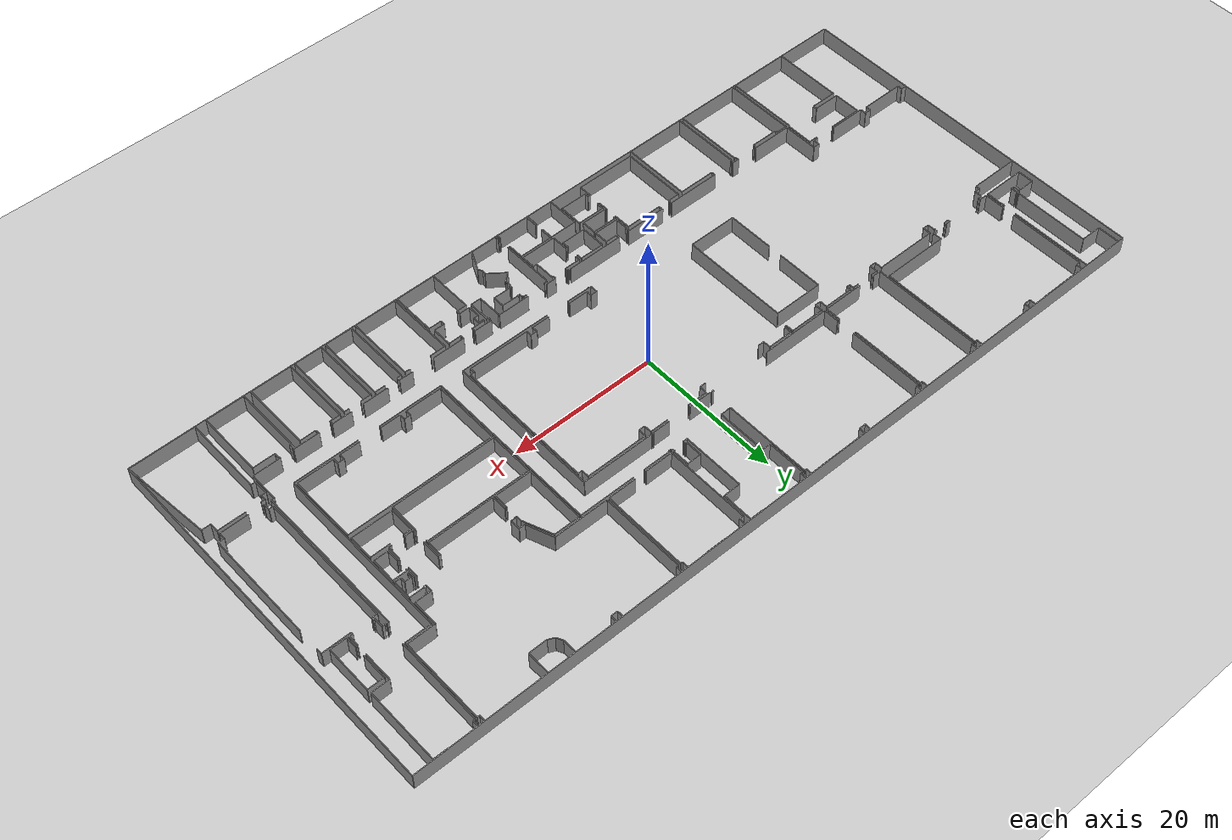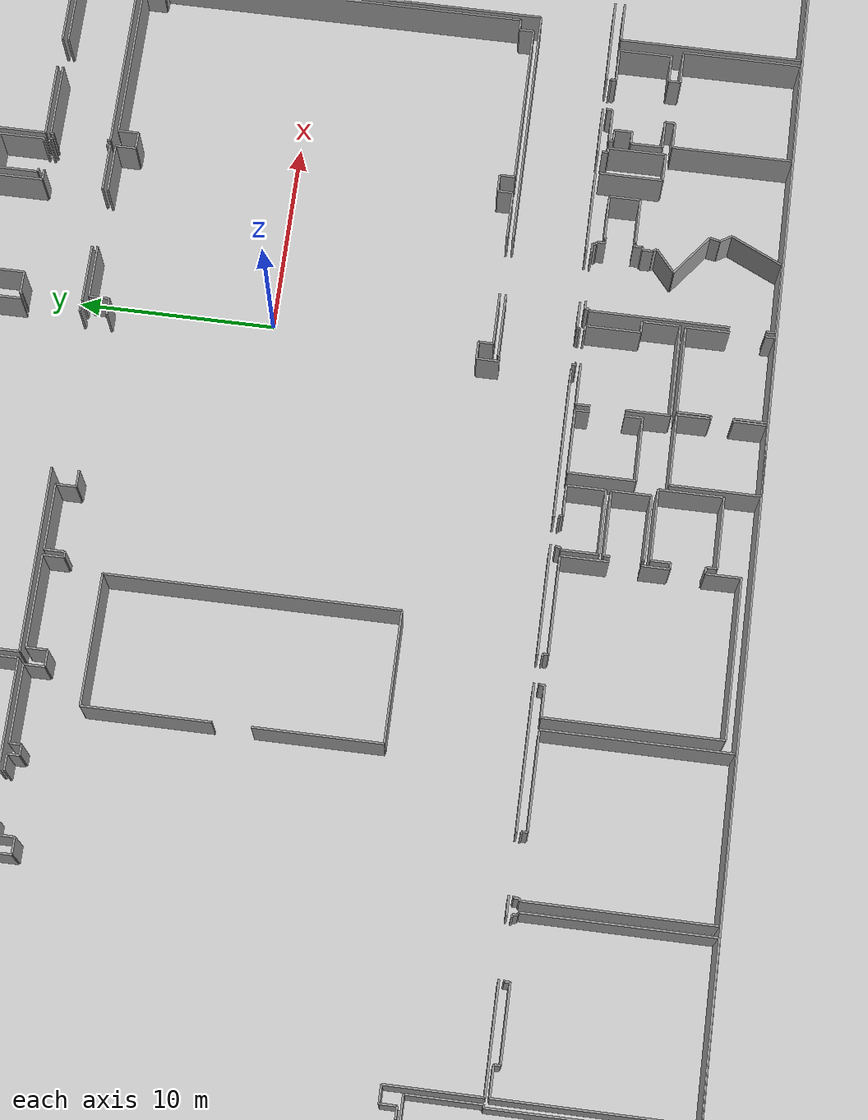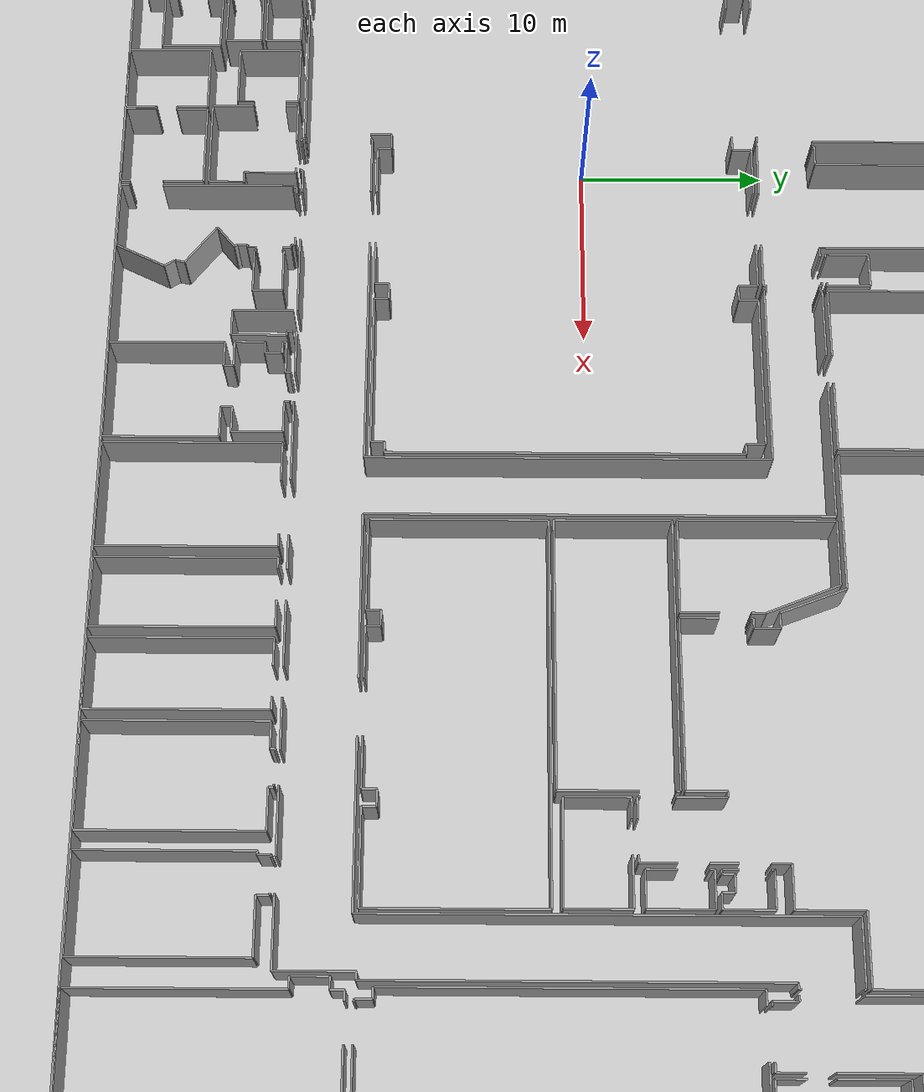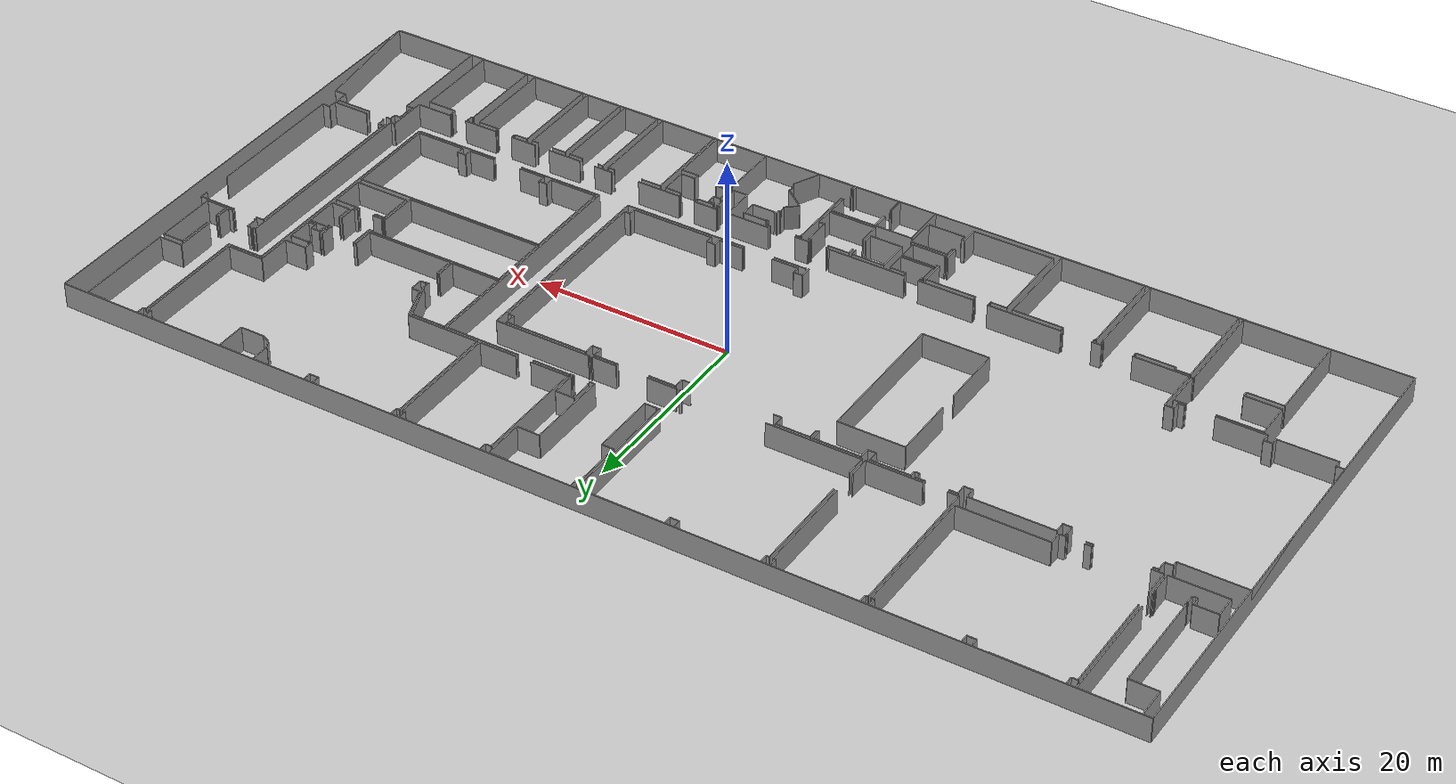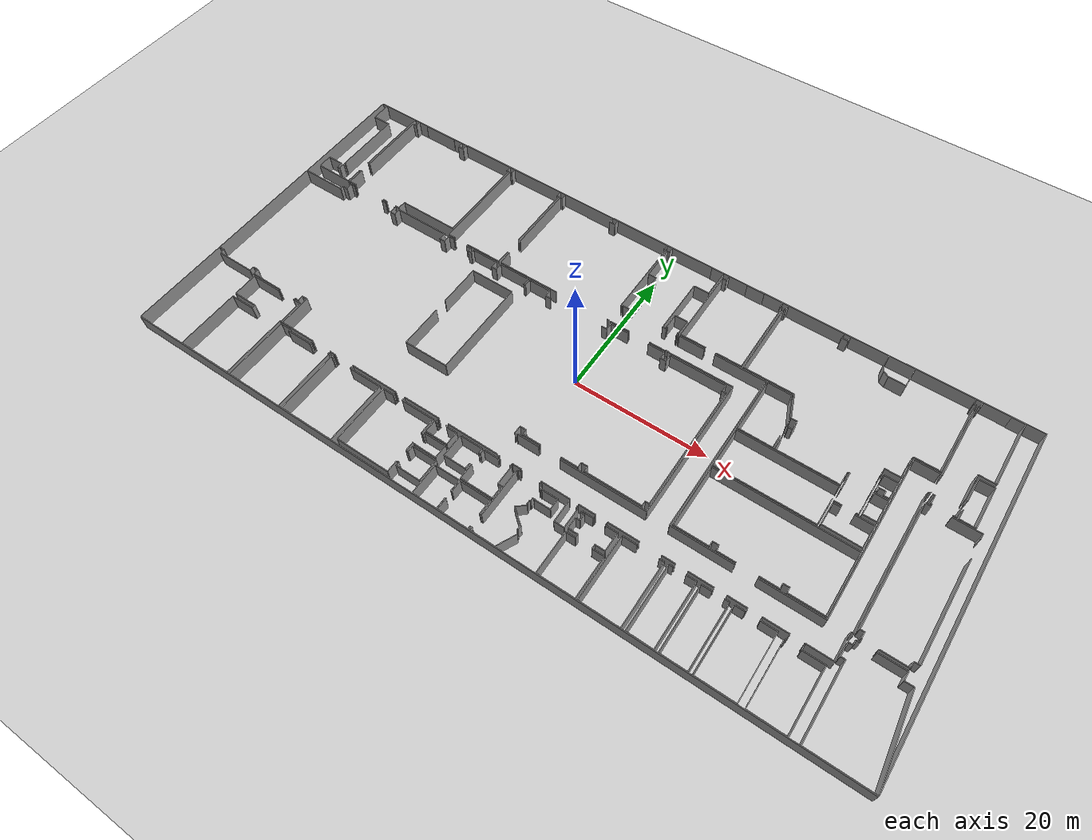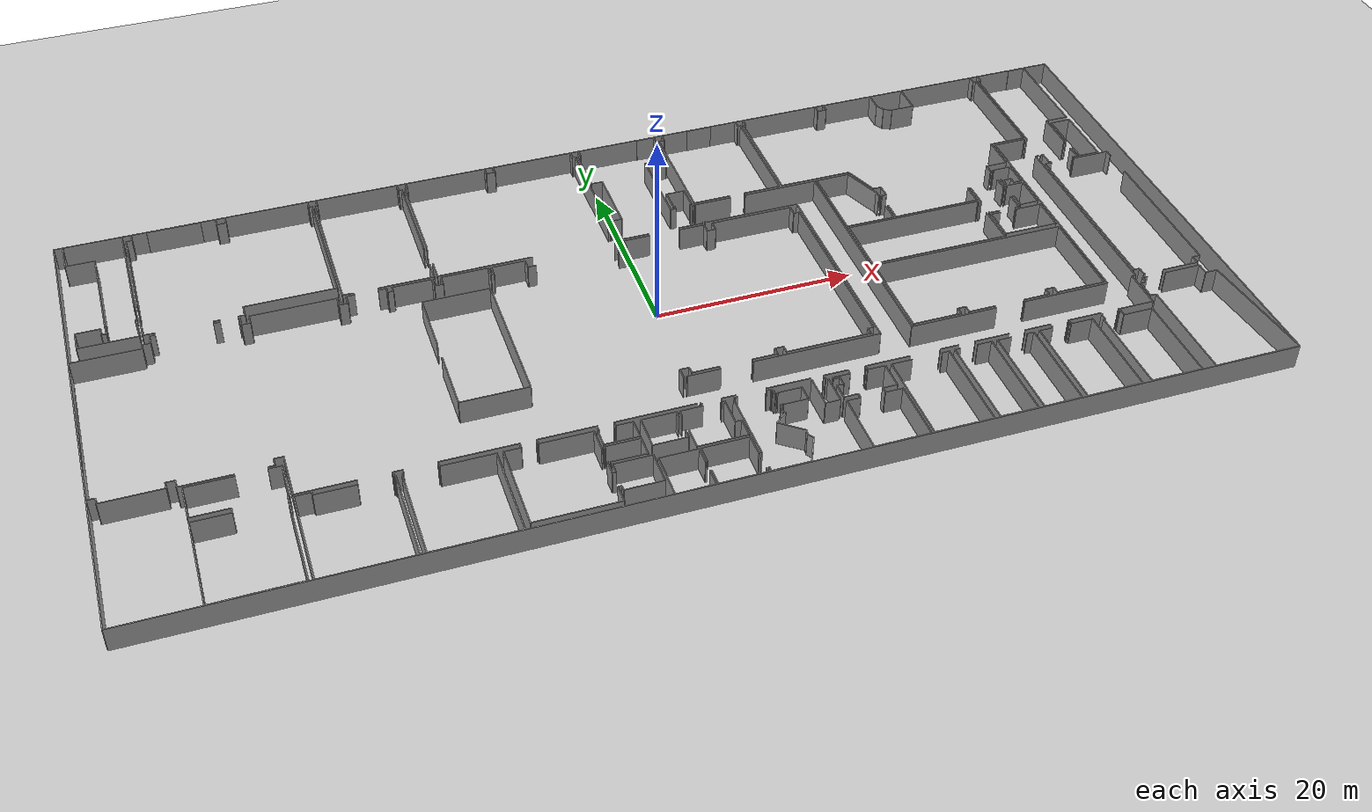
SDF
<sdf version="1.6">
  <world name="default">
    <light name="sun" type="directional">
      <cast_shadows>1</cast_shadows>
      <pose frame="">0 0 10 0 -0 0</pose>
      <diffuse>0.8 0.8 0.8 1</diffuse>
      <specular>0.1 0.1 0.1 1</specular>
      <attenuation>
        <range>1000</range>
        <constant>0.9</constant>
        <linear>0.01</linear>
        <quadratic>0.001</quadratic>
      </attenuation>
      <direction>-0.5 0.5 -1</direction>
    </light>
    <model name="ground_plane">
      <static>1</static>
      <link name="link">
        <collision name="collision">
          <geometry>
            <plane>
              <normal>0 0 1</normal>
              <size>100 100</size>
            </plane>
          </geometry>
          <surface>
            <friction>
              <ode>
                <mu>100</mu>
                <mu2>50</mu2>
              </ode>
              <torsional>
                <ode />
              </torsional>
            </friction>
            <contact>
              <ode />
            </contact>
            <bounce />
          </surface>
          <max_contacts>10</max_contacts>
        </collision>
        <visual name="visual">
          <cast_shadows>0</cast_shadows>
          <geometry>
            <plane>
              <normal>0 0 1</normal>
              <size>100 100</size>
            </plane>
          </geometry>
          <material>
            <script>
              <uri>file://media/materials/scripts/gazebo.material</uri>
              <name>Gazebo/Grey</name>
            </script>
          </material>
        </visual>
        <self_collide>0</self_collide>
        <kinematic>0</kinematic>
        <gravity>1</gravity>
      </link>
    </model>
    <gravity>0 0 -9.8</gravity>
    <magnetic_field>6e-06 2.3e-05 -4.2e-05</magnetic_field>
    <atmosphere type="adiabatic" />
    <physics default="0" name="default_physics" type="ode">
      <max_step_size>0.001</max_step_size>
      <real_time_factor>1</real_time_factor>
      <real_time_update_rate>1000</real_time_update_rate>
    </physics>
    <scene>
      <ambient>0.4 0.4 0.4 1</ambient>
      <background>0.7 0.7 0.7 1</background>
      <shadows>1</shadows>
    </scene>
    <spherical_coordinates>
      <surface_model>EARTH_WGS84</surface_model>
      <latitude_deg>0</latitude_deg>
      <longitude_deg>0</longitude_deg>
      <elevation>0</elevation>
      <heading_deg>0</heading_deg>
    </spherical_coordinates>
  <model name="50045366">
		<static>1</static>
		<link name="Wall_0">
			<collision name="Wall_0_Collision">
				<geometry>
					<box>
						<size>10.3561494202 0.1 2.5</size>
					</box>
				</geometry>
				<pose frame="">5.17807471009 0 1.25 0 0 0</pose>
			</collision>
			<visual name="Wall_0_Visual">
				<pose frame="">5.17807471009 0 1.25 0 0 0</pose>
				<geometry>
					<box>
						<size>10.3561494202 0.1 2.5</size>
					</box>
				</geometry>
				<material>
					<script>
						<uri>file://media/materials/scripts/gazebo.material</uri>
						<name>Gazebo/Grey</name>
					</script>
					<ambient>1 1 1 1</ambient>
				</material>
			</visual>
			<pose frame="">3.68114211683 -13.4038688699 0 0 0 1.57079632679</pose>
		</link>
		<link name="Wall_1">
			<collision name="Wall_1_Collision">
				<geometry>
					<box>
						<size>2.8190928605 0.1 2.5</size>
					</box>
				</geometry>
				<pose frame="">1.40954643025 0 1.25 0 0 0</pose>
			</collision>
			<visual name="Wall_1_Visual">
				<pose frame="">1.40954643025 0 1.25 0 0 0</pose>
				<geometry>
					<box>
						<size>2.8190928605 0.1 2.5</size>
					</box>
				</geometry>
				<material>
					<script>
						<uri>file://media/materials/scripts/gazebo.material</uri>
						<name>Gazebo/Grey</name>
					</script>
					<ambient>1 1 1 1</ambient>
				</material>
			</visual>
			<pose frame="">3.68114211683 -3.04771944977 0 0 0 3.14159265359</pose>
		</link>
		<link name="Wall_2">
			<collision name="Wall_2_Collision">
				<geometry>
					<box>
						<size>3.04771944977 0.1 2.5</size>
					</box>
				</geometry>
				<pose frame="">1.52385972489 0 1.25 0 0 0</pose>
			</collision>
			<visual name="Wall_2_Visual">
				<pose frame="">1.52385972489 0 1.25 0 0 0</pose>
				<geometry>
					<box>
						<size>3.04771944977 0.1 2.5</size>
					</box>
				</geometry>
				<material>
					<script>
						<uri>file://media/materials/scripts/gazebo.material</uri>
						<name>Gazebo/Grey</name>
					</script>
					<ambient>1 1 1 1</ambient>
				</material>
			</visual>
			<pose frame="">0.862049256329 -3.04771944977 0 0 0 1.57079632679</pose>
		</link>
		<link name="Wall_3">
			<collision name="Wall_3_Collision">
				<geometry>
					<box>
						<size>11.3713784913 0.1 2.5</size>
					</box>
				</geometry>
				<pose frame="">5.68568924566 0 1.25 0 0 0</pose>
			</collision>
			<visual name="Wall_3_Visual">
				<pose frame="">5.68568924566 0 1.25 0 0 0</pose>
				<geometry>
					<box>
						<size>11.3713784913 0.1 2.5</size>
					</box>
				</geometry>
				<material>
					<script>
						<uri>file://media/materials/scripts/gazebo.material</uri>
						<name>Gazebo/Grey</name>
					</script>
					<ambient>1 1 1 1</ambient>
				</material>
			</visual>
			<pose frame="">6.58838322897 -0.0 0 0 0 -1.57079632679</pose>
		</link>
		<link name="Wall_4">
			<collision name="Wall_4_Collision">
				<geometry>
					<box>
						<size>0.250727159569 0.1 2.5</size>
					</box>
				</geometry>
				<pose frame="">0.125363579784 0 1.25 0 0 0</pose>
			</collision>
			<visual name="Wall_4_Visual">
				<pose frame="">0.125363579784 0 1.25 0 0 0</pose>
				<geometry>
					<box>
						<size>0.250727159569 0.1 2.5</size>
					</box>
				</geometry>
				<material>
					<script>
						<uri>file://media/materials/scripts/gazebo.material</uri>
						<name>Gazebo/Grey</name>
					</script>
					<ambient>1 1 1 1</ambient>
				</material>
			</visual>
			<pose frame="">6.58838322897 -13.1447587354 0 0 0 -1.57079632679</pose>
		</link>
		<link name="Wall_5">
			<collision name="Wall_5_Collision">
				<geometry>
					<box>
						<size>0.135778791073 0.1 2.5</size>
					</box>
				</geometry>
				<pose frame="">0.0678893955367 0 1.25 0 0 0</pose>
			</collision>
			<visual name="Wall_5_Visual">
				<pose frame="">0.0678893955367 0 1.25 0 0 0</pose>
				<geometry>
					<box>
						<size>0.135778791073 0.1 2.5</size>
					</box>
				</geometry>
				<material>
					<script>
						<uri>file://media/materials/scripts/gazebo.material</uri>
						<name>Gazebo/Grey</name>
					</script>
					<ambient>1 1 1 1</ambient>
				</material>
			</visual>
			<pose frame="">6.58838322897 -13.395485895 0 0 0 3.14159265359</pose>
		</link>
		<link name="Wall_6">
			<collision name="Wall_6_Collision">
				<geometry>
					<box>
						<size>0.147829043869 0.1 2.5</size>
					</box>
				</geometry>
				<pose frame="">0.0739145219347 0 1.25 0 0 0</pose>
			</collision>
			<visual name="Wall_6_Visual">
				<pose frame="">0.0739145219347 0 1.25 0 0 0</pose>
				<geometry>
					<box>
						<size>0.147829043869 0.1 2.5</size>
					</box>
				</geometry>
				<material>
					<script>
						<uri>file://media/materials/scripts/gazebo.material</uri>
						<name>Gazebo/Grey</name>
					</script>
					<ambient>1 1 1 1</ambient>
				</material>
			</visual>
			<pose frame="">3.82873328168 -13.395485895 0 0 0 -3.08485499161</pose>
		</link>
		<link name="Wall_7">
			<collision name="Wall_7_Collision">
				<geometry>
					<box>
						<size>2.1705554356 0.1 2.5</size>
					</box>
				</geometry>
				<pose frame="">1.0852777178 0 1.25 0 0 0</pose>
			</collision>
			<visual name="Wall_7_Visual">
				<pose frame="">1.0852777178 0 1.25 0 0 0</pose>
				<geometry>
					<box>
						<size>2.1705554356 0.1 2.5</size>
					</box>
				</geometry>
				<material>
					<script>
						<uri>file://media/materials/scripts/gazebo.material</uri>
						<name>Gazebo/Grey</name>
					</script>
					<ambient>1 1 1 1</ambient>
				</material>
			</visual>
			<pose frame="">0.902820998082 -15.8468709911 0 0 0 1.57079632679</pose>
		</link>
		<link name="Wall_8">
			<collision name="Wall_8_Collision">
				<geometry>
					<box>
						<size>2.36260177059 0.1 2.5</size>
					</box>
				</geometry>
				<pose frame="">1.18130088529 0 1.25 0 0 0</pose>
			</collision>
			<visual name="Wall_8_Visual">
				<pose frame="">1.18130088529 0 1.25 0 0 0</pose>
				<geometry>
					<box>
						<size>2.36260177059 0.1 2.5</size>
					</box>
				</geometry>
				<material>
					<script>
						<uri>file://media/materials/scripts/gazebo.material</uri>
						<name>Gazebo/Grey</name>
					</script>
					<ambient>1 1 1 1</ambient>
				</material>
			</visual>
			<pose frame="">0.902820998082 -13.6763155555 0 0 0 0.0</pose>
		</link>
		<link name="Wall_9">
			<collision name="Wall_9_Collision">
				<geometry>
					<box>
						<size>0.864462536993 0.1 2.5</size>
					</box>
				</geometry>
				<pose frame="">0.432231268497 0 1.25 0 0 0</pose>
			</collision>
			<visual name="Wall_9_Visual">
				<pose frame="">0.432231268497 0 1.25 0 0 0</pose>
				<geometry>
					<box>
						<size>0.864462536993 0.1 2.5</size>
					</box>
				</geometry>
				<material>
					<script>
						<uri>file://media/materials/scripts/gazebo.material</uri>
						<name>Gazebo/Grey</name>
					</script>
					<ambient>1 1 1 1</ambient>
				</material>
			</visual>
			<pose frame="">3.26542276867 -13.6763155555 0 0 0 -1.57079632679</pose>
		</link>
		<link name="Wall_10">
			<collision name="Wall_10_Collision">
				<geometry>
					<box>
						<size>0.441757376383 0.1 2.5</size>
					</box>
				</geometry>
				<pose frame="">0.220878688191 0 1.25 0 0 0</pose>
			</collision>
			<visual name="Wall_10_Visual">
				<pose frame="">0.220878688191 0 1.25 0 0 0</pose>
				<geometry>
					<box>
						<size>0.441757376383 0.1 2.5</size>
					</box>
				</geometry>
				<material>
					<script>
						<uri>file://media/materials/scripts/gazebo.material</uri>
						<name>Gazebo/Grey</name>
					</script>
					<ambient>1 1 1 1</ambient>
				</material>
			</visual>
			<pose frame="">3.26542276867 -14.5407780925 0 0 0 0.0</pose>
		</link>
		<link name="Wall_11">
			<collision name="Wall_11_Collision">
				<geometry>
					<box>
						<size>0.873988644879 0.1 2.5</size>
					</box>
				</geometry>
				<pose frame="">0.43699432244 0 1.25 0 0 0</pose>
			</collision>
			<visual name="Wall_11_Visual">
				<pose frame="">0.43699432244 0 1.25 0 0 0</pose>
				<geometry>
					<box>
						<size>0.873988644879 0.1 2.5</size>
					</box>
				</geometry>
				<material>
					<script>
						<uri>file://media/materials/scripts/gazebo.material</uri>
						<name>Gazebo/Grey</name>
					</script>
					<ambient>1 1 1 1</ambient>
				</material>
			</visual>
			<pose frame="">3.70718014505 -14.5407780925 0 0 0 1.57079632679</pose>
		</link>
		<link name="Wall_12">
			<collision name="Wall_12_Collision">
				<geometry>
					<box>
						<size>0.105676290153 0.1 2.5</size>
					</box>
				</geometry>
				<pose frame="">0.0528381450763 0 1.25 0 0 0</pose>
			</collision>
			<visual name="Wall_12_Visual">
				<pose frame="">0.0528381450763 0 1.25 0 0 0</pose>
				<geometry>
					<box>
						<size>0.105676290153 0.1 2.5</size>
					</box>
				</geometry>
				<material>
					<script>
						<uri>file://media/materials/scripts/gazebo.material</uri>
						<name>Gazebo/Grey</name>
					</script>
					<ambient>1 1 1 1</ambient>
				</material>
			</visual>
			<pose frame="">3.70718014505 -13.6667894476 0 0 0 0.0</pose>
		</link>
		<link name="Wall_13">
			<collision name="Wall_13_Collision">
				<geometry>
					<box>
						<size>0.109867777623 0.1 2.5</size>
					</box>
				</geometry>
				<pose frame="">0.0549338888113 0 1.25 0 0 0</pose>
			</collision>
			<visual name="Wall_13_Visual">
				<pose frame="">0.0549338888113 0 1.25 0 0 0</pose>
				<geometry>
					<box>
						<size>0.109867777623 0.1 2.5</size>
					</box>
				</geometry>
				<material>
					<script>
						<uri>file://media/materials/scripts/gazebo.material</uri>
						<name>Gazebo/Grey</name>
					</script>
					<ambient>1 1 1 1</ambient>
				</material>
			</visual>
			<pose frame="">6.48080171724 -13.6667894476 0 0 0 0.0</pose>
		</link>
		<link name="Wall_14">
			<collision name="Wall_14_Collision">
				<geometry>
					<box>
						<size>2.17042842083 0.1 2.5</size>
					</box>
				</geometry>
				<pose frame="">1.08521421041 0 1.25 0 0 0</pose>
			</collision>
			<visual name="Wall_14_Visual">
				<pose frame="">1.08521421041 0 1.25 0 0 0</pose>
				<geometry>
					<box>
						<size>2.17042842083 0.1 2.5</size>
					</box>
				</geometry>
				<material>
					<script>
						<uri>file://media/materials/scripts/gazebo.material</uri>
						<name>Gazebo/Grey</name>
					</script>
					<ambient>1 1 1 1</ambient>
				</material>
			</visual>
			<pose frame="">6.59066949486 -13.6667894476 0 0 0 -1.57079632679</pose>
		</link>
		<link name="Wall_15">
			<collision name="Wall_15_Collision">
				<geometry>
					<box>
						<size>5.68785668816 0.1 2.5</size>
					</box>
				</geometry>
				<pose frame="">2.84392834408 0 1.25 0 0 0</pose>
			</collision>
			<visual name="Wall_15_Visual">
				<pose frame="">2.84392834408 0 1.25 0 0 0</pose>
				<geometry>
					<box>
						<size>5.68785668816 0.1 2.5</size>
					</box>
				</geometry>
				<material>
					<script>
						<uri>file://media/materials/scripts/gazebo.material</uri>
						<name>Gazebo/Grey</name>
					</script>
					<ambient>1 1 1 1</ambient>
				</material>
			</visual>
			<pose frame="">6.59066949486 -15.8372178684 0 0 0 -3.13989550688</pose>
		</link>
		<link name="Wall_16">
			<collision name="Wall_16_Collision">
				<geometry>
					<box>
						<size>2.6802657149 0.1 2.5</size>
					</box>
				</geometry>
				<pose frame="">1.34013285745 0 1.25 0 0 0</pose>
			</collision>
			<visual name="Wall_16_Visual">
				<pose frame="">1.34013285745 0 1.25 0 0 0</pose>
				<geometry>
					<box>
						<size>2.6802657149 0.1 2.5</size>
					</box>
				</geometry>
				<material>
					<script>
						<uri>file://media/materials/scripts/gazebo.material</uri>
						<name>Gazebo/Grey</name>
					</script>
					<ambient>1 1 1 1</ambient>
				</material>
			</visual>
			<pose frame="">6.89575897677 -15.8175305788 0 0 0 1.57079632679</pose>
		</link>
		<link name="Wall_17">
			<collision name="Wall_17_Collision">
				<geometry>
					<box>
						<size>10.4995490976 0.1 2.5</size>
					</box>
				</geometry>
				<pose frame="">5.24977454878 0 1.25 0 0 0</pose>
			</collision>
			<visual name="Wall_17_Visual">
				<pose frame="">5.24977454878 0 1.25 0 0 0</pose>
				<geometry>
					<box>
						<size>10.4995490976 0.1 2.5</size>
					</box>
				</geometry>
				<material>
					<script>
						<uri>file://media/materials/scripts/gazebo.material</uri>
						<name>Gazebo/Grey</name>
					</script>
					<ambient>1 1 1 1</ambient>
				</material>
			</visual>
			<pose frame="">6.89575897677 -11.3735377424 0 0 0 1.57079632679</pose>
		</link>
		<link name="Wall_18">
			<collision name="Wall_18_Collision">
				<geometry>
					<box>
						<size>0.585919142396 0.1 2.5</size>
					</box>
				</geometry>
				<pose frame="">0.292959571198 0 1.25 0 0 0</pose>
			</collision>
			<visual name="Wall_18_Visual">
				<pose frame="">0.292959571198 0 1.25 0 0 0</pose>
				<geometry>
					<box>
						<size>0.585919142396 0.1 2.5</size>
					</box>
				</geometry>
				<material>
					<script>
						<uri>file://media/materials/scripts/gazebo.material</uri>
						<name>Gazebo/Grey</name>
					</script>
					<ambient>1 1 1 1</ambient>
				</material>
			</visual>
			<pose frame="">6.89575897677 -0.873988644879 0 0 0 0.0</pose>
		</link>
		<link name="Wall_19">
			<collision name="Wall_19_Collision">
				<geometry>
					<box>
						<size>0.825977061132 0.1 2.5</size>
					</box>
				</geometry>
				<pose frame="">0.412988530566 0 1.25 0 0 0</pose>
			</collision>
			<visual name="Wall_19_Visual">
				<pose frame="">0.412988530566 0 1.25 0 0 0</pose>
				<geometry>
					<box>
						<size>0.825977061132 0.1 2.5</size>
					</box>
				</geometry>
				<material>
					<script>
						<uri>file://media/materials/scripts/gazebo.material</uri>
						<name>Gazebo/Grey</name>
					</script>
					<ambient>1 1 1 1</ambient>
				</material>
			</visual>
			<pose frame="">7.48167811917 -0.873988644879 0 0 0 1.57079632679</pose>
		</link>
		<link name="Wall_20">
			<collision name="Wall_20_Collision">
				<geometry>
					<box>
						<size>5.33741474133 0.1 2.5</size>
					</box>
				</geometry>
				<pose frame="">2.66870737067 0 1.25 0 0 0</pose>
			</collision>
			<visual name="Wall_20_Visual">
				<pose frame="">2.66870737067 0 1.25 0 0 0</pose>
				<geometry>
					<box>
						<size>5.33741474133 0.1 2.5</size>
					</box>
				</geometry>
				<material>
					<script>
						<uri>file://media/materials/scripts/gazebo.material</uri>
						<name>Gazebo/Grey</name>
					</script>
					<ambient>1 1 1 1</ambient>
				</material>
			</visual>
			<pose frame="">8.97930929367 -0.0480115837472 0 0 0 0.0</pose>
		</link>
		<link name="Wall_21">
			<collision name="Wall_21_Collision">
				<geometry>
					<box>
						<size>0.832454814495 0.1 2.5</size>
					</box>
				</geometry>
				<pose frame="">0.416227407247 0 1.25 0 0 0</pose>
			</collision>
			<visual name="Wall_21_Visual">
				<pose frame="">0.416227407247 0 1.25 0 0 0</pose>
				<geometry>
					<box>
						<size>0.832454814495 0.1 2.5</size>
					</box>
				</geometry>
				<material>
					<script>
						<uri>file://media/materials/scripts/gazebo.material</uri>
						<name>Gazebo/Grey</name>
					</script>
					<ambient>1 1 1 1</ambient>
				</material>
			</visual>
			<pose frame="">15.8158793868 -0.0480115837472 0 0 0 -1.57079632679</pose>
		</link>
		<link name="Wall_22">
			<collision name="Wall_22_Collision">
				<geometry>
					<box>
						<size>0.919586947962 0.1 2.5</size>
					</box>
				</geometry>
				<pose frame="">0.459793473981 0 1.25 0 0 0</pose>
			</collision>
			<visual name="Wall_22_Visual">
				<pose frame="">0.459793473981 0 1.25 0 0 0</pose>
				<geometry>
					<box>
						<size>0.919586947962 0.1 2.5</size>
					</box>
				</geometry>
				<material>
					<script>
						<uri>file://media/materials/scripts/gazebo.material</uri>
						<name>Gazebo/Grey</name>
					</script>
					<ambient>1 1 1 1</ambient>
				</material>
			</visual>
			<pose frame="">15.8158793868 -0.880466398242 0 0 0 0.0</pose>
		</link>
		<link name="Wall_23">
			<collision name="Wall_23_Collision">
				<geometry>
					<box>
						<size>0.832454814495 0.1 2.5</size>
					</box>
				</geometry>
				<pose frame="">0.416227407247 0 1.25 0 0 0</pose>
			</collision>
			<visual name="Wall_23_Visual">
				<pose frame="">0.416227407247 0 1.25 0 0 0</pose>
				<geometry>
					<box>
						<size>0.832454814495 0.1 2.5</size>
					</box>
				</geometry>
				<material>
					<script>
						<uri>file://media/materials/scripts/gazebo.material</uri>
						<name>Gazebo/Grey</name>
					</script>
					<ambient>1 1 1 1</ambient>
				</material>
			</visual>
			<pose frame="">16.7354663347 -0.880466398242 0 0 0 1.57079632679</pose>
		</link>
		<link name="Wall_24">
			<collision name="Wall_24_Collision">
				<geometry>
					<box>
						<size>0.805781712413 0.1 2.5</size>
					</box>
				</geometry>
				<pose frame="">0.402890856207 0 1.25 0 0 0</pose>
			</collision>
			<visual name="Wall_24_Visual">
				<pose frame="">0.402890856207 0 1.25 0 0 0</pose>
				<geometry>
					<box>
						<size>0.805781712413 0.1 2.5</size>
					</box>
				</geometry>
				<material>
					<script>
						<uri>file://media/materials/scripts/gazebo.material</uri>
						<name>Gazebo/Grey</name>
					</script>
					<ambient>1 1 1 1</ambient>
				</material>
			</visual>
			<pose frame="">25.0725889421 -0.0480115837472 0 0 0 -1.57079632679</pose>
		</link>
		<link name="Wall_25">
			<collision name="Wall_25_Collision">
				<geometry>
					<box>
						<size>0.3123293239 0.1 2.5</size>
					</box>
				</geometry>
				<pose frame="">0.15616466195 0 1.25 0 0 0</pose>
			</collision>
			<visual name="Wall_25_Visual">
				<pose frame="">0.15616466195 0 1.25 0 0 0</pose>
				<geometry>
					<box>
						<size>0.3123293239 0.1 2.5</size>
					</box>
				</geometry>
				<material>
					<script>
						<uri>file://media/materials/scripts/gazebo.material</uri>
						<name>Gazebo/Grey</name>
					</script>
					<ambient>1 1 1 1</ambient>
				</material>
			</visual>
			<pose frame="">25.0725889421 -0.85379329616 0 0 0 0.0</pose>
		</link>
		<link name="Wall_26">
			<collision name="Wall_26_Collision">
				<geometry>
					<box>
						<size>13.7253432574 0.1 2.5</size>
					</box>
				</geometry>
				<pose frame="">6.86267162871 0 1.25 0 0 0</pose>
			</collision>
			<visual name="Wall_26_Visual">
				<pose frame="">6.86267162871 0 1.25 0 0 0</pose>
				<geometry>
					<box>
						<size>13.7253432574 0.1 2.5</size>
					</box>
				</geometry>
				<material>
					<script>
						<uri>file://media/materials/scripts/gazebo.material</uri>
						<name>Gazebo/Grey</name>
					</script>
					<ambient>1 1 1 1</ambient>
				</material>
			</visual>
			<pose frame="">25.384918266 -0.85379329616 0 0 0 -1.57079632679</pose>
		</link>
		<link name="Wall_27">
			<collision name="Wall_27_Collision">
				<geometry>
					<box>
						<size>8.99785345036 0.1 2.5</size>
					</box>
				</geometry>
				<pose frame="">4.49892672518 0 1.25 0 0 0</pose>
			</collision>
			<visual name="Wall_27_Visual">
				<pose frame="">4.49892672518 0 1.25 0 0 0</pose>
				<geometry>
					<box>
						<size>8.99785345036 0.1 2.5</size>
					</box>
				</geometry>
				<material>
					<script>
						<uri>file://media/materials/scripts/gazebo.material</uri>
						<name>Gazebo/Grey</name>
					</script>
					<ambient>1 1 1 1</ambient>
				</material>
			</visual>
			<pose frame="">25.384918266 -14.5791365536 0 0 0 3.14159265359</pose>
		</link>
		<link name="Wall_28">
			<collision name="Wall_28_Collision">
				<geometry>
					<box>
						<size>1.26366996482 0.1 2.5</size>
					</box>
				</geometry>
				<pose frame="">0.631834982408 0 1.25 0 0 0</pose>
			</collision>
			<visual name="Wall_28_Visual">
				<pose frame="">0.631834982408 0 1.25 0 0 0</pose>
				<geometry>
					<box>
						<size>1.26366996482 0.1 2.5</size>
					</box>
				</geometry>
				<material>
					<script>
						<uri>file://media/materials/scripts/gazebo.material</uri>
						<name>Gazebo/Grey</name>
					</script>
					<ambient>1 1 1 1</ambient>
				</material>
			</visual>
			<pose frame="">16.3870648156 -14.5791365536 0 0 0 -1.57079632679</pose>
		</link>
		<link name="Wall_29">
			<collision name="Wall_29_Collision">
				<geometry>
					<box>
						<size>0.651966823742 0.1 2.5</size>
					</box>
				</geometry>
				<pose frame="">0.325983411871 0 1.25 0 0 0</pose>
			</collision>
			<visual name="Wall_29_Visual">
				<pose frame="">0.325983411871 0 1.25 0 0 0</pose>
				<geometry>
					<box>
						<size>0.651966823742 0.1 2.5</size>
					</box>
				</geometry>
				<material>
					<script>
						<uri>file://media/materials/scripts/gazebo.material</uri>
						<name>Gazebo/Grey</name>
					</script>
					<ambient>1 1 1 1</ambient>
				</material>
			</visual>
			<pose frame="">16.3870648156 -15.8428065184 0 0 0 3.14159265359</pose>
		</link>
		<link name="Wall_30">
			<collision name="Wall_30_Collision">
				<geometry>
					<box>
						<size>0.647775336272 0.1 2.5</size>
					</box>
				</geometry>
				<pose frame="">0.323887668136 0 1.25 0 0 0</pose>
			</collision>
			<visual name="Wall_30_Visual">
				<pose frame="">0.323887668136 0 1.25 0 0 0</pose>
				<geometry>
					<box>
						<size>0.647775336272 0.1 2.5</size>
					</box>
				</geometry>
				<material>
					<script>
						<uri>file://media/materials/scripts/gazebo.material</uri>
						<name>Gazebo/Grey</name>
					</script>
					<ambient>1 1 1 1</ambient>
				</material>
			</visual>
			<pose frame="">14.041737054 -15.8428065184 0 0 0 3.14159265359</pose>
		</link>
		<link name="Wall_31">
			<collision name="Wall_31_Collision">
				<geometry>
					<box>
						<size>1.12830133685 0.1 2.5</size>
					</box>
				</geometry>
				<pose frame="">0.564150668426 0 1.25 0 0 0</pose>
			</collision>
			<visual name="Wall_31_Visual">
				<pose frame="">0.564150668426 0 1.25 0 0 0</pose>
				<geometry>
					<box>
						<size>1.12830133685 0.1 2.5</size>
					</box>
				</geometry>
				<material>
					<script>
						<uri>file://media/materials/scripts/gazebo.material</uri>
						<name>Gazebo/Grey</name>
					</script>
					<ambient>1 1 1 1</ambient>
				</material>
			</visual>
			<pose frame="">8.02377716528 -15.8428065184 0 0 0 3.11918901609</pose>
		</link>
		<link name="Wall_32">
			<collision name="Wall_32_Collision">
				<geometry>
					<box>
						<size>0.681942309891 0.1 2.5</size>
					</box>
				</geometry>
				<pose frame="">0.340971154945 0 1.25 0 0 0</pose>
			</collision>
			<visual name="Wall_32_Visual">
				<pose frame="">0.340971154945 0 1.25 0 0 0</pose>
				<geometry>
					<box>
						<size>0.681942309891 0.1 2.5</size>
					</box>
				</geometry>
				<material>
					<script>
						<uri>file://media/materials/scripts/gazebo.material</uri>
						<name>Gazebo/Grey</name>
					</script>
					<ambient>1 1 1 1</ambient>
				</material>
			</visual>
			<pose frame="">0.806797830588 -36.6302981037 0 0 0 1.57079632679</pose>
		</link>
		<link name="Wall_33">
			<collision name="Wall_33_Collision">
				<geometry>
					<box>
						<size>0.806797830588 0.1 2.5</size>
					</box>
				</geometry>
				<pose frame="">0.403398915294 0 1.25 0 0 0</pose>
			</collision>
			<visual name="Wall_33_Visual">
				<pose frame="">0.403398915294 0 1.25 0 0 0</pose>
				<geometry>
					<box>
						<size>0.806797830588 0.1 2.5</size>
					</box>
				</geometry>
				<material>
					<script>
						<uri>file://media/materials/scripts/gazebo.material</uri>
						<name>Gazebo/Grey</name>
					</script>
					<ambient>1 1 1 1</ambient>
				</material>
			</visual>
			<pose frame="">0.806797830588 -35.9483557938 0 0 0 3.14159265359</pose>
		</link>
		<link name="Wall_34">
			<collision name="Wall_34_Collision">
				<geometry>
					<box>
						<size>18.2428776467 0.1 2.5</size>
					</box>
				</geometry>
				<pose frame="">9.12143882334 0 1.25 0 0 0</pose>
			</collision>
			<visual name="Wall_34_Visual">
				<pose frame="">9.12143882334 0 1.25 0 0 0</pose>
				<geometry>
					<box>
						<size>18.2428776467 0.1 2.5</size>
					</box>
				</geometry>
				<material>
					<script>
						<uri>file://media/materials/scripts/gazebo.material</uri>
						<name>Gazebo/Grey</name>
					</script>
					<ambient>1 1 1 1</ambient>
				</material>
			</visual>
			<pose frame="">0.0 -35.9483557938 0 0 0 1.57079632679</pose>
		</link>
		<link name="Wall_35">
			<collision name="Wall_35_Collision">
				<geometry>
					<box>
						<size>6.68237416011 0.1 2.5</size>
					</box>
				</geometry>
				<pose frame="">3.34118708006 0 1.25 0 0 0</pose>
			</collision>
			<visual name="Wall_35_Visual">
				<pose frame="">3.34118708006 0 1.25 0 0 0</pose>
				<geometry>
					<box>
						<size>6.68237416011 0.1 2.5</size>
					</box>
				</geometry>
				<material>
					<script>
						<uri>file://media/materials/scripts/gazebo.material</uri>
						<name>Gazebo/Grey</name>
					</script>
					<ambient>1 1 1 1</ambient>
				</material>
			</visual>
			<pose frame="">0.0 -17.7054781471 0 0 0 0.0</pose>
		</link>
		<link name="Wall_36">
			<collision name="Wall_36_Collision">
				<geometry>
					<box>
						<size>0.53447815981 0.1 2.5</size>
					</box>
				</geometry>
				<pose frame="">0.267239079905 0 1.25 0 0 0</pose>
			</collision>
			<visual name="Wall_36_Visual">
				<pose frame="">0.267239079905 0 1.25 0 0 0</pose>
				<geometry>
					<box>
						<size>0.53447815981 0.1 2.5</size>
					</box>
				</geometry>
				<material>
					<script>
						<uri>file://media/materials/scripts/gazebo.material</uri>
						<name>Gazebo/Grey</name>
					</script>
					<ambient>1 1 1 1</ambient>
				</material>
			</visual>
			<pose frame="">6.68237416011 -17.7054781471 0 0 0 1.57079632679</pose>
		</link>
		<link name="Wall_37">
			<collision name="Wall_37_Collision">
				<geometry>
					<box>
						<size>0.785078304607 0.1 2.5</size>
					</box>
				</geometry>
				<pose frame="">0.392539152303 0 1.25 0 0 0</pose>
			</collision>
			<visual name="Wall_37_Visual">
				<pose frame="">0.392539152303 0 1.25 0 0 0</pose>
				<geometry>
					<box>
						<size>0.785078304607 0.1 2.5</size>
					</box>
				</geometry>
				<material>
					<script>
						<uri>file://media/materials/scripts/gazebo.material</uri>
						<name>Gazebo/Grey</name>
					</script>
					<ambient>1 1 1 1</ambient>
				</material>
			</visual>
			<pose frame="">6.68237416011 -17.1709999873 0 0 0 0.0</pose>
		</link>
		<link name="Wall_38">
			<collision name="Wall_38_Collision">
				<geometry>
					<box>
						<size>1.04393440957 0.1 2.5</size>
					</box>
				</geometry>
				<pose frame="">0.521967204786 0 1.25 0 0 0</pose>
			</collision>
			<visual name="Wall_38_Visual">
				<pose frame="">0.521967204786 0 1.25 0 0 0</pose>
				<geometry>
					<box>
						<size>1.04393440957 0.1 2.5</size>
					</box>
				</geometry>
				<material>
					<script>
						<uri>file://media/materials/scripts/gazebo.material</uri>
						<name>Gazebo/Grey</name>
					</script>
					<ambient>1 1 1 1</ambient>
				</material>
			</visual>
			<pose frame="">7.46745246472 -17.1709999873 0 0 0 1.57079632679</pose>
		</link>
		<link name="Wall_39">
			<collision name="Wall_39_Collision">
				<geometry>
					<box>
						<size>0.54286113475 0.1 2.5</size>
					</box>
				</geometry>
				<pose frame="">0.271430567375 0 1.25 0 0 0</pose>
			</collision>
			<visual name="Wall_39_Visual">
				<pose frame="">0.271430567375 0 1.25 0 0 0</pose>
				<geometry>
					<box>
						<size>0.54286113475 0.1 2.5</size>
					</box>
				</geometry>
				<material>
					<script>
						<uri>file://media/materials/scripts/gazebo.material</uri>
						<name>Gazebo/Grey</name>
					</script>
					<ambient>1 1 1 1</ambient>
				</material>
			</visual>
			<pose frame="">7.46745246472 -16.1270655777 0 0 0 0.0</pose>
		</link>
		<link name="Wall_40">
			<collision name="Wall_40_Collision">
				<geometry>
					<box>
						<size>0.673305305407 0.1 2.5</size>
					</box>
				</geometry>
				<pose frame="">0.336652652704 0 1.25 0 0 0</pose>
			</collision>
			<visual name="Wall_40_Visual">
				<pose frame="">0.336652652704 0 1.25 0 0 0</pose>
				<geometry>
					<box>
						<size>0.673305305407 0.1 2.5</size>
					</box>
				</geometry>
				<material>
					<script>
						<uri>file://media/materials/scripts/gazebo.material</uri>
						<name>Gazebo/Grey</name>
					</script>
					<ambient>1 1 1 1</ambient>
				</material>
			</visual>
			<pose frame="">13.3738933838 -16.1270655777 0 0 0 0.0</pose>
		</link>
		<link name="Wall_41">
			<collision name="Wall_41_Collision">
				<geometry>
					<box>
						<size>0.164738159048 0.1 2.5</size>
					</box>
				</geometry>
				<pose frame="">0.082369079524 0 1.25 0 0 0</pose>
			</collision>
			<visual name="Wall_41_Visual">
				<pose frame="">0.082369079524 0 1.25 0 0 0</pose>
				<geometry>
					<box>
						<size>0.164738159048 0.1 2.5</size>
					</box>
				</geometry>
				<material>
					<script>
						<uri>file://media/materials/scripts/gazebo.material</uri>
						<name>Gazebo/Grey</name>
					</script>
					<ambient>1 1 1 1</ambient>
				</material>
			</visual>
			<pose frame="">15.694961324 -16.1270655777 0 0 0 0.0</pose>
		</link>
		<link name="Wall_42">
			<collision name="Wall_42_Collision">
				<geometry>
					<box>
						<size>1.04139411414 0.1 2.5</size>
					</box>
				</geometry>
				<pose frame="">0.520697057068 0 1.25 0 0 0</pose>
			</collision>
			<visual name="Wall_42_Visual">
				<pose frame="">0.520697057068 0 1.25 0 0 0</pose>
				<geometry>
					<box>
						<size>1.04139411414 0.1 2.5</size>
					</box>
				</geometry>
				<material>
					<script>
						<uri>file://media/materials/scripts/gazebo.material</uri>
						<name>Gazebo/Grey</name>
					</script>
					<ambient>1 1 1 1</ambient>
				</material>
			</visual>
			<pose frame="">15.859699483 -16.1270655777 0 0 0 -1.57079632679</pose>
		</link>
		<link name="Wall_43">
			<collision name="Wall_43_Collision">
				<geometry>
					<box>
						<size>0.840202715576 0.1 2.5</size>
					</box>
				</geometry>
				<pose frame="">0.420101357788 0 1.25 0 0 0</pose>
			</collision>
			<visual name="Wall_43_Visual">
				<pose frame="">0.420101357788 0 1.25 0 0 0</pose>
				<geometry>
					<box>
						<size>0.840202715576 0.1 2.5</size>
					</box>
				</geometry>
				<material>
					<script>
						<uri>file://media/materials/scripts/gazebo.material</uri>
						<name>Gazebo/Grey</name>
					</script>
					<ambient>1 1 1 1</ambient>
				</material>
			</visual>
			<pose frame="">15.859699483 -17.1684596919 0 0 0 0.0</pose>
		</link>
		<link name="Wall_44">
			<collision name="Wall_44_Collision">
				<geometry>
					<box>
						<size>1.05968424128 0.1 2.5</size>
					</box>
				</geometry>
				<pose frame="">0.529842120639 0 1.25 0 0 0</pose>
			</collision>
			<visual name="Wall_44_Visual">
				<pose frame="">0.529842120639 0 1.25 0 0 0</pose>
				<geometry>
					<box>
						<size>1.05968424128 0.1 2.5</size>
					</box>
				</geometry>
				<material>
					<script>
						<uri>file://media/materials/scripts/gazebo.material</uri>
						<name>Gazebo/Grey</name>
					</script>
					<ambient>1 1 1 1</ambient>
				</material>
			</visual>
			<pose frame="">16.6999021986 -17.1684596919 0 0 0 1.57079632679</pose>
		</link>
		<link name="Wall_45">
			<collision name="Wall_45_Collision">
				<geometry>
					<box>
						<size>8.38284792521 0.1 2.5</size>
					</box>
				</geometry>
				<pose frame="">4.19142396261 0 1.25 0 0 0</pose>
			</collision>
			<visual name="Wall_45_Visual">
				<pose frame="">4.19142396261 0 1.25 0 0 0</pose>
				<geometry>
					<box>
						<size>8.38284792521 0.1 2.5</size>
					</box>
				</geometry>
				<material>
					<script>
						<uri>file://media/materials/scripts/gazebo.material</uri>
						<name>Gazebo/Grey</name>
					</script>
					<ambient>1 1 1 1</ambient>
				</material>
			</visual>
			<pose frame="">16.6999021986 -16.1087754506 0 0 0 0.0</pose>
		</link>
		<link name="Wall_46">
			<collision name="Wall_46_Collision">
				<geometry>
					<box>
						<size>1.05968424128 0.1 2.5</size>
					</box>
				</geometry>
				<pose frame="">0.529842120639 0 1.25 0 0 0</pose>
			</collision>
			<visual name="Wall_46_Visual">
				<pose frame="">0.529842120639 0 1.25 0 0 0</pose>
				<geometry>
					<box>
						<size>1.05968424128 0.1 2.5</size>
					</box>
				</geometry>
				<material>
					<script>
						<uri>file://media/materials/scripts/gazebo.material</uri>
						<name>Gazebo/Grey</name>
					</script>
					<ambient>1 1 1 1</ambient>
				</material>
			</visual>
			<pose frame="">25.0827501238 -16.1087754506 0 0 0 -1.57079632679</pose>
		</link>
		<link name="Wall_47">
			<collision name="Wall_47_Collision">
				<geometry>
					<box>
						<size>0.851125985952 0.1 2.5</size>
					</box>
				</geometry>
				<pose frame="">0.425562992976 0 1.25 0 0 0</pose>
			</collision>
			<visual name="Wall_47_Visual">
				<pose frame="">0.425562992976 0 1.25 0 0 0</pose>
				<geometry>
					<box>
						<size>0.851125985952 0.1 2.5</size>
					</box>
				</geometry>
				<material>
					<script>
						<uri>file://media/materials/scripts/gazebo.material</uri>
						<name>Gazebo/Grey</name>
					</script>
					<ambient>1 1 1 1</ambient>
				</material>
			</visual>
			<pose frame="">25.0827501238 -17.1684596919 0 0 0 0.0</pose>
		</link>
		<link name="Wall_48">
			<collision name="Wall_48_Collision">
				<geometry>
					<box>
						<size>1.06527289124 0.1 2.5</size>
					</box>
				</geometry>
				<pose frame="">0.532636445619 0 1.25 0 0 0</pose>
			</collision>
			<visual name="Wall_48_Visual">
				<pose frame="">0.532636445619 0 1.25 0 0 0</pose>
				<geometry>
					<box>
						<size>1.06527289124 0.1 2.5</size>
					</box>
				</geometry>
				<material>
					<script>
						<uri>file://media/materials/scripts/gazebo.material</uri>
						<name>Gazebo/Grey</name>
					</script>
					<ambient>1 1 1 1</ambient>
				</material>
			</visual>
			<pose frame="">25.9338761098 -17.1684596919 0 0 0 1.57079632679</pose>
		</link>
		<link name="Wall_49">
			<collision name="Wall_49_Collision">
				<geometry>
					<box>
						<size>0.836900331509 0.1 2.5</size>
					</box>
				</geometry>
				<pose frame="">0.418450165754 0 1.25 0 0 0</pose>
			</collision>
			<visual name="Wall_49_Visual">
				<pose frame="">0.418450165754 0 1.25 0 0 0</pose>
				<geometry>
					<box>
						<size>0.836900331509 0.1 2.5</size>
					</box>
				</geometry>
				<material>
					<script>
						<uri>file://media/materials/scripts/gazebo.material</uri>
						<name>Gazebo/Grey</name>
					</script>
					<ambient>1 1 1 1</ambient>
				</material>
			</visual>
			<pose frame="">25.9338761098 -16.1031868006 0 0 0 0.0</pose>
		</link>
		<link name="Wall_50">
			<collision name="Wall_50_Collision">
				<geometry>
					<box>
						<size>0.811751406689 0.1 2.5</size>
					</box>
				</geometry>
				<pose frame="">0.405875703344 0 1.25 0 0 0</pose>
			</collision>
			<visual name="Wall_50_Visual">
				<pose frame="">0.405875703344 0 1.25 0 0 0</pose>
				<geometry>
					<box>
						<size>0.811751406689 0.1 2.5</size>
					</box>
				</geometry>
				<material>
					<script>
						<uri>file://media/materials/scripts/gazebo.material</uri>
						<name>Gazebo/Grey</name>
					</script>
					<ambient>1 1 1 1</ambient>
				</material>
			</visual>
			<pose frame="">29.0405304137 -16.1031868006 0 0 0 0.0</pose>
		</link>
		<link name="Wall_51">
			<collision name="Wall_51_Collision">
				<geometry>
					<box>
						<size>0.610941052444 0.1 2.5</size>
					</box>
				</geometry>
				<pose frame="">0.305470526222 0 1.25 0 0 0</pose>
			</collision>
			<visual name="Wall_51_Visual">
				<pose frame="">0.305470526222 0 1.25 0 0 0</pose>
				<geometry>
					<box>
						<size>0.610941052444 0.1 2.5</size>
					</box>
				</geometry>
				<material>
					<script>
						<uri>file://media/materials/scripts/gazebo.material</uri>
						<name>Gazebo/Grey</name>
					</script>
					<ambient>1 1 1 1</ambient>
				</material>
			</visual>
			<pose frame="">29.8522818204 -16.1031868006 0 0 0 -1.57079632679</pose>
		</link>
		<link name="Wall_52">
			<collision name="Wall_52_Collision">
				<geometry>
					<box>
						<size>0.534859204125 0.1 2.5</size>
					</box>
				</geometry>
				<pose frame="">0.267429602063 0 1.25 0 0 0</pose>
			</collision>
			<visual name="Wall_52_Visual">
				<pose frame="">0.267429602063 0 1.25 0 0 0</pose>
				<geometry>
					<box>
						<size>0.534859204125 0.1 2.5</size>
					</box>
				</geometry>
				<material>
					<script>
						<uri>file://media/materials/scripts/gazebo.material</uri>
						<name>Gazebo/Grey</name>
					</script>
					<ambient>1 1 1 1</ambient>
				</material>
			</visual>
			<pose frame="">29.8522818204 -16.7141278531 0 0 0 0.0</pose>
		</link>
		<link name="Wall_53">
			<collision name="Wall_53_Collision">
				<geometry>
					<box>
						<size>0.596842412773 0.1 2.5</size>
					</box>
				</geometry>
				<pose frame="">0.298421206386 0 1.25 0 0 0</pose>
			</collision>
			<visual name="Wall_53_Visual">
				<pose frame="">0.298421206386 0 1.25 0 0 0</pose>
				<geometry>
					<box>
						<size>0.596842412773 0.1 2.5</size>
					</box>
				</geometry>
				<material>
					<script>
						<uri>file://media/materials/scripts/gazebo.material</uri>
						<name>Gazebo/Grey</name>
					</script>
					<ambient>1 1 1 1</ambient>
				</material>
			</visual>
			<pose frame="">30.3871410245 -16.7141278531 0 0 0 1.57079632679</pose>
		</link>
		<link name="Wall_54">
			<collision name="Wall_54_Collision">
				<geometry>
					<box>
						<size>3.93923613316 0.1 2.5</size>
					</box>
				</geometry>
				<pose frame="">1.96961806658 0 1.25 0 0 0</pose>
			</collision>
			<visual name="Wall_54_Visual">
				<pose frame="">1.96961806658 0 1.25 0 0 0</pose>
				<geometry>
					<box>
						<size>3.93923613316 0.1 2.5</size>
					</box>
				</geometry>
				<material>
					<script>
						<uri>file://media/materials/scripts/gazebo.material</uri>
						<name>Gazebo/Grey</name>
					</script>
					<ambient>1 1 1 1</ambient>
				</material>
			</visual>
			<pose frame="">30.3871410245 -16.1172854403 0 0 0 0.0</pose>
		</link>
		<link name="Wall_55">
			<collision name="Wall_55_Collision">
				<geometry>
					<box>
						<size>1.05523872426 0.1 2.5</size>
					</box>
				</geometry>
				<pose frame="">0.527619362132 0 1.25 0 0 0</pose>
			</collision>
			<visual name="Wall_55_Visual">
				<pose frame="">0.527619362132 0 1.25 0 0 0</pose>
				<geometry>
					<box>
						<size>1.05523872426 0.1 2.5</size>
					</box>
				</geometry>
				<material>
					<script>
						<uri>file://media/materials/scripts/gazebo.material</uri>
						<name>Gazebo/Grey</name>
					</script>
					<ambient>1 1 1 1</ambient>
				</material>
			</visual>
			<pose frame="">34.3263771577 -16.1172854403 0 0 0 -1.57079632679</pose>
		</link>
		<link name="Wall_56">
			<collision name="Wall_56_Collision">
				<geometry>
					<box>
						<size>0.83563018379 0.1 2.5</size>
					</box>
				</geometry>
				<pose frame="">0.417815091895 0 1.25 0 0 0</pose>
			</collision>
			<visual name="Wall_56_Visual">
				<pose frame="">0.417815091895 0 1.25 0 0 0</pose>
				<geometry>
					<box>
						<size>0.83563018379 0.1 2.5</size>
					</box>
				</geometry>
				<material>
					<script>
						<uri>file://media/materials/scripts/gazebo.material</uri>
						<name>Gazebo/Grey</name>
					</script>
					<ambient>1 1 1 1</ambient>
				</material>
			</visual>
			<pose frame="">34.3263771577 -17.1725241646 0 0 0 0.0</pose>
		</link>
		<link name="Wall_57">
			<collision name="Wall_57_Collision">
				<geometry>
					<box>
						<size>1.07429094004 0.1 2.5</size>
					</box>
				</geometry>
				<pose frame="">0.537145470018 0 1.25 0 0 0</pose>
			</collision>
			<visual name="Wall_57_Visual">
				<pose frame="">0.537145470018 0 1.25 0 0 0</pose>
				<geometry>
					<box>
						<size>1.07429094004 0.1 2.5</size>
					</box>
				</geometry>
				<material>
					<script>
						<uri>file://media/materials/scripts/gazebo.material</uri>
						<name>Gazebo/Grey</name>
					</script>
					<ambient>1 1 1 1</ambient>
				</material>
			</visual>
			<pose frame="">35.1620073415 -17.1725241646 0 0 0 1.57079632679</pose>
		</link>
		<link name="Wall_58">
			<collision name="Wall_58_Collision">
				<geometry>
					<box>
						<size>4.73396756043 0.1 2.5</size>
					</box>
				</geometry>
				<pose frame="">2.36698378021 0 1.25 0 0 0</pose>
			</collision>
			<visual name="Wall_58_Visual">
				<pose frame="">2.36698378021 0 1.25 0 0 0</pose>
				<geometry>
					<box>
						<size>4.73396756043 0.1 2.5</size>
					</box>
				</geometry>
				<material>
					<script>
						<uri>file://media/materials/scripts/gazebo.material</uri>
						<name>Gazebo/Grey</name>
					</script>
					<ambient>1 1 1 1</ambient>
				</material>
			</visual>
			<pose frame="">35.1620073415 -16.0982332245 0 0 0 0.0</pose>
		</link>
		<link name="Wall_59">
			<collision name="Wall_59_Collision">
				<geometry>
					<box>
						<size>1.07276676277 0.1 2.5</size>
					</box>
				</geometry>
				<pose frame="">0.536383381387 0 1.25 0 0 0</pose>
			</collision>
			<visual name="Wall_59_Visual">
				<pose frame="">0.536383381387 0 1.25 0 0 0</pose>
				<geometry>
					<box>
						<size>1.07276676277 0.1 2.5</size>
					</box>
				</geometry>
				<material>
					<script>
						<uri>file://media/materials/scripts/gazebo.material</uri>
						<name>Gazebo/Grey</name>
					</script>
					<ambient>1 1 1 1</ambient>
				</material>
			</visual>
			<pose frame="">39.8959749019 -16.0982332245 0 0 0 -1.57079632679</pose>
		</link>
		<link name="Wall_60">
			<collision name="Wall_60_Collision">
				<geometry>
					<box>
						<size>0.284005029785 0.1 2.5</size>
					</box>
				</geometry>
				<pose frame="">0.142002514892 0 1.25 0 0 0</pose>
			</collision>
			<visual name="Wall_60_Visual">
				<pose frame="">0.142002514892 0 1.25 0 0 0</pose>
				<geometry>
					<box>
						<size>0.284005029785 0.1 2.5</size>
					</box>
				</geometry>
				<material>
					<script>
						<uri>file://media/materials/scripts/gazebo.material</uri>
						<name>Gazebo/Grey</name>
					</script>
					<ambient>1 1 1 1</ambient>
				</material>
			</visual>
			<pose frame="">39.8959749019 -17.1709999873 0 0 0 0.0</pose>
		</link>
		<link name="Wall_61">
			<collision name="Wall_61_Collision">
				<geometry>
					<box>
						<size>1.04393440957 0.1 2.5</size>
					</box>
				</geometry>
				<pose frame="">0.521967204786 0 1.25 0 0 0</pose>
			</collision>
			<visual name="Wall_61_Visual">
				<pose frame="">0.521967204786 0 1.25 0 0 0</pose>
				<geometry>
					<box>
						<size>1.04393440957 0.1 2.5</size>
					</box>
				</geometry>
				<material>
					<script>
						<uri>file://media/materials/scripts/gazebo.material</uri>
						<name>Gazebo/Grey</name>
					</script>
					<ambient>1 1 1 1</ambient>
				</material>
			</visual>
			<pose frame="">40.1799799317 -17.1709999873 0 0 0 1.57079632679</pose>
		</link>
		<link name="Wall_62">
			<collision name="Wall_62_Collision">
				<geometry>
					<box>
						<size>3.38837306779 0.1 2.5</size>
					</box>
				</geometry>
				<pose frame="">1.69418653389 0 1.25 0 0 0</pose>
			</collision>
			<visual name="Wall_62_Visual">
				<pose frame="">1.69418653389 0 1.25 0 0 0</pose>
				<geometry>
					<box>
						<size>3.38837306779 0.1 2.5</size>
					</box>
				</geometry>
				<material>
					<script>
						<uri>file://media/materials/scripts/gazebo.material</uri>
						<name>Gazebo/Grey</name>
					</script>
					<ambient>1 1 1 1</ambient>
				</material>
			</visual>
			<pose frame="">40.1799799317 -16.1270655777 0 0 0 0.0</pose>
		</link>
		<link name="Wall_63">
			<collision name="Wall_63_Collision">
				<geometry>
					<box>
						<size>1.03593247895 0.1 2.5</size>
					</box>
				</geometry>
				<pose frame="">0.517966239474 0 1.25 0 0 0</pose>
			</collision>
			<visual name="Wall_63_Visual">
				<pose frame="">0.517966239474 0 1.25 0 0 0</pose>
				<geometry>
					<box>
						<size>1.03593247895 0.1 2.5</size>
					</box>
				</geometry>
				<material>
					<script>
						<uri>file://media/materials/scripts/gazebo.material</uri>
						<name>Gazebo/Grey</name>
					</script>
					<ambient>1 1 1 1</ambient>
				</material>
			</visual>
			<pose frame="">43.5683529995 -16.1270655777 0 0 0 -1.57079632679</pose>
		</link>
		<link name="Wall_64">
			<collision name="Wall_64_Collision">
				<geometry>
					<box>
						<size>0.851125985952 0.1 2.5</size>
					</box>
				</geometry>
				<pose frame="">0.425562992976 0 1.25 0 0 0</pose>
			</collision>
			<visual name="Wall_64_Visual">
				<pose frame="">0.425562992976 0 1.25 0 0 0</pose>
				<geometry>
					<box>
						<size>0.851125985952 0.1 2.5</size>
					</box>
				</geometry>
				<material>
					<script>
						<uri>file://media/materials/scripts/gazebo.material</uri>
						<name>Gazebo/Grey</name>
					</script>
					<ambient>1 1 1 1</ambient>
				</material>
			</visual>
			<pose frame="">43.5683529995 -17.1629980567 0 0 0 0.0</pose>
		</link>
		<link name="Wall_65">
			<collision name="Wall_65_Collision">
				<geometry>
					<box>
						<size>0.852523148442 0.1 2.5</size>
					</box>
				</geometry>
				<pose frame="">0.426261574221 0 1.25 0 0 0</pose>
			</collision>
			<visual name="Wall_65_Visual">
				<pose frame="">0.426261574221 0 1.25 0 0 0</pose>
				<geometry>
					<box>
						<size>0.852523148442 0.1 2.5</size>
					</box>
				</geometry>
				<material>
					<script>
						<uri>file://media/materials/scripts/gazebo.material</uri>
						<name>Gazebo/Grey</name>
					</script>
					<ambient>1 1 1 1</ambient>
				</material>
			</visual>
			<pose frame="">52.7907685664 -17.1629980567 0 0 0 0.0</pose>
		</link>
		<link name="Wall_66">
			<collision name="Wall_66_Collision">
				<geometry>
					<box>
						<size>1.04520455729 0.1 2.5</size>
					</box>
				</geometry>
				<pose frame="">0.522602278645 0 1.25 0 0 0</pose>
			</collision>
			<visual name="Wall_66_Visual">
				<pose frame="">0.522602278645 0 1.25 0 0 0</pose>
				<geometry>
					<box>
						<size>1.04520455729 0.1 2.5</size>
					</box>
				</geometry>
				<material>
					<script>
						<uri>file://media/materials/scripts/gazebo.material</uri>
						<name>Gazebo/Grey</name>
					</script>
					<ambient>1 1 1 1</ambient>
				</material>
			</visual>
			<pose frame="">53.6432917148 -17.1629980567 0 0 0 1.57079632679</pose>
		</link>
		<link name="Wall_67">
			<collision name="Wall_67_Collision">
				<geometry>
					<box>
						<size>2.74148683492 0.1 2.5</size>
					</box>
				</geometry>
				<pose frame="">1.37074341746 0 1.25 0 0 0</pose>
			</collision>
			<visual name="Wall_67_Visual">
				<pose frame="">1.37074341746 0 1.25 0 0 0</pose>
				<geometry>
					<box>
						<size>2.74148683492 0.1 2.5</size>
					</box>
				</geometry>
				<material>
					<script>
						<uri>file://media/materials/scripts/gazebo.material</uri>
						<name>Gazebo/Grey</name>
					</script>
					<ambient>1 1 1 1</ambient>
				</material>
			</visual>
			<pose frame="">53.6432917148 -16.1177934994 0 0 0 0.0</pose>
		</link>
		<link name="Wall_68">
			<collision name="Wall_68_Collision">
				<geometry>
					<box>
						<size>2.514892482 0.1 2.5</size>
					</box>
				</geometry>
				<pose frame="">1.257446241 0 1.25 0 0 0</pose>
			</collision>
			<visual name="Wall_68_Visual">
				<pose frame="">1.257446241 0 1.25 0 0 0</pose>
				<geometry>
					<box>
						<size>2.514892482 0.1 2.5</size>
					</box>
				</geometry>
				<material>
					<script>
						<uri>file://media/materials/scripts/gazebo.material</uri>
						<name>Gazebo/Grey</name>
					</script>
					<ambient>1 1 1 1</ambient>
				</material>
			</visual>
			<pose frame="">59.5367771272 -16.1177934994 0 0 0 0.0</pose>
		</link>
		<link name="Wall_69">
			<collision name="Wall_69_Collision">
				<geometry>
					<box>
						<size>1.05066619248 0.1 2.5</size>
					</box>
				</geometry>
				<pose frame="">0.525333096239 0 1.25 0 0 0</pose>
			</collision>
			<visual name="Wall_69_Visual">
				<pose frame="">0.525333096239 0 1.25 0 0 0</pose>
				<geometry>
					<box>
						<size>1.05066619248 0.1 2.5</size>
					</box>
				</geometry>
				<material>
					<script>
						<uri>file://media/materials/scripts/gazebo.material</uri>
						<name>Gazebo/Grey</name>
					</script>
					<ambient>1 1 1 1</ambient>
				</material>
			</visual>
			<pose frame="">62.0516696092 -16.1177934994 0 0 0 -1.57079632679</pose>
		</link>
		<link name="Wall_70">
			<collision name="Wall_70_Collision">
				<geometry>
					<box>
						<size>0.8621762711 0.1 2.5</size>
					</box>
				</geometry>
				<pose frame="">0.43108813555 0 1.25 0 0 0</pose>
			</collision>
			<visual name="Wall_70_Visual">
				<pose frame="">0.43108813555 0 1.25 0 0 0</pose>
				<geometry>
					<box>
						<size>0.8621762711 0.1 2.5</size>
					</box>
				</geometry>
				<material>
					<script>
						<uri>file://media/materials/scripts/gazebo.material</uri>
						<name>Gazebo/Grey</name>
					</script>
					<ambient>1 1 1 1</ambient>
				</material>
			</visual>
			<pose frame="">62.0516696092 -17.1684596919 0 0 0 0.0</pose>
		</link>
		<link name="Wall_71">
			<collision name="Wall_71_Collision">
				<geometry>
					<box>
						<size>1.0487609709 0.1 2.5</size>
					</box>
				</geometry>
				<pose frame="">0.52438048545 0 1.25 0 0 0</pose>
			</collision>
			<visual name="Wall_71_Visual">
				<pose frame="">0.52438048545 0 1.25 0 0 0</pose>
				<geometry>
					<box>
						<size>1.0487609709 0.1 2.5</size>
					</box>
				</geometry>
				<material>
					<script>
						<uri>file://media/materials/scripts/gazebo.material</uri>
						<name>Gazebo/Grey</name>
					</script>
					<ambient>1 1 1 1</ambient>
				</material>
			</visual>
			<pose frame="">62.9138458803 -17.1684596919 0 0 0 1.57079632679</pose>
		</link>
		<link name="Wall_72">
			<collision name="Wall_72_Collision">
				<geometry>
					<box>
						<size>8.38348299907 0.1 2.5</size>
					</box>
				</geometry>
				<pose frame="">4.19174149954 0 1.25 0 0 0</pose>
			</collision>
			<visual name="Wall_72_Visual">
				<pose frame="">4.19174149954 0 1.25 0 0 0</pose>
				<geometry>
					<box>
						<size>8.38348299907 0.1 2.5</size>
					</box>
				</geometry>
				<material>
					<script>
						<uri>file://media/materials/scripts/gazebo.material</uri>
						<name>Gazebo/Grey</name>
					</script>
					<ambient>1 1 1 1</ambient>
				</material>
			</visual>
			<pose frame="">62.9138458803 -16.119698721 0 0 0 0.0</pose>
		</link>
		<link name="Wall_73">
			<collision name="Wall_73_Collision">
				<geometry>
					<box>
						<size>1.02627935629 0.1 2.5</size>
					</box>
				</geometry>
				<pose frame="">0.513139678145 0 1.25 0 0 0</pose>
			</collision>
			<visual name="Wall_73_Visual">
				<pose frame="">0.513139678145 0 1.25 0 0 0</pose>
				<geometry>
					<box>
						<size>1.02627935629 0.1 2.5</size>
					</box>
				</geometry>
				<material>
					<script>
						<uri>file://media/materials/scripts/gazebo.material</uri>
						<name>Gazebo/Grey</name>
					</script>
					<ambient>1 1 1 1</ambient>
				</material>
			</visual>
			<pose frame="">71.2973288793 -16.119698721 0 0 0 -1.57079632679</pose>
		</link>
		<link name="Wall_74">
			<collision name="Wall_74_Collision">
				<geometry>
					<box>
						<size>0.579568403805 0.1 2.5</size>
					</box>
				</geometry>
				<pose frame="">0.289784201903 0 1.25 0 0 0</pose>
			</collision>
			<visual name="Wall_74_Visual">
				<pose frame="">0.289784201903 0 1.25 0 0 0</pose>
				<geometry>
					<box>
						<size>0.579568403805 0.1 2.5</size>
					</box>
				</geometry>
				<material>
					<script>
						<uri>file://media/materials/scripts/gazebo.material</uri>
						<name>Gazebo/Grey</name>
					</script>
					<ambient>1 1 1 1</ambient>
				</material>
			</visual>
			<pose frame="">71.2973288793 -17.1459780773 0 0 0 0.0</pose>
		</link>
		<link name="Wall_75">
			<collision name="Wall_75_Collision">
				<geometry>
					<box>
						<size>18.8131739721 0.1 2.5</size>
					</box>
				</geometry>
				<pose frame="">9.40658698607 0 1.25 0 0 0</pose>
			</collision>
			<visual name="Wall_75_Visual">
				<pose frame="">9.40658698607 0 1.25 0 0 0</pose>
				<geometry>
					<box>
						<size>18.8131739721 0.1 2.5</size>
					</box>
				</geometry>
				<material>
					<script>
						<uri>file://media/materials/scripts/gazebo.material</uri>
						<name>Gazebo/Grey</name>
					</script>
					<ambient>1 1 1 1</ambient>
				</material>
			</visual>
			<pose frame="">71.8768972832 -17.1459780773 0 0 0 -1.57079632679</pose>
		</link>
		<link name="Wall_76">
			<collision name="Wall_76_Collision">
				<geometry>
					<box>
						<size>0.577155123141 0.1 2.5</size>
					</box>
				</geometry>
				<pose frame="">0.28857756157 0 1.25 0 0 0</pose>
			</collision>
			<visual name="Wall_76_Visual">
				<pose frame="">0.28857756157 0 1.25 0 0 0</pose>
				<geometry>
					<box>
						<size>0.577155123141 0.1 2.5</size>
					</box>
				</geometry>
				<material>
					<script>
						<uri>file://media/materials/scripts/gazebo.material</uri>
						<name>Gazebo/Grey</name>
					</script>
					<ambient>1 1 1 1</ambient>
				</material>
			</visual>
			<pose frame="">71.8768972832 -35.9591520494 0 0 0 3.14159265359</pose>
		</link>
		<link name="Wall_77">
			<collision name="Wall_77_Collision">
				<geometry>
					<box>
						<size>0.726143450483 0.1 2.5</size>
					</box>
				</geometry>
				<pose frame="">0.363071725242 0 1.25 0 0 0</pose>
			</collision>
			<visual name="Wall_77_Visual">
				<pose frame="">0.363071725242 0 1.25 0 0 0</pose>
				<geometry>
					<box>
						<size>0.726143450483 0.1 2.5</size>
					</box>
				</geometry>
				<material>
					<script>
						<uri>file://media/materials/scripts/gazebo.material</uri>
						<name>Gazebo/Grey</name>
					</script>
					<ambient>1 1 1 1</ambient>
				</material>
			</visual>
			<pose frame="">71.29974216 -35.9591520494 0 0 0 -1.57079632679</pose>
		</link>
		<link name="Wall_78">
			<collision name="Wall_78_Collision">
				<geometry>
					<box>
						<size>8.37446495027 0.1 2.5</size>
					</box>
				</geometry>
				<pose frame="">4.18723247514 0 1.25 0 0 0</pose>
			</collision>
			<visual name="Wall_78_Visual">
				<pose frame="">4.18723247514 0 1.25 0 0 0</pose>
				<geometry>
					<box>
						<size>8.37446495027 0.1 2.5</size>
					</box>
				</geometry>
				<material>
					<script>
						<uri>file://media/materials/scripts/gazebo.material</uri>
						<name>Gazebo/Grey</name>
					</script>
					<ambient>1 1 1 1</ambient>
				</material>
			</visual>
			<pose frame="">71.29974216 -36.6852954999 0 0 0 3.14159265359</pose>
		</link>
		<link name="Wall_79">
			<collision name="Wall_79_Collision">
				<geometry>
					<box>
						<size>0.77415503423 0.1 2.5</size>
					</box>
				</geometry>
				<pose frame="">0.387077517115 0 1.25 0 0 0</pose>
			</collision>
			<visual name="Wall_79_Visual">
				<pose frame="">0.387077517115 0 1.25 0 0 0</pose>
				<geometry>
					<box>
						<size>0.77415503423 0.1 2.5</size>
					</box>
				</geometry>
				<material>
					<script>
						<uri>file://media/materials/scripts/gazebo.material</uri>
						<name>Gazebo/Grey</name>
					</script>
					<ambient>1 1 1 1</ambient>
				</material>
			</visual>
			<pose frame="">62.9252772097 -36.6852954999 0 0 0 1.57079632679</pose>
		</link>
		<link name="Wall_80">
			<collision name="Wall_80_Collision">
				<geometry>
					<box>
						<size>0.896851303807 0.1 2.5</size>
					</box>
				</geometry>
				<pose frame="">0.448425651903 0 1.25 0 0 0</pose>
			</collision>
			<visual name="Wall_80_Visual">
				<pose frame="">0.448425651903 0 1.25 0 0 0</pose>
				<geometry>
					<box>
						<size>0.896851303807 0.1 2.5</size>
					</box>
				</geometry>
				<material>
					<script>
						<uri>file://media/materials/scripts/gazebo.material</uri>
						<name>Gazebo/Grey</name>
					</script>
					<ambient>1 1 1 1</ambient>
				</material>
			</visual>
			<pose frame="">62.9252772097 -35.9111404656 0 0 0 3.14159265359</pose>
		</link>
		<link name="Wall_81">
			<collision name="Wall_81_Collision">
				<geometry>
					<box>
						<size>0.772376827425 0.1 2.5</size>
					</box>
				</geometry>
				<pose frame="">0.386188413713 0 1.25 0 0 0</pose>
			</collision>
			<visual name="Wall_81_Visual">
				<pose frame="">0.386188413713 0 1.25 0 0 0</pose>
				<geometry>
					<box>
						<size>0.772376827425 0.1 2.5</size>
					</box>
				</geometry>
				<material>
					<script>
						<uri>file://media/materials/scripts/gazebo.material</uri>
						<name>Gazebo/Grey</name>
					</script>
					<ambient>1 1 1 1</ambient>
				</material>
			</visual>
			<pose frame="">62.0284259059 -35.9111404656 0 0 0 -1.57079632679</pose>
		</link>
		<link name="Wall_82">
			<collision name="Wall_82_Collision">
				<geometry>
					<box>
						<size>2.47907431634 0.1 2.5</size>
					</box>
				</geometry>
				<pose frame="">1.23953715817 0 1.25 0 0 0</pose>
			</collision>
			<visual name="Wall_82_Visual">
				<pose frame="">1.23953715817 0 1.25 0 0 0</pose>
				<geometry>
					<box>
						<size>2.47907431634 0.1 2.5</size>
					</box>
				</geometry>
				<material>
					<script>
						<uri>file://media/materials/scripts/gazebo.material</uri>
						<name>Gazebo/Grey</name>
					</script>
					<ambient>1 1 1 1</ambient>
				</material>
			</visual>
			<pose frame="">62.0284259059 -36.6835172931 0 0 0 3.14159265359</pose>
		</link>
		<link name="Wall_83">
			<collision name="Wall_83_Collision">
				<geometry>
					<box>
						<size>2.71519477715 0.1 2.5</size>
					</box>
				</geometry>
				<pose frame="">1.35759738858 0 1.25 0 0 0</pose>
			</collision>
			<visual name="Wall_83_Visual">
				<pose frame="">1.35759738858 0 1.25 0 0 0</pose>
				<geometry>
					<box>
						<size>2.71519477715 0.1 2.5</size>
					</box>
				</geometry>
				<material>
					<script>
						<uri>file://media/materials/scripts/gazebo.material</uri>
						<name>Gazebo/Grey</name>
					</script>
					<ambient>1 1 1 1</ambient>
				</material>
			</visual>
			<pose frame="">56.4070061348 -36.6835172931 0 0 0 3.14159265359</pose>
		</link>
		<link name="Wall_84">
			<collision name="Wall_84_Collision">
				<geometry>
					<box>
						<size>0.750022227585 0.1 2.5</size>
					</box>
				</geometry>
				<pose frame="">0.375011113793 0 1.25 0 0 0</pose>
			</collision>
			<visual name="Wall_84_Visual">
				<pose frame="">0.375011113793 0 1.25 0 0 0</pose>
				<geometry>
					<box>
						<size>0.750022227585 0.1 2.5</size>
					</box>
				</geometry>
				<material>
					<script>
						<uri>file://media/materials/scripts/gazebo.material</uri>
						<name>Gazebo/Grey</name>
					</script>
					<ambient>1 1 1 1</ambient>
				</material>
			</visual>
			<pose frame="">53.6918113577 -36.6835172931 0 0 0 1.57079632679</pose>
		</link>
		<link name="Wall_85">
			<collision name="Wall_85_Collision">
				<geometry>
					<box>
						<size>0.899010554928 0.1 2.5</size>
					</box>
				</geometry>
				<pose frame="">0.449505277464 0 1.25 0 0 0</pose>
			</collision>
			<visual name="Wall_85_Visual">
				<pose frame="">0.449505277464 0 1.25 0 0 0</pose>
				<geometry>
					<box>
						<size>0.899010554928 0.1 2.5</size>
					</box>
				</geometry>
				<material>
					<script>
						<uri>file://media/materials/scripts/gazebo.material</uri>
						<name>Gazebo/Grey</name>
					</script>
					<ambient>1 1 1 1</ambient>
				</material>
			</visual>
			<pose frame="">53.6918113577 -35.9334950655 0 0 0 3.14159265359</pose>
		</link>
		<link name="Wall_86">
			<collision name="Wall_86_Collision">
				<geometry>
					<box>
						<size>1.15354815765 0.1 2.5</size>
					</box>
				</geometry>
				<pose frame="">0.576774078825 0 1.25 0 0 0</pose>
			</collision>
			<visual name="Wall_86_Visual">
				<pose frame="">0.576774078825 0 1.25 0 0 0</pose>
				<geometry>
					<box>
						<size>1.15354815765 0.1 2.5</size>
					</box>
				</geometry>
				<material>
					<script>
						<uri>file://media/materials/scripts/gazebo.material</uri>
						<name>Gazebo/Grey</name>
					</script>
					<ambient>1 1 1 1</ambient>
				</material>
			</visual>
			<pose frame="">52.7928008027 -35.9334950655 0 0 0 -1.57079632679</pose>
		</link>
		<link name="Wall_87">
			<collision name="Wall_87_Collision">
				<geometry>
					<box>
						<size>7.7857514829 0.1 2.5</size>
					</box>
				</geometry>
				<pose frame="">3.89287574145 0 1.25 0 0 0</pose>
			</collision>
			<visual name="Wall_87_Visual">
				<pose frame="">3.89287574145 0 1.25 0 0 0</pose>
				<geometry>
					<box>
						<size>7.7857514829 0.1 2.5</size>
					</box>
				</geometry>
				<material>
					<script>
						<uri>file://media/materials/scripts/gazebo.material</uri>
						<name>Gazebo/Grey</name>
					</script>
					<ambient>1 1 1 1</ambient>
				</material>
			</visual>
			<pose frame="">52.7928008027 -40.7215709187 0 0 0 3.14159265359</pose>
		</link>
		<link name="Wall_88">
			<collision name="Wall_88_Collision">
				<geometry>
					<box>
						<size>5.6143069439 0.1 2.5</size>
					</box>
				</geometry>
				<pose frame="">2.80715347195 0 1.25 0 0 0</pose>
			</collision>
			<visual name="Wall_88_Visual">
				<pose frame="">2.80715347195 0 1.25 0 0 0</pose>
				<geometry>
					<box>
						<size>5.6143069439 0.1 2.5</size>
					</box>
				</geometry>
				<material>
					<script>
						<uri>file://media/materials/scripts/gazebo.material</uri>
						<name>Gazebo/Grey</name>
					</script>
					<ambient>1 1 1 1</ambient>
				</material>
			</visual>
			<pose frame="">43.559715995 -40.7215709187 0 0 0 3.14159265359</pose>
		</link>
		<link name="Wall_89">
			<collision name="Wall_89_Collision">
				<geometry>
					<box>
						<size>7.35199603714 0.1 2.5</size>
					</box>
				</geometry>
				<pose frame="">3.67599801857 0 1.25 0 0 0</pose>
			</collision>
			<visual name="Wall_89_Visual">
				<pose frame="">3.67599801857 0 1.25 0 0 0</pose>
				<geometry>
					<box>
						<size>7.35199603714 0.1 2.5</size>
					</box>
				</geometry>
				<material>
					<script>
						<uri>file://media/materials/scripts/gazebo.material</uri>
						<name>Gazebo/Grey</name>
					</script>
					<ambient>1 1 1 1</ambient>
				</material>
			</visual>
			<pose frame="">36.5250028578 -40.7215709187 0 0 0 3.14159265359</pose>
		</link>
		<link name="Wall_90">
			<collision name="Wall_90_Collision">
				<geometry>
					<box>
						<size>0.965312265817 0.1 2.5</size>
					</box>
				</geometry>
				<pose frame="">0.482656132908 0 1.25 0 0 0</pose>
			</collision>
			<visual name="Wall_90_Visual">
				<pose frame="">0.482656132908 0 1.25 0 0 0</pose>
				<geometry>
					<box>
						<size>0.965312265817 0.1 2.5</size>
					</box>
				</geometry>
				<material>
					<script>
						<uri>file://media/materials/scripts/gazebo.material</uri>
						<name>Gazebo/Grey</name>
					</script>
					<ambient>1 1 1 1</ambient>
				</material>
			</visual>
			<pose frame="">26.1462448083 -40.7215709187 0 0 0 3.14159265359</pose>
		</link>
		<link name="Wall_91">
			<collision name="Wall_91_Collision">
				<geometry>
					<box>
						<size>5.46569966087 0.1 2.5</size>
					</box>
				</geometry>
				<pose frame="">2.73284983044 0 1.25 0 0 0</pose>
			</collision>
			<visual name="Wall_91_Visual">
				<pose frame="">2.73284983044 0 1.25 0 0 0</pose>
				<geometry>
					<box>
						<size>5.46569966087 0.1 2.5</size>
					</box>
				</geometry>
				<material>
					<script>
						<uri>file://media/materials/scripts/gazebo.material</uri>
						<name>Gazebo/Grey</name>
					</script>
					<ambient>1 1 1 1</ambient>
				</material>
			</visual>
			<pose frame="">22.1760170708 -40.7215709187 0 0 0 3.14159265359</pose>
		</link>
		<link name="Wall_92">
			<collision name="Wall_92_Collision">
				<geometry>
					<box>
						<size>4.80166643381 0.1 2.5</size>
					</box>
				</geometry>
				<pose frame="">2.4008332169 0 1.25 0 0 0</pose>
			</collision>
			<visual name="Wall_92_Visual">
				<pose frame="">2.4008332169 0 1.25 0 0 0</pose>
				<geometry>
					<box>
						<size>4.80166643381 0.1 2.5</size>
					</box>
				</geometry>
				<material>
					<script>
						<uri>file://media/materials/scripts/gazebo.material</uri>
						<name>Gazebo/Grey</name>
					</script>
					<ambient>1 1 1 1</ambient>
				</material>
			</visual>
			<pose frame="">16.7103174099 -40.7215709187 0 0 0 1.57079632679</pose>
		</link>
		<link name="Wall_93">
			<collision name="Wall_93_Collision">
				<geometry>
					<box>
						<size>0.88313370845 0.1 2.5</size>
					</box>
				</geometry>
				<pose frame="">0.441566854225 0 1.25 0 0 0</pose>
			</collision>
			<visual name="Wall_93_Visual">
				<pose frame="">0.441566854225 0 1.25 0 0 0</pose>
				<geometry>
					<box>
						<size>0.88313370845 0.1 2.5</size>
					</box>
				</geometry>
				<material>
					<script>
						<uri>file://media/materials/scripts/gazebo.material</uri>
						<name>Gazebo/Grey</name>
					</script>
					<ambient>1 1 1 1</ambient>
				</material>
			</visual>
			<pose frame="">16.7103174099 -35.9199044849 0 0 0 3.14159265359</pose>
		</link>
		<link name="Wall_94">
			<collision name="Wall_94_Collision">
				<geometry>
					<box>
						<size>0.843505099643 0.1 2.5</size>
					</box>
				</geometry>
				<pose frame="">0.421752549822 0 1.25 0 0 0</pose>
			</collision>
			<visual name="Wall_94_Visual">
				<pose frame="">0.421752549822 0 1.25 0 0 0</pose>
				<geometry>
					<box>
						<size>0.843505099643 0.1 2.5</size>
					</box>
				</geometry>
				<material>
					<script>
						<uri>file://media/materials/scripts/gazebo.material</uri>
						<name>Gazebo/Grey</name>
					</script>
					<ambient>1 1 1 1</ambient>
				</material>
			</visual>
			<pose frame="">15.8271837015 -35.9199044849 0 0 0 -1.57079632679</pose>
		</link>
		<link name="Wall_95">
			<collision name="Wall_95_Collision">
				<geometry>
					<box>
						<size>0.609670904726 0.1 2.5</size>
					</box>
				</geometry>
				<pose frame="">0.304835452363 0 1.25 0 0 0</pose>
			</collision>
			<visual name="Wall_95_Visual">
				<pose frame="">0.304835452363 0 1.25 0 0 0</pose>
				<geometry>
					<box>
						<size>0.609670904726 0.1 2.5</size>
					</box>
				</geometry>
				<material>
					<script>
						<uri>file://media/materials/scripts/gazebo.material</uri>
						<name>Gazebo/Grey</name>
					</script>
					<ambient>1 1 1 1</ambient>
				</material>
			</visual>
			<pose frame="">15.8271837015 -36.7634095845 0 0 0 3.14159265359</pose>
		</link>
		<link name="Wall_96">
			<collision name="Wall_96_Collision">
				<geometry>
					<box>
						<size>4.89286303997 0.1 2.5</size>
					</box>
				</geometry>
				<pose frame="">2.44643151999 0 1.25 0 0 0</pose>
			</collision>
			<visual name="Wall_96_Visual">
				<pose frame="">2.44643151999 0 1.25 0 0 0</pose>
				<geometry>
					<box>
						<size>4.89286303997 0.1 2.5</size>
					</box>
				</geometry>
				<material>
					<script>
						<uri>file://media/materials/scripts/gazebo.material</uri>
						<name>Gazebo/Grey</name>
					</script>
					<ambient>1 1 1 1</ambient>
				</material>
			</visual>
			<pose frame="">12.3519325298 -36.7634095845 0 0 0 3.14159265359</pose>
		</link>
		<link name="Wall_97">
			<collision name="Wall_97_Collision">
				<geometry>
					<box>
						<size>0.844394203046 0.1 2.5</size>
					</box>
				</geometry>
				<pose frame="">0.422197101523 0 1.25 0 0 0</pose>
			</collision>
			<visual name="Wall_97_Visual">
				<pose frame="">0.422197101523 0 1.25 0 0 0</pose>
				<geometry>
					<box>
						<size>0.844394203046 0.1 2.5</size>
					</box>
				</geometry>
				<material>
					<script>
						<uri>file://media/materials/scripts/gazebo.material</uri>
						<name>Gazebo/Grey</name>
					</script>
					<ambient>1 1 1 1</ambient>
				</material>
			</visual>
			<pose frame="">7.45906948978 -36.7634095845 0 0 0 1.57079632679</pose>
		</link>
		<link name="Wall_98">
			<collision name="Wall_98_Collision">
				<geometry>
					<box>
						<size>0.855317473422 0.1 2.5</size>
					</box>
				</geometry>
				<pose frame="">0.427658736711 0 1.25 0 0 0</pose>
			</collision>
			<visual name="Wall_98_Visual">
				<pose frame="">0.427658736711 0 1.25 0 0 0</pose>
				<geometry>
					<box>
						<size>0.855317473422 0.1 2.5</size>
					</box>
				</geometry>
				<material>
					<script>
						<uri>file://media/materials/scripts/gazebo.material</uri>
						<name>Gazebo/Grey</name>
					</script>
					<ambient>1 1 1 1</ambient>
				</material>
			</visual>
			<pose frame="">7.45906948978 -35.9190153815 0 0 0 3.14159265359</pose>
		</link>
		<link name="Wall_99">
			<collision name="Wall_99_Collision">
				<geometry>
					<box>
						<size>0.703153776784 0.1 2.5</size>
					</box>
				</geometry>
				<pose frame="">0.351576888392 0 1.25 0 0 0</pose>
			</collision>
			<visual name="Wall_99_Visual">
				<pose frame="">0.351576888392 0 1.25 0 0 0</pose>
				<geometry>
					<box>
						<size>0.703153776784 0.1 2.5</size>
					</box>
				</geometry>
				<material>
					<script>
						<uri>file://media/materials/scripts/gazebo.material</uri>
						<name>Gazebo/Grey</name>
					</script>
					<ambient>1 1 1 1</ambient>
				</material>
			</visual>
			<pose frame="">6.60375201636 -35.9190153815 0 0 0 -1.57079632679</pose>
		</link>
		<link name="Wall_100">
			<collision name="Wall_100_Collision">
				<geometry>
					<box>
						<size>5.79695988529 0.1 2.5</size>
					</box>
				</geometry>
				<pose frame="">2.89847994265 0 1.25 0 0 0</pose>
			</collision>
			<visual name="Wall_100_Visual">
				<pose frame="">2.89847994265 0 1.25 0 0 0</pose>
				<geometry>
					<box>
						<size>5.79695988529 0.1 2.5</size>
					</box>
				</geometry>
				<material>
					<script>
						<uri>file://media/materials/scripts/gazebo.material</uri>
						<name>Gazebo/Grey</name>
					</script>
					<ambient>1 1 1 1</ambient>
				</material>
			</visual>
			<pose frame="">6.60375201636 -36.6221691583 0 0 0 -3.14019037581</pose>
		</link>
		<link name="Wall_101">
			<collision name="Wall_101_Collision">
				<geometry>
					<box>
						<size>6.42694745399 0.1 2.5</size>
					</box>
				</geometry>
				<pose frame="">3.21347372699 0 1.25 0 0 0</pose>
			</collision>
			<visual name="Wall_101_Visual">
				<pose frame="">3.21347372699 0 1.25 0 0 0</pose>
				<geometry>
					<box>
						<size>6.42694745399 0.1 2.5</size>
					</box>
				</geometry>
				<material>
					<script>
						<uri>file://media/materials/scripts/gazebo.material</uri>
						<name>Gazebo/Grey</name>
					</script>
					<ambient>1 1 1 1</ambient>
				</material>
			</visual>
			<pose frame="">32.6316190573 -33.9408873252 0 0 0 1.57079632679</pose>
		</link>
		<link name="Wall_102">
			<collision name="Wall_102_Collision">
				<geometry>
					<box>
						<size>6.40853031208 0.1 2.5</size>
					</box>
				</geometry>
				<pose frame="">3.20426515604 0 1.25 0 0 0</pose>
			</collision>
			<visual name="Wall_102_Visual">
				<pose frame="">3.20426515604 0 1.25 0 0 0</pose>
				<geometry>
					<box>
						<size>6.40853031208 0.1 2.5</size>
					</box>
				</geometry>
				<material>
					<script>
						<uri>file://media/materials/scripts/gazebo.material</uri>
						<name>Gazebo/Grey</name>
					</script>
					<ambient>1 1 1 1</ambient>
				</material>
			</visual>
			<pose frame="">32.6316190573 -25.5922063736 0 0 0 1.57079632679</pose>
		</link>
		<link name="Wall_103">
			<collision name="Wall_103_Collision">
				<geometry>
					<box>
						<size>6.67983386468 0.1 2.5</size>
					</box>
				</geometry>
				<pose frame="">3.33991693234 0 1.25 0 0 0</pose>
			</collision>
			<visual name="Wall_103_Visual">
				<pose frame="">3.33991693234 0 1.25 0 0 0</pose>
				<geometry>
					<box>
						<size>6.67983386468 0.1 2.5</size>
					</box>
				</geometry>
				<material>
					<script>
						<uri>file://media/materials/scripts/gazebo.material</uri>
						<name>Gazebo/Grey</name>
					</script>
					<ambient>1 1 1 1</ambient>
				</material>
			</visual>
			<pose frame="">32.6316190573 -19.1836760615 0 0 0 0.0</pose>
		</link>
		<link name="Wall_104">
			<collision name="Wall_104_Collision">
				<geometry>
					<box>
						<size>14.7478121706 0.1 2.5</size>
					</box>
				</geometry>
				<pose frame="">7.37390608528 0 1.25 0 0 0</pose>
			</collision>
			<visual name="Wall_104_Visual">
				<pose frame="">7.37390608528 0 1.25 0 0 0</pose>
				<geometry>
					<box>
						<size>14.7478121706 0.1 2.5</size>
					</box>
				</geometry>
				<material>
					<script>
						<uri>file://media/materials/scripts/gazebo.material</uri>
						<name>Gazebo/Grey</name>
					</script>
					<ambient>1 1 1 1</ambient>
				</material>
			</visual>
			<pose frame="">39.311452922 -19.1836760615 0 0 0 -1.57079632679</pose>
		</link>
		<link name="Wall_105">
			<collision name="Wall_105_Collision">
				<geometry>
					<box>
						<size>6.67984047734 0.1 2.5</size>
					</box>
				</geometry>
				<pose frame="">3.33992023867 0 1.25 0 0 0</pose>
			</collision>
			<visual name="Wall_105_Visual">
				<pose frame="">3.33992023867 0 1.25 0 0 0</pose>
				<geometry>
					<box>
						<size>6.67984047734 0.1 2.5</size>
					</box>
				</geometry>
				<material>
					<script>
						<uri>file://media/materials/scripts/gazebo.material</uri>
						<name>Gazebo/Grey</name>
					</script>
					<ambient>1 1 1 1</ambient>
				</material>
			</visual>
			<pose frame="">39.311452922 -33.9314882321 0 0 0 -3.14018556966</pose>
		</link>
		<link name="Wall_106">
			<collision name="Wall_106_Collision">
				<geometry>
					<box>
						<size>9.49498926725 0.1 2.5</size>
					</box>
				</geometry>
				<pose frame="">4.74749463363 0 1.25 0 0 0</pose>
			</collision>
			<visual name="Wall_106_Visual">
				<pose frame="">4.74749463363 0 1.25 0 0 0</pose>
				<geometry>
					<box>
						<size>9.49498926725 0.1 2.5</size>
					</box>
				</geometry>
				<material>
					<script>
						<uri>file://media/materials/scripts/gazebo.material</uri>
						<name>Gazebo/Grey</name>
					</script>
					<ambient>1 1 1 1</ambient>
				</material>
			</visual>
			<pose frame="">7.91047998882 -50.7246192732 0 0 0 1.57079632679</pose>
		</link>
		<link name="Wall_107">
			<collision name="Wall_107_Collision">
				<geometry>
					<box>
						<size>3.61445936162 0.1 2.5</size>
					</box>
				</geometry>
				<pose frame="">1.80722968081 0 1.25 0 0 0</pose>
			</collision>
			<visual name="Wall_107_Visual">
				<pose frame="">1.80722968081 0 1.25 0 0 0</pose>
				<geometry>
					<box>
						<size>3.61445936162 0.1 2.5</size>
					</box>
				</geometry>
				<material>
					<script>
						<uri>file://media/materials/scripts/gazebo.material</uri>
						<name>Gazebo/Grey</name>
					</script>
					<ambient>1 1 1 1</ambient>
				</material>
			</visual>
			<pose frame="">7.91047998882 -41.229630006 0 0 0 0.0</pose>
		</link>
		<link name="Wall_108">
			<collision name="Wall_108_Collision">
				<geometry>
					<box>
						<size>0.540447854085 0.1 2.5</size>
					</box>
				</geometry>
				<pose frame="">0.270223927043 0 1.25 0 0 0</pose>
			</collision>
			<visual name="Wall_108_Visual">
				<pose frame="">0.270223927043 0 1.25 0 0 0</pose>
				<geometry>
					<box>
						<size>0.540447854085 0.1 2.5</size>
					</box>
				</geometry>
				<material>
					<script>
						<uri>file://media/materials/scripts/gazebo.material</uri>
						<name>Gazebo/Grey</name>
					</script>
					<ambient>1 1 1 1</ambient>
				</material>
			</visual>
			<pose frame="">11.5249393504 -41.229630006 0 0 0 1.57079632679</pose>
		</link>
		<link name="Wall_109">
			<collision name="Wall_109_Collision">
				<geometry>
					<box>
						<size>3.63706799101 0.1 2.5</size>
					</box>
				</geometry>
				<pose frame="">1.8185339955 0 1.25 0 0 0</pose>
			</collision>
			<visual name="Wall_109_Visual">
				<pose frame="">1.8185339955 0 1.25 0 0 0</pose>
				<geometry>
					<box>
						<size>3.63706799101 0.1 2.5</size>
					</box>
				</geometry>
				<material>
					<script>
						<uri>file://media/materials/scripts/gazebo.material</uri>
						<name>Gazebo/Grey</name>
					</script>
					<ambient>1 1 1 1</ambient>
				</material>
			</visual>
			<pose frame="">11.5249393504 -40.6891821519 0 0 0 3.14159265359</pose>
		</link>
		<link name="Wall_110">
			<collision name="Wall_110_Collision">
				<geometry>
					<box>
						<size>3.70705313028 0.1 2.5</size>
					</box>
				</geometry>
				<pose frame="">1.85352656514 0 1.25 0 0 0</pose>
			</collision>
			<visual name="Wall_110_Visual">
				<pose frame="">1.85352656514 0 1.25 0 0 0</pose>
				<geometry>
					<box>
						<size>3.70705313028 0.1 2.5</size>
					</box>
				</geometry>
				<material>
					<script>
						<uri>file://media/materials/scripts/gazebo.material</uri>
						<name>Gazebo/Grey</name>
					</script>
					<ambient>1 1 1 1</ambient>
				</material>
			</visual>
			<pose frame="">7.88787135944 -40.6891821519 0 0 0 1.57079632679</pose>
		</link>
		<link name="Wall_111">
			<collision name="Wall_111_Collision">
				<geometry>
					<box>
						<size>4.48146219405 0.1 2.5</size>
					</box>
				</geometry>
				<pose frame="">2.24073109703 0 1.25 0 0 0</pose>
			</collision>
			<visual name="Wall_111_Visual">
				<pose frame="">2.24073109703 0 1.25 0 0 0</pose>
				<geometry>
					<box>
						<size>4.48146219405 0.1 2.5</size>
					</box>
				</geometry>
				<material>
					<script>
						<uri>file://media/materials/scripts/gazebo.material</uri>
						<name>Gazebo/Grey</name>
					</script>
					<ambient>1 1 1 1</ambient>
				</material>
			</visual>
			<pose frame="">7.88787135944 -36.9821290216 0 0 0 0.0</pose>
		</link>
		<link name="Wall_112">
			<collision name="Wall_112_Collision">
				<geometry>
					<box>
						<size>1.23598074456 0.1 2.5</size>
					</box>
				</geometry>
				<pose frame="">0.61799037228 0 1.25 0 0 0</pose>
			</collision>
			<visual name="Wall_112_Visual">
				<pose frame="">0.61799037228 0 1.25 0 0 0</pose>
				<geometry>
					<box>
						<size>1.23598074456 0.1 2.5</size>
					</box>
				</geometry>
				<material>
					<script>
						<uri>file://media/materials/scripts/gazebo.material</uri>
						<name>Gazebo/Grey</name>
					</script>
					<ambient>1 1 1 1</ambient>
				</material>
			</visual>
			<pose frame="">15.1590860017 -36.9821290216 0 0 0 0.0</pose>
		</link>
		<link name="Wall_113">
			<collision name="Wall_113_Collision">
				<geometry>
					<box>
						<size>3.73207504033 0.1 2.5</size>
					</box>
				</geometry>
				<pose frame="">1.86603752016 0 1.25 0 0 0</pose>
			</collision>
			<visual name="Wall_113_Visual">
				<pose frame="">1.86603752016 0 1.25 0 0 0</pose>
				<geometry>
					<box>
						<size>3.73207504033 0.1 2.5</size>
					</box>
				</geometry>
				<material>
					<script>
						<uri>file://media/materials/scripts/gazebo.material</uri>
						<name>Gazebo/Grey</name>
					</script>
					<ambient>1 1 1 1</ambient>
				</material>
			</visual>
			<pose frame="">16.3950667463 -36.9821290216 0 0 0 -1.57079632679</pose>
		</link>
		<link name="Wall_114">
			<collision name="Wall_114_Collision">
				<geometry>
					<box>
						<size>0.148480268255 0.1 2.5</size>
					</box>
				</geometry>
				<pose frame="">0.0742401341276 0 1.25 0 0 0</pose>
			</collision>
			<visual name="Wall_114_Visual">
				<pose frame="">0.0742401341276 0 1.25 0 0 0</pose>
				<geometry>
					<box>
						<size>0.148480268255 0.1 2.5</size>
					</box>
				</geometry>
				<material>
					<script>
						<uri>file://media/materials/scripts/gazebo.material</uri>
						<name>Gazebo/Grey</name>
					</script>
					<ambient>1 1 1 1</ambient>
				</material>
			</visual>
			<pose frame="">16.3950667463 -40.7142040619 0 0 0 3.14159265359</pose>
		</link>
		<link name="Wall_115">
			<collision name="Wall_115_Collision">
				<geometry>
					<box>
						<size>9.9711676468 0.1 2.5</size>
					</box>
				</geometry>
				<pose frame="">4.9855838234 0 1.25 0 0 0</pose>
			</collision>
			<visual name="Wall_115_Visual">
				<pose frame="">4.9855838234 0 1.25 0 0 0</pose>
				<geometry>
					<box>
						<size>9.9711676468 0.1 2.5</size>
					</box>
				</geometry>
				<material>
					<script>
						<uri>file://media/materials/scripts/gazebo.material</uri>
						<name>Gazebo/Grey</name>
					</script>
					<ambient>1 1 1 1</ambient>
				</material>
			</visual>
			<pose frame="">16.246586478 -40.7142040619 0 0 0 -1.57079632679</pose>
		</link>
		<link name="Wall_116">
			<collision name="Wall_116_Collision">
				<geometry>
					<box>
						<size>8.33619888021 0.1 2.5</size>
					</box>
				</geometry>
				<pose frame="">4.1680994401 0 1.25 0 0 0</pose>
			</collision>
			<visual name="Wall_116_Visual">
				<pose frame="">4.1680994401 0 1.25 0 0 0</pose>
				<geometry>
					<box>
						<size>8.33619888021 0.1 2.5</size>
					</box>
				</geometry>
				<material>
					<script>
						<uri>file://media/materials/scripts/gazebo.material</uri>
						<name>Gazebo/Grey</name>
					</script>
					<ambient>1 1 1 1</ambient>
				</material>
			</visual>
			<pose frame="">16.246586478 -50.6853717087 0 0 0 -3.13688454741</pose>
		</link>
		<link name="Wall_117">
			<collision name="Wall_117_Collision">
				<geometry>
					<box>
						<size>9.79067965604 0.1 2.5</size>
					</box>
				</geometry>
				<pose frame="">4.89533982802 0 1.25 0 0 0</pose>
			</collision>
			<visual name="Wall_117_Visual">
				<pose frame="">4.89533982802 0 1.25 0 0 0</pose>
				<geometry>
					<box>
						<size>9.79067965604 0.1 2.5</size>
					</box>
				</geometry>
				<material>
					<script>
						<uri>file://media/materials/scripts/gazebo.material</uri>
						<name>Gazebo/Grey</name>
					</script>
					<ambient>1 1 1 1</ambient>
				</material>
			</visual>
			<pose frame="">16.7103174099 -50.7385908981 0 0 0 1.57079632679</pose>
		</link>
		<link name="Wall_118">
			<collision name="Wall_118_Collision">
				<geometry>
					<box>
						<size>1.53814888672 0.1 2.5</size>
					</box>
				</geometry>
				<pose frame="">0.769074443358 0 1.25 0 0 0</pose>
			</collision>
			<visual name="Wall_118_Visual">
				<pose frame="">0.769074443358 0 1.25 0 0 0</pose>
				<geometry>
					<box>
						<size>1.53814888672 0.1 2.5</size>
					</box>
				</geometry>
				<material>
					<script>
						<uri>file://media/materials/scripts/gazebo.material</uri>
						<name>Gazebo/Grey</name>
					</script>
					<ambient>1 1 1 1</ambient>
				</material>
			</visual>
			<pose frame="">16.7103174099 -40.9479112421 0 0 0 0.0</pose>
		</link>
		<link name="Wall_119">
			<collision name="Wall_119_Collision">
				<geometry>
					<box>
						<size>0.315758722739 0.1 2.5</size>
					</box>
				</geometry>
				<pose frame="">0.15787936137 0 1.25 0 0 0</pose>
			</collision>
			<visual name="Wall_119_Visual">
				<pose frame="">0.15787936137 0 1.25 0 0 0</pose>
				<geometry>
					<box>
						<size>0.315758722739 0.1 2.5</size>
					</box>
				</geometry>
				<material>
					<script>
						<uri>file://media/materials/scripts/gazebo.material</uri>
						<name>Gazebo/Grey</name>
					</script>
					<ambient>1 1 1 1</ambient>
				</material>
			</visual>
			<pose frame="">18.2484662966 -40.9479112421 0 0 0 -1.57079632679</pose>
		</link>
		<link name="Wall_120">
			<collision name="Wall_120_Collision">
				<geometry>
					<box>
						<size>3.85832772351 0.1 2.5</size>
					</box>
				</geometry>
				<pose frame="">1.92916386176 0 1.25 0 0 0</pose>
			</collision>
			<visual name="Wall_120_Visual">
				<pose frame="">1.92916386176 0 1.25 0 0 0</pose>
				<geometry>
					<box>
						<size>3.85832772351 0.1 2.5</size>
					</box>
				</geometry>
				<material>
					<script>
						<uri>file://media/materials/scripts/gazebo.material</uri>
						<name>Gazebo/Grey</name>
					</script>
					<ambient>1 1 1 1</ambient>
				</material>
			</visual>
			<pose frame="">18.2484662966 -41.2636699648 0 0 0 0.0</pose>
		</link>
		<link name="Wall_121">
			<collision name="Wall_121_Collision">
				<geometry>
					<box>
						<size>0.277908320738 0.1 2.5</size>
					</box>
				</geometry>
				<pose frame="">0.138954160369 0 1.25 0 0 0</pose>
			</collision>
			<visual name="Wall_121_Visual">
				<pose frame="">0.138954160369 0 1.25 0 0 0</pose>
				<geometry>
					<box>
						<size>0.277908320738 0.1 2.5</size>
					</box>
				</geometry>
				<material>
					<script>
						<uri>file://media/materials/scripts/gazebo.material</uri>
						<name>Gazebo/Grey</name>
					</script>
					<ambient>1 1 1 1</ambient>
				</material>
			</visual>
			<pose frame="">22.1067940201 -41.2636699648 0 0 0 1.57079632679</pose>
		</link>
		<link name="Wall_122">
			<collision name="Wall_122_Collision">
				<geometry>
					<box>
						<size>0.0631263415935 0.1 2.5</size>
					</box>
				</geometry>
				<pose frame="">0.0315631707968 0 1.25 0 0 0</pose>
			</collision>
			<visual name="Wall_122_Visual">
				<pose frame="">0.0315631707968 0 1.25 0 0 0</pose>
				<geometry>
					<box>
						<size>0.0631263415935 0.1 2.5</size>
					</box>
				</geometry>
				<material>
					<script>
						<uri>file://media/materials/scripts/gazebo.material</uri>
						<name>Gazebo/Grey</name>
					</script>
					<ambient>1 1 1 1</ambient>
				</material>
			</visual>
			<pose frame="">22.1067940201 -40.9857616441 0 0 0 0.0</pose>
		</link>
		<link name="Wall_123">
			<collision name="Wall_123_Collision">
				<geometry>
					<box>
						<size>0.133619539952 0.1 2.5</size>
					</box>
				</geometry>
				<pose frame="">0.0668097699762 0 1.25 0 0 0</pose>
			</collision>
			<visual name="Wall_123_Visual">
				<pose frame="">0.0668097699762 0 1.25 0 0 0</pose>
				<geometry>
					<box>
						<size>0.133619539952 0.1 2.5</size>
					</box>
				</geometry>
				<material>
					<script>
						<uri>file://media/materials/scripts/gazebo.material</uri>
						<name>Gazebo/Grey</name>
					</script>
					<ambient>1 1 1 1</ambient>
				</material>
			</visual>
			<pose frame="">25.1390176678 -40.9857616441 0 0 0 0.0</pose>
		</link>
		<link name="Wall_124">
			<collision name="Wall_124_Collision">
				<geometry>
					<box>
						<size>0.262412518576 0.1 2.5</size>
					</box>
				</geometry>
				<pose frame="">0.131206259288 0 1.25 0 0 0</pose>
			</collision>
			<visual name="Wall_124_Visual">
				<pose frame="">0.131206259288 0 1.25 0 0 0</pose>
				<geometry>
					<box>
						<size>0.262412518576 0.1 2.5</size>
					</box>
				</geometry>
				<material>
					<script>
						<uri>file://media/materials/scripts/gazebo.material</uri>
						<name>Gazebo/Grey</name>
					</script>
					<ambient>1 1 1 1</ambient>
				</material>
			</visual>
			<pose frame="">25.2726372077 -40.9857616441 0 0 0 -1.57079632679</pose>
		</link>
		<link name="Wall_125">
			<collision name="Wall_125_Collision">
				<geometry>
					<box>
						<size>0.133619539952 0.1 2.5</size>
					</box>
				</geometry>
				<pose frame="">0.0668097699762 0 1.25 0 0 0</pose>
			</collision>
			<visual name="Wall_125_Visual">
				<pose frame="">0.0668097699762 0 1.25 0 0 0</pose>
				<geometry>
					<box>
						<size>0.133619539952 0.1 2.5</size>
					</box>
				</geometry>
				<material>
					<script>
						<uri>file://media/materials/scripts/gazebo.material</uri>
						<name>Gazebo/Grey</name>
					</script>
					<ambient>1 1 1 1</ambient>
				</material>
			</visual>
			<pose frame="">25.2726372077 -41.2481741627 0 0 0 0.0</pose>
		</link>
		<link name="Wall_126">
			<collision name="Wall_126_Collision">
				<geometry>
					<box>
						<size>9.48901957298 0.1 2.5</size>
					</box>
				</geometry>
				<pose frame="">4.74450978649 0 1.25 0 0 0</pose>
			</collision>
			<visual name="Wall_126_Visual">
				<pose frame="">4.74450978649 0 1.25 0 0 0</pose>
				<geometry>
					<box>
						<size>9.48901957298 0.1 2.5</size>
					</box>
				</geometry>
				<material>
					<script>
						<uri>file://media/materials/scripts/gazebo.material</uri>
						<name>Gazebo/Grey</name>
					</script>
					<ambient>1 1 1 1</ambient>
				</material>
			</visual>
			<pose frame="">25.4062567477 -41.2481741627 0 0 0 -1.57079632679</pose>
		</link>
		<link name="Wall_127">
			<collision name="Wall_127_Collision">
				<geometry>
					<box>
						<size>8.69593944998 0.1 2.5</size>
					</box>
				</geometry>
				<pose frame="">4.34796972499 0 1.25 0 0 0</pose>
			</collision>
			<visual name="Wall_127_Visual">
				<pose frame="">4.34796972499 0 1.25 0 0 0</pose>
				<geometry>
					<box>
						<size>8.69593944998 0.1 2.5</size>
					</box>
				</geometry>
				<material>
					<script>
						<uri>file://media/materials/scripts/gazebo.material</uri>
						<name>Gazebo/Grey</name>
					</script>
					<ambient>1 1 1 1</ambient>
				</material>
			</visual>
			<pose frame="">25.4062567477 -50.7371937356 0 0 0 -3.14143198521</pose>
		</link>
		<link name="Wall_128">
			<collision name="Wall_128_Collision">
				<geometry>
					<box>
						<size>9.47085646061 0.1 2.5</size>
					</box>
				</geometry>
				<pose frame="">4.7354282303 0 1.25 0 0 0</pose>
			</collision>
			<visual name="Wall_128_Visual">
				<pose frame="">4.7354282303 0 1.25 0 0 0</pose>
				<geometry>
					<box>
						<size>9.47085646061 0.1 2.5</size>
					</box>
				</geometry>
				<material>
					<script>
						<uri>file://media/materials/scripts/gazebo.material</uri>
						<name>Gazebo/Grey</name>
					</script>
					<ambient>1 1 1 1</ambient>
				</material>
			</visual>
			<pose frame="">25.9512771335 -50.7154742097 0 0 0 1.57079632679</pose>
		</link>
		<link name="Wall_129">
			<collision name="Wall_129_Collision">
				<geometry>
					<box>
						<size>0.108597629904 0.1 2.5</size>
					</box>
				</geometry>
				<pose frame="">0.0542988149522 0 1.25 0 0 0</pose>
			</collision>
			<visual name="Wall_129_Visual">
				<pose frame="">0.0542988149522 0 1.25 0 0 0</pose>
				<geometry>
					<box>
						<size>0.108597629904 0.1 2.5</size>
					</box>
				</geometry>
				<material>
					<script>
						<uri>file://media/materials/scripts/gazebo.material</uri>
						<name>Gazebo/Grey</name>
					</script>
					<ambient>1 1 1 1</ambient>
				</material>
			</visual>
			<pose frame="">25.9512771335 -41.244617749 0 0 0 0.0</pose>
		</link>
		<link name="Wall_130">
			<collision name="Wall_130_Collision">
				<geometry>
					<box>
						<size>0.284132044557 0.1 2.5</size>
					</box>
				</geometry>
				<pose frame="">0.142066022278 0 1.25 0 0 0</pose>
			</collision>
			<visual name="Wall_130_Visual">
				<pose frame="">0.142066022278 0 1.25 0 0 0</pose>
				<geometry>
					<box>
						<size>0.284132044557 0.1 2.5</size>
					</box>
				</geometry>
				<material>
					<script>
						<uri>file://media/materials/scripts/gazebo.material</uri>
						<name>Gazebo/Grey</name>
					</script>
					<ambient>1 1 1 1</ambient>
				</material>
			</visual>
			<pose frame="">26.0598747634 -41.244617749 0 0 0 1.57079632679</pose>
		</link>
		<link name="Wall_131">
			<collision name="Wall_131_Collision">
				<geometry>
					<box>
						<size>0.0947530197762 0.1 2.5</size>
					</box>
				</geometry>
				<pose frame="">0.0473765098881 0 1.25 0 0 0</pose>
			</collision>
			<visual name="Wall_131_Visual">
				<pose frame="">0.0473765098881 0 1.25 0 0 0</pose>
				<geometry>
					<box>
						<size>0.0947530197762 0.1 2.5</size>
					</box>
				</geometry>
				<material>
					<script>
						<uri>file://media/materials/scripts/gazebo.material</uri>
						<name>Gazebo/Grey</name>
					</script>
					<ambient>1 1 1 1</ambient>
				</material>
			</visual>
			<pose frame="">26.0598747634 -40.9604857045 0 0 0 0.0</pose>
		</link>
		<link name="Wall_132">
			<collision name="Wall_132_Collision">
				<geometry>
					<box>
						<size>0.115202398039 0.1 2.5</size>
					</box>
				</geometry>
				<pose frame="">0.0576011990195 0 1.25 0 0 0</pose>
			</collision>
			<visual name="Wall_132_Visual">
				<pose frame="">0.0576011990195 0 1.25 0 0 0</pose>
				<geometry>
					<box>
						<size>0.115202398039 0.1 2.5</size>
					</box>
				</geometry>
				<material>
					<script>
						<uri>file://media/materials/scripts/gazebo.material</uri>
						<name>Gazebo/Grey</name>
					</script>
					<ambient>1 1 1 1</ambient>
				</material>
			</visual>
			<pose frame="">29.1197876313 -40.9604857045 0 0 0 0.0</pose>
		</link>
		<link name="Wall_133">
			<collision name="Wall_133_Collision">
				<geometry>
					<box>
						<size>0.289339650201 0.1 2.5</size>
					</box>
				</geometry>
				<pose frame="">0.144669825101 0 1.25 0 0 0</pose>
			</collision>
			<visual name="Wall_133_Visual">
				<pose frame="">0.144669825101 0 1.25 0 0 0</pose>
				<geometry>
					<box>
						<size>0.289339650201 0.1 2.5</size>
					</box>
				</geometry>
				<material>
					<script>
						<uri>file://media/materials/scripts/gazebo.material</uri>
						<name>Gazebo/Grey</name>
					</script>
					<ambient>1 1 1 1</ambient>
				</material>
			</visual>
			<pose frame="">29.2349900293 -40.9604857045 0 0 0 -1.57079632679</pose>
		</link>
		<link name="Wall_134">
			<collision name="Wall_134_Collision">
				<geometry>
					<box>
						<size>5.03257928897 0.1 2.5</size>
					</box>
				</geometry>
				<pose frame="">2.51628964449 0 1.25 0 0 0</pose>
			</collision>
			<visual name="Wall_134_Visual">
				<pose frame="">2.51628964449 0 1.25 0 0 0</pose>
				<geometry>
					<box>
						<size>5.03257928897 0.1 2.5</size>
					</box>
				</geometry>
				<material>
					<script>
						<uri>file://media/materials/scripts/gazebo.material</uri>
						<name>Gazebo/Grey</name>
					</script>
					<ambient>1 1 1 1</ambient>
				</material>
			</visual>
			<pose frame="">29.2349900293 -41.2498253547 0 0 0 0.0</pose>
		</link>
		<link name="Wall_135">
			<collision name="Wall_135_Collision">
				<geometry>
					<box>
						<size>9.4582819982 0.1 2.5</size>
					</box>
				</geometry>
				<pose frame="">4.7291409991 0 1.25 0 0 0</pose>
			</collision>
			<visual name="Wall_135_Visual">
				<pose frame="">4.7291409991 0 1.25 0 0 0</pose>
				<geometry>
					<box>
						<size>9.4582819982 0.1 2.5</size>
					</box>
				</geometry>
				<material>
					<script>
						<uri>file://media/materials/scripts/gazebo.material</uri>
						<name>Gazebo/Grey</name>
					</script>
					<ambient>1 1 1 1</ambient>
				</material>
			</visual>
			<pose frame="">34.2675693183 -41.2498253547 0 0 0 -1.57079632679</pose>
		</link>
		<link name="Wall_136">
			<collision name="Wall_136_Collision">
				<geometry>
					<box>
						<size>8.31629544769 0.1 2.5</size>
					</box>
				</geometry>
				<pose frame="">4.15814772384 0 1.25 0 0 0</pose>
			</collision>
			<visual name="Wall_136_Visual">
				<pose frame="">4.15814772384 0 1.25 0 0 0</pose>
				<geometry>
					<box>
						<size>8.31629544769 0.1 2.5</size>
					</box>
				</geometry>
				<material>
					<script>
						<uri>file://media/materials/scripts/gazebo.material</uri>
						<name>Gazebo/Grey</name>
					</script>
					<ambient>1 1 1 1</ambient>
				</material>
			</visual>
			<pose frame="">34.2675693183 -50.7081073529 0 0 0 -3.14070681953</pose>
		</link>
		<link name="Wall_137">
			<collision name="Wall_137_Collision">
				<geometry>
					<box>
						<size>8.89141507157 0.1 2.5</size>
					</box>
				</geometry>
				<pose frame="">4.44570753579 0 1.25 0 0 0</pose>
			</collision>
			<visual name="Wall_137_Visual">
				<pose frame="">4.44570753579 0 1.25 0 0 0</pose>
				<geometry>
					<box>
						<size>8.89141507157 0.1 2.5</size>
					</box>
				</geometry>
				<material>
					<script>
						<uri>file://media/materials/scripts/gazebo.material</uri>
						<name>Gazebo/Grey</name>
					</script>
					<ambient>1 1 1 1</ambient>
				</material>
			</visual>
			<pose frame="">34.8684762038 -50.1423835592 0 0 0 1.57079632679</pose>
		</link>
		<link name="Wall_138">
			<collision name="Wall_138_Collision">
				<geometry>
					<box>
						<size>1.59835388856 0.1 2.5</size>
					</box>
				</geometry>
				<pose frame="">0.799176944279 0 1.25 0 0 0</pose>
			</collision>
			<visual name="Wall_138_Visual">
				<pose frame="">0.799176944279 0 1.25 0 0 0</pose>
				<geometry>
					<box>
						<size>1.59835388856 0.1 2.5</size>
					</box>
				</geometry>
				<material>
					<script>
						<uri>file://media/materials/scripts/gazebo.material</uri>
						<name>Gazebo/Grey</name>
					</script>
					<ambient>1 1 1 1</ambient>
				</material>
			</visual>
			<pose frame="">34.8684762038 -41.2509684876 0 0 0 0.0</pose>
		</link>
		<link name="Wall_139">
			<collision name="Wall_139_Collision">
				<geometry>
					<box>
						<size>0.277781305966 0.1 2.5</size>
					</box>
				</geometry>
				<pose frame="">0.138890652983 0 1.25 0 0 0</pose>
			</collision>
			<visual name="Wall_139_Visual">
				<pose frame="">0.138890652983 0 1.25 0 0 0</pose>
				<geometry>
					<box>
						<size>0.277781305966 0.1 2.5</size>
					</box>
				</geometry>
				<material>
					<script>
						<uri>file://media/materials/scripts/gazebo.material</uri>
						<name>Gazebo/Grey</name>
					</script>
					<ambient>1 1 1 1</ambient>
				</material>
			</visual>
			<pose frame="">36.4668300923 -41.2509684876 0 0 0 1.57079632679</pose>
		</link>
		<link name="Wall_140">
			<collision name="Wall_140_Collision">
				<geometry>
					<box>
						<size>0.0694770801844 0.1 2.5</size>
					</box>
				</geometry>
				<pose frame="">0.0347385400922 0 1.25 0 0 0</pose>
			</collision>
			<visual name="Wall_140_Visual">
				<pose frame="">0.0347385400922 0 1.25 0 0 0</pose>
				<geometry>
					<box>
						<size>0.0694770801844 0.1 2.5</size>
					</box>
				</geometry>
				<material>
					<script>
						<uri>file://media/materials/scripts/gazebo.material</uri>
						<name>Gazebo/Grey</name>
					</script>
					<ambient>1 1 1 1</ambient>
				</material>
			</visual>
			<pose frame="">36.4668300923 -40.9731871817 0 0 0 0.0</pose>
		</link>
		<link name="Wall_141">
			<collision name="Wall_141_Collision">
				<geometry>
					<box>
						<size>0.101738832226 0.1 2.5</size>
					</box>
				</geometry>
				<pose frame="">0.0508694161131 0 1.25 0 0 0</pose>
			</collision>
			<visual name="Wall_141_Visual">
				<pose frame="">0.0508694161131 0 1.25 0 0 0</pose>
				<geometry>
					<box>
						<size>0.101738832226 0.1 2.5</size>
					</box>
				</geometry>
				<material>
					<script>
						<uri>file://media/materials/scripts/gazebo.material</uri>
						<name>Gazebo/Grey</name>
					</script>
					<ambient>1 1 1 1</ambient>
				</material>
			</visual>
			<pose frame="">37.9120041661 -40.9731871817 0 0 0 0.0</pose>
		</link>
		<link name="Wall_142">
			<collision name="Wall_142_Collision">
				<geometry>
					<box>
						<size>0.27244668555 0.1 2.5</size>
					</box>
				</geometry>
				<pose frame="">0.136223342775 0 1.25 0 0 0</pose>
			</collision>
			<visual name="Wall_142_Visual">
				<pose frame="">0.136223342775 0 1.25 0 0 0</pose>
				<geometry>
					<box>
						<size>0.27244668555 0.1 2.5</size>
					</box>
				</geometry>
				<material>
					<script>
						<uri>file://media/materials/scripts/gazebo.material</uri>
						<name>Gazebo/Grey</name>
					</script>
					<ambient>1 1 1 1</ambient>
				</material>
			</visual>
			<pose frame="">38.0137429983 -40.9731871817 0 0 0 -1.57079632679</pose>
		</link>
		<link name="Wall_143">
			<collision name="Wall_143_Collision">
				<geometry>
					<box>
						<size>5.03981913096 0.1 2.5</size>
					</box>
				</geometry>
				<pose frame="">2.51990956548 0 1.25 0 0 0</pose>
			</collision>
			<visual name="Wall_143_Visual">
				<pose frame="">2.51990956548 0 1.25 0 0 0</pose>
				<geometry>
					<box>
						<size>5.03981913096 0.1 2.5</size>
					</box>
				</geometry>
				<material>
					<script>
						<uri>file://media/materials/scripts/gazebo.material</uri>
						<name>Gazebo/Grey</name>
					</script>
					<ambient>1 1 1 1</ambient>
				</material>
			</visual>
			<pose frame="">38.0137429983 -41.2456338672 0 0 0 0.0</pose>
		</link>
		<link name="Wall_144">
			<collision name="Wall_144_Collision">
				<geometry>
					<box>
						<size>2.41823424064 0.1 2.5</size>
					</box>
				</geometry>
				<pose frame="">1.20911712032 0 1.25 0 0 0</pose>
			</collision>
			<visual name="Wall_144_Visual">
				<pose frame="">1.20911712032 0 1.25 0 0 0</pose>
				<geometry>
					<box>
						<size>2.41823424064 0.1 2.5</size>
					</box>
				</geometry>
				<material>
					<script>
						<uri>file://media/materials/scripts/gazebo.material</uri>
						<name>Gazebo/Grey</name>
					</script>
					<ambient>1 1 1 1</ambient>
				</material>
			</visual>
			<pose frame="">43.0535621293 -41.2456338672 0 0 0 -1.57079632679</pose>
		</link>
		<link name="Wall_145">
			<collision name="Wall_145_Collision">
				<geometry>
					<box>
						<size>1.41151515921 0.1 2.5</size>
					</box>
				</geometry>
				<pose frame="">0.705757579607 0 1.25 0 0 0</pose>
			</collision>
			<visual name="Wall_145_Visual">
				<pose frame="">0.705757579607 0 1.25 0 0 0</pose>
				<geometry>
					<box>
						<size>1.41151515921 0.1 2.5</size>
					</box>
				</geometry>
				<material>
					<script>
						<uri>file://media/materials/scripts/gazebo.material</uri>
						<name>Gazebo/Grey</name>
					</script>
					<ambient>1 1 1 1</ambient>
				</material>
			</visual>
			<pose frame="">43.0535621293 -45.2397403818 0 0 0 -1.57079632679</pose>
		</link>
		<link name="Wall_146">
			<collision name="Wall_146_Collision">
				<geometry>
					<box>
						<size>0.315885737511 0.1 2.5</size>
					</box>
				</geometry>
				<pose frame="">0.157942868756 0 1.25 0 0 0</pose>
			</collision>
			<visual name="Wall_146_Visual">
				<pose frame="">0.157942868756 0 1.25 0 0 0</pose>
				<geometry>
					<box>
						<size>0.315885737511 0.1 2.5</size>
					</box>
				</geometry>
				<material>
					<script>
						<uri>file://media/materials/scripts/gazebo.material</uri>
						<name>Gazebo/Grey</name>
					</script>
					<ambient>1 1 1 1</ambient>
				</material>
			</visual>
			<pose frame="">43.0535621293 -46.651255541 0 0 0 0.0</pose>
		</link>
		<link name="Wall_147">
			<collision name="Wall_147_Collision">
				<geometry>
					<box>
						<size>0.978013742998 0.1 2.5</size>
					</box>
				</geometry>
				<pose frame="">0.489006871499 0 1.25 0 0 0</pose>
			</collision>
			<visual name="Wall_147_Visual">
				<pose frame="">0.489006871499 0 1.25 0 0 0</pose>
				<geometry>
					<box>
						<size>0.978013742998 0.1 2.5</size>
					</box>
				</geometry>
				<material>
					<script>
						<uri>file://media/materials/scripts/gazebo.material</uri>
						<name>Gazebo/Grey</name>
					</script>
					<ambient>1 1 1 1</ambient>
				</material>
			</visual>
			<pose frame="">43.3694478668 -46.651255541 0 0 0 1.57079632679</pose>
		</link>
		<link name="Wall_148">
			<collision name="Wall_148_Collision">
				<geometry>
					<box>
						<size>3.6961298599 0.1 2.5</size>
					</box>
				</geometry>
				<pose frame="">1.84806492995 0 1.25 0 0 0</pose>
			</collision>
			<visual name="Wall_148_Visual">
				<pose frame="">1.84806492995 0 1.25 0 0 0</pose>
				<geometry>
					<box>
						<size>3.6961298599 0.1 2.5</size>
					</box>
				</geometry>
				<material>
					<script>
						<uri>file://media/materials/scripts/gazebo.material</uri>
						<name>Gazebo/Grey</name>
					</script>
					<ambient>1 1 1 1</ambient>
				</material>
			</visual>
			<pose frame="">43.3694478668 -45.673241798 0 0 0 0.0</pose>
		</link>
		<link name="Wall_149">
			<collision name="Wall_149_Collision">
				<geometry>
					<box>
						<size>3.26427963572 0.1 2.5</size>
					</box>
				</geometry>
				<pose frame="">1.63213981786 0 1.25 0 0 0</pose>
			</collision>
			<visual name="Wall_149_Visual">
				<pose frame="">1.63213981786 0 1.25 0 0 0</pose>
				<geometry>
					<box>
						<size>3.26427963572 0.1 2.5</size>
					</box>
				</geometry>
				<material>
					<script>
						<uri>file://media/materials/scripts/gazebo.material</uri>
						<name>Gazebo/Grey</name>
					</script>
					<ambient>1 1 1 1</ambient>
				</material>
			</visual>
			<pose frame="">47.0655777267 -45.673241798 0 0 0 -1.57079632679</pose>
		</link>
		<link name="Wall_150">
			<collision name="Wall_150_Collision">
				<geometry>
					<box>
						<size>3.69485971218 0.1 2.5</size>
					</box>
				</geometry>
				<pose frame="">1.84742985609 0 1.25 0 0 0</pose>
			</collision>
			<visual name="Wall_150_Visual">
				<pose frame="">1.84742985609 0 1.25 0 0 0</pose>
				<geometry>
					<box>
						<size>3.69485971218 0.1 2.5</size>
					</box>
				</geometry>
				<material>
					<script>
						<uri>file://media/materials/scripts/gazebo.material</uri>
						<name>Gazebo/Grey</name>
					</script>
					<ambient>1 1 1 1</ambient>
				</material>
			</visual>
			<pose frame="">47.0655777267 -48.9375214337 0 0 0 3.14159265359</pose>
		</link>
		<link name="Wall_151">
			<collision name="Wall_151_Collision">
				<geometry>
					<box>
						<size>0.540574868857 0.1 2.5</size>
					</box>
				</geometry>
				<pose frame="">0.270287434429 0 1.25 0 0 0</pose>
			</collision>
			<visual name="Wall_151_Visual">
				<pose frame="">0.270287434429 0 1.25 0 0 0</pose>
				<geometry>
					<box>
						<size>0.540574868857 0.1 2.5</size>
					</box>
				</geometry>
				<material>
					<script>
						<uri>file://media/materials/scripts/gazebo.material</uri>
						<name>Gazebo/Grey</name>
					</script>
					<ambient>1 1 1 1</ambient>
				</material>
			</visual>
			<pose frame="">43.3707180145 -48.9375214337 0 0 0 1.57079632679</pose>
		</link>
		<link name="Wall_152">
			<collision name="Wall_152_Collision">
				<geometry>
					<box>
						<size>0.335064968056 0.1 2.5</size>
					</box>
				</geometry>
				<pose frame="">0.167532484028 0 1.25 0 0 0</pose>
			</collision>
			<visual name="Wall_152_Visual">
				<pose frame="">0.167532484028 0 1.25 0 0 0</pose>
				<geometry>
					<box>
						<size>0.335064968056 0.1 2.5</size>
					</box>
				</geometry>
				<material>
					<script>
						<uri>file://media/materials/scripts/gazebo.material</uri>
						<name>Gazebo/Grey</name>
					</script>
					<ambient>1 1 1 1</ambient>
				</material>
			</visual>
			<pose frame="">43.3707180145 -48.3969465649 0 0 0 3.14159265359</pose>
		</link>
		<link name="Wall_153">
			<collision name="Wall_153_Collision">
				<geometry>
					<box>
						<size>1.75991667831 0.1 2.5</size>
					</box>
				</geometry>
				<pose frame="">0.879958339155 0 1.25 0 0 0</pose>
			</collision>
			<visual name="Wall_153_Visual">
				<pose frame="">0.879958339155 0 1.25 0 0 0</pose>
				<geometry>
					<box>
						<size>1.75991667831 0.1 2.5</size>
					</box>
				</geometry>
				<material>
					<script>
						<uri>file://media/materials/scripts/gazebo.material</uri>
						<name>Gazebo/Grey</name>
					</script>
					<ambient>1 1 1 1</ambient>
				</material>
			</visual>
			<pose frame="">43.0356530464 -48.3969465649 0 0 0 -1.57079632679</pose>
		</link>
		<link name="Wall_154">
			<collision name="Wall_154_Collision">
				<geometry>
					<box>
						<size>8.16718967826 0.1 2.5</size>
					</box>
				</geometry>
				<pose frame="">4.08359483913 0 1.25 0 0 0</pose>
			</collision>
			<visual name="Wall_154_Visual">
				<pose frame="">4.08359483913 0 1.25 0 0 0</pose>
				<geometry>
					<box>
						<size>8.16718967826 0.1 2.5</size>
					</box>
				</geometry>
				<material>
					<script>
						<uri>file://media/materials/scripts/gazebo.material</uri>
						<name>Gazebo/Grey</name>
					</script>
					<ambient>1 1 1 1</ambient>
				</material>
			</visual>
			<pose frame="">43.0356530464 -50.1568632432 0 0 0 3.13981974367</pose>
		</link>
		<link name="Wall_155">
			<collision name="Wall_155_Collision">
				<geometry>
					<box>
						<size>1.86978445593 0.1 2.5</size>
					</box>
				</geometry>
				<pose frame="">0.934892227966 0 1.25 0 0 0</pose>
			</collision>
			<visual name="Wall_155_Visual">
				<pose frame="">0.934892227966 0 1.25 0 0 0</pose>
				<geometry>
					<box>
						<size>1.86978445593 0.1 2.5</size>
					</box>
				</geometry>
				<material>
					<script>
						<uri>file://media/materials/scripts/gazebo.material</uri>
						<name>Gazebo/Grey</name>
					</script>
					<ambient>1 1 1 1</ambient>
				</material>
			</visual>
			<pose frame="">43.3627160839 -43.1226581651 0 0 0 1.57079632679</pose>
		</link>
		<link name="Wall_156">
			<collision name="Wall_156_Collision">
				<geometry>
					<box>
						<size>0.117742693475 0.1 2.5</size>
					</box>
				</geometry>
				<pose frame="">0.0588713467376 0 1.25 0 0 0</pose>
			</collision>
			<visual name="Wall_156_Visual">
				<pose frame="">0.0588713467376 0 1.25 0 0 0</pose>
				<geometry>
					<box>
						<size>0.117742693475 0.1 2.5</size>
					</box>
				</geometry>
				<material>
					<script>
						<uri>file://media/materials/scripts/gazebo.material</uri>
						<name>Gazebo/Grey</name>
					</script>
					<ambient>1 1 1 1</ambient>
				</material>
			</visual>
			<pose frame="">43.3627160839 -41.2528737092 0 0 0 0.0</pose>
		</link>
		<link name="Wall_157">
			<collision name="Wall_157_Collision">
				<geometry>
					<box>
						<size>0.263555651522 0.1 2.5</size>
					</box>
				</geometry>
				<pose frame="">0.131777825761 0 1.25 0 0 0</pose>
			</collision>
			<visual name="Wall_157_Visual">
				<pose frame="">0.131777825761 0 1.25 0 0 0</pose>
				<geometry>
					<box>
						<size>0.263555651522 0.1 2.5</size>
					</box>
				</geometry>
				<material>
					<script>
						<uri>file://media/materials/scripts/gazebo.material</uri>
						<name>Gazebo/Grey</name>
					</script>
					<ambient>1 1 1 1</ambient>
				</material>
			</visual>
			<pose frame="">43.4804587774 -41.2528737092 0 0 0 1.57079632679</pose>
		</link>
		<link name="Wall_158">
			<collision name="Wall_158_Collision">
				<geometry>
					<box>
						<size>0.0824325869099 0.1 2.5</size>
					</box>
				</geometry>
				<pose frame="">0.0412162934549 0 1.25 0 0 0</pose>
			</collision>
			<visual name="Wall_158_Visual">
				<pose frame="">0.0412162934549 0 1.25 0 0 0</pose>
				<geometry>
					<box>
						<size>0.0824325869099 0.1 2.5</size>
					</box>
				</geometry>
				<material>
					<script>
						<uri>file://media/materials/scripts/gazebo.material</uri>
						<name>Gazebo/Grey</name>
					</script>
					<ambient>1 1 1 1</ambient>
				</material>
			</visual>
			<pose frame="">43.4804587774 -40.9893180577 0 0 0 0.0</pose>
		</link>
		<link name="Wall_159">
			<collision name="Wall_159_Collision">
				<geometry>
					<box>
						<size>0.138954160369 0.1 2.5</size>
					</box>
				</geometry>
				<pose frame="">0.0694770801844 0 1.25 0 0 0</pose>
			</collision>
			<visual name="Wall_159_Visual">
				<pose frame="">0.0694770801844 0 1.25 0 0 0</pose>
				<geometry>
					<box>
						<size>0.138954160369 0.1 2.5</size>
					</box>
				</geometry>
				<material>
					<script>
						<uri>file://media/materials/scripts/gazebo.material</uri>
						<name>Gazebo/Grey</name>
					</script>
					<ambient>1 1 1 1</ambient>
				</material>
			</visual>
			<pose frame="">44.9603078838 -40.9893180577 0 0 0 0.0</pose>
		</link>
		<link name="Wall_160">
			<collision name="Wall_160_Collision">
				<geometry>
					<box>
						<size>0.17324814876 0.1 2.5</size>
					</box>
				</geometry>
				<pose frame="">0.0866240743798 0 1.25 0 0 0</pose>
			</collision>
			<visual name="Wall_160_Visual">
				<pose frame="">0.0866240743798 0 1.25 0 0 0</pose>
				<geometry>
					<box>
						<size>0.17324814876 0.1 2.5</size>
					</box>
				</geometry>
				<material>
					<script>
						<uri>file://media/materials/scripts/gazebo.material</uri>
						<name>Gazebo/Grey</name>
					</script>
					<ambient>1 1 1 1</ambient>
				</material>
			</visual>
			<pose frame="">45.0992620442 -40.9893180577 0 0 0 -1.57079632679</pose>
		</link>
		<link name="Wall_161">
			<collision name="Wall_161_Collision">
				<geometry>
					<box>
						<size>1.60406955329 0.1 2.5</size>
					</box>
				</geometry>
				<pose frame="">0.802034776645 0 1.25 0 0 0</pose>
			</collision>
			<visual name="Wall_161_Visual">
				<pose frame="">0.802034776645 0 1.25 0 0 0</pose>
				<geometry>
					<box>
						<size>1.60406955329 0.1 2.5</size>
					</box>
				</geometry>
				<material>
					<script>
						<uri>file://media/materials/scripts/gazebo.material</uri>
						<name>Gazebo/Grey</name>
					</script>
					<ambient>1 1 1 1</ambient>
				</material>
			</visual>
			<pose frame="">45.0992620442 -41.1625662064 0 0 0 0.0</pose>
		</link>
		<link name="Wall_162">
			<collision name="Wall_162_Collision">
				<geometry>
					<box>
						<size>1.95666255986 0.1 2.5</size>
					</box>
				</geometry>
				<pose frame="">0.978331279928 0 1.25 0 0 0</pose>
			</collision>
			<visual name="Wall_162_Visual">
				<pose frame="">0.978331279928 0 1.25 0 0 0</pose>
				<geometry>
					<box>
						<size>1.95666255986 0.1 2.5</size>
					</box>
				</geometry>
				<material>
					<script>
						<uri>file://media/materials/scripts/gazebo.material</uri>
						<name>Gazebo/Grey</name>
					</script>
					<ambient>1 1 1 1</ambient>
				</material>
			</visual>
			<pose frame="">46.7033315975 -41.1625662064 0 0 0 -1.57079632679</pose>
		</link>
		<link name="Wall_163">
			<collision name="Wall_163_Collision">
				<geometry>
					<box>
						<size>3.34061727385 0.1 2.5</size>
					</box>
				</geometry>
				<pose frame="">1.67030863693 0 1.25 0 0 0</pose>
			</collision>
			<visual name="Wall_163_Visual">
				<pose frame="">1.67030863693 0 1.25 0 0 0</pose>
				<geometry>
					<box>
						<size>3.34061727385 0.1 2.5</size>
					</box>
				</geometry>
				<material>
					<script>
						<uri>file://media/materials/scripts/gazebo.material</uri>
						<name>Gazebo/Grey</name>
					</script>
					<ambient>1 1 1 1</ambient>
				</material>
			</visual>
			<pose frame="">46.7033315975 -43.1192287663 0 0 0 -3.14056607701</pose>
		</link>
		<link name="Wall_164">
			<collision name="Wall_164_Collision">
				<geometry>
					<box>
						<size>0.087894222098 0.1 2.5</size>
					</box>
				</geometry>
				<pose frame="">0.043947111049 0 1.25 0 0 0</pose>
			</collision>
			<visual name="Wall_164_Visual">
				<pose frame="">0.043947111049 0 1.25 0 0 0</pose>
				<geometry>
					<box>
						<size>0.087894222098 0.1 2.5</size>
					</box>
				</geometry>
				<material>
					<script>
						<uri>file://media/materials/scripts/gazebo.material</uri>
						<name>Gazebo/Grey</name>
					</script>
					<ambient>1 1 1 1</ambient>
				</material>
			</visual>
			<pose frame="">43.3267709035 -45.3438924947 0 0 0 1.57079632679</pose>
		</link>
		<link name="Wall_165">
			<collision name="Wall_165_Collision">
				<geometry>
					<box>
						<size>0.297849639913 0.1 2.5</size>
					</box>
				</geometry>
				<pose frame="">0.148924819957 0 1.25 0 0 0</pose>
			</collision>
			<visual name="Wall_165_Visual">
				<pose frame="">0.148924819957 0 1.25 0 0 0</pose>
				<geometry>
					<box>
						<size>0.297849639913 0.1 2.5</size>
					</box>
				</geometry>
				<material>
					<script>
						<uri>file://media/materials/scripts/gazebo.material</uri>
						<name>Gazebo/Grey</name>
					</script>
					<ambient>1 1 1 1</ambient>
				</material>
			</visual>
			<pose frame="">43.3267709035 -43.6797449543 0 0 0 1.57079632679</pose>
		</link>
		<link name="Wall_166">
			<collision name="Wall_166_Collision">
				<geometry>
					<box>
						<size>3.37821188604 0.1 2.5</size>
					</box>
				</geometry>
				<pose frame="">1.68910594302 0 1.25 0 0 0</pose>
			</collision>
			<visual name="Wall_166_Visual">
				<pose frame="">1.68910594302 0 1.25 0 0 0</pose>
				<geometry>
					<box>
						<size>3.37821188604 0.1 2.5</size>
					</box>
				</geometry>
				<material>
					<script>
						<uri>file://media/materials/scripts/gazebo.material</uri>
						<name>Gazebo/Grey</name>
					</script>
					<ambient>1 1 1 1</ambient>
				</material>
			</visual>
			<pose frame="">43.3267709035 -43.3818953144 0 0 0 0.0</pose>
		</link>
		<link name="Wall_167">
			<collision name="Wall_167_Collision">
				<geometry>
					<box>
						<size>1.99768833115 0.1 2.5</size>
					</box>
				</geometry>
				<pose frame="">0.998844165576 0 1.25 0 0 0</pose>
			</collision>
			<visual name="Wall_167_Visual">
				<pose frame="">0.998844165576 0 1.25 0 0 0</pose>
				<geometry>
					<box>
						<size>1.99768833115 0.1 2.5</size>
					</box>
				</geometry>
				<material>
					<script>
						<uri>file://media/materials/scripts/gazebo.material</uri>
						<name>Gazebo/Grey</name>
					</script>
					<ambient>1 1 1 1</ambient>
				</material>
			</visual>
			<pose frame="">46.7049827895 -43.3818953144 0 0 0 -1.57079632679</pose>
		</link>
		<link name="Wall_168">
			<collision name="Wall_168_Collision">
				<geometry>
					<box>
						<size>3.37840042109 0.1 2.5</size>
					</box>
				</geometry>
				<pose frame="">1.68920021055 0 1.25 0 0 0</pose>
			</collision>
			<visual name="Wall_168_Visual">
				<pose frame="">1.68920021055 0 1.25 0 0 0</pose>
				<geometry>
					<box>
						<size>3.37840042109 0.1 2.5</size>
					</box>
				</geometry>
				<material>
					<script>
						<uri>file://media/materials/scripts/gazebo.material</uri>
						<name>Gazebo/Grey</name>
					</script>
					<ambient>1 1 1 1</ambient>
				</material>
			</visual>
			<pose frame="">46.7049827895 -45.3795836456 0 0 0 3.13102794533</pose>
		</link>
		<link name="Wall_169">
			<collision name="Wall_169_Collision">
				<geometry>
					<box>
						<size>14.9444310373 0.1 2.5</size>
					</box>
				</geometry>
				<pose frame="">7.47221551866 0 1.25 0 0 0</pose>
			</collision>
			<visual name="Wall_169_Visual">
				<pose frame="">7.47221551866 0 1.25 0 0 0</pose>
				<geometry>
					<box>
						<size>14.9444310373 0.1 2.5</size>
					</box>
				</geometry>
				<material>
					<script>
						<uri>file://media/materials/scripts/gazebo.material</uri>
						<name>Gazebo/Grey</name>
					</script>
					<ambient>1 1 1 1</ambient>
				</material>
			</visual>
			<pose frame="">25.6623185276 -15.8180386379 0 0 0 1.57079632679</pose>
		</link>
		<link name="Wall_170">
			<collision name="Wall_170_Collision">
				<geometry>
					<box>
						<size>0.277654291194 0.1 2.5</size>
					</box>
				</geometry>
				<pose frame="">0.138827145597 0 1.25 0 0 0</pose>
			</collision>
			<visual name="Wall_170_Visual">
				<pose frame="">0.138827145597 0 1.25 0 0 0</pose>
				<geometry>
					<box>
						<size>0.277654291194 0.1 2.5</size>
					</box>
				</geometry>
				<material>
					<script>
						<uri>file://media/materials/scripts/gazebo.material</uri>
						<name>Gazebo/Grey</name>
					</script>
					<ambient>1 1 1 1</ambient>
				</material>
			</visual>
			<pose frame="">25.6623185276 -0.873607600564 0 0 0 0.0</pose>
		</link>
		<link name="Wall_171">
			<collision name="Wall_171_Collision">
				<geometry>
					<box>
						<size>0.808194993078 0.1 2.5</size>
					</box>
				</geometry>
				<pose frame="">0.404097496539 0 1.25 0 0 0</pose>
			</collision>
			<visual name="Wall_171_Visual">
				<pose frame="">0.404097496539 0 1.25 0 0 0</pose>
				<geometry>
					<box>
						<size>0.808194993078 0.1 2.5</size>
					</box>
				</geometry>
				<material>
					<script>
						<uri>file://media/materials/scripts/gazebo.material</uri>
						<name>Gazebo/Grey</name>
					</script>
					<ambient>1 1 1 1</ambient>
				</material>
			</visual>
			<pose frame="">25.9399728188 -0.873607600564 0 0 0 1.57079632679</pose>
		</link>
		<link name="Wall_172">
			<collision name="Wall_172_Collision">
				<geometry>
					<box>
						<size>0.805400668098 0.1 2.5</size>
					</box>
				</geometry>
				<pose frame="">0.402700334049 0 1.25 0 0 0</pose>
			</collision>
			<visual name="Wall_172_Visual">
				<pose frame="">0.402700334049 0 1.25 0 0 0</pose>
				<geometry>
					<box>
						<size>0.805400668098 0.1 2.5</size>
					</box>
				</geometry>
				<material>
					<script>
						<uri>file://media/materials/scripts/gazebo.material</uri>
						<name>Gazebo/Grey</name>
					</script>
					<ambient>1 1 1 1</ambient>
				</material>
			</visual>
			<pose frame="">34.297798834 -0.0654126074863 0 0 0 -1.57079632679</pose>
		</link>
		<link name="Wall_173">
			<collision name="Wall_173_Collision">
				<geometry>
					<box>
						<size>0.305597540994 0.1 2.5</size>
					</box>
				</geometry>
				<pose frame="">0.152798770497 0 1.25 0 0 0</pose>
			</collision>
			<visual name="Wall_173_Visual">
				<pose frame="">0.152798770497 0 1.25 0 0 0</pose>
				<geometry>
					<box>
						<size>0.305597540994 0.1 2.5</size>
					</box>
				</geometry>
				<material>
					<script>
						<uri>file://media/materials/scripts/gazebo.material</uri>
						<name>Gazebo/Grey</name>
					</script>
					<ambient>1 1 1 1</ambient>
				</material>
			</visual>
			<pose frame="">34.297798834 -0.870813275584 0 0 0 0.0</pose>
		</link>
		<link name="Wall_174">
			<collision name="Wall_174_Collision">
				<geometry>
					<box>
						<size>10.2707954935 0.1 2.5</size>
					</box>
				</geometry>
				<pose frame="">5.13539774676 0 1.25 0 0 0</pose>
			</collision>
			<visual name="Wall_174_Visual">
				<pose frame="">5.13539774676 0 1.25 0 0 0</pose>
				<geometry>
					<box>
						<size>10.2707954935 0.1 2.5</size>
					</box>
				</geometry>
				<material>
					<script>
						<uri>file://media/materials/scripts/gazebo.material</uri>
						<name>Gazebo/Grey</name>
					</script>
					<ambient>1 1 1 1</ambient>
				</material>
			</visual>
			<pose frame="">34.603396375 -0.870813275584 0 0 0 -1.57079632679</pose>
		</link>
		<link name="Wall_175">
			<collision name="Wall_175_Collision">
				<geometry>
					<box>
						<size>2.10946133035 0.1 2.5</size>
					</box>
				</geometry>
				<pose frame="">1.05473066518 0 1.25 0 0 0</pose>
			</collision>
			<visual name="Wall_175_Visual">
				<pose frame="">1.05473066518 0 1.25 0 0 0</pose>
				<geometry>
					<box>
						<size>2.10946133035 0.1 2.5</size>
					</box>
				</geometry>
				<material>
					<script>
						<uri>file://media/materials/scripts/gazebo.material</uri>
						<name>Gazebo/Grey</name>
					</script>
					<ambient>1 1 1 1</ambient>
				</material>
			</visual>
			<pose frame="">34.603396375 -13.7191195336 0 0 0 -1.57079632679</pose>
		</link>
		<link name="Wall_176">
			<collision name="Wall_176_Collision">
				<geometry>
					<box>
						<size>5.52209421956 0.1 2.5</size>
					</box>
				</geometry>
				<pose frame="">2.76104710978 0 1.25 0 0 0</pose>
			</collision>
			<visual name="Wall_176_Visual">
				<pose frame="">2.76104710978 0 1.25 0 0 0</pose>
				<geometry>
					<box>
						<size>5.52209421956 0.1 2.5</size>
					</box>
				</geometry>
				<material>
					<script>
						<uri>file://media/materials/scripts/gazebo.material</uri>
						<name>Gazebo/Grey</name>
					</script>
					<ambient>1 1 1 1</ambient>
				</material>
			</visual>
			<pose frame="">34.603396375 -15.828580864 0 0 0 3.14159265359</pose>
		</link>
		<link name="Wall_177">
			<collision name="Wall_177_Collision">
				<geometry>
					<box>
						<size>1.07332659604 0.1 2.5</size>
					</box>
				</geometry>
				<pose frame="">0.536663298021 0 1.25 0 0 0</pose>
			</collision>
			<visual name="Wall_177_Visual">
				<pose frame="">0.536663298021 0 1.25 0 0 0</pose>
				<geometry>
					<box>
						<size>1.07332659604 0.1 2.5</size>
					</box>
				</geometry>
				<material>
					<script>
						<uri>file://media/materials/scripts/gazebo.material</uri>
						<name>Gazebo/Grey</name>
					</script>
					<ambient>1 1 1 1</ambient>
				</material>
			</visual>
			<pose frame="">26.7355933495 -15.828580864 0 0 0 3.13177048426</pose>
		</link>
		<link name="Wall_178">
			<collision name="Wall_178_Collision">
				<geometry>
					<box>
						<size>2.08113703624 0.1 2.5</size>
					</box>
				</geometry>
				<pose frame="">1.04056851812 0 1.25 0 0 0</pose>
			</collision>
			<visual name="Wall_178_Visual">
				<pose frame="">1.04056851812 0 1.25 0 0 0</pose>
				<geometry>
					<box>
						<size>2.08113703624 0.1 2.5</size>
					</box>
				</geometry>
				<material>
					<script>
						<uri>file://media/materials/scripts/gazebo.material</uri>
						<name>Gazebo/Grey</name>
					</script>
					<ambient>1 1 1 1</ambient>
				</material>
			</visual>
			<pose frame="">34.9229655409 -15.8247704208 0 0 0 1.57079632679</pose>
		</link>
		<link name="Wall_179">
			<collision name="Wall_179_Collision">
				<geometry>
					<box>
						<size>10.295563374 0.1 2.5</size>
					</box>
				</geometry>
				<pose frame="">5.14778168701 0 1.25 0 0 0</pose>
			</collision>
			<visual name="Wall_179_Visual">
				<pose frame="">5.14778168701 0 1.25 0 0 0</pose>
				<geometry>
					<box>
						<size>10.295563374 0.1 2.5</size>
					</box>
				</geometry>
				<material>
					<script>
						<uri>file://media/materials/scripts/gazebo.material</uri>
						<name>Gazebo/Grey</name>
					</script>
					<ambient>1 1 1 1</ambient>
				</material>
			</visual>
			<pose frame="">34.9229655409 -11.1668847087 0 0 0 1.57079632679</pose>
		</link>
		<link name="Wall_180">
			<collision name="Wall_180_Collision">
				<geometry>
					<box>
						<size>0.294039196759 0.1 2.5</size>
					</box>
				</geometry>
				<pose frame="">0.147019598379 0 1.25 0 0 0</pose>
			</collision>
			<visual name="Wall_180_Visual">
				<pose frame="">0.147019598379 0 1.25 0 0 0</pose>
				<geometry>
					<box>
						<size>0.294039196759 0.1 2.5</size>
					</box>
				</geometry>
				<material>
					<script>
						<uri>file://media/materials/scripts/gazebo.material</uri>
						<name>Gazebo/Grey</name>
					</script>
					<ambient>1 1 1 1</ambient>
				</material>
			</visual>
			<pose frame="">34.9229655409 -0.871321334671 0 0 0 0.0</pose>
		</link>
		<link name="Wall_181">
			<collision name="Wall_181_Collision">
				<geometry>
					<box>
						<size>0.803368431749 0.1 2.5</size>
					</box>
				</geometry>
				<pose frame="">0.401684215874 0 1.25 0 0 0</pose>
			</collision>
			<visual name="Wall_181_Visual">
				<pose frame="">0.401684215874 0 1.25 0 0 0</pose>
				<geometry>
					<box>
						<size>0.803368431749 0.1 2.5</size>
					</box>
				</geometry>
				<material>
					<script>
						<uri>file://media/materials/scripts/gazebo.material</uri>
						<name>Gazebo/Grey</name>
					</script>
					<ambient>1 1 1 1</ambient>
				</material>
			</visual>
			<pose frame="">35.2170047377 -0.871321334671 0 0 0 1.57079632679</pose>
		</link>
		<link name="Wall_182">
			<collision name="Wall_182_Collision">
				<geometry>
					<box>
						<size>0.801082165856 0.1 2.5</size>
					</box>
				</geometry>
				<pose frame="">0.400541082928 0 1.25 0 0 0</pose>
			</collision>
			<visual name="Wall_182_Visual">
				<pose frame="">0.400541082928 0 1.25 0 0 0</pose>
				<geometry>
					<box>
						<size>0.801082165856 0.1 2.5</size>
					</box>
				</geometry>
				<material>
					<script>
						<uri>file://media/materials/scripts/gazebo.material</uri>
						<name>Gazebo/Grey</name>
					</script>
					<ambient>1 1 1 1</ambient>
				</material>
			</visual>
			<pose frame="">43.5456173553 -0.0679529029226 0 0 0 -1.57079632679</pose>
		</link>
		<link name="Wall_183">
			<collision name="Wall_183_Collision">
				<geometry>
					<box>
						<size>0.918697844559 0.1 2.5</size>
					</box>
				</geometry>
				<pose frame="">0.45934892228 0 1.25 0 0 0</pose>
			</collision>
			<visual name="Wall_183_Visual">
				<pose frame="">0.45934892228 0 1.25 0 0 0</pose>
				<geometry>
					<box>
						<size>0.918697844559 0.1 2.5</size>
					</box>
				</geometry>
				<material>
					<script>
						<uri>file://media/materials/scripts/gazebo.material</uri>
						<name>Gazebo/Grey</name>
					</script>
					<ambient>1 1 1 1</ambient>
				</material>
			</visual>
			<pose frame="">43.5456173553 -0.869035068779 0 0 0 0.0</pose>
		</link>
		<link name="Wall_184">
			<collision name="Wall_184_Collision">
				<geometry>
					<box>
						<size>0.840202715576 0.1 2.5</size>
					</box>
				</geometry>
				<pose frame="">0.420101357788 0 1.25 0 0 0</pose>
			</collision>
			<visual name="Wall_184_Visual">
				<pose frame="">0.420101357788 0 1.25 0 0 0</pose>
				<geometry>
					<box>
						<size>0.840202715576 0.1 2.5</size>
					</box>
				</geometry>
				<material>
					<script>
						<uri>file://media/materials/scripts/gazebo.material</uri>
						<name>Gazebo/Grey</name>
					</script>
					<ambient>1 1 1 1</ambient>
				</material>
			</visual>
			<pose frame="">44.4643151999 -0.869035068779 0 0 0 1.57079632679</pose>
		</link>
		<link name="Wall_185">
			<collision name="Wall_185_Collision">
				<geometry>
					<box>
						<size>8.35503169019 0.1 2.5</size>
					</box>
				</geometry>
				<pose frame="">4.17751584509 0 1.25 0 0 0</pose>
			</collision>
			<visual name="Wall_185_Visual">
				<pose frame="">4.17751584509 0 1.25 0 0 0</pose>
				<geometry>
					<box>
						<size>8.35503169019 0.1 2.5</size>
					</box>
				</geometry>
				<material>
					<script>
						<uri>file://media/materials/scripts/gazebo.material</uri>
						<name>Gazebo/Grey</name>
					</script>
					<ambient>1 1 1 1</ambient>
				</material>
			</visual>
			<pose frame="">44.4643151999 -0.0288323532027 0 0 0 0.0</pose>
		</link>
		<link name="Wall_186">
			<collision name="Wall_186_Collision">
				<geometry>
					<box>
						<size>0.803368431749 0.1 2.5</size>
					</box>
				</geometry>
				<pose frame="">0.401684215874 0 1.25 0 0 0</pose>
			</collision>
			<visual name="Wall_186_Visual">
				<pose frame="">0.401684215874 0 1.25 0 0 0</pose>
				<geometry>
					<box>
						<size>0.803368431749 0.1 2.5</size>
					</box>
				</geometry>
				<material>
					<script>
						<uri>file://media/materials/scripts/gazebo.material</uri>
						<name>Gazebo/Grey</name>
					</script>
					<ambient>1 1 1 1</ambient>
				</material>
			</visual>
			<pose frame="">52.81934689 -0.0288323532027 0 0 0 -1.57079632679</pose>
		</link>
		<link name="Wall_187">
			<collision name="Wall_187_Collision">
				<geometry>
					<box>
						<size>0.28222682298 0.1 2.5</size>
					</box>
				</geometry>
				<pose frame="">0.14111341149 0 1.25 0 0 0</pose>
			</collision>
			<visual name="Wall_187_Visual">
				<pose frame="">0.14111341149 0 1.25 0 0 0</pose>
				<geometry>
					<box>
						<size>0.28222682298 0.1 2.5</size>
					</box>
				</geometry>
				<material>
					<script>
						<uri>file://media/materials/scripts/gazebo.material</uri>
						<name>Gazebo/Grey</name>
					</script>
					<ambient>1 1 1 1</ambient>
				</material>
			</visual>
			<pose frame="">52.81934689 -0.832200784951 0 0 0 0.0</pose>
		</link>
		<link name="Wall_188">
			<collision name="Wall_188_Collision">
				<geometry>
					<box>
						<size>11.9150017147 0.1 2.5</size>
					</box>
				</geometry>
				<pose frame="">5.95750085735 0 1.25 0 0 0</pose>
			</collision>
			<visual name="Wall_188_Visual">
				<pose frame="">5.95750085735 0 1.25 0 0 0</pose>
				<geometry>
					<box>
						<size>11.9150017147 0.1 2.5</size>
					</box>
				</geometry>
				<material>
					<script>
						<uri>file://media/materials/scripts/gazebo.material</uri>
						<name>Gazebo/Grey</name>
					</script>
					<ambient>1 1 1 1</ambient>
				</material>
			</visual>
			<pose frame="">53.101573713 -0.832200784951 0 0 0 -1.57079632679</pose>
		</link>
		<link name="Wall_189">
			<collision name="Wall_189_Collision">
				<geometry>
					<box>
						<size>0.307629777343 0.1 2.5</size>
					</box>
				</geometry>
				<pose frame="">0.153814888672 0 1.25 0 0 0</pose>
			</collision>
			<visual name="Wall_189_Visual">
				<pose frame="">0.153814888672 0 1.25 0 0 0</pose>
				<geometry>
					<box>
						<size>0.307629777343 0.1 2.5</size>
					</box>
				</geometry>
				<material>
					<script>
						<uri>file://media/materials/scripts/gazebo.material</uri>
						<name>Gazebo/Grey</name>
					</script>
					<ambient>1 1 1 1</ambient>
				</material>
			</visual>
			<pose frame="">53.101573713 -15.7892062847 0 0 0 3.14159265359</pose>
		</link>
		<link name="Wall_190">
			<collision name="Wall_190_Collision">
				<geometry>
					<box>
						<size>9.48387864955 0.1 2.5</size>
					</box>
				</geometry>
				<pose frame="">4.74193932478 0 1.25 0 0 0</pose>
			</collision>
			<visual name="Wall_190_Visual">
				<pose frame="">4.74193932478 0 1.25 0 0 0</pose>
				<geometry>
					<box>
						<size>9.48387864955 0.1 2.5</size>
					</box>
				</geometry>
				<material>
					<script>
						<uri>file://media/materials/scripts/gazebo.material</uri>
						<name>Gazebo/Grey</name>
					</script>
					<ambient>1 1 1 1</ambient>
				</material>
			</visual>
			<pose frame="">44.4067775082 -15.7892062847 0 0 0 -3.13784268791</pose>
		</link>
		<link name="Wall_191">
			<collision name="Wall_191_Collision">
				<geometry>
					<box>
						<size>0.105549275381 0.1 2.5</size>
					</box>
				</geometry>
				<pose frame="">0.0527746376904 0 1.25 0 0 0</pose>
			</collision>
			<visual name="Wall_191_Visual">
				<pose frame="">0.0527746376904 0 1.25 0 0 0</pose>
				<geometry>
					<box>
						<size>0.105549275381 0.1 2.5</size>
					</box>
				</geometry>
				<material>
					<script>
						<uri>file://media/materials/scripts/gazebo.material</uri>
						<name>Gazebo/Grey</name>
					</script>
					<ambient>1 1 1 1</ambient>
				</material>
			</visual>
			<pose frame="">53.3730042804 -12.7543153269 0 0 0 1.57079632679</pose>
		</link>
		<link name="Wall_192">
			<collision name="Wall_192_Collision">
				<geometry>
					<box>
						<size>1.16891694504 0.1 2.5</size>
					</box>
				</geometry>
				<pose frame="">0.58445847252 0 1.25 0 0 0</pose>
			</collision>
			<visual name="Wall_192_Visual">
				<pose frame="">0.58445847252 0 1.25 0 0 0</pose>
				<geometry>
					<box>
						<size>1.16891694504 0.1 2.5</size>
					</box>
				</geometry>
				<material>
					<script>
						<uri>file://media/materials/scripts/gazebo.material</uri>
						<name>Gazebo/Grey</name>
					</script>
					<ambient>1 1 1 1</ambient>
				</material>
			</visual>
			<pose frame="">53.3730042804 -12.6487660515 0 0 0 0.0</pose>
		</link>
		<link name="Wall_193">
			<collision name="Wall_193_Collision">
				<geometry>
					<box>
						<size>6.67488028858 0.1 2.5</size>
					</box>
				</geometry>
				<pose frame="">3.33744014429 0 1.25 0 0 0</pose>
			</collision>
			<visual name="Wall_193_Visual">
				<pose frame="">3.33744014429 0 1.25 0 0 0</pose>
				<geometry>
					<box>
						<size>6.67488028858 0.1 2.5</size>
					</box>
				</geometry>
				<material>
					<script>
						<uri>file://media/materials/scripts/gazebo.material</uri>
						<name>Gazebo/Grey</name>
					</script>
					<ambient>1 1 1 1</ambient>
				</material>
			</visual>
			<pose frame="">54.5419212254 -12.6487660515 0 0 0 1.57079632679</pose>
		</link>
		<link name="Wall_194">
			<collision name="Wall_194_Collision">
				<geometry>
					<box>
						<size>1.17171127002 0.1 2.5</size>
					</box>
				</geometry>
				<pose frame="">0.58585563501 0 1.25 0 0 0</pose>
			</collision>
			<visual name="Wall_194_Visual">
				<pose frame="">0.58585563501 0 1.25 0 0 0</pose>
				<geometry>
					<box>
						<size>1.17171127002 0.1 2.5</size>
					</box>
				</geometry>
				<material>
					<script>
						<uri>file://media/materials/scripts/gazebo.material</uri>
						<name>Gazebo/Grey</name>
					</script>
					<ambient>1 1 1 1</ambient>
				</material>
			</visual>
			<pose frame="">54.5419212254 -5.97388576291 0 0 0 3.14159265359</pose>
		</link>
		<link name="Wall_195">
			<collision name="Wall_195_Collision">
				<geometry>
					<box>
						<size>5.10561278277 0.1 2.5</size>
					</box>
				</geometry>
				<pose frame="">2.55280639138 0 1.25 0 0 0</pose>
			</collision>
			<visual name="Wall_195_Visual">
				<pose frame="">2.55280639138 0 1.25 0 0 0</pose>
				<geometry>
					<box>
						<size>5.10561278277 0.1 2.5</size>
					</box>
				</geometry>
				<material>
					<script>
						<uri>file://media/materials/scripts/gazebo.material</uri>
						<name>Gazebo/Grey</name>
					</script>
					<ambient>1 1 1 1</ambient>
				</material>
			</visual>
			<pose frame="">53.3702099554 -5.97388576291 0 0 0 1.57079632679</pose>
		</link>
		<link name="Wall_196">
			<collision name="Wall_196_Collision">
				<geometry>
					<box>
						<size>0.329603332868 0.1 2.5</size>
					</box>
				</geometry>
				<pose frame="">0.164801666434 0 1.25 0 0 0</pose>
			</collision>
			<visual name="Wall_196_Visual">
				<pose frame="">0.164801666434 0 1.25 0 0 0</pose>
				<geometry>
					<box>
						<size>0.329603332868 0.1 2.5</size>
					</box>
				</geometry>
				<material>
					<script>
						<uri>file://media/materials/scripts/gazebo.material</uri>
						<name>Gazebo/Grey</name>
					</script>
					<ambient>1 1 1 1</ambient>
				</material>
			</visual>
			<pose frame="">53.3702099554 -0.868272980148 0 0 0 0.0</pose>
		</link>
		<link name="Wall_197">
			<collision name="Wall_197_Collision">
				<geometry>
					<box>
						<size>0.813402598722 0.1 2.5</size>
					</box>
				</geometry>
				<pose frame="">0.406701299361 0 1.25 0 0 0</pose>
			</collision>
			<visual name="Wall_197_Visual">
				<pose frame="">0.406701299361 0 1.25 0 0 0</pose>
				<geometry>
					<box>
						<size>0.813402598722 0.1 2.5</size>
					</box>
				</geometry>
				<material>
					<script>
						<uri>file://media/materials/scripts/gazebo.material</uri>
						<name>Gazebo/Grey</name>
					</script>
					<ambient>1 1 1 1</ambient>
				</material>
			</visual>
			<pose frame="">53.6998132883 -0.868272980148 0 0 0 1.57079632679</pose>
		</link>
		<link name="Wall_198">
			<collision name="Wall_198_Collision">
				<geometry>
					<box>
						<size>1.8591152151 0.1 2.5</size>
					</box>
				</geometry>
				<pose frame="">0.92955760755 0 1.25 0 0 0</pose>
			</collision>
			<visual name="Wall_198_Visual">
				<pose frame="">0.92955760755 0 1.25 0 0 0</pose>
				<geometry>
					<box>
						<size>1.8591152151 0.1 2.5</size>
					</box>
				</geometry>
				<material>
					<script>
						<uri>file://media/materials/scripts/gazebo.material</uri>
						<name>Gazebo/Grey</name>
					</script>
					<ambient>1 1 1 1</ambient>
				</material>
			</visual>
			<pose frame="">60.155847125 -0.0548703814254 0 0 0 0.0</pose>
		</link>
		<link name="Wall_199">
			<collision name="Wall_199_Collision">
				<geometry>
					<box>
						<size>4.18297748028 0.1 2.5</size>
					</box>
				</geometry>
				<pose frame="">2.09148874014 0 1.25 0 0 0</pose>
			</collision>
			<visual name="Wall_199_Visual">
				<pose frame="">2.09148874014 0 1.25 0 0 0</pose>
				<geometry>
					<box>
						<size>4.18297748028 0.1 2.5</size>
					</box>
				</geometry>
				<material>
					<script>
						<uri>file://media/materials/scripts/gazebo.material</uri>
						<name>Gazebo/Grey</name>
					</script>
					<ambient>1 1 1 1</ambient>
				</material>
			</visual>
			<pose frame="">62.0149623401 -0.0548703814254 0 0 0 -1.57079632679</pose>
		</link>
		<link name="Wall_200">
			<collision name="Wall_200_Collision">
				<geometry>
					<box>
						<size>2.3021427392 0.1 2.5</size>
					</box>
				</geometry>
				<pose frame="">1.1510713696 0 1.25 0 0 0</pose>
			</collision>
			<visual name="Wall_200_Visual">
				<pose frame="">1.1510713696 0 1.25 0 0 0</pose>
				<geometry>
					<box>
						<size>2.3021427392 0.1 2.5</size>
					</box>
				</geometry>
				<material>
					<script>
						<uri>file://media/materials/scripts/gazebo.material</uri>
						<name>Gazebo/Grey</name>
					</script>
					<ambient>1 1 1 1</ambient>
				</material>
			</visual>
			<pose frame="">62.0149623401 -4.23784786171 0 0 0 3.14159265359</pose>
		</link>
		<link name="Wall_201">
			<collision name="Wall_201_Collision">
				<geometry>
					<box>
						<size>8.4532141088 0.1 2.5</size>
					</box>
				</geometry>
				<pose frame="">4.2266070544 0 1.25 0 0 0</pose>
			</collision>
			<visual name="Wall_201_Visual">
				<pose frame="">4.2266070544 0 1.25 0 0 0</pose>
				<geometry>
					<box>
						<size>8.4532141088 0.1 2.5</size>
					</box>
				</geometry>
				<material>
					<script>
						<uri>file://media/materials/scripts/gazebo.material</uri>
						<name>Gazebo/Grey</name>
					</script>
					<ambient>1 1 1 1</ambient>
				</material>
			</visual>
			<pose frame="">59.7128196009 -4.23784786171 0 0 0 -1.57079632679</pose>
		</link>
		<link name="Wall_202">
			<collision name="Wall_202_Collision">
				<geometry>
					<box>
						<size>0.552006198321 0.1 2.5</size>
					</box>
				</geometry>
				<pose frame="">0.27600309916 0 1.25 0 0 0</pose>
			</collision>
			<visual name="Wall_202_Visual">
				<pose frame="">0.27600309916 0 1.25 0 0 0</pose>
				<geometry>
					<box>
						<size>0.552006198321 0.1 2.5</size>
					</box>
				</geometry>
				<material>
					<script>
						<uri>file://media/materials/scripts/gazebo.material</uri>
						<name>Gazebo/Grey</name>
					</script>
					<ambient>1 1 1 1</ambient>
				</material>
			</visual>
			<pose frame="">59.7128196009 -12.6910619705 0 0 0 0.0</pose>
		</link>
		<link name="Wall_203">
			<collision name="Wall_203_Collision">
				<geometry>
					<box>
						<size>0.208431240553 0.1 2.5</size>
					</box>
				</geometry>
				<pose frame="">0.104215620277 0 1.25 0 0 0</pose>
			</collision>
			<visual name="Wall_203_Visual">
				<pose frame="">0.104215620277 0 1.25 0 0 0</pose>
				<geometry>
					<box>
						<size>0.208431240553 0.1 2.5</size>
					</box>
				</geometry>
				<material>
					<script>
						<uri>file://media/materials/scripts/gazebo.material</uri>
						<name>Gazebo/Grey</name>
					</script>
					<ambient>1 1 1 1</ambient>
				</material>
			</visual>
			<pose frame="">61.8337122607 -12.6910619705 0 0 0 0.0</pose>
		</link>
		<link name="Wall_204">
			<collision name="Wall_204_Collision">
				<geometry>
					<box>
						<size>0.149242356886 0.1 2.5</size>
					</box>
				</geometry>
				<pose frame="">0.0746211784431 0 1.25 0 0 0</pose>
			</collision>
			<visual name="Wall_204_Visual">
				<pose frame="">0.0746211784431 0 1.25 0 0 0</pose>
				<geometry>
					<box>
						<size>0.149242356886 0.1 2.5</size>
					</box>
				</geometry>
				<material>
					<script>
						<uri>file://media/materials/scripts/gazebo.material</uri>
						<name>Gazebo/Grey</name>
					</script>
					<ambient>1 1 1 1</ambient>
				</material>
			</visual>
			<pose frame="">62.0421435013 -12.6910619705 0 0 0 -1.57079632679</pose>
		</link>
		<link name="Wall_205">
			<collision name="Wall_205_Collision">
				<geometry>
					<box>
						<size>0.201572442875 0.1 2.5</size>
					</box>
				</geometry>
				<pose frame="">0.100786221438 0 1.25 0 0 0</pose>
			</collision>
			<visual name="Wall_205_Visual">
				<pose frame="">0.100786221438 0 1.25 0 0 0</pose>
				<geometry>
					<box>
						<size>0.201572442875 0.1 2.5</size>
					</box>
				</geometry>
				<material>
					<script>
						<uri>file://media/materials/scripts/gazebo.material</uri>
						<name>Gazebo/Grey</name>
					</script>
					<ambient>1 1 1 1</ambient>
				</material>
			</visual>
			<pose frame="">62.0421435013 -15.6356454256 0 0 0 -1.57079632679</pose>
		</link>
		<link name="Wall_206">
			<collision name="Wall_206_Collision">
				<geometry>
					<box>
						<size>2.46764298688 0.1 2.5</size>
					</box>
				</geometry>
				<pose frame="">1.23382149344 0 1.25 0 0 0</pose>
			</collision>
			<visual name="Wall_206_Visual">
				<pose frame="">1.23382149344 0 1.25 0 0 0</pose>
				<geometry>
					<box>
						<size>2.46764298688 0.1 2.5</size>
					</box>
				</geometry>
				<material>
					<script>
						<uri>file://media/materials/scripts/gazebo.material</uri>
						<name>Gazebo/Grey</name>
					</script>
					<ambient>1 1 1 1</ambient>
				</material>
			</visual>
			<pose frame="">62.0421435013 -15.8372178684 0 0 0 3.14159265359</pose>
		</link>
		<link name="Wall_207">
			<collision name="Wall_207_Collision">
				<geometry>
					<box>
						<size>3.02109009364 0.1 2.5</size>
					</box>
				</geometry>
				<pose frame="">1.51054504682 0 1.25 0 0 0</pose>
			</collision>
			<visual name="Wall_207_Visual">
				<pose frame="">1.51054504682 0 1.25 0 0 0</pose>
				<geometry>
					<box>
						<size>3.02109009364 0.1 2.5</size>
					</box>
				</geometry>
				<material>
					<script>
						<uri>file://media/materials/scripts/gazebo.material</uri>
						<name>Gazebo/Grey</name>
					</script>
					<ambient>1 1 1 1</ambient>
				</material>
			</visual>
			<pose frame="">56.3940506281 -15.8372178684 0 0 0 3.13621116255</pose>
		</link>
		<link name="Wall_208">
			<collision name="Wall_208_Collision">
				<geometry>
					<box>
						<size>2.28626589272 0.1 2.5</size>
					</box>
				</geometry>
				<pose frame="">1.14313294636 0 1.25 0 0 0</pose>
			</collision>
			<visual name="Wall_208_Visual">
				<pose frame="">1.14313294636 0 1.25 0 0 0</pose>
				<geometry>
					<box>
						<size>2.28626589272 0.1 2.5</size>
					</box>
				</geometry>
				<material>
					<script>
						<uri>file://media/materials/scripts/gazebo.material</uri>
						<name>Gazebo/Grey</name>
					</script>
					<ambient>1 1 1 1</ambient>
				</material>
			</visual>
			<pose frame="">60.1205370185 -12.3716198194 0 0 0 1.57079632679</pose>
		</link>
		<link name="Wall_209">
			<collision name="Wall_209_Collision">
				<geometry>
					<box>
						<size>1.88858264216 0.1 2.5</size>
					</box>
				</geometry>
				<pose frame="">0.944291321081 0 1.25 0 0 0</pose>
			</collision>
			<visual name="Wall_209_Visual">
				<pose frame="">0.944291321081 0 1.25 0 0 0</pose>
				<geometry>
					<box>
						<size>1.88858264216 0.1 2.5</size>
					</box>
				</geometry>
				<material>
					<script>
						<uri>file://media/materials/scripts/gazebo.material</uri>
						<name>Gazebo/Grey</name>
					</script>
					<ambient>1 1 1 1</ambient>
				</material>
			</visual>
			<pose frame="">60.1205370185 -10.0853539267 0 0 0 0.0</pose>
		</link>
		<link name="Wall_210">
			<collision name="Wall_210_Collision">
				<geometry>
					<box>
						<size>2.32564047199 0.1 2.5</size>
					</box>
				</geometry>
				<pose frame="">1.16282023599 0 1.25 0 0 0</pose>
			</collision>
			<visual name="Wall_210_Visual">
				<pose frame="">1.16282023599 0 1.25 0 0 0</pose>
				<geometry>
					<box>
						<size>2.32564047199 0.1 2.5</size>
					</box>
				</geometry>
				<material>
					<script>
						<uri>file://media/materials/scripts/gazebo.material</uri>
						<name>Gazebo/Grey</name>
					</script>
					<ambient>1 1 1 1</ambient>
				</material>
			</visual>
			<pose frame="">62.0091196606 -10.0853539267 0 0 0 -1.57079632679</pose>
		</link>
		<link name="Wall_211">
			<collision name="Wall_211_Collision">
				<geometry>
					<box>
						<size>0.16905666129 0.1 2.5</size>
					</box>
				</geometry>
				<pose frame="">0.0845283306449 0 1.25 0 0 0</pose>
			</collision>
			<visual name="Wall_211_Visual">
				<pose frame="">0.0845283306449 0 1.25 0 0 0</pose>
				<geometry>
					<box>
						<size>0.16905666129 0.1 2.5</size>
					</box>
				</geometry>
				<material>
					<script>
						<uri>file://media/materials/scripts/gazebo.material</uri>
						<name>Gazebo/Grey</name>
					</script>
					<ambient>1 1 1 1</ambient>
				</material>
			</visual>
			<pose frame="">62.0091196606 -12.4109943986 0 0 0 3.14159265359</pose>
		</link>
		<link name="Wall_212">
			<collision name="Wall_212_Collision">
				<geometry>
					<box>
						<size>0.178657191913 0.1 2.5</size>
					</box>
				</geometry>
				<pose frame="">0.0893285959566 0 1.25 0 0 0</pose>
			</collision>
			<visual name="Wall_212_Visual">
				<pose frame="">0.0893285959566 0 1.25 0 0 0</pose>
				<geometry>
					<box>
						<size>0.178657191913 0.1 2.5</size>
					</box>
				</geometry>
				<material>
					<script>
						<uri>file://media/materials/scripts/gazebo.material</uri>
						<name>Gazebo/Grey</name>
					</script>
					<ambient>1 1 1 1</ambient>
				</material>
			</visual>
			<pose frame="">60.2948012854 -12.4109943986 0 0 0 2.9193765295</pose>
		</link>
		<link name="Wall_213">
			<collision name="Wall_213_Collision">
				<geometry>
					<box>
						<size>11.532433222 0.1 2.5</size>
					</box>
				</geometry>
				<pose frame="">5.76621661099 0 1.25 0 0 0</pose>
			</collision>
			<visual name="Wall_213_Visual">
				<pose frame="">5.76621661099 0 1.25 0 0 0</pose>
				<geometry>
					<box>
						<size>11.532433222 0.1 2.5</size>
					</box>
				</geometry>
				<material>
					<script>
						<uri>file://media/materials/scripts/gazebo.material</uri>
						<name>Gazebo/Grey</name>
					</script>
					<ambient>1 1 1 1</ambient>
				</material>
			</visual>
			<pose frame="">62.3299589742 -12.4098512657 0 0 0 1.57079632679</pose>
		</link>
		<link name="Wall_214">
			<collision name="Wall_214_Collision">
				<geometry>
					<box>
						<size>0.590999733269 0.1 2.5</size>
					</box>
				</geometry>
				<pose frame="">0.295499866634 0 1.25 0 0 0</pose>
			</collision>
			<visual name="Wall_214_Visual">
				<pose frame="">0.295499866634 0 1.25 0 0 0</pose>
				<geometry>
					<box>
						<size>0.590999733269 0.1 2.5</size>
					</box>
				</geometry>
				<material>
					<script>
						<uri>file://media/materials/scripts/gazebo.material</uri>
						<name>Gazebo/Grey</name>
					</script>
					<ambient>1 1 1 1</ambient>
				</material>
			</visual>
			<pose frame="">62.3299589742 -0.877418043718 0 0 0 0.0</pose>
		</link>
		<link name="Wall_215">
			<collision name="Wall_215_Collision">
				<geometry>
					<box>
						<size>0.835249139475 0.1 2.5</size>
					</box>
				</geometry>
				<pose frame="">0.417624569737 0 1.25 0 0 0</pose>
			</collision>
			<visual name="Wall_215_Visual">
				<pose frame="">0.417624569737 0 1.25 0 0 0</pose>
				<geometry>
					<box>
						<size>0.835249139475 0.1 2.5</size>
					</box>
				</geometry>
				<material>
					<script>
						<uri>file://media/materials/scripts/gazebo.material</uri>
						<name>Gazebo/Grey</name>
					</script>
					<ambient>1 1 1 1</ambient>
				</material>
			</visual>
			<pose frame="">62.9209587075 -0.877418043718 0 0 0 1.57079632679</pose>
		</link>
		<link name="Wall_216">
			<collision name="Wall_216_Collision">
				<geometry>
					<box>
						<size>2.64597172651 0.1 2.5</size>
					</box>
				</geometry>
				<pose frame="">1.32298586326 0 1.25 0 0 0</pose>
			</collision>
			<visual name="Wall_216_Visual">
				<pose frame="">1.32298586326 0 1.25 0 0 0</pose>
				<geometry>
					<box>
						<size>2.64597172651 0.1 2.5</size>
					</box>
				</geometry>
				<material>
					<script>
						<uri>file://media/materials/scripts/gazebo.material</uri>
						<name>Gazebo/Grey</name>
					</script>
					<ambient>1 1 1 1</ambient>
				</material>
			</visual>
			<pose frame="">65.7742185416 -0.0421689042436 0 0 0 0.0</pose>
		</link>
		<link name="Wall_217">
			<collision name="Wall_217_Collision">
				<geometry>
					<box>
						<size>0.83143869632 0.1 2.5</size>
					</box>
				</geometry>
				<pose frame="">0.41571934816 0 1.25 0 0 0</pose>
			</collision>
			<visual name="Wall_217_Visual">
				<pose frame="">0.41571934816 0 1.25 0 0 0</pose>
				<geometry>
					<box>
						<size>0.83143869632 0.1 2.5</size>
					</box>
				</geometry>
				<material>
					<script>
						<uri>file://media/materials/scripts/gazebo.material</uri>
						<name>Gazebo/Grey</name>
					</script>
					<ambient>1 1 1 1</ambient>
				</material>
			</visual>
			<pose frame="">71.2681154818 -0.0421689042436 0 0 0 -1.57079632679</pose>
		</link>
		<link name="Wall_218">
			<collision name="Wall_218_Collision">
				<geometry>
					<box>
						<size>0.290482783148 0.1 2.5</size>
					</box>
				</geometry>
				<pose frame="">0.145241391574 0 1.25 0 0 0</pose>
			</collision>
			<visual name="Wall_218_Visual">
				<pose frame="">0.145241391574 0 1.25 0 0 0</pose>
				<geometry>
					<box>
						<size>0.290482783148 0.1 2.5</size>
					</box>
				</geometry>
				<material>
					<script>
						<uri>file://media/materials/scripts/gazebo.material</uri>
						<name>Gazebo/Grey</name>
					</script>
					<ambient>1 1 1 1</ambient>
				</material>
			</visual>
			<pose frame="">71.2681154818 -0.873607600564 0 0 0 0.0</pose>
		</link>
		<link name="Wall_219">
			<collision name="Wall_219_Collision">
				<geometry>
					<box>
						<size>11.5121108585 0.1 2.5</size>
					</box>
				</geometry>
				<pose frame="">5.75605542925 0 1.25 0 0 0</pose>
			</collision>
			<visual name="Wall_219_Visual">
				<pose frame="">5.75605542925 0 1.25 0 0 0</pose>
				<geometry>
					<box>
						<size>11.5121108585 0.1 2.5</size>
					</box>
				</geometry>
				<material>
					<script>
						<uri>file://media/materials/scripts/gazebo.material</uri>
						<name>Gazebo/Grey</name>
					</script>
					<ambient>1 1 1 1</ambient>
				</material>
			</visual>
			<pose frame="">71.558598265 -0.873607600564 0 0 0 -1.57079632679</pose>
		</link>
		<link name="Wall_220">
			<collision name="Wall_220_Collision">
				<geometry>
					<box>
						<size>3.81412658292 0.1 2.5</size>
					</box>
				</geometry>
				<pose frame="">1.90706329146 0 1.25 0 0 0</pose>
			</collision>
			<visual name="Wall_220_Visual">
				<pose frame="">1.90706329146 0 1.25 0 0 0</pose>
				<geometry>
					<box>
						<size>3.81412658292 0.1 2.5</size>
					</box>
				</geometry>
				<material>
					<script>
						<uri>file://media/materials/scripts/gazebo.material</uri>
						<name>Gazebo/Grey</name>
					</script>
					<ambient>1 1 1 1</ambient>
				</material>
			</visual>
			<pose frame="">71.558598265 -12.3857184591 0 0 0 3.14159265359</pose>
		</link>
		<link name="Wall_221">
			<collision name="Wall_221_Collision">
				<geometry>
					<box>
						<size>3.84316172159 0.1 2.5</size>
					</box>
				</geometry>
				<pose frame="">1.9215808608 0 1.25 0 0 0</pose>
			</collision>
			<visual name="Wall_221_Visual">
				<pose frame="">1.9215808608 0 1.25 0 0 0</pose>
				<geometry>
					<box>
						<size>3.84316172159 0.1 2.5</size>
					</box>
				</geometry>
				<material>
					<script>
						<uri>file://media/materials/scripts/gazebo.material</uri>
						<name>Gazebo/Grey</name>
					</script>
					<ambient>1 1 1 1</ambient>
				</material>
			</visual>
			<pose frame="">66.1730449251 -12.3857184591 0 0 0 -3.13531319751</pose>
		</link>
		<link name="Wall_222">
			<collision name="Wall_222_Collision">
				<geometry>
					<box>
						<size>0.182393212331 0.1 2.5</size>
					</box>
				</geometry>
				<pose frame="">0.0911966061653 0 1.25 0 0 0</pose>
			</collision>
			<visual name="Wall_222_Visual">
				<pose frame="">0.0911966061653 0 1.25 0 0 0</pose>
				<geometry>
					<box>
						<size>0.182393212331 0.1 2.5</size>
					</box>
				</geometry>
				<material>
					<script>
						<uri>file://media/materials/scripts/gazebo.material</uri>
						<name>Gazebo/Grey</name>
					</script>
					<ambient>1 1 1 1</ambient>
				</material>
			</visual>
			<pose frame="">53.0821404529 -40.8944380231 0 0 0 1.57079632679</pose>
		</link>
		<link name="Wall_223">
			<collision name="Wall_223_Collision">
				<geometry>
					<box>
						<size>0.0988174924744 0.1 2.5</size>
					</box>
				</geometry>
				<pose frame="">0.0494087462372 0 1.25 0 0 0</pose>
			</collision>
			<visual name="Wall_223_Visual">
				<pose frame="">0.0494087462372 0 1.25 0 0 0</pose>
				<geometry>
					<box>
						<size>0.0988174924744 0.1 2.5</size>
					</box>
				</geometry>
				<material>
					<script>
						<uri>file://media/materials/scripts/gazebo.material</uri>
						<name>Gazebo/Grey</name>
					</script>
					<ambient>1 1 1 1</ambient>
				</material>
			</visual>
			<pose frame="">53.0821404529 -37.0960612719 0 0 0 1.57079632679</pose>
		</link>
		<link name="Wall_224">
			<collision name="Wall_224_Collision">
				<geometry>
					<box>
						<size>3.308099732 0.1 2.5</size>
					</box>
				</geometry>
				<pose frame="">1.654049866 0 1.25 0 0 0</pose>
			</collision>
			<visual name="Wall_224_Visual">
				<pose frame="">1.654049866 0 1.25 0 0 0</pose>
				<geometry>
					<box>
						<size>3.308099732 0.1 2.5</size>
					</box>
				</geometry>
				<material>
					<script>
						<uri>file://media/materials/scripts/gazebo.material</uri>
						<name>Gazebo/Grey</name>
					</script>
					<ambient>1 1 1 1</ambient>
				</material>
			</visual>
			<pose frame="">53.0821404529 -36.9972437795 0 0 0 0.0</pose>
		</link>
		<link name="Wall_225">
			<collision name="Wall_225_Collision">
				<geometry>
					<box>
						<size>12.6043108814 0.1 2.5</size>
					</box>
				</geometry>
				<pose frame="">6.30215544068 0 1.25 0 0 0</pose>
			</collision>
			<visual name="Wall_225_Visual">
				<pose frame="">6.30215544068 0 1.25 0 0 0</pose>
				<geometry>
					<box>
						<size>12.6043108814 0.1 2.5</size>
					</box>
				</geometry>
				<material>
					<script>
						<uri>file://media/materials/scripts/gazebo.material</uri>
						<name>Gazebo/Grey</name>
					</script>
					<ambient>1 1 1 1</ambient>
				</material>
			</visual>
			<pose frame="">59.5532890475 -36.9972437795 0 0 0 0.0</pose>
		</link>
		<link name="Wall_226">
			<collision name="Wall_226_Collision">
				<geometry>
					<box>
						<size>21.1980033278 0.1 2.5</size>
					</box>
				</geometry>
				<pose frame="">10.5990016639 0 1.25 0 0 0</pose>
			</collision>
			<visual name="Wall_226_Visual">
				<pose frame="">10.5990016639 0 1.25 0 0 0</pose>
				<geometry>
					<box>
						<size>21.1980033278 0.1 2.5</size>
					</box>
				</geometry>
				<material>
					<script>
						<uri>file://media/materials/scripts/gazebo.material</uri>
						<name>Gazebo/Grey</name>
					</script>
					<ambient>1 1 1 1</ambient>
				</material>
			</visual>
			<pose frame="">72.1575999289 -36.9972437795 0 0 0 1.57079632679</pose>
		</link>
		<link name="Wall_227">
			<collision name="Wall_227_Collision">
				<geometry>
					<box>
						<size>9.84491496361 0.1 2.5</size>
					</box>
				</geometry>
				<pose frame="">4.92245748181 0 1.25 0 0 0</pose>
			</collision>
			<visual name="Wall_227_Visual">
				<pose frame="">4.92245748181 0 1.25 0 0 0</pose>
				<geometry>
					<box>
						<size>9.84491496361 0.1 2.5</size>
					</box>
				</geometry>
				<material>
					<script>
						<uri>file://media/materials/scripts/gazebo.material</uri>
						<name>Gazebo/Grey</name>
					</script>
					<ambient>1 1 1 1</ambient>
				</material>
			</visual>
			<pose frame="">72.1575999289 -15.7992404517 0 0 0 3.14159265359</pose>
		</link>
		<link name="Wall_228">
			<collision name="Wall_228_Collision">
				<geometry>
					<box>
						<size>0.152544740953 0.1 2.5</size>
					</box>
				</geometry>
				<pose frame="">0.0762723704767 0 1.25 0 0 0</pose>
			</collision>
			<visual name="Wall_228_Visual">
				<pose frame="">0.0762723704767 0 1.25 0 0 0</pose>
				<geometry>
					<box>
						<size>0.152544740953 0.1 2.5</size>
					</box>
				</geometry>
				<material>
					<script>
						<uri>file://media/materials/scripts/gazebo.material</uri>
						<name>Gazebo/Grey</name>
					</script>
					<ambient>1 1 1 1</ambient>
				</material>
			</visual>
			<pose frame="">62.3126849653 -15.7992404517 0 0 0 1.57079632679</pose>
		</link>
		<link name="Wall_229">
			<collision name="Wall_229_Collision">
				<geometry>
					<box>
						<size>0.164611144276 0.1 2.5</size>
					</box>
				</geometry>
				<pose frame="">0.082305572138 0 1.25 0 0 0</pose>
			</collision>
			<visual name="Wall_229_Visual">
				<pose frame="">0.082305572138 0 1.25 0 0 0</pose>
				<geometry>
					<box>
						<size>0.164611144276 0.1 2.5</size>
					</box>
				</geometry>
				<material>
					<script>
						<uri>file://media/materials/scripts/gazebo.material</uri>
						<name>Gazebo/Grey</name>
					</script>
					<ambient>1 1 1 1</ambient>
				</material>
			</visual>
			<pose frame="">62.3126849653 -12.8523707307 0 0 0 1.57079632679</pose>
		</link>
		<link name="Wall_230">
			<collision name="Wall_230_Collision">
				<geometry>
					<box>
						<size>3.84092669978 0.1 2.5</size>
					</box>
				</geometry>
				<pose frame="">1.92046334989 0 1.25 0 0 0</pose>
			</collision>
			<visual name="Wall_230_Visual">
				<pose frame="">1.92046334989 0 1.25 0 0 0</pose>
				<geometry>
					<box>
						<size>3.84092669978 0.1 2.5</size>
					</box>
				</geometry>
				<material>
					<script>
						<uri>file://media/materials/scripts/gazebo.material</uri>
						<name>Gazebo/Grey</name>
					</script>
					<ambient>1 1 1 1</ambient>
				</material>
			</visual>
			<pose frame="">62.3126849653 -12.6877595864 0 0 0 0.0</pose>
		</link>
		<link name="Wall_231">
			<collision name="Wall_231_Collision">
				<geometry>
					<box>
						<size>7.58837052749 0.1 2.5</size>
					</box>
				</geometry>
				<pose frame="">3.79418526375 0 1.25 0 0 0</pose>
			</collision>
			<visual name="Wall_231_Visual">
				<pose frame="">3.79418526375 0 1.25 0 0 0</pose>
				<geometry>
					<box>
						<size>7.58837052749 0.1 2.5</size>
					</box>
				</geometry>
				<material>
					<script>
						<uri>file://media/materials/scripts/gazebo.material</uri>
						<name>Gazebo/Grey</name>
					</script>
					<ambient>1 1 1 1</ambient>
				</material>
			</visual>
			<pose frame="">67.7379939287 -12.6877595864 0 0 0 0.0</pose>
		</link>
		<link name="Wall_232">
			<collision name="Wall_232_Collision">
				<geometry>
					<box>
						<size>24.3012282328 0.1 2.5</size>
					</box>
				</geometry>
				<pose frame="">12.1506141164 0 1.25 0 0 0</pose>
			</collision>
			<visual name="Wall_232_Visual">
				<pose frame="">12.1506141164 0 1.25 0 0 0</pose>
				<geometry>
					<box>
						<size>24.3012282328 0.1 2.5</size>
					</box>
				</geometry>
				<material>
					<script>
						<uri>file://media/materials/scripts/gazebo.material</uri>
						<name>Gazebo/Grey</name>
					</script>
					<ambient>1 1 1 1</ambient>
				</material>
			</visual>
			<pose frame="">75.3263644562 -12.6877595864 0 0 0 -1.57079632679</pose>
		</link>
		<link name="Wall_233">
			<collision name="Wall_233_Collision">
				<geometry>
					<box>
						<size>8.7736723781 0.1 2.5</size>
					</box>
				</geometry>
				<pose frame="">4.38683618905 0 1.25 0 0 0</pose>
			</collision>
			<visual name="Wall_233_Visual">
				<pose frame="">4.38683618905 0 1.25 0 0 0</pose>
				<geometry>
					<box>
						<size>8.7736723781 0.1 2.5</size>
					</box>
				</geometry>
				<material>
					<script>
						<uri>file://media/materials/scripts/gazebo.material</uri>
						<name>Gazebo/Grey</name>
					</script>
					<ambient>1 1 1 1</ambient>
				</material>
			</visual>
			<pose frame="">75.3263644562 -36.9889878193 0 0 0 0.0</pose>
		</link>
		<link name="Wall_234">
			<collision name="Wall_234_Collision">
				<geometry>
					<box>
						<size>8.78370654507 0.1 2.5</size>
					</box>
				</geometry>
				<pose frame="">4.39185327254 0 1.25 0 0 0</pose>
			</collision>
			<visual name="Wall_234_Visual">
				<pose frame="">4.39185327254 0 1.25 0 0 0</pose>
				<geometry>
					<box>
						<size>8.78370654507 0.1 2.5</size>
					</box>
				</geometry>
				<material>
					<script>
						<uri>file://media/materials/scripts/gazebo.material</uri>
						<name>Gazebo/Grey</name>
					</script>
					<ambient>1 1 1 1</ambient>
				</material>
			</visual>
			<pose frame="">87.0752308493 -36.9889878193 0 0 0 0.0</pose>
		</link>
		<link name="Wall_235">
			<collision name="Wall_235_Collision">
				<geometry>
					<box>
						<size>24.3527962302 0.1 2.5</size>
					</box>
				</geometry>
				<pose frame="">12.1763981151 0 1.25 0 0 0</pose>
			</collision>
			<visual name="Wall_235_Visual">
				<pose frame="">12.1763981151 0 1.25 0 0 0</pose>
				<geometry>
					<box>
						<size>24.3527962302 0.1 2.5</size>
					</box>
				</geometry>
				<material>
					<script>
						<uri>file://media/materials/scripts/gazebo.material</uri>
						<name>Gazebo/Grey</name>
					</script>
					<ambient>1 1 1 1</ambient>
				</material>
			</visual>
			<pose frame="">95.8589373944 -36.9889878193 0 0 0 1.57079632679</pose>
		</link>
		<link name="Wall_236">
			<collision name="Wall_236_Collision">
				<geometry>
					<box>
						<size>3.45746910366 0.1 2.5</size>
					</box>
				</geometry>
				<pose frame="">1.72873455183 0 1.25 0 0 0</pose>
			</collision>
			<visual name="Wall_236_Visual">
				<pose frame="">1.72873455183 0 1.25 0 0 0</pose>
				<geometry>
					<box>
						<size>3.45746910366 0.1 2.5</size>
					</box>
				</geometry>
				<material>
					<script>
						<uri>file://media/materials/scripts/gazebo.material</uri>
						<name>Gazebo/Grey</name>
					</script>
					<ambient>1 1 1 1</ambient>
				</material>
			</visual>
			<pose frame="">95.8589373944 -12.6361915891 0 0 0 0.0</pose>
		</link>
		<link name="Wall_237">
			<collision name="Wall_237_Collision">
				<geometry>
					<box>
						<size>0.0842107937153 0.1 2.5</size>
					</box>
				</geometry>
				<pose frame="">0.0421053968577 0 1.25 0 0 0</pose>
			</collision>
			<visual name="Wall_237_Visual">
				<pose frame="">0.0421053968577 0 1.25 0 0 0</pose>
				<geometry>
					<box>
						<size>0.0842107937153 0.1 2.5</size>
					</box>
				</geometry>
				<material>
					<script>
						<uri>file://media/materials/scripts/gazebo.material</uri>
						<name>Gazebo/Grey</name>
					</script>
					<ambient>1 1 1 1</ambient>
				</material>
			</visual>
			<pose frame="">99.3164064981 -12.6361915891 0 0 0 -1.57079632679</pose>
		</link>
		<link name="Wall_238">
			<collision name="Wall_238_Collision">
				<geometry>
					<box>
						<size>0.143526692154 0.1 2.5</size>
					</box>
				</geometry>
				<pose frame="">0.0717633460772 0 1.25 0 0 0</pose>
			</collision>
			<visual name="Wall_238_Visual">
				<pose frame="">0.0717633460772 0 1.25 0 0 0</pose>
				<geometry>
					<box>
						<size>0.143526692154 0.1 2.5</size>
					</box>
				</geometry>
				<material>
					<script>
						<uri>file://media/materials/scripts/gazebo.material</uri>
						<name>Gazebo/Grey</name>
					</script>
					<ambient>1 1 1 1</ambient>
				</material>
			</visual>
			<pose frame="">99.3164064981 -15.6850541718 0 0 0 -1.57079632679</pose>
		</link>
		<link name="Wall_239">
			<collision name="Wall_239_Collision">
				<geometry>
					<box>
						<size>0.296325462651 0.1 2.5</size>
					</box>
				</geometry>
				<pose frame="">0.148162731326 0 1.25 0 0 0</pose>
			</collision>
			<visual name="Wall_239_Visual">
				<pose frame="">0.148162731326 0 1.25 0 0 0</pose>
				<geometry>
					<box>
						<size>0.296325462651 0.1 2.5</size>
					</box>
				</geometry>
				<material>
					<script>
						<uri>file://media/materials/scripts/gazebo.material</uri>
						<name>Gazebo/Grey</name>
					</script>
					<ambient>1 1 1 1</ambient>
				</material>
			</visual>
			<pose frame="">99.3164064981 -15.828580864 0 0 0 3.14159265359</pose>
		</link>
		<link name="Wall_240">
			<collision name="Wall_240_Collision">
				<geometry>
					<box>
						<size>20.916792623 0.1 2.5</size>
					</box>
				</geometry>
				<pose frame="">10.4583963115 0 1.25 0 0 0</pose>
			</collision>
			<visual name="Wall_240_Visual">
				<pose frame="">10.4583963115 0 1.25 0 0 0</pose>
				<geometry>
					<box>
						<size>20.916792623 0.1 2.5</size>
					</box>
				</geometry>
				<material>
					<script>
						<uri>file://media/materials/scripts/gazebo.material</uri>
						<name>Gazebo/Grey</name>
					</script>
					<ambient>1 1 1 1</ambient>
				</material>
			</visual>
			<pose frame="">99.0200810354 -15.828580864 0 0 0 -1.57079632679</pose>
		</link>
		<link name="Wall_241">
			<collision name="Wall_241_Collision">
				<geometry>
					<box>
						<size>0.410003683428 0.1 2.5</size>
					</box>
				</geometry>
				<pose frame="">0.205001841714 0 1.25 0 0 0</pose>
			</collision>
			<visual name="Wall_241_Visual">
				<pose frame="">0.205001841714 0 1.25 0 0 0</pose>
				<geometry>
					<box>
						<size>0.410003683428 0.1 2.5</size>
					</box>
				</geometry>
				<material>
					<script>
						<uri>file://media/materials/scripts/gazebo.material</uri>
						<name>Gazebo/Grey</name>
					</script>
					<ambient>1 1 1 1</ambient>
				</material>
			</visual>
			<pose frame="">99.0200810354 -36.7453734869 0 0 0 3.14159265359</pose>
		</link>
		<link name="Wall_242">
			<collision name="Wall_242_Collision">
				<geometry>
					<box>
						<size>4.01684215874 0.1 2.5</size>
					</box>
				</geometry>
				<pose frame="">2.00842107937 0 1.25 0 0 0</pose>
			</collision>
			<visual name="Wall_242_Visual">
				<pose frame="">2.00842107937 0 1.25 0 0 0</pose>
				<geometry>
					<box>
						<size>4.01684215874 0.1 2.5</size>
					</box>
				</geometry>
				<material>
					<script>
						<uri>file://media/materials/scripts/gazebo.material</uri>
						<name>Gazebo/Grey</name>
					</script>
					<ambient>1 1 1 1</ambient>
				</material>
			</visual>
			<pose frame="">98.610077352 -36.7453734869 0 0 0 -1.57079632679</pose>
		</link>
		<link name="Wall_243">
			<collision name="Wall_243_Collision">
				<geometry>
					<box>
						<size>3.69485971218 0.1 2.5</size>
					</box>
				</geometry>
				<pose frame="">1.84742985609 0 1.25 0 0 0</pose>
			</collision>
			<visual name="Wall_243_Visual">
				<pose frame="">1.84742985609 0 1.25 0 0 0</pose>
				<geometry>
					<box>
						<size>3.69485971218 0.1 2.5</size>
					</box>
				</geometry>
				<material>
					<script>
						<uri>file://media/materials/scripts/gazebo.material</uri>
						<name>Gazebo/Grey</name>
					</script>
					<ambient>1 1 1 1</ambient>
				</material>
			</visual>
			<pose frame="">98.610077352 -40.7622156457 0 0 0 3.14159265359</pose>
		</link>
		<link name="Wall_244">
			<collision name="Wall_244_Collision">
				<geometry>
					<box>
						<size>3.50560770218 0.1 2.5</size>
					</box>
				</geometry>
				<pose frame="">1.75280385109 0 1.25 0 0 0</pose>
			</collision>
			<visual name="Wall_244_Visual">
				<pose frame="">1.75280385109 0 1.25 0 0 0</pose>
				<geometry>
					<box>
						<size>3.50560770218 0.1 2.5</size>
					</box>
				</geometry>
				<material>
					<script>
						<uri>file://media/materials/scripts/gazebo.material</uri>
						<name>Gazebo/Grey</name>
					</script>
					<ambient>1 1 1 1</ambient>
				</material>
			</visual>
			<pose frame="">93.1338354651 -40.7622156457 0 0 0 3.14159265359</pose>
		</link>
		<link name="Wall_245">
			<collision name="Wall_245_Collision">
				<geometry>
					<box>
						<size>2.70541463972 0.1 2.5</size>
					</box>
				</geometry>
				<pose frame="">1.35270731986 0 1.25 0 0 0</pose>
			</collision>
			<visual name="Wall_245_Visual">
				<pose frame="">1.35270731986 0 1.25 0 0 0</pose>
				<geometry>
					<box>
						<size>2.70541463972 0.1 2.5</size>
					</box>
				</geometry>
				<material>
					<script>
						<uri>file://media/materials/scripts/gazebo.material</uri>
						<name>Gazebo/Grey</name>
					</script>
					<ambient>1 1 1 1</ambient>
				</material>
			</visual>
			<pose frame="">87.8500209574 -40.7622156457 0 0 0 3.14159265359</pose>
		</link>
		<link name="Wall_246">
			<collision name="Wall_246_Collision">
				<geometry>
					<box>
						<size>3.48541235346 0.1 2.5</size>
					</box>
				</geometry>
				<pose frame="">1.74270617673 0 1.25 0 0 0</pose>
			</collision>
			<visual name="Wall_246_Visual">
				<pose frame="">1.74270617673 0 1.25 0 0 0</pose>
				<geometry>
					<box>
						<size>3.48541235346 0.1 2.5</size>
					</box>
				</geometry>
				<material>
					<script>
						<uri>file://media/materials/scripts/gazebo.material</uri>
						<name>Gazebo/Grey</name>
					</script>
					<ambient>1 1 1 1</ambient>
				</material>
			</visual>
			<pose frame="">83.5176741055 -40.7622156457 0 0 0 3.14159265359</pose>
		</link>
		<link name="Wall_247">
			<collision name="Wall_247_Collision">
				<geometry>
					<box>
						<size>1.86965744116 0.1 2.5</size>
					</box>
				</geometry>
				<pose frame="">0.93482872058 0 1.25 0 0 0</pose>
			</collision>
			<visual name="Wall_247_Visual">
				<pose frame="">0.93482872058 0 1.25 0 0 0</pose>
				<geometry>
					<box>
						<size>1.86965744116 0.1 2.5</size>
					</box>
				</geometry>
				<material>
					<script>
						<uri>file://media/materials/scripts/gazebo.material</uri>
						<name>Gazebo/Grey</name>
					</script>
					<ambient>1 1 1 1</ambient>
				</material>
			</visual>
			<pose frame="">78.3602392958 -40.7622156457 0 0 0 3.14159265359</pose>
		</link>
		<link name="Wall_248">
			<collision name="Wall_248_Collision">
				<geometry>
					<box>
						<size>4.45161372268 0.1 2.5</size>
					</box>
				</geometry>
				<pose frame="">2.22580686134 0 1.25 0 0 0</pose>
			</collision>
			<visual name="Wall_248_Visual">
				<pose frame="">2.22580686134 0 1.25 0 0 0</pose>
				<geometry>
					<box>
						<size>4.45161372268 0.1 2.5</size>
					</box>
				</geometry>
				<material>
					<script>
						<uri>file://media/materials/scripts/gazebo.material</uri>
						<name>Gazebo/Grey</name>
					</script>
					<ambient>1 1 1 1</ambient>
				</material>
			</visual>
			<pose frame="">73.4573420889 -40.7622156457 0 0 0 3.14159265359</pose>
		</link>
		<link name="Wall_249">
			<collision name="Wall_249_Collision">
				<geometry>
					<box>
						<size>2.43754048596 0.1 2.5</size>
					</box>
				</geometry>
				<pose frame="">1.21877024298 0 1.25 0 0 0</pose>
			</collision>
			<visual name="Wall_249_Visual">
				<pose frame="">1.21877024298 0 1.25 0 0 0</pose>
				<geometry>
					<box>
						<size>2.43754048596 0.1 2.5</size>
					</box>
				</geometry>
				<material>
					<script>
						<uri>file://media/materials/scripts/gazebo.material</uri>
						<name>Gazebo/Grey</name>
					</script>
					<ambient>1 1 1 1</ambient>
				</material>
			</visual>
			<pose frame="">67.3339599395 -40.7622156457 0 0 0 3.14159265359</pose>
		</link>
		<link name="Wall_250">
			<collision name="Wall_250_Collision">
				<geometry>
					<box>
						<size>4.34276206323 0.1 2.5</size>
					</box>
				</geometry>
				<pose frame="">2.17138103161 0 1.25 0 0 0</pose>
			</collision>
			<visual name="Wall_250_Visual">
				<pose frame="">2.17138103161 0 1.25 0 0 0</pose>
				<geometry>
					<box>
						<size>4.34276206323 0.1 2.5</size>
					</box>
				</geometry>
				<material>
					<script>
						<uri>file://media/materials/scripts/gazebo.material</uri>
						<name>Gazebo/Grey</name>
					</script>
					<ambient>1 1 1 1</ambient>
				</material>
			</visual>
			<pose frame="">63.6808880873 -40.7622156457 0 0 0 3.14159265359</pose>
		</link>
		<link name="Wall_251">
			<collision name="Wall_251_Collision">
				<geometry>
					<box>
						<size>1.39424115025 0.1 2.5</size>
					</box>
				</geometry>
				<pose frame="">0.697120575123 0 1.25 0 0 0</pose>
			</collision>
			<visual name="Wall_251_Visual">
				<pose frame="">0.697120575123 0 1.25 0 0 0</pose>
				<geometry>
					<box>
						<size>1.39424115025 0.1 2.5</size>
					</box>
				</geometry>
				<material>
					<script>
						<uri>file://media/materials/scripts/gazebo.material</uri>
						<name>Gazebo/Grey</name>
					</script>
					<ambient>1 1 1 1</ambient>
				</material>
			</visual>
			<pose frame="">56.4646708412 -40.7622156457 0 0 0 3.14159265359</pose>
		</link>
		<link name="Wall_252">
			<collision name="Wall_252_Collision">
				<geometry>
					<box>
						<size>0.147718179624 0.1 2.5</size>
					</box>
				</geometry>
				<pose frame="">0.0738590898121 0 1.25 0 0 0</pose>
			</collision>
			<visual name="Wall_252_Visual">
				<pose frame="">0.0738590898121 0 1.25 0 0 0</pose>
				<geometry>
					<box>
						<size>0.147718179624 0.1 2.5</size>
					</box>
				</geometry>
				<material>
					<script>
						<uri>file://media/materials/scripts/gazebo.material</uri>
						<name>Gazebo/Grey</name>
					</script>
					<ambient>1 1 1 1</ambient>
				</material>
			</visual>
			<pose frame="">55.070429691 -40.7622156457 0 0 0 -1.57079632679</pose>
		</link>
		<link name="Wall_253">
			<collision name="Wall_253_Collision">
				<geometry>
					<box>
						<size>0.0884022811853 0.1 2.5</size>
					</box>
				</geometry>
				<pose frame="">0.0442011405926 0 1.25 0 0 0</pose>
			</collision>
			<visual name="Wall_253_Visual">
				<pose frame="">0.0442011405926 0 1.25 0 0 0</pose>
				<geometry>
					<box>
						<size>0.0884022811853 0.1 2.5</size>
					</box>
				</geometry>
				<material>
					<script>
						<uri>file://media/materials/scripts/gazebo.material</uri>
						<name>Gazebo/Grey</name>
					</script>
					<ambient>1 1 1 1</ambient>
				</material>
			</visual>
			<pose frame="">55.070429691 -40.9099338253 0 0 0 3.14159265359</pose>
		</link>
		<link name="Wall_254">
			<collision name="Wall_254_Collision">
				<geometry>
					<box>
						<size>0.13199200062 0.1 2.5</size>
					</box>
				</geometry>
				<pose frame="">0.0659960003098 0 1.25 0 0 0</pose>
			</collision>
			<visual name="Wall_254_Visual">
				<pose frame="">0.0659960003098 0 1.25 0 0 0</pose>
				<geometry>
					<box>
						<size>0.13199200062 0.1 2.5</size>
					</box>
				</geometry>
				<material>
					<script>
						<uri>file://media/materials/scripts/gazebo.material</uri>
						<name>Gazebo/Grey</name>
					</script>
					<ambient>1 1 1 1</ambient>
				</material>
			</visual>
			<pose frame="">53.2132196975 -40.9099338253 0 0 0 3.02392173233</pose>
		</link>
		<link name="Wall_255">
			<collision name="Wall_255_Collision">
				<geometry>
					<box>
						<size>0.486593590835 0.1 2.5</size>
					</box>
				</geometry>
				<pose frame="">0.243296795417 0 1.25 0 0 0</pose>
			</collision>
			<visual name="Wall_255_Visual">
				<pose frame="">0.243296795417 0 1.25 0 0 0</pose>
				<geometry>
					<box>
						<size>0.486593590835 0.1 2.5</size>
					</box>
				</geometry>
				<material>
					<script>
						<uri>file://media/materials/scripts/gazebo.material</uri>
						<name>Gazebo/Grey</name>
					</script>
					<ambient>1 1 1 1</ambient>
				</material>
			</visual>
			<pose frame="">56.0672416202 -50.6936276689 0 0 0 1.57079632679</pose>
		</link>
		<link name="Wall_256">
			<collision name="Wall_256_Collision">
				<geometry>
					<box>
						<size>7.13137137849 0.1 2.5</size>
					</box>
				</geometry>
				<pose frame="">3.56568568925 0 1.25 0 0 0</pose>
			</collision>
			<visual name="Wall_256_Visual">
				<pose frame="">3.56568568925 0 1.25 0 0 0</pose>
				<geometry>
					<box>
						<size>7.13137137849 0.1 2.5</size>
					</box>
				</geometry>
				<material>
					<script>
						<uri>file://media/materials/scripts/gazebo.material</uri>
						<name>Gazebo/Grey</name>
					</script>
					<ambient>1 1 1 1</ambient>
				</material>
			</visual>
			<pose frame="">56.0672416202 -48.3842450877 0 0 0 1.57079632679</pose>
		</link>
		<link name="Wall_257">
			<collision name="Wall_257_Collision">
				<geometry>
					<box>
						<size>0.0871321334671 0.1 2.5</size>
					</box>
				</geometry>
				<pose frame="">0.0435660667336 0 1.25 0 0 0</pose>
			</collision>
			<visual name="Wall_257_Visual">
				<pose frame="">0.0435660667336 0 1.25 0 0 0</pose>
				<geometry>
					<box>
						<size>0.0871321334671 0.1 2.5</size>
					</box>
				</geometry>
				<material>
					<script>
						<uri>file://media/materials/scripts/gazebo.material</uri>
						<name>Gazebo/Grey</name>
					</script>
					<ambient>1 1 1 1</ambient>
				</material>
			</visual>
			<pose frame="">56.0672416202 -41.2528737092 0 0 0 0.0</pose>
		</link>
		<link name="Wall_258">
			<collision name="Wall_258_Collision">
				<geometry>
					<box>
						<size>0.210590491674 0.1 2.5</size>
					</box>
				</geometry>
				<pose frame="">0.105295245837 0 1.25 0 0 0</pose>
			</collision>
			<visual name="Wall_258_Visual">
				<pose frame="">0.105295245837 0 1.25 0 0 0</pose>
				<geometry>
					<box>
						<size>0.210590491674 0.1 2.5</size>
					</box>
				</geometry>
				<material>
					<script>
						<uri>file://media/materials/scripts/gazebo.material</uri>
						<name>Gazebo/Grey</name>
					</script>
					<ambient>1 1 1 1</ambient>
				</material>
			</visual>
			<pose frame="">56.1543737537 -41.2528737092 0 0 0 1.57079632679</pose>
		</link>
		<link name="Wall_259">
			<collision name="Wall_259_Collision">
				<geometry>
					<box>
						<size>0.399461457368 0.1 2.5</size>
					</box>
				</geometry>
				<pose frame="">0.199730728684 0 1.25 0 0 0</pose>
			</collision>
			<visual name="Wall_259_Visual">
				<pose frame="">0.199730728684 0 1.25 0 0 0</pose>
				<geometry>
					<box>
						<size>0.399461457368 0.1 2.5</size>
					</box>
				</geometry>
				<material>
					<script>
						<uri>file://media/materials/scripts/gazebo.material</uri>
						<name>Gazebo/Grey</name>
					</script>
					<ambient>1 1 1 1</ambient>
				</material>
			</visual>
			<pose frame="">56.1543737537 -41.0422832175 0 0 0 0.0</pose>
		</link>
		<link name="Wall_260">
			<collision name="Wall_260_Collision">
				<geometry>
					<box>
						<size>0.442011405927 0.1 2.5</size>
					</box>
				</geometry>
				<pose frame="">0.221005702963 0 1.25 0 0 0</pose>
			</collision>
			<visual name="Wall_260_Visual">
				<pose frame="">0.221005702963 0 1.25 0 0 0</pose>
				<geometry>
					<box>
						<size>0.442011405927 0.1 2.5</size>
					</box>
				</geometry>
				<material>
					<script>
						<uri>file://media/materials/scripts/gazebo.material</uri>
						<name>Gazebo/Grey</name>
					</script>
					<ambient>1 1 1 1</ambient>
				</material>
			</visual>
			<pose frame="">59.282493554 -41.0422832175 0 0 0 0.0</pose>
		</link>
		<link name="Wall_261">
			<collision name="Wall_261_Collision">
				<geometry>
					<box>
						<size>0.196110807687 0.1 2.5</size>
					</box>
				</geometry>
				<pose frame="">0.0980554038435 0 1.25 0 0 0</pose>
			</collision>
			<visual name="Wall_261_Visual">
				<pose frame="">0.0980554038435 0 1.25 0 0 0</pose>
				<geometry>
					<box>
						<size>0.196110807687 0.1 2.5</size>
					</box>
				</geometry>
				<material>
					<script>
						<uri>file://media/materials/scripts/gazebo.material</uri>
						<name>Gazebo/Grey</name>
					</script>
					<ambient>1 1 1 1</ambient>
				</material>
			</visual>
			<pose frame="">59.7245049599 -41.0422832175 0 0 0 -1.57079632679</pose>
		</link>
		<link name="Wall_262">
			<collision name="Wall_262_Collision">
				<geometry>
					<box>
						<size>0.138954160369 0.1 2.5</size>
					</box>
				</geometry>
				<pose frame="">0.0694770801844 0 1.25 0 0 0</pose>
			</collision>
			<visual name="Wall_262_Visual">
				<pose frame="">0.0694770801844 0 1.25 0 0 0</pose>
				<geometry>
					<box>
						<size>0.138954160369 0.1 2.5</size>
					</box>
				</geometry>
				<material>
					<script>
						<uri>file://media/materials/scripts/gazebo.material</uri>
						<name>Gazebo/Grey</name>
					</script>
					<ambient>1 1 1 1</ambient>
				</material>
			</visual>
			<pose frame="">59.7245049599 -41.2383940252 0 0 0 0.0</pose>
		</link>
		<link name="Wall_263">
			<collision name="Wall_263_Collision">
				<geometry>
					<box>
						<size>0.467287345518 0.1 2.5</size>
					</box>
				</geometry>
				<pose frame="">0.233643672759 0 1.25 0 0 0</pose>
			</collision>
			<visual name="Wall_263_Visual">
				<pose frame="">0.233643672759 0 1.25 0 0 0</pose>
				<geometry>
					<box>
						<size>0.467287345518 0.1 2.5</size>
					</box>
				</geometry>
				<material>
					<script>
						<uri>file://media/materials/scripts/gazebo.material</uri>
						<name>Gazebo/Grey</name>
					</script>
					<ambient>1 1 1 1</ambient>
				</material>
			</visual>
			<pose frame="">59.8634591203 -41.2383940252 0 0 0 -1.57079632679</pose>
		</link>
		<link name="Wall_264">
			<collision name="Wall_264_Collision">
				<geometry>
					<box>
						<size>0.48697463515 0.1 2.5</size>
					</box>
				</geometry>
				<pose frame="">0.243487317575 0 1.25 0 0 0</pose>
			</collision>
			<visual name="Wall_264_Visual">
				<pose frame="">0.243487317575 0 1.25 0 0 0</pose>
				<geometry>
					<box>
						<size>0.48697463515 0.1 2.5</size>
					</box>
				</geometry>
				<material>
					<script>
						<uri>file://media/materials/scripts/gazebo.material</uri>
						<name>Gazebo/Grey</name>
					</script>
					<ambient>1 1 1 1</ambient>
				</material>
			</visual>
			<pose frame="">59.8634591203 -43.1053841562 0 0 0 -1.57079632679</pose>
		</link>
		<link name="Wall_265">
			<collision name="Wall_265_Collision">
				<geometry>
					<box>
						<size>0.143780721698 0.1 2.5</size>
					</box>
				</geometry>
				<pose frame="">0.071890360849 0 1.25 0 0 0</pose>
			</collision>
			<visual name="Wall_265_Visual">
				<pose frame="">0.071890360849 0 1.25 0 0 0</pose>
				<geometry>
					<box>
						<size>0.143780721698 0.1 2.5</size>
					</box>
				</geometry>
				<material>
					<script>
						<uri>file://media/materials/scripts/gazebo.material</uri>
						<name>Gazebo/Grey</name>
					</script>
					<ambient>1 1 1 1</ambient>
				</material>
			</visual>
			<pose frame="">59.8634591203 -43.5923587913 0 0 0 3.14159265359</pose>
		</link>
		<link name="Wall_266">
			<collision name="Wall_266_Collision">
				<geometry>
					<box>
						<size>0.54401353498 0.1 2.5</size>
					</box>
				</geometry>
				<pose frame="">0.27200676749 0 1.25 0 0 0</pose>
			</collision>
			<visual name="Wall_266_Visual">
				<pose frame="">0.27200676749 0 1.25 0 0 0</pose>
				<geometry>
					<box>
						<size>0.54401353498 0.1 2.5</size>
					</box>
				</geometry>
				<material>
					<script>
						<uri>file://media/materials/scripts/gazebo.material</uri>
						<name>Gazebo/Grey</name>
					</script>
					<ambient>1 1 1 1</ambient>
				</material>
			</visual>
			<pose frame="">59.7196783986 -43.5923587913 0 0 0 -1.56495936297</pose>
		</link>
		<link name="Wall_267">
			<collision name="Wall_267_Collision">
				<geometry>
					<box>
						<size>0.208388665745 0.1 2.5</size>
					</box>
				</geometry>
				<pose frame="">0.104194332873 0 1.25 0 0 0</pose>
			</collision>
			<visual name="Wall_267_Visual">
				<pose frame="">0.104194332873 0 1.25 0 0 0</pose>
				<geometry>
					<box>
						<size>0.208388665745 0.1 2.5</size>
					</box>
				</geometry>
				<material>
					<script>
						<uri>file://media/materials/scripts/gazebo.material</uri>
						<name>Gazebo/Grey</name>
					</script>
					<ambient>1 1 1 1</ambient>
				</material>
			</visual>
			<pose frame="">59.7228537679 -44.136363059 0 0 0 -1.01187397231</pose>
		</link>
		<link name="Wall_268">
			<collision name="Wall_268_Collision">
				<geometry>
					<box>
						<size>1.50618054385 0.1 2.5</size>
					</box>
				</geometry>
				<pose frame="">0.753090271926 0 1.25 0 0 0</pose>
			</collision>
			<visual name="Wall_268_Visual">
				<pose frame="">0.753090271926 0 1.25 0 0 0</pose>
				<geometry>
					<box>
						<size>1.50618054385 0.1 2.5</size>
					</box>
				</geometry>
				<material>
					<script>
						<uri>file://media/materials/scripts/gazebo.material</uri>
						<name>Gazebo/Grey</name>
					</script>
					<ambient>1 1 1 1</ambient>
				</material>
			</visual>
			<pose frame="">59.8333566194 -44.3130406066 0 0 0 -2.44965086315</pose>
		</link>
		<link name="Wall_269">
			<collision name="Wall_269_Collision">
				<geometry>
					<box>
						<size>2.69974054504 0.1 2.5</size>
					</box>
				</geometry>
				<pose frame="">1.34987027252 0 1.25 0 0 0</pose>
			</collision>
			<visual name="Wall_269_Visual">
				<pose frame="">1.34987027252 0 1.25 0 0 0</pose>
				<geometry>
					<box>
						<size>2.69974054504 0.1 2.5</size>
					</box>
				</geometry>
				<material>
					<script>
						<uri>file://media/materials/scripts/gazebo.material</uri>
						<name>Gazebo/Grey</name>
					</script>
					<ambient>1 1 1 1</ambient>
				</material>
			</visual>
			<pose frame="">58.6735847379 -45.2740343702 0 0 0 -0.660655296884</pose>
		</link>
		<link name="Wall_270">
			<collision name="Wall_270_Collision">
				<geometry>
					<box>
						<size>0.541553453224 0.1 2.5</size>
					</box>
				</geometry>
				<pose frame="">0.270776726612 0 1.25 0 0 0</pose>
			</collision>
			<visual name="Wall_270_Visual">
				<pose frame="">0.270776726612 0 1.25 0 0 0</pose>
				<geometry>
					<box>
						<size>0.541553453224 0.1 2.5</size>
					</box>
				</geometry>
				<material>
					<script>
						<uri>file://media/materials/scripts/gazebo.material</uri>
						<name>Gazebo/Grey</name>
					</script>
					<ambient>1 1 1 1</ambient>
				</material>
			</visual>
			<pose frame="">60.8052736533 -46.930688039 0 0 0 -1.77628738596</pose>
		</link>
		<link name="Wall_271">
			<collision name="Wall_271_Collision">
				<geometry>
					<box>
						<size>0.659225521897 0.1 2.5</size>
					</box>
				</geometry>
				<pose frame="">0.329612760949 0 1.25 0 0 0</pose>
			</collision>
			<visual name="Wall_271_Visual">
				<pose frame="">0.329612760949 0 1.25 0 0 0</pose>
				<geometry>
					<box>
						<size>0.659225521897 0.1 2.5</size>
					</box>
				</geometry>
				<material>
					<script>
						<uri>file://media/materials/scripts/gazebo.material</uri>
						<name>Gazebo/Grey</name>
					</script>
					<ambient>1 1 1 1</ambient>
				</material>
			</visual>
			<pose frame="">60.6947708018 -47.4608476966 0 0 0 -1.02459425211</pose>
		</link>
		<link name="Wall_272">
			<collision name="Wall_272_Collision">
				<geometry>
					<box>
						<size>2.95922026093 0.1 2.5</size>
					</box>
				</geometry>
				<pose frame="">1.47961013046 0 1.25 0 0 0</pose>
			</collision>
			<visual name="Wall_272_Visual">
				<pose frame="">1.47961013046 0 1.25 0 0 0</pose>
				<geometry>
					<box>
						<size>2.95922026093 0.1 2.5</size>
					</box>
				</geometry>
				<material>
					<script>
						<uri>file://media/materials/scripts/gazebo.material</uri>
						<name>Gazebo/Grey</name>
					</script>
					<ambient>1 1 1 1</ambient>
				</material>
			</visual>
			<pose frame="">61.0372026267 -48.0241582096 0 0 0 -2.01442203692</pose>
		</link>
		<link name="Wall_273">
			<collision name="Wall_273_Collision">
				<geometry>
					<box>
						<size>3.69981476211 0.1 2.5</size>
					</box>
				</geometry>
				<pose frame="">1.84990738105 0 1.25 0 0 0</pose>
			</collision>
			<visual name="Wall_273_Visual">
				<pose frame="">1.84990738105 0 1.25 0 0 0</pose>
				<geometry>
					<box>
						<size>3.69981476211 0.1 2.5</size>
					</box>
				</geometry>
				<material>
					<script>
						<uri>file://media/materials/scripts/gazebo.material</uri>
						<name>Gazebo/Grey</name>
					</script>
					<ambient>1 1 1 1</ambient>
				</material>
			</visual>
			<pose frame="">59.7670549085 -50.696930053 0 0 0 3.14070007255</pose>
		</link>
		<link name="Wall_274">
			<collision name="Wall_274_Collision">
				<geometry>
					<box>
						<size>2.26657860309 0.1 2.5</size>
					</box>
				</geometry>
				<pose frame="">1.13328930155 0 1.25 0 0 0</pose>
			</collision>
			<visual name="Wall_274_Visual">
				<pose frame="">1.13328930155 0 1.25 0 0 0</pose>
				<geometry>
					<box>
						<size>2.26657860309 0.1 2.5</size>
					</box>
				</geometry>
				<material>
					<script>
						<uri>file://media/materials/scripts/gazebo.material</uri>
						<name>Gazebo/Grey</name>
					</script>
					<ambient>1 1 1 1</ambient>
				</material>
			</visual>
			<pose frame="">50.9979550622 -45.9078380816 0 0 0 1.57079632679</pose>
		</link>
		<link name="Wall_275">
			<collision name="Wall_275_Collision">
				<geometry>
					<box>
						<size>0.711663766496 0.1 2.5</size>
					</box>
				</geometry>
				<pose frame="">0.355831883248 0 1.25 0 0 0</pose>
			</collision>
			<visual name="Wall_275_Visual">
				<pose frame="">0.355831883248 0 1.25 0 0 0</pose>
				<geometry>
					<box>
						<size>0.711663766496 0.1 2.5</size>
					</box>
				</geometry>
				<material>
					<script>
						<uri>file://media/materials/scripts/gazebo.material</uri>
						<name>Gazebo/Grey</name>
					</script>
					<ambient>1 1 1 1</ambient>
				</material>
			</visual>
			<pose frame="">50.9979550622 -41.8701655002 0 0 0 1.57079632679</pose>
		</link>
		<link name="Wall_276">
			<collision name="Wall_276_Collision">
				<geometry>
					<box>
						<size>2.20078495129 0.1 2.5</size>
					</box>
				</geometry>
				<pose frame="">1.10039247564 0 1.25 0 0 0</pose>
			</collision>
			<visual name="Wall_276_Visual">
				<pose frame="">1.10039247564 0 1.25 0 0 0</pose>
				<geometry>
					<box>
						<size>2.20078495129 0.1 2.5</size>
					</box>
				</geometry>
				<material>
					<script>
						<uri>file://media/materials/scripts/gazebo.material</uri>
						<name>Gazebo/Grey</name>
					</script>
					<ambient>1 1 1 1</ambient>
				</material>
			</visual>
			<pose frame="">50.9979550622 -41.1585017338 0 0 0 0.0</pose>
		</link>
		<link name="Wall_277">
			<collision name="Wall_277_Collision">
				<geometry>
					<box>
						<size>0.283878015013 0.1 2.5</size>
					</box>
				</geometry>
				<pose frame="">0.141939007507 0 1.25 0 0 0</pose>
			</collision>
			<visual name="Wall_277_Visual">
				<pose frame="">0.141939007507 0 1.25 0 0 0</pose>
				<geometry>
					<box>
						<size>0.283878015013 0.1 2.5</size>
					</box>
				</geometry>
				<material>
					<script>
						<uri>file://media/materials/scripts/gazebo.material</uri>
						<name>Gazebo/Grey</name>
					</script>
					<ambient>1 1 1 1</ambient>
				</material>
			</visual>
			<pose frame="">54.9537031157 -41.1585017338 0 0 0 0.0</pose>
		</link>
		<link name="Wall_278">
			<collision name="Wall_278_Collision">
				<geometry>
					<box>
						<size>2.81223406282 0.1 2.5</size>
					</box>
				</geometry>
				<pose frame="">1.40611703141 0 1.25 0 0 0</pose>
			</collision>
			<visual name="Wall_278_Visual">
				<pose frame="">1.40611703141 0 1.25 0 0 0</pose>
				<geometry>
					<box>
						<size>2.81223406282 0.1 2.5</size>
					</box>
				</geometry>
				<material>
					<script>
						<uri>file://media/materials/scripts/gazebo.material</uri>
						<name>Gazebo/Grey</name>
					</script>
					<ambient>1 1 1 1</ambient>
				</material>
			</visual>
			<pose frame="">55.2375811307 -41.1585017338 0 0 0 -1.57079632679</pose>
		</link>
		<link name="Wall_279">
			<collision name="Wall_279_Collision">
				<geometry>
					<box>
						<size>0.586554216255 0.1 2.5</size>
					</box>
				</geometry>
				<pose frame="">0.293277108128 0 1.25 0 0 0</pose>
			</collision>
			<visual name="Wall_279_Visual">
				<pose frame="">0.293277108128 0 1.25 0 0 0</pose>
				<geometry>
					<box>
						<size>0.586554216255 0.1 2.5</size>
					</box>
				</geometry>
				<material>
					<script>
						<uri>file://media/materials/scripts/gazebo.material</uri>
						<name>Gazebo/Grey</name>
					</script>
					<ambient>1 1 1 1</ambient>
				</material>
			</visual>
			<pose frame="">55.2375811307 -43.9707357966 0 0 0 0.0</pose>
		</link>
		<link name="Wall_280">
			<collision name="Wall_280_Collision">
				<geometry>
					<box>
						<size>1.93278378275 0.1 2.5</size>
					</box>
				</geometry>
				<pose frame="">0.966391891377 0 1.25 0 0 0</pose>
			</collision>
			<visual name="Wall_280_Visual">
				<pose frame="">0.966391891377 0 1.25 0 0 0</pose>
				<geometry>
					<box>
						<size>1.93278378275 0.1 2.5</size>
					</box>
				</geometry>
				<material>
					<script>
						<uri>file://media/materials/scripts/gazebo.material</uri>
						<name>Gazebo/Grey</name>
					</script>
					<ambient>1 1 1 1</ambient>
				</material>
			</visual>
			<pose frame="">55.8241353469 -43.9707357966 0 0 0 -1.57079632679</pose>
		</link>
		<link name="Wall_281">
			<collision name="Wall_281_Collision">
				<geometry>
					<box>
						<size>4.82618221688 0.1 2.5</size>
					</box>
				</geometry>
				<pose frame="">2.41309110844 0 1.25 0 0 0</pose>
			</collision>
			<visual name="Wall_281_Visual">
				<pose frame="">2.41309110844 0 1.25 0 0 0</pose>
				<geometry>
					<box>
						<size>4.82618221688 0.1 2.5</size>
					</box>
				</geometry>
				<material>
					<script>
						<uri>file://media/materials/scripts/gazebo.material</uri>
						<name>Gazebo/Grey</name>
					</script>
					<ambient>1 1 1 1</ambient>
				</material>
			</visual>
			<pose frame="">55.8241353469 -45.9035195793 0 0 0 -3.14069784634</pose>
		</link>
		<link name="Wall_282">
			<collision name="Wall_282_Collision">
				<geometry>
					<box>
						<size>3.39065933368 0.1 2.5</size>
					</box>
				</geometry>
				<pose frame="">1.69532966684 0 1.25 0 0 0</pose>
			</collision>
			<visual name="Wall_282_Visual">
				<pose frame="">1.69532966684 0 1.25 0 0 0</pose>
				<geometry>
					<box>
						<size>3.39065933368 0.1 2.5</size>
					</box>
				</geometry>
				<material>
					<script>
						<uri>file://media/materials/scripts/gazebo.material</uri>
						<name>Gazebo/Grey</name>
					</script>
					<ambient>1 1 1 1</ambient>
				</material>
			</visual>
			<pose frame="">47.3705401938 -44.5386188414 0 0 0 1.57079632679</pose>
		</link>
		<link name="Wall_283">
			<collision name="Wall_283_Collision">
				<geometry>
					<box>
						<size>3.3238495637 0.1 2.5</size>
					</box>
				</geometry>
				<pose frame="">1.66192478185 0 1.25 0 0 0</pose>
			</collision>
			<visual name="Wall_283_Visual">
				<pose frame="">1.66192478185 0 1.25 0 0 0</pose>
				<geometry>
					<box>
						<size>3.3238495637 0.1 2.5</size>
					</box>
				</geometry>
				<material>
					<script>
						<uri>file://media/materials/scripts/gazebo.material</uri>
						<name>Gazebo/Grey</name>
					</script>
					<ambient>1 1 1 1</ambient>
				</material>
			</visual>
			<pose frame="">47.3705401938 -41.1479595077 0 0 0 0.0</pose>
		</link>
		<link name="Wall_284">
			<collision name="Wall_284_Collision">
				<geometry>
					<box>
						<size>0.718268534631 0.1 2.5</size>
					</box>
				</geometry>
				<pose frame="">0.359134267315 0 1.25 0 0 0</pose>
			</collision>
			<visual name="Wall_284_Visual">
				<pose frame="">0.359134267315 0 1.25 0 0 0</pose>
				<geometry>
					<box>
						<size>0.718268534631 0.1 2.5</size>
					</box>
				</geometry>
				<material>
					<script>
						<uri>file://media/materials/scripts/gazebo.material</uri>
						<name>Gazebo/Grey</name>
					</script>
					<ambient>1 1 1 1</ambient>
				</material>
			</visual>
			<pose frame="">50.6943897575 -41.1479595077 0 0 0 -1.57079632679</pose>
		</link>
		<link name="Wall_285">
			<collision name="Wall_285_Collision">
				<geometry>
					<box>
						<size>0.910314869619 0.1 2.5</size>
					</box>
				</geometry>
				<pose frame="">0.45515743481 0 1.25 0 0 0</pose>
			</collision>
			<visual name="Wall_285_Visual">
				<pose frame="">0.45515743481 0 1.25 0 0 0</pose>
				<geometry>
					<box>
						<size>0.910314869619 0.1 2.5</size>
					</box>
				</geometry>
				<material>
					<script>
						<uri>file://media/materials/scripts/gazebo.material</uri>
						<name>Gazebo/Grey</name>
					</script>
					<ambient>1 1 1 1</ambient>
				</material>
			</visual>
			<pose frame="">50.6943897575 -43.6199209968 0 0 0 -1.57079632679</pose>
		</link>
		<link name="Wall_286">
			<collision name="Wall_286_Collision">
				<geometry>
					<box>
						<size>3.3238601349 0.1 2.5</size>
					</box>
				</geometry>
				<pose frame="">1.66193006745 0 1.25 0 0 0</pose>
			</collision>
			<visual name="Wall_286_Visual">
				<pose frame="">1.66193006745 0 1.25 0 0 0</pose>
				<geometry>
					<box>
						<size>3.3238601349 0.1 2.5</size>
					</box>
				</geometry>
				<material>
					<script>
						<uri>file://media/materials/scripts/gazebo.material</uri>
						<name>Gazebo/Grey</name>
					</script>
					<ambient>1 1 1 1</ambient>
				</material>
			</visual>
			<pose frame="">50.6943897575 -44.5302358664 0 0 0 -3.13907059084</pose>
		</link>
		<link name="Wall_287">
			<collision name="Wall_287_Collision">
				<geometry>
					<box>
						<size>4.55919523441 0.1 2.5</size>
					</box>
				</geometry>
				<pose frame="">2.2795976172 0 1.25 0 0 0</pose>
			</collision>
			<visual name="Wall_287_Visual">
				<pose frame="">2.2795976172 0 1.25 0 0 0</pose>
				<geometry>
					<box>
						<size>4.55919523441 0.1 2.5</size>
					</box>
				</geometry>
				<material>
					<script>
						<uri>file://media/materials/scripts/gazebo.material</uri>
						<name>Gazebo/Grey</name>
					</script>
					<ambient>1 1 1 1</ambient>
				</material>
			</visual>
			<pose frame="">47.3551714064 -50.7531975969 0 0 0 1.57079632679</pose>
		</link>
		<link name="Wall_288">
			<collision name="Wall_288_Collision">
				<geometry>
					<box>
						<size>3.72928071535 0.1 2.5</size>
					</box>
				</geometry>
				<pose frame="">1.86464035767 0 1.25 0 0 0</pose>
			</collision>
			<visual name="Wall_288_Visual">
				<pose frame="">1.86464035767 0 1.25 0 0 0</pose>
				<geometry>
					<box>
						<size>3.72928071535 0.1 2.5</size>
					</box>
				</geometry>
				<material>
					<script>
						<uri>file://media/materials/scripts/gazebo.material</uri>
						<name>Gazebo/Grey</name>
					</script>
					<ambient>1 1 1 1</ambient>
				</material>
			</visual>
			<pose frame="">47.3551714064 -46.1940023625 0 0 0 0.0</pose>
		</link>
		<link name="Wall_289">
			<collision name="Wall_289_Collision">
				<geometry>
					<box>
						<size>1.6923448197 0.1 2.5</size>
					</box>
				</geometry>
				<pose frame="">0.846172409851 0 1.25 0 0 0</pose>
			</collision>
			<visual name="Wall_289_Visual">
				<pose frame="">0.846172409851 0 1.25 0 0 0</pose>
				<geometry>
					<box>
						<size>1.6923448197 0.1 2.5</size>
					</box>
				</geometry>
				<material>
					<script>
						<uri>file://media/materials/scripts/gazebo.material</uri>
						<name>Gazebo/Grey</name>
					</script>
					<ambient>1 1 1 1</ambient>
				</material>
			</visual>
			<pose frame="">51.0844521218 -46.1940023625 0 0 0 -1.57079632679</pose>
		</link>
		<link name="Wall_290">
			<collision name="Wall_290_Collision">
				<geometry>
					<box>
						<size>0.134381628583 0.1 2.5</size>
					</box>
				</geometry>
				<pose frame="">0.0671908142917 0 1.25 0 0 0</pose>
			</collision>
			<visual name="Wall_290_Visual">
				<pose frame="">0.0671908142917 0 1.25 0 0 0</pose>
				<geometry>
					<box>
						<size>0.134381628583 0.1 2.5</size>
					</box>
				</geometry>
				<material>
					<script>
						<uri>file://media/materials/scripts/gazebo.material</uri>
						<name>Gazebo/Grey</name>
					</script>
					<ambient>1 1 1 1</ambient>
				</material>
			</visual>
			<pose frame="">51.0844521218 -47.8863471822 0 0 0 0.0</pose>
		</link>
		<link name="Wall_291">
			<collision name="Wall_291_Collision">
				<geometry>
					<box>
						<size>1.69996570601 0.1 2.5</size>
					</box>
				</geometry>
				<pose frame="">0.849982853006 0 1.25 0 0 0</pose>
			</collision>
			<visual name="Wall_291_Visual">
				<pose frame="">0.849982853006 0 1.25 0 0 0</pose>
				<geometry>
					<box>
						<size>1.69996570601 0.1 2.5</size>
					</box>
				</geometry>
				<material>
					<script>
						<uri>file://media/materials/scripts/gazebo.material</uri>
						<name>Gazebo/Grey</name>
					</script>
					<ambient>1 1 1 1</ambient>
				</material>
			</visual>
			<pose frame="">51.2188337504 -47.8863471822 0 0 0 1.57079632679</pose>
		</link>
		<link name="Wall_292">
			<collision name="Wall_292_Collision">
				<geometry>
					<box>
						<size>4.58116878993 0.1 2.5</size>
					</box>
				</geometry>
				<pose frame="">2.29058439497 0 1.25 0 0 0</pose>
			</collision>
			<visual name="Wall_292_Visual">
				<pose frame="">2.29058439497 0 1.25 0 0 0</pose>
				<geometry>
					<box>
						<size>4.58116878993 0.1 2.5</size>
					</box>
				</geometry>
				<material>
					<script>
						<uri>file://media/materials/scripts/gazebo.material</uri>
						<name>Gazebo/Grey</name>
					</script>
					<ambient>1 1 1 1</ambient>
				</material>
			</visual>
			<pose frame="">51.2188337504 -46.1863814762 0 0 0 0.0</pose>
		</link>
		<link name="Wall_293">
			<collision name="Wall_293_Collision">
				<geometry>
					<box>
						<size>2.21856701934 0.1 2.5</size>
					</box>
				</geometry>
				<pose frame="">1.10928350967 0 1.25 0 0 0</pose>
			</collision>
			<visual name="Wall_293_Visual">
				<pose frame="">1.10928350967 0 1.25 0 0 0</pose>
				<geometry>
					<box>
						<size>2.21856701934 0.1 2.5</size>
					</box>
				</geometry>
				<material>
					<script>
						<uri>file://media/materials/scripts/gazebo.material</uri>
						<name>Gazebo/Grey</name>
					</script>
					<ambient>1 1 1 1</ambient>
				</material>
			</visual>
			<pose frame="">55.8000025403 -46.1863814762 0 0 0 -1.57079632679</pose>
		</link>
		<link name="Wall_294">
			<collision name="Wall_294_Collision">
				<geometry>
					<box>
						<size>0.520760564454 0.1 2.5</size>
					</box>
				</geometry>
				<pose frame="">0.260380282227 0 1.25 0 0 0</pose>
			</collision>
			<visual name="Wall_294_Visual">
				<pose frame="">0.260380282227 0 1.25 0 0 0</pose>
				<geometry>
					<box>
						<size>0.520760564454 0.1 2.5</size>
					</box>
				</geometry>
				<material>
					<script>
						<uri>file://media/materials/scripts/gazebo.material</uri>
						<name>Gazebo/Grey</name>
					</script>
					<ambient>1 1 1 1</ambient>
				</material>
			</visual>
			<pose frame="">55.8000025403 -50.1949676747 0 0 0 -1.57079632679</pose>
		</link>
		<link name="Wall_295">
			<collision name="Wall_295_Collision">
				<geometry>
					<box>
						<size>4.58104177516 0.1 2.5</size>
					</box>
				</geometry>
				<pose frame="">2.29052088758 0 1.25 0 0 0</pose>
			</collision>
			<visual name="Wall_295_Visual">
				<pose frame="">2.29052088758 0 1.25 0 0 0</pose>
				<geometry>
					<box>
						<size>4.58104177516 0.1 2.5</size>
					</box>
				</geometry>
				<material>
					<script>
						<uri>file://media/materials/scripts/gazebo.material</uri>
						<name>Gazebo/Grey</name>
					</script>
					<ambient>1 1 1 1</ambient>
				</material>
			</visual>
			<pose frame="">55.8000025403 -50.7157282392 0 0 0 3.14159265359</pose>
		</link>
		<link name="Wall_296">
			<collision name="Wall_296_Collision">
				<geometry>
					<box>
						<size>1.676594988 0.1 2.5</size>
					</box>
				</geometry>
				<pose frame="">0.838297493999 0 1.25 0 0 0</pose>
			</collision>
			<visual name="Wall_296_Visual">
				<pose frame="">0.838297493999 0 1.25 0 0 0</pose>
				<geometry>
					<box>
						<size>1.676594988 0.1 2.5</size>
					</box>
				</geometry>
				<material>
					<script>
						<uri>file://media/materials/scripts/gazebo.material</uri>
						<name>Gazebo/Grey</name>
					</script>
					<ambient>1 1 1 1</ambient>
				</material>
			</visual>
			<pose frame="">51.2189607651 -50.7157282392 0 0 0 1.57079632679</pose>
		</link>
		<link name="Wall_297">
			<collision name="Wall_297_Collision">
				<geometry>
					<box>
						<size>0.127014771818 0.1 2.5</size>
					</box>
				</geometry>
				<pose frame="">0.063507385909 0 1.25 0 0 0</pose>
			</collision>
			<visual name="Wall_297_Visual">
				<pose frame="">0.063507385909 0 1.25 0 0 0</pose>
				<geometry>
					<box>
						<size>0.127014771818 0.1 2.5</size>
					</box>
				</geometry>
				<material>
					<script>
						<uri>file://media/materials/scripts/gazebo.material</uri>
						<name>Gazebo/Grey</name>
					</script>
					<ambient>1 1 1 1</ambient>
				</material>
			</visual>
			<pose frame="">51.2189607651 -49.0391332512 0 0 0 3.14159265359</pose>
		</link>
		<link name="Wall_298">
			<collision name="Wall_298_Collision">
				<geometry>
					<box>
						<size>1.676594988 0.1 2.5</size>
					</box>
				</geometry>
				<pose frame="">0.838297493999 0 1.25 0 0 0</pose>
			</collision>
			<visual name="Wall_298_Visual">
				<pose frame="">0.838297493999 0 1.25 0 0 0</pose>
				<geometry>
					<box>
						<size>1.676594988 0.1 2.5</size>
					</box>
				</geometry>
				<material>
					<script>
						<uri>file://media/materials/scripts/gazebo.material</uri>
						<name>Gazebo/Grey</name>
					</script>
					<ambient>1 1 1 1</ambient>
				</material>
			</visual>
			<pose frame="">51.0919459933 -49.0391332512 0 0 0 -1.57079632679</pose>
		</link>
		<link name="Wall_299">
			<collision name="Wall_299_Collision">
				<geometry>
					<box>
						<size>3.73696243839 0.1 2.5</size>
					</box>
				</geometry>
				<pose frame="">1.8684812192 0 1.25 0 0 0</pose>
			</collision>
			<visual name="Wall_299_Visual">
				<pose frame="">1.8684812192 0 1.25 0 0 0</pose>
				<geometry>
					<box>
						<size>3.73696243839 0.1 2.5</size>
					</box>
				</geometry>
				<material>
					<script>
						<uri>file://media/materials/scripts/gazebo.material</uri>
						<name>Gazebo/Grey</name>
					</script>
					<ambient>1 1 1 1</ambient>
				</material>
			</visual>
			<pose frame="">51.0919459933 -50.7157282392 0 0 0 -3.13156579724</pose>
		</link>
		<link name="Wall_300">
			<collision name="Wall_300_Collision">
				<geometry>
					<box>
						<size>0.107454496958 0.1 2.5</size>
					</box>
				</geometry>
				<pose frame="">0.053727248479 0 1.25 0 0 0</pose>
			</collision>
			<visual name="Wall_300_Visual">
				<pose frame="">0.053727248479 0 1.25 0 0 0</pose>
				<geometry>
					<box>
						<size>0.107454496958 0.1 2.5</size>
					</box>
				</geometry>
				<material>
					<script>
						<uri>file://media/materials/scripts/gazebo.material</uri>
						<name>Gazebo/Grey</name>
					</script>
					<ambient>1 1 1 1</ambient>
				</material>
			</visual>
			<pose frame="">60.0763358779 -43.2086471657 0 0 0 1.57079632679</pose>
		</link>
		<link name="Wall_301">
			<collision name="Wall_301_Collision">
				<geometry>
					<box>
						<size>0.100214654964 0.1 2.5</size>
					</box>
				</geometry>
				<pose frame="">0.0501073274822 0 1.25 0 0 0</pose>
			</collision>
			<visual name="Wall_301_Visual">
				<pose frame="">0.0501073274822 0 1.25 0 0 0</pose>
				<geometry>
					<box>
						<size>0.100214654964 0.1 2.5</size>
					</box>
				</geometry>
				<material>
					<script>
						<uri>file://media/materials/scripts/gazebo.material</uri>
						<name>Gazebo/Grey</name>
					</script>
					<ambient>1 1 1 1</ambient>
				</material>
			</visual>
			<pose frame="">60.0763358779 -41.7158425525 0 0 0 1.57079632679</pose>
		</link>
		<link name="Wall_302">
			<collision name="Wall_302_Collision">
				<geometry>
					<box>
						<size>2.3769544398 0.1 2.5</size>
					</box>
				</geometry>
				<pose frame="">1.1884772199 0 1.25 0 0 0</pose>
			</collision>
			<visual name="Wall_302_Visual">
				<pose frame="">1.1884772199 0 1.25 0 0 0</pose>
				<geometry>
					<box>
						<size>2.3769544398 0.1 2.5</size>
					</box>
				</geometry>
				<material>
					<script>
						<uri>file://media/materials/scripts/gazebo.material</uri>
						<name>Gazebo/Grey</name>
					</script>
					<ambient>1 1 1 1</ambient>
				</material>
			</visual>
			<pose frame="">60.0763358779 -41.6156278975 0 0 0 0.0</pose>
		</link>
		<link name="Wall_303">
			<collision name="Wall_303_Collision">
				<geometry>
					<box>
						<size>1.59301926814 0.1 2.5</size>
					</box>
				</geometry>
				<pose frame="">0.79650963407 0 1.25 0 0 0</pose>
			</collision>
			<visual name="Wall_303_Visual">
				<pose frame="">0.79650963407 0 1.25 0 0 0</pose>
				<geometry>
					<box>
						<size>1.59301926814 0.1 2.5</size>
					</box>
				</geometry>
				<material>
					<script>
						<uri>file://media/materials/scripts/gazebo.material</uri>
						<name>Gazebo/Grey</name>
					</script>
					<ambient>1 1 1 1</ambient>
				</material>
			</visual>
			<pose frame="">62.4532903177 -41.6156278975 0 0 0 -1.57079632679</pose>
		</link>
		<link name="Wall_304">
			<collision name="Wall_304_Collision">
				<geometry>
					<box>
						<size>2.3769544398 0.1 2.5</size>
					</box>
				</geometry>
				<pose frame="">1.1884772199 0 1.25 0 0 0</pose>
			</collision>
			<visual name="Wall_304_Visual">
				<pose frame="">1.1884772199 0 1.25 0 0 0</pose>
				<geometry>
					<box>
						<size>2.3769544398 0.1 2.5</size>
					</box>
				</geometry>
				<material>
					<script>
						<uri>file://media/materials/scripts/gazebo.material</uri>
						<name>Gazebo/Grey</name>
					</script>
					<ambient>1 1 1 1</ambient>
				</material>
			</visual>
			<pose frame="">62.4532903177 -43.2086471657 0 0 0 3.14159265359</pose>
		</link>
		<link name="Wall_305">
			<collision name="Wall_305_Collision">
				<geometry>
					<box>
						<size>3.25589666078 0.1 2.5</size>
					</box>
				</geometry>
				<pose frame="">1.62794833039 0 1.25 0 0 0</pose>
			</collision>
			<visual name="Wall_305_Visual">
				<pose frame="">1.62794833039 0 1.25 0 0 0</pose>
				<geometry>
					<box>
						<size>3.25589666078 0.1 2.5</size>
					</box>
				</geometry>
				<material>
					<script>
						<uri>file://media/materials/scripts/gazebo.material</uri>
						<name>Gazebo/Grey</name>
					</script>
					<ambient>1 1 1 1</ambient>
				</material>
			</visual>
			<pose frame="">63.6850795748 -44.2271786209 0 0 0 1.57079632679</pose>
		</link>
		<link name="Wall_306">
			<collision name="Wall_306_Collision">
				<geometry>
					<box>
						<size>0.301914112611 0.1 2.5</size>
					</box>
				</geometry>
				<pose frame="">0.150957056306 0 1.25 0 0 0</pose>
			</collision>
			<visual name="Wall_306_Visual">
				<pose frame="">0.150957056306 0 1.25 0 0 0</pose>
				<geometry>
					<box>
						<size>0.301914112611 0.1 2.5</size>
					</box>
				</geometry>
				<material>
					<script>
						<uri>file://media/materials/scripts/gazebo.material</uri>
						<name>Gazebo/Grey</name>
					</script>
					<ambient>1 1 1 1</ambient>
				</material>
			</visual>
			<pose frame="">64.9002298967 -40.9712819601 0 0 0 -1.57079632679</pose>
		</link>
		<link name="Wall_307">
			<collision name="Wall_307_Collision">
				<geometry>
					<box>
						<size>0.242217169857 0.1 2.5</size>
					</box>
				</geometry>
				<pose frame="">0.121108584928 0 1.25 0 0 0</pose>
			</collision>
			<visual name="Wall_307_Visual">
				<pose frame="">0.121108584928 0 1.25 0 0 0</pose>
				<geometry>
					<box>
						<size>0.242217169857 0.1 2.5</size>
					</box>
				</geometry>
				<material>
					<script>
						<uri>file://media/materials/scripts/gazebo.material</uri>
						<name>Gazebo/Grey</name>
					</script>
					<ambient>1 1 1 1</ambient>
				</material>
			</visual>
			<pose frame="">64.9002298967 -41.2731960727 0 0 0 0.0</pose>
		</link>
		<link name="Wall_308">
			<collision name="Wall_308_Collision">
				<geometry>
					<box>
						<size>2.95639582883 0.1 2.5</size>
					</box>
				</geometry>
				<pose frame="">1.47819791442 0 1.25 0 0 0</pose>
			</collision>
			<visual name="Wall_308_Visual">
				<pose frame="">1.47819791442 0 1.25 0 0 0</pose>
				<geometry>
					<box>
						<size>2.95639582883 0.1 2.5</size>
					</box>
				</geometry>
				<material>
					<script>
						<uri>file://media/materials/scripts/gazebo.material</uri>
						<name>Gazebo/Grey</name>
					</script>
					<ambient>1 1 1 1</ambient>
				</material>
			</visual>
			<pose frame="">65.1424470666 -41.2731960727 0 0 0 -1.57079632679</pose>
		</link>
		<link name="Wall_309">
			<collision name="Wall_309_Collision">
				<geometry>
					<box>
						<size>1.45736948994 0.1 2.5</size>
					</box>
				</geometry>
				<pose frame="">0.728684744968 0 1.25 0 0 0</pose>
			</collision>
			<visual name="Wall_309_Visual">
				<pose frame="">0.728684744968 0 1.25 0 0 0</pose>
				<geometry>
					<box>
						<size>1.45736948994 0.1 2.5</size>
					</box>
				</geometry>
				<material>
					<script>
						<uri>file://media/materials/scripts/gazebo.material</uri>
						<name>Gazebo/Grey</name>
					</script>
					<ambient>1 1 1 1</ambient>
				</material>
			</visual>
			<pose frame="">65.1424470666 -44.2295919015 0 0 0 3.13993673738</pose>
		</link>
		<link name="Wall_310">
			<collision name="Wall_310_Collision">
				<geometry>
					<box>
						<size>6.16656717176 0.1 2.5</size>
					</box>
				</geometry>
				<pose frame="">3.08328358588 0 1.25 0 0 0</pose>
			</collision>
			<visual name="Wall_310_Visual">
				<pose frame="">3.08328358588 0 1.25 0 0 0</pose>
				<geometry>
					<box>
						<size>6.16656717176 0.1 2.5</size>
					</box>
				</geometry>
				<material>
					<script>
						<uri>file://media/materials/scripts/gazebo.material</uri>
						<name>Gazebo/Grey</name>
					</script>
					<ambient>1 1 1 1</ambient>
				</material>
			</visual>
			<pose frame="">65.5989381565 -50.7093775006 0 0 0 1.57079632679</pose>
		</link>
		<link name="Wall_311">
			<collision name="Wall_311_Collision">
				<geometry>
					<box>
						<size>1.36985431406 0.1 2.5</size>
					</box>
				</geometry>
				<pose frame="">0.684927157028 0 1.25 0 0 0</pose>
			</collision>
			<visual name="Wall_311_Visual">
				<pose frame="">0.684927157028 0 1.25 0 0 0</pose>
				<geometry>
					<box>
						<size>1.36985431406 0.1 2.5</size>
					</box>
				</geometry>
				<material>
					<script>
						<uri>file://media/materials/scripts/gazebo.material</uri>
						<name>Gazebo/Grey</name>
					</script>
					<ambient>1 1 1 1</ambient>
				</material>
			</visual>
			<pose frame="">65.5989381565 -44.5428103288 0 0 0 0.0</pose>
		</link>
		<link name="Wall_312">
			<collision name="Wall_312_Collision">
				<geometry>
					<box>
						<size>0.520760564454 0.1 2.5</size>
					</box>
				</geometry>
				<pose frame="">0.260380282227 0 1.25 0 0 0</pose>
			</collision>
			<visual name="Wall_312_Visual">
				<pose frame="">0.260380282227 0 1.25 0 0 0</pose>
				<geometry>
					<box>
						<size>0.520760564454 0.1 2.5</size>
					</box>
				</geometry>
				<material>
					<script>
						<uri>file://media/materials/scripts/gazebo.material</uri>
						<name>Gazebo/Grey</name>
					</script>
					<ambient>1 1 1 1</ambient>
				</material>
			</visual>
			<pose frame="">66.9687924706 -44.5428103288 0 0 0 1.57079632679</pose>
		</link>
		<link name="Wall_313">
			<collision name="Wall_313_Collision">
				<geometry>
					<box>
						<size>1.42256544436 0.1 2.5</size>
					</box>
				</geometry>
				<pose frame="">0.711282722181 0 1.25 0 0 0</pose>
			</collision>
			<visual name="Wall_313_Visual">
				<pose frame="">0.711282722181 0 1.25 0 0 0</pose>
				<geometry>
					<box>
						<size>1.42256544436 0.1 2.5</size>
					</box>
				</geometry>
				<material>
					<script>
						<uri>file://media/materials/scripts/gazebo.material</uri>
						<name>Gazebo/Grey</name>
					</script>
					<ambient>1 1 1 1</ambient>
				</material>
			</visual>
			<pose frame="">66.9687924706 -44.0220497644 0 0 0 3.14159265359</pose>
		</link>
		<link name="Wall_314">
			<collision name="Wall_314_Collision">
				<geometry>
					<box>
						<size>1.62934549288 0.1 2.5</size>
					</box>
				</geometry>
				<pose frame="">0.81467274644 0 1.25 0 0 0</pose>
			</collision>
			<visual name="Wall_314_Visual">
				<pose frame="">0.81467274644 0 1.25 0 0 0</pose>
				<geometry>
					<box>
						<size>1.62934549288 0.1 2.5</size>
					</box>
				</geometry>
				<material>
					<script>
						<uri>file://media/materials/scripts/gazebo.material</uri>
						<name>Gazebo/Grey</name>
					</script>
					<ambient>1 1 1 1</ambient>
				</material>
			</visual>
			<pose frame="">65.5462270262 -44.0220497644 0 0 0 1.57079632679</pose>
		</link>
		<link name="Wall_315">
			<collision name="Wall_315_Collision">
				<geometry>
					<box>
						<size>0.655142193037 0.1 2.5</size>
					</box>
				</geometry>
				<pose frame="">0.327571096519 0 1.25 0 0 0</pose>
			</collision>
			<visual name="Wall_315_Visual">
				<pose frame="">0.327571096519 0 1.25 0 0 0</pose>
				<geometry>
					<box>
						<size>0.655142193037 0.1 2.5</size>
					</box>
				</geometry>
				<material>
					<script>
						<uri>file://media/materials/scripts/gazebo.material</uri>
						<name>Gazebo/Grey</name>
					</script>
					<ambient>1 1 1 1</ambient>
				</material>
			</visual>
			<pose frame="">65.5462270262 -42.3927042715 0 0 0 0.0</pose>
		</link>
		<link name="Wall_316">
			<collision name="Wall_316_Collision">
				<geometry>
					<box>
						<size>0.912347105968 0.1 2.5</size>
					</box>
				</geometry>
				<pose frame="">0.456173552984 0 1.25 0 0 0</pose>
			</collision>
			<visual name="Wall_316_Visual">
				<pose frame="">0.456173552984 0 1.25 0 0 0</pose>
				<geometry>
					<box>
						<size>0.912347105968 0.1 2.5</size>
					</box>
				</geometry>
				<material>
					<script>
						<uri>file://media/materials/scripts/gazebo.material</uri>
						<name>Gazebo/Grey</name>
					</script>
					<ambient>1 1 1 1</ambient>
				</material>
			</visual>
			<pose frame="">66.2013692192 -42.3927042715 0 0 0 1.57079632679</pose>
		</link>
		<link name="Wall_317">
			<collision name="Wall_317_Collision">
				<geometry>
					<box>
						<size>0.633930726143 0.1 2.5</size>
					</box>
				</geometry>
				<pose frame="">0.316965363072 0 1.25 0 0 0</pose>
			</collision>
			<visual name="Wall_317_Visual">
				<pose frame="">0.316965363072 0 1.25 0 0 0</pose>
				<geometry>
					<box>
						<size>0.633930726143 0.1 2.5</size>
					</box>
				</geometry>
				<material>
					<script>
						<uri>file://media/materials/scripts/gazebo.material</uri>
						<name>Gazebo/Grey</name>
					</script>
					<ambient>1 1 1 1</ambient>
				</material>
			</visual>
			<pose frame="">66.2013692192 -41.4803571655 0 0 0 3.14159265359</pose>
		</link>
		<link name="Wall_318">
			<collision name="Wall_318_Collision">
				<geometry>
					<box>
						<size>0.211352580305 0.1 2.5</size>
					</box>
				</geometry>
				<pose frame="">0.105676290153 0 1.25 0 0 0</pose>
			</collision>
			<visual name="Wall_318_Visual">
				<pose frame="">0.105676290153 0 1.25 0 0 0</pose>
				<geometry>
					<box>
						<size>0.211352580305 0.1 2.5</size>
					</box>
				</geometry>
				<material>
					<script>
						<uri>file://media/materials/scripts/gazebo.material</uri>
						<name>Gazebo/Grey</name>
					</script>
					<ambient>1 1 1 1</ambient>
				</material>
			</visual>
			<pose frame="">65.5674384931 -41.4803571655 0 0 0 1.57079632679</pose>
		</link>
		<link name="Wall_319">
			<collision name="Wall_319_Collision">
				<geometry>
					<box>
						<size>1.73934028528 0.1 2.5</size>
					</box>
				</geometry>
				<pose frame="">0.869670142638 0 1.25 0 0 0</pose>
			</collision>
			<visual name="Wall_319_Visual">
				<pose frame="">0.869670142638 0 1.25 0 0 0</pose>
				<geometry>
					<box>
						<size>1.73934028528 0.1 2.5</size>
					</box>
				</geometry>
				<material>
					<script>
						<uri>file://media/materials/scripts/gazebo.material</uri>
						<name>Gazebo/Grey</name>
					</script>
					<ambient>1 1 1 1</ambient>
				</material>
			</visual>
			<pose frame="">65.5674384931 -41.2690045852 0 0 0 0.0</pose>
		</link>
		<link name="Wall_320">
			<collision name="Wall_320_Collision">
				<geometry>
					<box>
						<size>0.285148162731 0.1 2.5</size>
					</box>
				</geometry>
				<pose frame="">0.142574081366 0 1.25 0 0 0</pose>
			</collision>
			<visual name="Wall_320_Visual">
				<pose frame="">0.142574081366 0 1.25 0 0 0</pose>
				<geometry>
					<box>
						<size>0.285148162731 0.1 2.5</size>
					</box>
				</geometry>
				<material>
					<script>
						<uri>file://media/materials/scripts/gazebo.material</uri>
						<name>Gazebo/Grey</name>
					</script>
					<ambient>1 1 1 1</ambient>
				</material>
			</visual>
			<pose frame="">67.3067787784 -41.2690045852 0 0 0 1.57079632679</pose>
		</link>
		<link name="Wall_321">
			<collision name="Wall_321_Collision">
				<geometry>
					<box>
						<size>0.0659206665735 0.1 2.5</size>
					</box>
				</geometry>
				<pose frame="">0.0329603332868 0 1.25 0 0 0</pose>
			</collision>
			<visual name="Wall_321_Visual">
				<pose frame="">0.0329603332868 0 1.25 0 0 0</pose>
				<geometry>
					<box>
						<size>0.0659206665735 0.1 2.5</size>
					</box>
				</geometry>
				<material>
					<script>
						<uri>file://media/materials/scripts/gazebo.material</uri>
						<name>Gazebo/Grey</name>
					</script>
					<ambient>1 1 1 1</ambient>
				</material>
			</visual>
			<pose frame="">67.3067787784 -40.9838564225 0 0 0 0.0</pose>
		</link>
		<link name="Wall_322">
			<collision name="Wall_322_Collision">
				<geometry>
					<box>
						<size>0.0758278187753 0.1 2.5</size>
					</box>
				</geometry>
				<pose frame="">0.0379139093877 0 1.25 0 0 0</pose>
			</collision>
			<visual name="Wall_322_Visual">
				<pose frame="">0.0379139093877 0 1.25 0 0 0</pose>
				<geometry>
					<box>
						<size>0.0758278187753 0.1 2.5</size>
					</box>
				</geometry>
				<material>
					<script>
						<uri>file://media/materials/scripts/gazebo.material</uri>
						<name>Gazebo/Grey</name>
					</script>
					<ambient>1 1 1 1</ambient>
				</material>
			</visual>
			<pose frame="">68.9631784176 -40.9838564225 0 0 0 0.0</pose>
		</link>
		<link name="Wall_323">
			<collision name="Wall_323_Collision">
				<geometry>
					<box>
						<size>0.279813542315 0.1 2.5</size>
					</box>
				</geometry>
				<pose frame="">0.139906771157 0 1.25 0 0 0</pose>
			</collision>
			<visual name="Wall_323_Visual">
				<pose frame="">0.139906771157 0 1.25 0 0 0</pose>
				<geometry>
					<box>
						<size>0.279813542315 0.1 2.5</size>
					</box>
				</geometry>
				<material>
					<script>
						<uri>file://media/materials/scripts/gazebo.material</uri>
						<name>Gazebo/Grey</name>
					</script>
					<ambient>1 1 1 1</ambient>
				</material>
			</visual>
			<pose frame="">69.0390062364 -40.9838564225 0 0 0 -1.57079632679</pose>
		</link>
		<link name="Wall_324">
			<collision name="Wall_324_Collision">
				<geometry>
					<box>
						<size>1.73032223648 0.1 2.5</size>
					</box>
				</geometry>
				<pose frame="">0.865161118238 0 1.25 0 0 0</pose>
			</collision>
			<visual name="Wall_324_Visual">
				<pose frame="">0.865161118238 0 1.25 0 0 0</pose>
				<geometry>
					<box>
						<size>1.73032223648 0.1 2.5</size>
					</box>
				</geometry>
				<material>
					<script>
						<uri>file://media/materials/scripts/gazebo.material</uri>
						<name>Gazebo/Grey</name>
					</script>
					<ambient>1 1 1 1</ambient>
				</material>
			</visual>
			<pose frame="">69.0390062364 -41.2636699648 0 0 0 0.0</pose>
		</link>
		<link name="Wall_325">
			<collision name="Wall_325_Collision">
				<geometry>
					<box>
						<size>2.71837014645 0.1 2.5</size>
					</box>
				</geometry>
				<pose frame="">1.35918507322 0 1.25 0 0 0</pose>
			</collision>
			<visual name="Wall_325_Visual">
				<pose frame="">1.35918507322 0 1.25 0 0 0</pose>
				<geometry>
					<box>
						<size>2.71837014645 0.1 2.5</size>
					</box>
				</geometry>
				<material>
					<script>
						<uri>file://media/materials/scripts/gazebo.material</uri>
						<name>Gazebo/Grey</name>
					</script>
					<ambient>1 1 1 1</ambient>
				</material>
			</visual>
			<pose frame="">70.7693284729 -41.2636699648 0 0 0 -1.57079632679</pose>
		</link>
		<link name="Wall_326">
			<collision name="Wall_326_Collision">
				<geometry>
					<box>
						<size>1.43628303972 0.1 2.5</size>
					</box>
				</geometry>
				<pose frame="">0.718141519859 0 1.25 0 0 0</pose>
			</collision>
			<visual name="Wall_326_Visual">
				<pose frame="">0.718141519859 0 1.25 0 0 0</pose>
				<geometry>
					<box>
						<size>1.43628303972 0.1 2.5</size>
					</box>
				</geometry>
				<material>
					<script>
						<uri>file://media/materials/scripts/gazebo.material</uri>
						<name>Gazebo/Grey</name>
					</script>
					<ambient>1 1 1 1</ambient>
				</material>
			</visual>
			<pose frame="">70.7693284729 -43.9820401113 0 0 0 3.14159265359</pose>
		</link>
		<link name="Wall_327">
			<collision name="Wall_327_Collision">
				<geometry>
					<box>
						<size>0.598493604806 0.1 2.5</size>
					</box>
				</geometry>
				<pose frame="">0.299246802403 0 1.25 0 0 0</pose>
			</collision>
			<visual name="Wall_327_Visual">
				<pose frame="">0.299246802403 0 1.25 0 0 0</pose>
				<geometry>
					<box>
						<size>0.598493604806 0.1 2.5</size>
					</box>
				</geometry>
				<material>
					<script>
						<uri>file://media/materials/scripts/gazebo.material</uri>
						<name>Gazebo/Grey</name>
					</script>
					<ambient>1 1 1 1</ambient>
				</material>
			</visual>
			<pose frame="">69.3330454332 -43.9820401113 0 0 0 -1.57079632679</pose>
		</link>
		<link name="Wall_328">
			<collision name="Wall_328_Collision">
				<geometry>
					<box>
						<size>1.72968716262 0.1 2.5</size>
					</box>
				</geometry>
				<pose frame="">0.864843581308 0 1.25 0 0 0</pose>
			</collision>
			<visual name="Wall_328_Visual">
				<pose frame="">0.864843581308 0 1.25 0 0 0</pose>
				<geometry>
					<box>
						<size>1.72968716262 0.1 2.5</size>
					</box>
				</geometry>
				<material>
					<script>
						<uri>file://media/materials/scripts/gazebo.material</uri>
						<name>Gazebo/Grey</name>
					</script>
					<ambient>1 1 1 1</ambient>
				</material>
			</visual>
			<pose frame="">69.3330454332 -44.5805337161 0 0 0 0.0</pose>
		</link>
		<link name="Wall_329">
			<collision name="Wall_329_Collision">
				<geometry>
					<box>
						<size>6.11309395283 0.1 2.5</size>
					</box>
				</geometry>
				<pose frame="">3.05654697641 0 1.25 0 0 0</pose>
			</collision>
			<visual name="Wall_329_Visual">
				<pose frame="">3.05654697641 0 1.25 0 0 0</pose>
				<geometry>
					<box>
						<size>6.11309395283 0.1 2.5</size>
					</box>
				</geometry>
				<material>
					<script>
						<uri>file://media/materials/scripts/gazebo.material</uri>
						<name>Gazebo/Grey</name>
					</script>
					<ambient>1 1 1 1</ambient>
				</material>
			</visual>
			<pose frame="">71.0627325958 -44.5805337161 0 0 0 -1.57079632679</pose>
		</link>
		<link name="Wall_330">
			<collision name="Wall_330_Collision">
				<geometry>
					<box>
						<size>5.46381713933 0.1 2.5</size>
					</box>
				</geometry>
				<pose frame="">2.73190856967 0 1.25 0 0 0</pose>
			</collision>
			<visual name="Wall_330_Visual">
				<pose frame="">2.73190856967 0 1.25 0 0 0</pose>
				<geometry>
					<box>
						<size>5.46381713933 0.1 2.5</size>
					</box>
				</geometry>
				<material>
					<script>
						<uri>file://media/materials/scripts/gazebo.material</uri>
						<name>Gazebo/Grey</name>
					</script>
					<ambient>1 1 1 1</ambient>
				</material>
			</visual>
			<pose frame="">71.0627325958 -50.6936276689 0 0 0 -3.13871008027</pose>
		</link>
		<link name="Wall_331">
			<collision name="Wall_331_Collision">
				<geometry>
					<box>
						<size>9.42271786209 0.1 2.5</size>
					</box>
				</geometry>
				<pose frame="">4.71135893104 0 1.25 0 0 0</pose>
			</collision>
			<visual name="Wall_331_Visual">
				<pose frame="">4.71135893104 0 1.25 0 0 0</pose>
				<geometry>
					<box>
						<size>9.42271786209 0.1 2.5</size>
					</box>
				</geometry>
				<material>
					<script>
						<uri>file://media/materials/scripts/gazebo.material</uri>
						<name>Gazebo/Grey</name>
					</script>
					<ambient>1 1 1 1</ambient>
				</material>
			</visual>
			<pose frame="">71.3758240083 -50.6863878269 0 0 0 1.57079632679</pose>
		</link>
		<link name="Wall_332">
			<collision name="Wall_332_Collision">
				<geometry>
					<box>
						<size>2.08990105549 0.1 2.5</size>
					</box>
				</geometry>
				<pose frame="">1.04495052775 0 1.25 0 0 0</pose>
			</collision>
			<visual name="Wall_332_Visual">
				<pose frame="">1.04495052775 0 1.25 0 0 0</pose>
				<geometry>
					<box>
						<size>2.08990105549 0.1 2.5</size>
					</box>
				</geometry>
				<material>
					<script>
						<uri>file://media/materials/scripts/gazebo.material</uri>
						<name>Gazebo/Grey</name>
					</script>
					<ambient>1 1 1 1</ambient>
				</material>
			</visual>
			<pose frame="">71.3758240083 -41.2636699648 0 0 0 0.0</pose>
		</link>
		<link name="Wall_333">
			<collision name="Wall_333_Collision">
				<geometry>
					<box>
						<size>0.685879767817 0.1 2.5</size>
					</box>
				</geometry>
				<pose frame="">0.342939883908 0 1.25 0 0 0</pose>
			</collision>
			<visual name="Wall_333_Visual">
				<pose frame="">0.342939883908 0 1.25 0 0 0</pose>
				<geometry>
					<box>
						<size>0.685879767817 0.1 2.5</size>
					</box>
				</geometry>
				<material>
					<script>
						<uri>file://media/materials/scripts/gazebo.material</uri>
						<name>Gazebo/Grey</name>
					</script>
					<ambient>1 1 1 1</ambient>
				</material>
			</visual>
			<pose frame="">76.4694974025 -41.2636699648 0 0 0 0.0</pose>
		</link>
		<link name="Wall_334">
			<collision name="Wall_334_Collision">
				<geometry>
					<box>
						<size>9.4443103733 0.1 2.5</size>
					</box>
				</geometry>
				<pose frame="">4.72215518665 0 1.25 0 0 0</pose>
			</collision>
			<visual name="Wall_334_Visual">
				<pose frame="">4.72215518665 0 1.25 0 0 0</pose>
				<geometry>
					<box>
						<size>9.4443103733 0.1 2.5</size>
					</box>
				</geometry>
				<material>
					<script>
						<uri>file://media/materials/scripts/gazebo.material</uri>
						<name>Gazebo/Grey</name>
					</script>
					<ambient>1 1 1 1</ambient>
				</material>
			</visual>
			<pose frame="">77.1553771704 -41.2636699648 0 0 0 -1.57079632679</pose>
		</link>
		<link name="Wall_335">
			<collision name="Wall_335_Collision">
				<geometry>
					<box>
						<size>5.77959349689 0.1 2.5</size>
					</box>
				</geometry>
				<pose frame="">2.88979674845 0 1.25 0 0 0</pose>
			</collision>
			<visual name="Wall_335_Visual">
				<pose frame="">2.88979674845 0 1.25 0 0 0</pose>
				<geometry>
					<box>
						<size>5.77959349689 0.1 2.5</size>
					</box>
				</geometry>
				<material>
					<script>
						<uri>file://media/materials/scripts/gazebo.material</uri>
						<name>Gazebo/Grey</name>
					</script>
					<ambient>1 1 1 1</ambient>
				</material>
			</visual>
			<pose frame="">77.1553771704 -50.7079803381 0 0 0 3.13785665357</pose>
		</link>
		<link name="Wall_336">
			<collision name="Wall_336_Collision">
				<geometry>
					<box>
						<size>9.43173591089 0.1 2.5</size>
					</box>
				</geometry>
				<pose frame="">4.71586795544 0 1.25 0 0 0</pose>
			</collision>
			<visual name="Wall_336_Visual">
				<pose frame="">4.71586795544 0 1.25 0 0 0</pose>
				<geometry>
					<box>
						<size>9.43173591089 0.1 2.5</size>
					</box>
				</geometry>
				<material>
					<script>
						<uri>file://media/materials/scripts/gazebo.material</uri>
						<name>Gazebo/Grey</name>
					</script>
					<ambient>1 1 1 1</ambient>
				</material>
			</visual>
			<pose frame="">77.7454878002 -50.6715270986 0 0 0 1.57079632679</pose>
		</link>
		<link name="Wall_337">
			<collision name="Wall_337_Collision">
				<geometry>
					<box>
						<size>0.592142866215 0.1 2.5</size>
					</box>
				</geometry>
				<pose frame="">0.296071433108 0 1.25 0 0 0</pose>
			</collision>
			<visual name="Wall_337_Visual">
				<pose frame="">0.296071433108 0 1.25 0 0 0</pose>
				<geometry>
					<box>
						<size>0.592142866215 0.1 2.5</size>
					</box>
				</geometry>
				<material>
					<script>
						<uri>file://media/materials/scripts/gazebo.material</uri>
						<name>Gazebo/Grey</name>
					</script>
					<ambient>1 1 1 1</ambient>
				</material>
			</visual>
			<pose frame="">77.7454878002 -41.2397911877 0 0 0 0.0</pose>
		</link>
		<link name="Wall_338">
			<collision name="Wall_338_Collision">
				<geometry>
					<box>
						<size>1.42485171025 0.1 2.5</size>
					</box>
				</geometry>
				<pose frame="">0.712425855127 0 1.25 0 0 0</pose>
			</collision>
			<visual name="Wall_338_Visual">
				<pose frame="">0.712425855127 0 1.25 0 0 0</pose>
				<geometry>
					<box>
						<size>1.42485171025 0.1 2.5</size>
					</box>
				</geometry>
				<material>
					<script>
						<uri>file://media/materials/scripts/gazebo.material</uri>
						<name>Gazebo/Grey</name>
					</script>
					<ambient>1 1 1 1</ambient>
				</material>
			</visual>
			<pose frame="">80.0562675439 -41.2397911877 0 0 0 0.0</pose>
		</link>
		<link name="Wall_339">
			<collision name="Wall_339_Collision">
				<geometry>
					<box>
						<size>9.46463273679 0.1 2.5</size>
					</box>
				</geometry>
				<pose frame="">4.73231636839 0 1.25 0 0 0</pose>
			</collision>
			<visual name="Wall_339_Visual">
				<pose frame="">4.73231636839 0 1.25 0 0 0</pose>
				<geometry>
					<box>
						<size>9.46463273679 0.1 2.5</size>
					</box>
				</geometry>
				<material>
					<script>
						<uri>file://media/materials/scripts/gazebo.material</uri>
						<name>Gazebo/Grey</name>
					</script>
					<ambient>1 1 1 1</ambient>
				</material>
			</visual>
			<pose frame="">81.4811192542 -41.2397911877 0 0 0 -1.57079632679</pose>
		</link>
		<link name="Wall_340">
			<collision name="Wall_340_Collision">
				<geometry>
					<box>
						<size>3.73577629962 0.1 2.5</size>
					</box>
				</geometry>
				<pose frame="">1.86788814981 0 1.25 0 0 0</pose>
			</collision>
			<visual name="Wall_340_Visual">
				<pose frame="">1.86788814981 0 1.25 0 0 0</pose>
				<geometry>
					<box>
						<size>3.73577629962 0.1 2.5</size>
					</box>
				</geometry>
				<material>
					<script>
						<uri>file://media/materials/scripts/gazebo.material</uri>
						<name>Gazebo/Grey</name>
					</script>
					<ambient>1 1 1 1</ambient>
				</material>
			</visual>
			<pose frame="">81.4811192542 -50.7044239245 0 0 0 3.13278665226</pose>
		</link>
		<link name="Wall_341">
			<collision name="Wall_341_Collision">
				<geometry>
					<box>
						<size>9.42373398026 0.1 2.5</size>
					</box>
				</geometry>
				<pose frame="">4.71186699013 0 1.25 0 0 0</pose>
			</collision>
			<visual name="Wall_341_Visual">
				<pose frame="">4.71186699013 0 1.25 0 0 0</pose>
				<geometry>
					<box>
						<size>9.42373398026 0.1 2.5</size>
					</box>
				</geometry>
				<material>
					<script>
						<uri>file://media/materials/scripts/gazebo.material</uri>
						<name>Gazebo/Grey</name>
					</script>
					<ambient>1 1 1 1</ambient>
				</material>
			</visual>
			<pose frame="">82.0553530376 -50.696930053 0 0 0 1.57079632679</pose>
		</link>
		<link name="Wall_342">
			<collision name="Wall_342_Collision">
				<geometry>
					<box>
						<size>1.44352288171 0.1 2.5</size>
					</box>
				</geometry>
				<pose frame="">0.721761440856 0 1.25 0 0 0</pose>
			</collision>
			<visual name="Wall_342_Visual">
				<pose frame="">0.721761440856 0 1.25 0 0 0</pose>
				<geometry>
					<box>
						<size>1.44352288171 0.1 2.5</size>
					</box>
				</geometry>
				<material>
					<script>
						<uri>file://media/materials/scripts/gazebo.material</uri>
						<name>Gazebo/Grey</name>
					</script>
					<ambient>1 1 1 1</ambient>
				</material>
			</visual>
			<pose frame="">82.0553530376 -41.2731960727 0 0 0 0.0</pose>
		</link>
		<link name="Wall_343">
			<collision name="Wall_343_Collision">
				<geometry>
					<box>
						<size>0.672289187232 0.1 2.5</size>
					</box>
				</geometry>
				<pose frame="">0.336144593616 0 1.25 0 0 0</pose>
			</collision>
			<visual name="Wall_343_Visual">
				<pose frame="">0.336144593616 0 1.25 0 0 0</pose>
				<geometry>
					<box>
						<size>0.672289187232 0.1 2.5</size>
					</box>
				</geometry>
				<material>
					<script>
						<uri>file://media/materials/scripts/gazebo.material</uri>
						<name>Gazebo/Grey</name>
					</script>
					<ambient>1 1 1 1</ambient>
				</material>
			</visual>
			<pose frame="">85.1214896292 -41.2731960727 0 0 0 0.0</pose>
		</link>
		<link name="Wall_344">
			<collision name="Wall_344_Collision">
				<geometry>
					<box>
						<size>9.4271633791 0.1 2.5</size>
					</box>
				</geometry>
				<pose frame="">4.71358168955 0 1.25 0 0 0</pose>
			</collision>
			<visual name="Wall_344_Visual">
				<pose frame="">4.71358168955 0 1.25 0 0 0</pose>
				<geometry>
					<box>
						<size>9.4271633791 0.1 2.5</size>
					</box>
				</geometry>
				<material>
					<script>
						<uri>file://media/materials/scripts/gazebo.material</uri>
						<name>Gazebo/Grey</name>
					</script>
					<ambient>1 1 1 1</ambient>
				</material>
			</visual>
			<pose frame="">85.7937788165 -41.2731960727 0 0 0 -1.57079632679</pose>
		</link>
		<link name="Wall_345">
			<collision name="Wall_345_Collision">
				<geometry>
					<box>
						<size>3.73842735188 0.1 2.5</size>
					</box>
				</geometry>
				<pose frame="">1.86921367594 0 1.25 0 0 0</pose>
			</collision>
			<visual name="Wall_345_Visual">
				<pose frame="">1.86921367594 0 1.25 0 0 0</pose>
				<geometry>
					<box>
						<size>3.73842735188 0.1 2.5</size>
					</box>
				</geometry>
				<material>
					<script>
						<uri>file://media/materials/scripts/gazebo.material</uri>
						<name>Gazebo/Grey</name>
					</script>
					<ambient>1 1 1 1</ambient>
				</material>
			</visual>
			<pose frame="">85.7937788165 -50.7003594518 0 0 0 3.14067531616</pose>
		</link>
		<link name="Wall_346">
			<collision name="Wall_346_Collision">
				<geometry>
					<box>
						<size>9.43224396997 0.1 2.5</size>
					</box>
				</geometry>
				<pose frame="">4.71612198499 0 1.25 0 0 0</pose>
			</collision>
			<visual name="Wall_346_Visual">
				<pose frame="">4.71612198499 0 1.25 0 0 0</pose>
				<geometry>
					<box>
						<size>9.43224396997 0.1 2.5</size>
					</box>
				</geometry>
				<material>
					<script>
						<uri>file://media/materials/scripts/gazebo.material</uri>
						<name>Gazebo/Grey</name>
					</script>
					<ambient>1 1 1 1</ambient>
				</material>
			</visual>
			<pose frame="">86.3700448362 -50.6907063291 0 0 0 1.57079632679</pose>
		</link>
		<link name="Wall_347">
			<collision name="Wall_347_Collision">
				<geometry>
					<box>
						<size>1.40249711041 0.1 2.5</size>
					</box>
				</geometry>
				<pose frame="">0.701248555207 0 1.25 0 0 0</pose>
			</collision>
			<visual name="Wall_347_Visual">
				<pose frame="">0.701248555207 0 1.25 0 0 0</pose>
				<geometry>
					<box>
						<size>1.40249711041 0.1 2.5</size>
					</box>
				</geometry>
				<material>
					<script>
						<uri>file://media/materials/scripts/gazebo.material</uri>
						<name>Gazebo/Grey</name>
					</script>
					<ambient>1 1 1 1</ambient>
				</material>
			</visual>
			<pose frame="">86.3700448362 -41.2584623592 0 0 0 0.0</pose>
		</link>
		<link name="Wall_348">
			<collision name="Wall_348_Collision">
				<geometry>
					<box>
						<size>0.258094016334 0.1 2.5</size>
					</box>
				</geometry>
				<pose frame="">0.129047008167 0 1.25 0 0 0</pose>
			</collision>
			<visual name="Wall_348_Visual">
				<pose frame="">0.129047008167 0 1.25 0 0 0</pose>
				<geometry>
					<box>
						<size>0.258094016334 0.1 2.5</size>
					</box>
				</geometry>
				<material>
					<script>
						<uri>file://media/materials/scripts/gazebo.material</uri>
						<name>Gazebo/Grey</name>
					</script>
					<ambient>1 1 1 1</ambient>
				</material>
			</visual>
			<pose frame="">87.7725419466 -41.2584623592 0 0 0 1.57079632679</pose>
		</link>
		<link name="Wall_349">
			<collision name="Wall_349_Collision">
				<geometry>
					<box>
						<size>0.0933558572862 0.1 2.5</size>
					</box>
				</geometry>
				<pose frame="">0.0466779286431 0 1.25 0 0 0</pose>
			</collision>
			<visual name="Wall_349_Visual">
				<pose frame="">0.0466779286431 0 1.25 0 0 0</pose>
				<geometry>
					<box>
						<size>0.0933558572862 0.1 2.5</size>
					</box>
				</geometry>
				<material>
					<script>
						<uri>file://media/materials/scripts/gazebo.material</uri>
						<name>Gazebo/Grey</name>
					</script>
					<ambient>1 1 1 1</ambient>
				</material>
			</visual>
			<pose frame="">87.7725419466 -41.0003683428 0 0 0 0.0</pose>
		</link>
		<link name="Wall_350">
			<collision name="Wall_350_Collision">
				<geometry>
					<box>
						<size>0.126379697959 0.1 2.5</size>
					</box>
				</geometry>
				<pose frame="">0.0631898489794 0 1.25 0 0 0</pose>
			</collision>
			<visual name="Wall_350_Visual">
				<pose frame="">0.0631898489794 0 1.25 0 0 0</pose>
				<geometry>
					<box>
						<size>0.126379697959 0.1 2.5</size>
					</box>
				</geometry>
				<material>
					<script>
						<uri>file://media/materials/scripts/gazebo.material</uri>
						<name>Gazebo/Grey</name>
					</script>
					<ambient>1 1 1 1</ambient>
				</material>
			</visual>
			<pose frame="">89.5875830359 -41.0003683428 0 0 0 0.0</pose>
		</link>
		<link name="Wall_351">
			<collision name="Wall_351_Collision">
				<geometry>
					<box>
						<size>0.263301621979 0.1 2.5</size>
					</box>
				</geometry>
				<pose frame="">0.131650810989 0 1.25 0 0 0</pose>
			</collision>
			<visual name="Wall_351_Visual">
				<pose frame="">0.131650810989 0 1.25 0 0 0</pose>
				<geometry>
					<box>
						<size>0.263301621979 0.1 2.5</size>
					</box>
				</geometry>
				<material>
					<script>
						<uri>file://media/materials/scripts/gazebo.material</uri>
						<name>Gazebo/Grey</name>
					</script>
					<ambient>1 1 1 1</ambient>
				</material>
			</visual>
			<pose frame="">89.7139627339 -41.0003683428 0 0 0 -1.57079632679</pose>
		</link>
		<link name="Wall_352">
			<collision name="Wall_352_Collision">
				<geometry>
					<box>
						<size>2.18490810481 0.1 2.5</size>
					</box>
				</geometry>
				<pose frame="">1.09245405241 0 1.25 0 0 0</pose>
			</collision>
			<visual name="Wall_352_Visual">
				<pose frame="">1.09245405241 0 1.25 0 0 0</pose>
				<geometry>
					<box>
						<size>2.18490810481 0.1 2.5</size>
					</box>
				</geometry>
				<material>
					<script>
						<uri>file://media/materials/scripts/gazebo.material</uri>
						<name>Gazebo/Grey</name>
					</script>
					<ambient>1 1 1 1</ambient>
				</material>
			</visual>
			<pose frame="">89.7139627339 -41.2636699648 0 0 0 0.0</pose>
		</link>
		<link name="Wall_353">
			<collision name="Wall_353_Collision">
				<geometry>
					<box>
						<size>9.4230989064 0.1 2.5</size>
					</box>
				</geometry>
				<pose frame="">4.7115494532 0 1.25 0 0 0</pose>
			</collision>
			<visual name="Wall_353_Visual">
				<pose frame="">4.7115494532 0 1.25 0 0 0</pose>
				<geometry>
					<box>
						<size>9.4230989064 0.1 2.5</size>
					</box>
				</geometry>
				<material>
					<script>
						<uri>file://media/materials/scripts/gazebo.material</uri>
						<name>Gazebo/Grey</name>
					</script>
					<ambient>1 1 1 1</ambient>
				</material>
			</visual>
			<pose frame="">91.8988708387 -41.2636699648 0 0 0 -1.57079632679</pose>
		</link>
		<link name="Wall_354">
			<collision name="Wall_354_Collision">
				<geometry>
					<box>
						<size>5.52882740453 0.1 2.5</size>
					</box>
				</geometry>
				<pose frame="">2.76441370227 0 1.25 0 0 0</pose>
			</collision>
			<visual name="Wall_354_Visual">
				<pose frame="">2.76441370227 0 1.25 0 0 0</pose>
				<geometry>
					<box>
						<size>5.52882740453 0.1 2.5</size>
					</box>
				</geometry>
				<material>
					<script>
						<uri>file://media/materials/scripts/gazebo.material</uri>
						<name>Gazebo/Grey</name>
					</script>
					<ambient>1 1 1 1</ambient>
				</material>
			</visual>
			<pose frame="">91.8988708387 -50.6867688712 0 0 0 -3.14088048481</pose>
		</link>
		<link name="Wall_355">
			<collision name="Wall_355_Collision">
				<geometry>
					<box>
						<size>9.00674448438 0.1 2.5</size>
					</box>
				</geometry>
				<pose frame="">4.50337224219 0 1.25 0 0 0</pose>
			</collision>
			<visual name="Wall_355_Visual">
				<pose frame="">4.50337224219 0 1.25 0 0 0</pose>
				<geometry>
					<box>
						<size>9.00674448438 0.1 2.5</size>
					</box>
				</geometry>
				<material>
					<script>
						<uri>file://media/materials/scripts/gazebo.material</uri>
						<name>Gazebo/Grey</name>
					</script>
					<ambient>1 1 1 1</ambient>
				</material>
			</visual>
			<pose frame="">92.8682475772 -50.6748294827 0 0 0 1.57079632679</pose>
		</link>
		<link name="Wall_356">
			<collision name="Wall_356_Collision">
				<geometry>
					<box>
						<size>0.175788444196 0.1 2.5</size>
					</box>
				</geometry>
				<pose frame="">0.087894222098 0 1.25 0 0 0</pose>
			</collision>
			<visual name="Wall_356_Visual">
				<pose frame="">0.087894222098 0 1.25 0 0 0</pose>
				<geometry>
					<box>
						<size>0.175788444196 0.1 2.5</size>
					</box>
				</geometry>
				<material>
					<script>
						<uri>file://media/materials/scripts/gazebo.material</uri>
						<name>Gazebo/Grey</name>
					</script>
					<ambient>1 1 1 1</ambient>
				</material>
			</visual>
			<pose frame="">92.8682475772 -41.6680849983 0 0 0 0.0</pose>
		</link>
		<link name="Wall_357">
			<collision name="Wall_357_Collision">
				<geometry>
					<box>
						<size>0.682831413293 0.1 2.5</size>
					</box>
				</geometry>
				<pose frame="">0.341415706647 0 1.25 0 0 0</pose>
			</collision>
			<visual name="Wall_357_Visual">
				<pose frame="">0.341415706647 0 1.25 0 0 0</pose>
				<geometry>
					<box>
						<size>0.682831413293 0.1 2.5</size>
					</box>
				</geometry>
				<material>
					<script>
						<uri>file://media/materials/scripts/gazebo.material</uri>
						<name>Gazebo/Grey</name>
					</script>
					<ambient>1 1 1 1</ambient>
				</material>
			</visual>
			<pose frame="">93.0440360214 -41.6680849983 0 0 0 1.57079632679</pose>
		</link>
		<link name="Wall_358">
			<collision name="Wall_358_Collision">
				<geometry>
					<box>
						<size>0.119393885509 0.1 2.5</size>
					</box>
				</geometry>
				<pose frame="">0.0596969427544 0 1.25 0 0 0</pose>
			</collision>
			<visual name="Wall_358_Visual">
				<pose frame="">0.0596969427544 0 1.25 0 0 0</pose>
				<geometry>
					<box>
						<size>0.119393885509 0.1 2.5</size>
					</box>
				</geometry>
				<material>
					<script>
						<uri>file://media/materials/scripts/gazebo.material</uri>
						<name>Gazebo/Grey</name>
					</script>
					<ambient>1 1 1 1</ambient>
				</material>
			</visual>
			<pose frame="">93.0440360214 -40.985253585 0 0 0 0.0</pose>
		</link>
		<link name="Wall_359">
			<collision name="Wall_359_Collision">
				<geometry>
					<box>
						<size>0.116218516213 0.1 2.5</size>
					</box>
				</geometry>
				<pose frame="">0.0581092581067 0 1.25 0 0 0</pose>
			</collision>
			<visual name="Wall_359_Visual">
				<pose frame="">0.0581092581067 0 1.25 0 0 0</pose>
				<geometry>
					<box>
						<size>0.116218516213 0.1 2.5</size>
					</box>
				</geometry>
				<material>
					<script>
						<uri>file://media/materials/scripts/gazebo.material</uri>
						<name>Gazebo/Grey</name>
					</script>
					<ambient>1 1 1 1</ambient>
				</material>
			</visual>
			<pose frame="">94.8978166161 -40.985253585 0 0 0 0.0</pose>
		</link>
		<link name="Wall_360">
			<collision name="Wall_360_Collision">
				<geometry>
					<box>
						<size>0.674321423582 0.1 2.5</size>
					</box>
				</geometry>
				<pose frame="">0.337160711791 0 1.25 0 0 0</pose>
			</collision>
			<visual name="Wall_360_Visual">
				<pose frame="">0.337160711791 0 1.25 0 0 0</pose>
				<geometry>
					<box>
						<size>0.674321423582 0.1 2.5</size>
					</box>
				</geometry>
				<material>
					<script>
						<uri>file://media/materials/scripts/gazebo.material</uri>
						<name>Gazebo/Grey</name>
					</script>
					<ambient>1 1 1 1</ambient>
				</material>
			</visual>
			<pose frame="">95.0140351323 -40.985253585 0 0 0 -1.57079632679</pose>
		</link>
		<link name="Wall_361">
			<collision name="Wall_361_Collision">
				<geometry>
					<box>
						<size>2.99195996494 0.1 2.5</size>
					</box>
				</geometry>
				<pose frame="">1.49597998247 0 1.25 0 0 0</pose>
			</collision>
			<visual name="Wall_361_Visual">
				<pose frame="">1.49597998247 0 1.25 0 0 0</pose>
				<geometry>
					<box>
						<size>2.99195996494 0.1 2.5</size>
					</box>
				</geometry>
				<material>
					<script>
						<uri>file://media/materials/scripts/gazebo.material</uri>
						<name>Gazebo/Grey</name>
					</script>
					<ambient>1 1 1 1</ambient>
				</material>
			</visual>
			<pose frame="">95.0140351323 -41.6595750086 0 0 0 0.0</pose>
		</link>
		<link name="Wall_362">
			<collision name="Wall_362_Collision">
				<geometry>
					<box>
						<size>9.03113132057 0.1 2.5</size>
					</box>
				</geometry>
				<pose frame="">4.51556566029 0 1.25 0 0 0</pose>
			</collision>
			<visual name="Wall_362_Visual">
				<pose frame="">4.51556566029 0 1.25 0 0 0</pose>
				<geometry>
					<box>
						<size>9.03113132057 0.1 2.5</size>
					</box>
				</geometry>
				<material>
					<script>
						<uri>file://media/materials/scripts/gazebo.material</uri>
						<name>Gazebo/Grey</name>
					</script>
					<ambient>1 1 1 1</ambient>
				</material>
			</visual>
			<pose frame="">98.0059950972 -41.6595750086 0 0 0 -1.57079632679</pose>
		</link>
		<link name="Wall_363">
			<collision name="Wall_363_Collision">
				<geometry>
					<box>
						<size>5.13777205157 0.1 2.5</size>
					</box>
				</geometry>
				<pose frame="">2.56888602579 0 1.25 0 0 0</pose>
			</collision>
			<visual name="Wall_363_Visual">
				<pose frame="">2.56888602579 0 1.25 0 0 0</pose>
				<geometry>
					<box>
						<size>5.13777205157 0.1 2.5</size>
					</box>
				</geometry>
				<material>
					<script>
						<uri>file://media/materials/scripts/gazebo.material</uri>
						<name>Gazebo/Grey</name>
					</script>
					<ambient>1 1 1 1</ambient>
				</material>
			</visual>
			<pose frame="">98.0059950972 -50.6907063291 0 0 0 3.13850242857</pose>
		</link>
		<link name="Wall_364">
			<collision name="Wall_364_Collision">
				<geometry>
					<box>
						<size>9.2554394076 0.1 2.5</size>
					</box>
				</geometry>
				<pose frame="">4.6277197038 0 1.25 0 0 0</pose>
			</collision>
			<visual name="Wall_364_Visual">
				<pose frame="">4.6277197038 0 1.25 0 0 0</pose>
				<geometry>
					<box>
						<size>9.2554394076 0.1 2.5</size>
					</box>
				</geometry>
				<material>
					<script>
						<uri>file://media/materials/scripts/gazebo.material</uri>
						<name>Gazebo/Grey</name>
					</script>
					<ambient>1 1 1 1</ambient>
				</material>
			</visual>
			<pose frame="">75.6163391802 -36.7032045827 0 0 0 1.57079632679</pose>
		</link>
		<link name="Wall_365">
			<collision name="Wall_365_Collision">
				<geometry>
					<box>
						<size>20.0020322363 0.1 2.5</size>
					</box>
				</geometry>
				<pose frame="">10.0010161182 0 1.25 0 0 0</pose>
			</collision>
			<visual name="Wall_365_Visual">
				<pose frame="">10.0010161182 0 1.25 0 0 0</pose>
				<geometry>
					<box>
						<size>20.0020322363 0.1 2.5</size>
					</box>
				</geometry>
				<material>
					<script>
						<uri>file://media/materials/scripts/gazebo.material</uri>
						<name>Gazebo/Grey</name>
					</script>
					<ambient>1 1 1 1</ambient>
				</material>
			</visual>
			<pose frame="">75.6163391802 -27.4477651751 0 0 0 0.0</pose>
		</link>
		<link name="Wall_366">
			<collision name="Wall_366_Collision">
				<geometry>
					<box>
						<size>9.25721761441 0.1 2.5</size>
					</box>
				</geometry>
				<pose frame="">4.6286088072 0 1.25 0 0 0</pose>
			</collision>
			<visual name="Wall_366_Visual">
				<pose frame="">4.6286088072 0 1.25 0 0 0</pose>
				<geometry>
					<box>
						<size>9.25721761441 0.1 2.5</size>
					</box>
				</geometry>
				<material>
					<script>
						<uri>file://media/materials/scripts/gazebo.material</uri>
						<name>Gazebo/Grey</name>
					</script>
					<ambient>1 1 1 1</ambient>
				</material>
			</visual>
			<pose frame="">95.6183714166 -27.4477651751 0 0 0 -1.57079632679</pose>
		</link>
		<link name="Wall_367">
			<collision name="Wall_367_Collision">
				<geometry>
					<box>
						<size>4.9707230951 0.1 2.5</size>
					</box>
				</geometry>
				<pose frame="">2.48536154755 0 1.25 0 0 0</pose>
			</collision>
			<visual name="Wall_367_Visual">
				<pose frame="">2.48536154755 0 1.25 0 0 0</pose>
				<geometry>
					<box>
						<size>4.9707230951 0.1 2.5</size>
					</box>
				</geometry>
				<material>
					<script>
						<uri>file://media/materials/scripts/gazebo.material</uri>
						<name>Gazebo/Grey</name>
					</script>
					<ambient>1 1 1 1</ambient>
				</material>
			</visual>
			<pose frame="">95.6183714166 -36.7049827895 0 0 0 3.14159265359</pose>
		</link>
		<link name="Wall_368">
			<collision name="Wall_368_Collision">
				<geometry>
					<box>
						<size>0.759929379787 0.1 2.5</size>
					</box>
				</geometry>
				<pose frame="">0.379964689893 0 1.25 0 0 0</pose>
			</collision>
			<visual name="Wall_368_Visual">
				<pose frame="">0.379964689893 0 1.25 0 0 0</pose>
				<geometry>
					<box>
						<size>0.759929379787 0.1 2.5</size>
					</box>
				</geometry>
				<material>
					<script>
						<uri>file://media/materials/scripts/gazebo.material</uri>
						<name>Gazebo/Grey</name>
					</script>
					<ambient>1 1 1 1</ambient>
				</material>
			</visual>
			<pose frame="">90.6476483215 -36.7049827895 0 0 0 1.57079632679</pose>
		</link>
		<link name="Wall_369">
			<collision name="Wall_369_Collision">
				<geometry>
					<box>
						<size>0.876909984631 0.1 2.5</size>
					</box>
				</geometry>
				<pose frame="">0.438454992316 0 1.25 0 0 0</pose>
			</collision>
			<visual name="Wall_369_Visual">
				<pose frame="">0.438454992316 0 1.25 0 0 0</pose>
				<geometry>
					<box>
						<size>0.876909984631 0.1 2.5</size>
					</box>
				</geometry>
				<material>
					<script>
						<uri>file://media/materials/scripts/gazebo.material</uri>
						<name>Gazebo/Grey</name>
					</script>
					<ambient>1 1 1 1</ambient>
				</material>
			</visual>
			<pose frame="">90.6476483215 -35.9450534097 0 0 0 3.14159265359</pose>
		</link>
		<link name="Wall_370">
			<collision name="Wall_370_Collision">
				<geometry>
					<box>
						<size>0.776695329667 0.1 2.5</size>
					</box>
				</geometry>
				<pose frame="">0.388347664833 0 1.25 0 0 0</pose>
			</collision>
			<visual name="Wall_370_Visual">
				<pose frame="">0.388347664833 0 1.25 0 0 0</pose>
				<geometry>
					<box>
						<size>0.776695329667 0.1 2.5</size>
					</box>
				</geometry>
				<material>
					<script>
						<uri>file://media/materials/scripts/gazebo.material</uri>
						<name>Gazebo/Grey</name>
					</script>
					<ambient>1 1 1 1</ambient>
				</material>
			</visual>
			<pose frame="">89.7707383369 -35.9450534097 0 0 0 -1.57079632679</pose>
		</link>
		<link name="Wall_371">
			<collision name="Wall_371_Collision">
				<geometry>
					<box>
						<size>2.68077377399 0.1 2.5</size>
					</box>
				</geometry>
				<pose frame="">1.34038688699 0 1.25 0 0 0</pose>
			</collision>
			<visual name="Wall_371_Visual">
				<pose frame="">1.34038688699 0 1.25 0 0 0</pose>
				<geometry>
					<box>
						<size>2.68077377399 0.1 2.5</size>
					</box>
				</geometry>
				<material>
					<script>
						<uri>file://media/materials/scripts/gazebo.material</uri>
						<name>Gazebo/Grey</name>
					</script>
					<ambient>1 1 1 1</ambient>
				</material>
			</visual>
			<pose frame="">89.7707383369 -36.7217487394 0 0 0 3.14159265359</pose>
		</link>
		<link name="Wall_372">
			<collision name="Wall_372_Collision">
				<geometry>
					<box>
						<size>2.71798910213 0.1 2.5</size>
					</box>
				</geometry>
				<pose frame="">1.35899455107 0 1.25 0 0 0</pose>
			</collision>
			<visual name="Wall_372_Visual">
				<pose frame="">1.35899455107 0 1.25 0 0 0</pose>
				<geometry>
					<box>
						<size>2.71798910213 0.1 2.5</size>
					</box>
				</geometry>
				<material>
					<script>
						<uri>file://media/materials/scripts/gazebo.material</uri>
						<name>Gazebo/Grey</name>
					</script>
					<ambient>1 1 1 1</ambient>
				</material>
			</visual>
			<pose frame="">84.1034662331 -36.7217487394 0 0 0 3.14159265359</pose>
		</link>
		<link name="Wall_373">
			<collision name="Wall_373_Collision">
				<geometry>
					<box>
						<size>0.783046068258 0.1 2.5</size>
					</box>
				</geometry>
				<pose frame="">0.391523034129 0 1.25 0 0 0</pose>
			</collision>
			<visual name="Wall_373_Visual">
				<pose frame="">0.391523034129 0 1.25 0 0 0</pose>
				<geometry>
					<box>
						<size>0.783046068258 0.1 2.5</size>
					</box>
				</geometry>
				<material>
					<script>
						<uri>file://media/materials/scripts/gazebo.material</uri>
						<name>Gazebo/Grey</name>
					</script>
					<ambient>1 1 1 1</ambient>
				</material>
			</visual>
			<pose frame="">81.385477131 -36.7217487394 0 0 0 1.57079632679</pose>
		</link>
		<link name="Wall_374">
			<collision name="Wall_374_Collision">
				<geometry>
					<box>
						<size>0.845156291677 0.1 2.5</size>
					</box>
				</geometry>
				<pose frame="">0.422578145838 0 1.25 0 0 0</pose>
			</collision>
			<visual name="Wall_374_Visual">
				<pose frame="">0.422578145838 0 1.25 0 0 0</pose>
				<geometry>
					<box>
						<size>0.845156291677 0.1 2.5</size>
					</box>
				</geometry>
				<material>
					<script>
						<uri>file://media/materials/scripts/gazebo.material</uri>
						<name>Gazebo/Grey</name>
					</script>
					<ambient>1 1 1 1</ambient>
				</material>
			</visual>
			<pose frame="">81.385477131 -35.9387026711 0 0 0 3.14159265359</pose>
		</link>
		<link name="Wall_375">
			<collision name="Wall_375_Collision">
				<geometry>
					<box>
						<size>0.777965477385 0.1 2.5</size>
					</box>
				</geometry>
				<pose frame="">0.388982738693 0 1.25 0 0 0</pose>
			</collision>
			<visual name="Wall_375_Visual">
				<pose frame="">0.388982738693 0 1.25 0 0 0</pose>
				<geometry>
					<box>
						<size>0.777965477385 0.1 2.5</size>
					</box>
				</geometry>
				<material>
					<script>
						<uri>file://media/materials/scripts/gazebo.material</uri>
						<name>Gazebo/Grey</name>
					</script>
					<ambient>1 1 1 1</ambient>
				</material>
			</visual>
			<pose frame="">80.5403208393 -35.9387026711 0 0 0 -1.57079632679</pose>
		</link>
		<link name="Wall_376">
			<collision name="Wall_376_Collision">
				<geometry>
					<box>
						<size>4.92400006564 0.1 2.5</size>
					</box>
				</geometry>
				<pose frame="">2.46200003282 0 1.25 0 0 0</pose>
			</collision>
			<visual name="Wall_376_Visual">
				<pose frame="">2.46200003282 0 1.25 0 0 0</pose>
				<geometry>
					<box>
						<size>4.92400006564 0.1 2.5</size>
					</box>
				</geometry>
				<material>
					<script>
						<uri>file://media/materials/scripts/gazebo.material</uri>
						<name>Gazebo/Grey</name>
					</script>
					<ambient>1 1 1 1</ambient>
				</material>
			</visual>
			<pose frame="">80.5403208393 -36.7166681485 0 0 0 3.13885837609</pose>
		</link>
		<link name="Wall_377">
			<collision name="Wall_377_Collision">
				<geometry>
					<box>
						<size>1.28831083055 0.1 2.5</size>
					</box>
				</geometry>
				<pose frame="">0.644155415275 0 1.25 0 0 0</pose>
			</collision>
			<visual name="Wall_377_Visual">
				<pose frame="">0.644155415275 0 1.25 0 0 0</pose>
				<geometry>
					<box>
						<size>1.28831083055 0.1 2.5</size>
					</box>
				</geometry>
				<material>
					<script>
						<uri>file://media/materials/scripts/gazebo.material</uri>
						<name>Gazebo/Grey</name>
					</script>
					<ambient>1 1 1 1</ambient>
				</material>
			</visual>
			<pose frame="">99.8935616212 -17.1092708082 0 0 0 1.57079632679</pose>
		</link>
		<link name="Wall_378">
			<collision name="Wall_378_Collision">
				<geometry>
					<box>
						<size>0.308264851202 0.1 2.5</size>
					</box>
				</geometry>
				<pose frame="">0.154132425601 0 1.25 0 0 0</pose>
			</collision>
			<visual name="Wall_378_Visual">
				<pose frame="">0.154132425601 0 1.25 0 0 0</pose>
				<geometry>
					<box>
						<size>0.308264851202 0.1 2.5</size>
					</box>
				</geometry>
				<material>
					<script>
						<uri>file://media/materials/scripts/gazebo.material</uri>
						<name>Gazebo/Grey</name>
					</script>
					<ambient>1 1 1 1</ambient>
				</material>
			</visual>
			<pose frame="">99.8935616212 -15.8209599776 0 0 0 3.14159265359</pose>
		</link>
		<link name="Wall_379">
			<collision name="Wall_379_Collision">
				<geometry>
					<box>
						<size>11.8404440436 0.1 2.5</size>
					</box>
				</geometry>
				<pose frame="">5.92022202182 0 1.25 0 0 0</pose>
			</collision>
			<visual name="Wall_379_Visual">
				<pose frame="">5.92022202182 0 1.25 0 0 0</pose>
				<geometry>
					<box>
						<size>11.8404440436 0.1 2.5</size>
					</box>
				</geometry>
				<material>
					<script>
						<uri>file://media/materials/scripts/gazebo.material</uri>
						<name>Gazebo/Grey</name>
					</script>
					<ambient>1 1 1 1</ambient>
				</material>
			</visual>
			<pose frame="">99.58529677 -12.7140516442 0 0 0 1.57079632679</pose>
		</link>
		<link name="Wall_380">
			<collision name="Wall_380_Collision">
				<geometry>
					<box>
						<size>0.308264851202 0.1 2.5</size>
					</box>
				</geometry>
				<pose frame="">0.154132425601 0 1.25 0 0 0</pose>
			</collision>
			<visual name="Wall_380_Visual">
				<pose frame="">0.154132425601 0 1.25 0 0 0</pose>
				<geometry>
					<box>
						<size>0.308264851202 0.1 2.5</size>
					</box>
				</geometry>
				<material>
					<script>
						<uri>file://media/materials/scripts/gazebo.material</uri>
						<name>Gazebo/Grey</name>
					</script>
					<ambient>1 1 1 1</ambient>
				</material>
			</visual>
			<pose frame="">99.58529677 -0.873607600564 0 0 0 0.0</pose>
		</link>
		<link name="Wall_381">
			<collision name="Wall_381_Collision">
				<geometry>
					<box>
						<size>0.808194993078 0.1 2.5</size>
					</box>
				</geometry>
				<pose frame="">0.404097496539 0 1.25 0 0 0</pose>
			</collision>
			<visual name="Wall_381_Visual">
				<pose frame="">0.404097496539 0 1.25 0 0 0</pose>
				<geometry>
					<box>
						<size>0.808194993078 0.1 2.5</size>
					</box>
				</geometry>
				<material>
					<script>
						<uri>file://media/materials/scripts/gazebo.material</uri>
						<name>Gazebo/Grey</name>
					</script>
					<ambient>1 1 1 1</ambient>
				</material>
			</visual>
			<pose frame="">99.8935616212 -0.873607600564 0 0 0 1.57079632679</pose>
		</link>
		<link name="Wall_382">
			<collision name="Wall_382_Collision">
				<geometry>
					<box>
						<size>1.83536345277 0.1 2.5</size>
					</box>
				</geometry>
				<pose frame="">0.917681726385 0 1.25 0 0 0</pose>
			</collision>
			<visual name="Wall_382_Visual">
				<pose frame="">0.917681726385 0 1.25 0 0 0</pose>
				<geometry>
					<box>
						<size>1.83536345277 0.1 2.5</size>
					</box>
				</geometry>
				<material>
					<script>
						<uri>file://media/materials/scripts/gazebo.material</uri>
						<name>Gazebo/Grey</name>
					</script>
					<ambient>1 1 1 1</ambient>
				</material>
			</visual>
			<pose frame="">103.724327139 -0.0654126074863 0 0 0 0.0</pose>
		</link>
		<link name="Wall_383">
			<collision name="Wall_383_Collision">
				<geometry>
					<box>
						<size>10.1787097839 0.1 2.5</size>
					</box>
				</geometry>
				<pose frame="">5.08935489197 0 1.25 0 0 0</pose>
			</collision>
			<visual name="Wall_383_Visual">
				<pose frame="">5.08935489197 0 1.25 0 0 0</pose>
				<geometry>
					<box>
						<size>10.1787097839 0.1 2.5</size>
					</box>
				</geometry>
				<material>
					<script>
						<uri>file://media/materials/scripts/gazebo.material</uri>
						<name>Gazebo/Grey</name>
					</script>
					<ambient>1 1 1 1</ambient>
				</material>
			</visual>
			<pose frame="">105.559690592 -0.0654126074863 0 0 0 -1.57079632679</pose>
		</link>
		<link name="Wall_384">
			<collision name="Wall_384_Collision">
				<geometry>
					<box>
						<size>2.39537158171 0.1 2.5</size>
					</box>
				</geometry>
				<pose frame="">1.19768579086 0 1.25 0 0 0</pose>
			</collision>
			<visual name="Wall_384_Visual">
				<pose frame="">1.19768579086 0 1.25 0 0 0</pose>
				<geometry>
					<box>
						<size>2.39537158171 0.1 2.5</size>
					</box>
				</geometry>
				<material>
					<script>
						<uri>file://media/materials/scripts/gazebo.material</uri>
						<name>Gazebo/Grey</name>
					</script>
					<ambient>1 1 1 1</ambient>
				</material>
			</visual>
			<pose frame="">105.559690592 -10.2441223914 0 0 0 3.14159265359</pose>
		</link>
		<link name="Wall_385">
			<collision name="Wall_385_Collision">
				<geometry>
					<box>
						<size>4.01404783376 0.1 2.5</size>
					</box>
				</geometry>
				<pose frame="">2.00702391688 0 1.25 0 0 0</pose>
			</collision>
			<visual name="Wall_385_Visual">
				<pose frame="">2.00702391688 0 1.25 0 0 0</pose>
				<geometry>
					<box>
						<size>4.01404783376 0.1 2.5</size>
					</box>
				</geometry>
				<material>
					<script>
						<uri>file://media/materials/scripts/gazebo.material</uri>
						<name>Gazebo/Grey</name>
					</script>
					<ambient>1 1 1 1</ambient>
				</material>
			</visual>
			<pose frame="">103.16431901 -10.2441223914 0 0 0 -1.57079632679</pose>
		</link>
		<link name="Wall_386">
			<collision name="Wall_386_Collision">
				<geometry>
					<box>
						<size>1.46981493948 0.1 2.5</size>
					</box>
				</geometry>
				<pose frame="">0.734907469739 0 1.25 0 0 0</pose>
			</collision>
			<visual name="Wall_386_Visual">
				<pose frame="">0.734907469739 0 1.25 0 0 0</pose>
				<geometry>
					<box>
						<size>1.46981493948 0.1 2.5</size>
					</box>
				</geometry>
				<material>
					<script>
						<uri>file://media/materials/scripts/gazebo.material</uri>
						<name>Gazebo/Grey</name>
					</script>
					<ambient>1 1 1 1</ambient>
				</material>
			</visual>
			<pose frame="">103.16431901 -15.636534529 0 0 0 -1.57079632679</pose>
		</link>
		<link name="Wall_387">
			<collision name="Wall_387_Collision">
				<geometry>
					<box>
						<size>0.489133886271 0.1 2.5</size>
					</box>
				</geometry>
				<pose frame="">0.244566943135 0 1.25 0 0 0</pose>
			</collision>
			<visual name="Wall_387_Visual">
				<pose frame="">0.244566943135 0 1.25 0 0 0</pose>
				<geometry>
					<box>
						<size>0.489133886271 0.1 2.5</size>
					</box>
				</geometry>
				<material>
					<script>
						<uri>file://media/materials/scripts/gazebo.material</uri>
						<name>Gazebo/Grey</name>
					</script>
					<ambient>1 1 1 1</ambient>
				</material>
			</visual>
			<pose frame="">103.16431901 -17.1063494684 0 0 0 3.14159265359</pose>
		</link>
		<link name="Wall_388">
			<collision name="Wall_388_Collision">
				<geometry>
					<box>
						<size>0.199561590108 0.1 2.5</size>
					</box>
				</geometry>
				<pose frame="">0.0997807950539 0 1.25 0 0 0</pose>
			</collision>
			<visual name="Wall_388_Visual">
				<pose frame="">0.0997807950539 0 1.25 0 0 0</pose>
				<geometry>
					<box>
						<size>0.199561590108 0.1 2.5</size>
					</box>
				</geometry>
				<material>
					<script>
						<uri>file://media/materials/scripts/gazebo.material</uri>
						<name>Gazebo/Grey</name>
					</script>
					<ambient>1 1 1 1</ambient>
				</material>
			</visual>
			<pose frame="">100.093101828 -17.1063494684 0 0 0 -3.126953343</pose>
		</link>
		<link name="Wall_389">
			<collision name="Wall_389_Collision">
				<geometry>
					<box>
						<size>1.49102640637 0.1 2.5</size>
					</box>
				</geometry>
				<pose frame="">0.745513203186 0 1.25 0 0 0</pose>
			</collision>
			<visual name="Wall_389_Visual">
				<pose frame="">0.745513203186 0 1.25 0 0 0</pose>
				<geometry>
					<box>
						<size>1.49102640637 0.1 2.5</size>
					</box>
				</geometry>
				<material>
					<script>
						<uri>file://media/materials/scripts/gazebo.material</uri>
						<name>Gazebo/Grey</name>
					</script>
					<ambient>1 1 1 1</ambient>
				</material>
			</visual>
			<pose frame="">103.438543903 -17.1318794376 0 0 0 1.57079632679</pose>
		</link>
		<link name="Wall_390">
			<collision name="Wall_390_Collision">
				<geometry>
					<box>
						<size>3.46750327063 0.1 2.5</size>
					</box>
				</geometry>
				<pose frame="">1.73375163532 0 1.25 0 0 0</pose>
			</collision>
			<visual name="Wall_390_Visual">
				<pose frame="">1.73375163532 0 1.25 0 0 0</pose>
				<geometry>
					<box>
						<size>3.46750327063 0.1 2.5</size>
					</box>
				</geometry>
				<material>
					<script>
						<uri>file://media/materials/scripts/gazebo.material</uri>
						<name>Gazebo/Grey</name>
					</script>
					<ambient>1 1 1 1</ambient>
				</material>
			</visual>
			<pose frame="">103.438543903 -14.2497872503 0 0 0 1.57079632679</pose>
		</link>
		<link name="Wall_391">
			<collision name="Wall_391_Collision">
				<geometry>
					<box>
						<size>2.16814215493 0.1 2.5</size>
					</box>
				</geometry>
				<pose frame="">1.08407107747 0 1.25 0 0 0</pose>
			</collision>
			<visual name="Wall_391_Visual">
				<pose frame="">1.08407107747 0 1.25 0 0 0</pose>
				<geometry>
					<box>
						<size>2.16814215493 0.1 2.5</size>
					</box>
				</geometry>
				<material>
					<script>
						<uri>file://media/materials/scripts/gazebo.material</uri>
						<name>Gazebo/Grey</name>
					</script>
					<ambient>1 1 1 1</ambient>
				</material>
			</visual>
			<pose frame="">103.438543903 -10.7822839796 0 0 0 0.0</pose>
		</link>
		<link name="Wall_392">
			<collision name="Wall_392_Collision">
				<geometry>
					<box>
						<size>6.37169602825 0.1 2.5</size>
					</box>
				</geometry>
				<pose frame="">3.18584801412 0 1.25 0 0 0</pose>
			</collision>
			<visual name="Wall_392_Visual">
				<pose frame="">3.18584801412 0 1.25 0 0 0</pose>
				<geometry>
					<box>
						<size>6.37169602825 0.1 2.5</size>
					</box>
				</geometry>
				<material>
					<script>
						<uri>file://media/materials/scripts/gazebo.material</uri>
						<name>Gazebo/Grey</name>
					</script>
					<ambient>1 1 1 1</ambient>
				</material>
			</visual>
			<pose frame="">105.606686058 -10.7822839796 0 0 0 -1.57079632679</pose>
		</link>
		<link name="Wall_393">
			<collision name="Wall_393_Collision">
				<geometry>
					<box>
						<size>2.16825479112 0.1 2.5</size>
					</box>
				</geometry>
				<pose frame="">1.08412739556 0 1.25 0 0 0</pose>
			</collision>
			<visual name="Wall_393_Visual">
				<pose frame="">1.08412739556 0 1.25 0 0 0</pose>
				<geometry>
					<box>
						<size>2.16825479112 0.1 2.5</size>
					</box>
				</geometry>
				<material>
					<script>
						<uri>file://media/materials/scripts/gazebo.material</uri>
						<name>Gazebo/Grey</name>
					</script>
					<ambient>1 1 1 1</ambient>
				</material>
			</visual>
			<pose frame="">105.606686058 -17.1539800079 0 0 0 3.13139968499</pose>
		</link>
		<link name="Wall_394">
			<collision name="Wall_394_Collision">
				<geometry>
					<box>
						<size>0.864335522221 0.1 2.5</size>
					</box>
				</geometry>
				<pose frame="">0.432167761111 0 1.25 0 0 0</pose>
			</collision>
			<visual name="Wall_394_Visual">
				<pose frame="">0.432167761111 0 1.25 0 0 0</pose>
				<geometry>
					<box>
						<size>0.864335522221 0.1 2.5</size>
					</box>
				</geometry>
				<material>
					<script>
						<uri>file://media/materials/scripts/gazebo.material</uri>
						<name>Gazebo/Grey</name>
					</script>
					<ambient>1 1 1 1</ambient>
				</material>
			</visual>
			<pose frame="">99.9023256405 -36.7935120855 0 0 0 1.57079632679</pose>
		</link>
		<link name="Wall_395">
			<collision name="Wall_395_Collision">
				<geometry>
					<box>
						<size>0.576266019738 0.1 2.5</size>
					</box>
				</geometry>
				<pose frame="">0.288133009869 0 1.25 0 0 0</pose>
			</collision>
			<visual name="Wall_395_Visual">
				<pose frame="">0.288133009869 0 1.25 0 0 0</pose>
				<geometry>
					<box>
						<size>0.576266019738 0.1 2.5</size>
					</box>
				</geometry>
				<material>
					<script>
						<uri>file://media/materials/scripts/gazebo.material</uri>
						<name>Gazebo/Grey</name>
					</script>
					<ambient>1 1 1 1</ambient>
				</material>
			</visual>
			<pose frame="">99.9023256405 -35.9291765632 0 0 0 3.14159265359</pose>
		</link>
		<link name="Wall_396">
			<collision name="Wall_396_Collision">
				<geometry>
					<box>
						<size>18.5674003887 0.1 2.5</size>
					</box>
				</geometry>
				<pose frame="">9.28370019433 0 1.25 0 0 0</pose>
			</collision>
			<visual name="Wall_396_Visual">
				<pose frame="">9.28370019433 0 1.25 0 0 0</pose>
				<geometry>
					<box>
						<size>18.5674003887 0.1 2.5</size>
					</box>
				</geometry>
				<material>
					<script>
						<uri>file://media/materials/scripts/gazebo.material</uri>
						<name>Gazebo/Grey</name>
					</script>
					<ambient>1 1 1 1</ambient>
				</material>
			</visual>
			<pose frame="">99.3260596207 -35.9291765632 0 0 0 1.57079632679</pose>
		</link>
		<link name="Wall_397">
			<collision name="Wall_397_Collision">
				<geometry>
					<box>
						<size>0.775806226264 0.1 2.5</size>
					</box>
				</geometry>
				<pose frame="">0.387903113132 0 1.25 0 0 0</pose>
			</collision>
			<visual name="Wall_397_Visual">
				<pose frame="">0.387903113132 0 1.25 0 0 0</pose>
				<geometry>
					<box>
						<size>0.775806226264 0.1 2.5</size>
					</box>
				</geometry>
				<material>
					<script>
						<uri>file://media/materials/scripts/gazebo.material</uri>
						<name>Gazebo/Grey</name>
					</script>
					<ambient>1 1 1 1</ambient>
				</material>
			</visual>
			<pose frame="">99.3260596207 -17.3617761746 0 0 0 0.0</pose>
		</link>
		<link name="Wall_398">
			<collision name="Wall_398_Collision">
				<geometry>
					<box>
						<size>3.86721875754 0.1 2.5</size>
					</box>
				</geometry>
				<pose frame="">1.93360937877 0 1.25 0 0 0</pose>
			</collision>
			<visual name="Wall_398_Visual">
				<pose frame="">1.93360937877 0 1.25 0 0 0</pose>
				<geometry>
					<box>
						<size>3.86721875754 0.1 2.5</size>
					</box>
				</geometry>
				<material>
					<script>
						<uri>file://media/materials/scripts/gazebo.material</uri>
						<name>Gazebo/Grey</name>
					</script>
					<ambient>1 1 1 1</ambient>
				</material>
			</visual>
			<pose frame="">102.665404987 -17.3617761746 0 0 0 0.0</pose>
		</link>
		<link name="Wall_399">
			<collision name="Wall_399_Collision">
				<geometry>
					<box>
						<size>0.802987387433 0.1 2.5</size>
					</box>
				</geometry>
				<pose frame="">0.401493693717 0 1.25 0 0 0</pose>
			</collision>
			<visual name="Wall_399_Visual">
				<pose frame="">0.401493693717 0 1.25 0 0 0</pose>
				<geometry>
					<box>
						<size>0.802987387433 0.1 2.5</size>
					</box>
				</geometry>
				<material>
					<script>
						<uri>file://media/materials/scripts/gazebo.material</uri>
						<name>Gazebo/Grey</name>
					</script>
					<ambient>1 1 1 1</ambient>
				</material>
			</visual>
			<pose frame="">106.532623744 -17.3617761746 0 0 0 -1.57079632679</pose>
		</link>
		<link name="Wall_400">
			<collision name="Wall_400_Collision">
				<geometry>
					<box>
						<size>14.8364684813 0.1 2.5</size>
					</box>
				</geometry>
				<pose frame="">7.41823424064 0 1.25 0 0 0</pose>
			</collision>
			<visual name="Wall_400_Visual">
				<pose frame="">7.41823424064 0 1.25 0 0 0</pose>
				<geometry>
					<box>
						<size>14.8364684813 0.1 2.5</size>
					</box>
				</geometry>
				<material>
					<script>
						<uri>file://media/materials/scripts/gazebo.material</uri>
						<name>Gazebo/Grey</name>
					</script>
					<ambient>1 1 1 1</ambient>
				</material>
			</visual>
			<pose frame="">106.532623744 -21.1078228398 0 0 0 -1.57079632679</pose>
		</link>
		<link name="Wall_401">
			<collision name="Wall_401_Collision">
				<geometry>
					<box>
						<size>0.806543801044 0.1 2.5</size>
					</box>
				</geometry>
				<pose frame="">0.403271900522 0 1.25 0 0 0</pose>
			</collision>
			<visual name="Wall_401_Visual">
				<pose frame="">0.403271900522 0 1.25 0 0 0</pose>
				<geometry>
					<box>
						<size>0.806543801044 0.1 2.5</size>
					</box>
				</geometry>
				<material>
					<script>
						<uri>file://media/materials/scripts/gazebo.material</uri>
						<name>Gazebo/Grey</name>
					</script>
					<ambient>1 1 1 1</ambient>
				</material>
			</visual>
			<pose frame="">106.532623744 -35.9442913211 0 0 0 3.14159265359</pose>
		</link>
		<link name="Wall_402">
			<collision name="Wall_402_Collision">
				<geometry>
					<box>
						<size>0.88592803343 0.1 2.5</size>
					</box>
				</geometry>
				<pose frame="">0.442964016715 0 1.25 0 0 0</pose>
			</collision>
			<visual name="Wall_402_Visual">
				<pose frame="">0.442964016715 0 1.25 0 0 0</pose>
				<geometry>
					<box>
						<size>0.88592803343 0.1 2.5</size>
					</box>
				</geometry>
				<material>
					<script>
						<uri>file://media/materials/scripts/gazebo.material</uri>
						<name>Gazebo/Grey</name>
					</script>
					<ambient>1 1 1 1</ambient>
				</material>
			</visual>
			<pose frame="">105.726079943 -35.9442913211 0 0 0 -1.57079632679</pose>
		</link>
		<link name="Wall_403">
			<collision name="Wall_403_Collision">
				<geometry>
					<box>
						<size>3.73321817327 0.1 2.5</size>
					</box>
				</geometry>
				<pose frame="">1.86660908664 0 1.25 0 0 0</pose>
			</collision>
			<visual name="Wall_403_Visual">
				<pose frame="">1.86660908664 0 1.25 0 0 0</pose>
				<geometry>
					<box>
						<size>3.73321817327 0.1 2.5</size>
					</box>
				</geometry>
				<material>
					<script>
						<uri>file://media/materials/scripts/gazebo.material</uri>
						<name>Gazebo/Grey</name>
					</script>
					<ambient>1 1 1 1</ambient>
				</material>
			</visual>
			<pose frame="">105.726079943 -36.8302193545 0 0 0 3.14159265359</pose>
		</link>
		<link name="Wall_404">
			<collision name="Wall_404_Collision">
				<geometry>
					<box>
						<size>0.12916509288 0.1 2.5</size>
					</box>
				</geometry>
				<pose frame="">0.0645825464399 0 1.25 0 0 0</pose>
			</collision>
			<visual name="Wall_404_Visual">
				<pose frame="">0.0645825464399 0 1.25 0 0 0</pose>
				<geometry>
					<box>
						<size>0.12916509288 0.1 2.5</size>
					</box>
				</geometry>
				<material>
					<script>
						<uri>file://media/materials/scripts/gazebo.material</uri>
						<name>Gazebo/Grey</name>
					</script>
					<ambient>1 1 1 1</ambient>
				</material>
			</visual>
			<pose frame="">100.026165043 -36.8302193545 0 0 0 2.85343244696</pose>
		</link>
		<link name="Wall_405">
			<collision name="Wall_405_Collision">
				<geometry>
					<box>
						<size>10.796001575 0.1 2.5</size>
					</box>
				</geometry>
				<pose frame="">5.39800078749 0 1.25 0 0 0</pose>
			</collision>
			<visual name="Wall_405_Visual">
				<pose frame="">5.39800078749 0 1.25 0 0 0</pose>
				<geometry>
					<box>
						<size>10.796001575 0.1 2.5</size>
					</box>
				</geometry>
				<material>
					<script>
						<uri>file://media/materials/scripts/gazebo.material</uri>
						<name>Gazebo/Grey</name>
					</script>
					<ambient>1 1 1 1</ambient>
				</material>
			</visual>
			<pose frame="">99.4619654266 -50.7079803381 0 0 0 1.57079632679</pose>
		</link>
		<link name="Wall_406">
			<collision name="Wall_406_Collision">
				<geometry>
					<box>
						<size>0.613227318337 0.1 2.5</size>
					</box>
				</geometry>
				<pose frame="">0.306613659169 0 1.25 0 0 0</pose>
			</collision>
			<visual name="Wall_406_Visual">
				<pose frame="">0.306613659169 0 1.25 0 0 0</pose>
				<geometry>
					<box>
						<size>0.613227318337 0.1 2.5</size>
					</box>
				</geometry>
				<material>
					<script>
						<uri>file://media/materials/scripts/gazebo.material</uri>
						<name>Gazebo/Grey</name>
					</script>
					<ambient>1 1 1 1</ambient>
				</material>
			</visual>
			<pose frame="">99.4619654266 -39.9119787631 0 0 0 3.14159265359</pose>
		</link>
		<link name="Wall_407">
			<collision name="Wall_407_Collision">
				<geometry>
					<box>
						<size>1.93761034408 0.1 2.5</size>
					</box>
				</geometry>
				<pose frame="">0.968805172042 0 1.25 0 0 0</pose>
			</collision>
			<visual name="Wall_407_Visual">
				<pose frame="">0.968805172042 0 1.25 0 0 0</pose>
				<geometry>
					<box>
						<size>1.93761034408 0.1 2.5</size>
					</box>
				</geometry>
				<material>
					<script>
						<uri>file://media/materials/scripts/gazebo.material</uri>
						<name>Gazebo/Grey</name>
					</script>
					<ambient>1 1 1 1</ambient>
				</material>
			</visual>
			<pose frame="">98.8487381082 -39.9119787631 0 0 0 1.57079632679</pose>
		</link>
		<link name="Wall_408">
			<collision name="Wall_408_Collision">
				<geometry>
					<box>
						<size>0.626309839834 0.1 2.5</size>
					</box>
				</geometry>
				<pose frame="">0.313154919917 0 1.25 0 0 0</pose>
			</collision>
			<visual name="Wall_408_Visual">
				<pose frame="">0.313154919917 0 1.25 0 0 0</pose>
				<geometry>
					<box>
						<size>0.626309839834 0.1 2.5</size>
					</box>
				</geometry>
				<material>
					<script>
						<uri>file://media/materials/scripts/gazebo.material</uri>
						<name>Gazebo/Grey</name>
					</script>
					<ambient>1 1 1 1</ambient>
				</material>
			</visual>
			<pose frame="">98.8487381082 -37.974368419 0 0 0 0.0</pose>
		</link>
		<link name="Wall_409">
			<collision name="Wall_409_Collision">
				<geometry>
					<box>
						<size>0.701502584751 0.1 2.5</size>
					</box>
				</geometry>
				<pose frame="">0.350751292375 0 1.25 0 0 0</pose>
			</collision>
			<visual name="Wall_409_Visual">
				<pose frame="">0.350751292375 0 1.25 0 0 0</pose>
				<geometry>
					<box>
						<size>0.701502584751 0.1 2.5</size>
					</box>
				</geometry>
				<material>
					<script>
						<uri>file://media/materials/scripts/gazebo.material</uri>
						<name>Gazebo/Grey</name>
					</script>
					<ambient>1 1 1 1</ambient>
				</material>
			</visual>
			<pose frame="">99.4750479481 -37.974368419 0 0 0 1.57079632679</pose>
		</link>
		<link name="Wall_410">
			<collision name="Wall_410_Collision">
				<geometry>
					<box>
						<size>0.526222199642 0.1 2.5</size>
					</box>
				</geometry>
				<pose frame="">0.263111099821 0 1.25 0 0 0</pose>
			</collision>
			<visual name="Wall_410_Visual">
				<pose frame="">0.263111099821 0 1.25 0 0 0</pose>
				<geometry>
					<box>
						<size>0.526222199642 0.1 2.5</size>
					</box>
				</geometry>
				<material>
					<script>
						<uri>file://media/materials/scripts/gazebo.material</uri>
						<name>Gazebo/Grey</name>
					</script>
					<ambient>1 1 1 1</ambient>
				</material>
			</visual>
			<pose frame="">99.4750479481 -37.2728658343 0 0 0 0.0</pose>
		</link>
		<link name="Wall_411">
			<collision name="Wall_411_Collision">
				<geometry>
					<box>
						<size>3.71073655866 0.1 2.5</size>
					</box>
				</geometry>
				<pose frame="">1.85536827933 0 1.25 0 0 0</pose>
			</collision>
			<visual name="Wall_411_Visual">
				<pose frame="">1.85536827933 0 1.25 0 0 0</pose>
				<geometry>
					<box>
						<size>3.71073655866 0.1 2.5</size>
					</box>
				</geometry>
				<material>
					<script>
						<uri>file://media/materials/scripts/gazebo.material</uri>
						<name>Gazebo/Grey</name>
					</script>
					<ambient>1 1 1 1</ambient>
				</material>
			</visual>
			<pose frame="">101.991210578 -37.2728658343 0 0 0 0.0</pose>
		</link>
		<link name="Wall_412">
			<collision name="Wall_412_Collision">
				<geometry>
					<box>
						<size>1.20854555385 0.1 2.5</size>
					</box>
				</geometry>
				<pose frame="">0.604272776924 0 1.25 0 0 0</pose>
			</collision>
			<visual name="Wall_412_Visual">
				<pose frame="">0.604272776924 0 1.25 0 0 0</pose>
				<geometry>
					<box>
						<size>1.20854555385 0.1 2.5</size>
					</box>
				</geometry>
				<material>
					<script>
						<uri>file://media/materials/scripts/gazebo.material</uri>
						<name>Gazebo/Grey</name>
					</script>
					<ambient>1 1 1 1</ambient>
				</material>
			</visual>
			<pose frame="">105.701947136 -37.2728658343 0 0 0 -1.57079632679</pose>
		</link>
		<link name="Wall_413">
			<collision name="Wall_413_Collision">
				<geometry>
					<box>
						<size>1.2155313663 0.1 2.5</size>
					</box>
				</geometry>
				<pose frame="">0.607765683149 0 1.25 0 0 0</pose>
			</collision>
			<visual name="Wall_413_Visual">
				<pose frame="">0.607765683149 0 1.25 0 0 0</pose>
				<geometry>
					<box>
						<size>1.2155313663 0.1 2.5</size>
					</box>
				</geometry>
				<material>
					<script>
						<uri>file://media/materials/scripts/gazebo.material</uri>
						<name>Gazebo/Grey</name>
					</script>
					<ambient>1 1 1 1</ambient>
				</material>
			</visual>
			<pose frame="">105.701947136 -38.4814113881 0 0 0 0.0</pose>
		</link>
		<link name="Wall_414">
			<collision name="Wall_414_Collision">
				<geometry>
					<box>
						<size>12.278510913 0.1 2.5</size>
					</box>
				</geometry>
				<pose frame="">6.1392554565 0 1.25 0 0 0</pose>
			</collision>
			<visual name="Wall_414_Visual">
				<pose frame="">6.1392554565 0 1.25 0 0 0</pose>
				<geometry>
					<box>
						<size>12.278510913 0.1 2.5</size>
					</box>
				</geometry>
				<material>
					<script>
						<uri>file://media/materials/scripts/gazebo.material</uri>
						<name>Gazebo/Grey</name>
					</script>
					<ambient>1 1 1 1</ambient>
				</material>
			</visual>
			<pose frame="">106.917478503 -38.4814113881 0 0 0 -1.46456575099</pose>
		</link>
		<link name="Wall_415">
			<collision name="Wall_415_Collision">
				<geometry>
					<box>
						<size>8.75743152379 0.1 2.5</size>
					</box>
				</geometry>
				<pose frame="">4.37871576189 0 1.25 0 0 0</pose>
			</collision>
			<visual name="Wall_415_Visual">
				<pose frame="">4.37871576189 0 1.25 0 0 0</pose>
				<geometry>
					<box>
						<size>8.75743152379 0.1 2.5</size>
					</box>
				</geometry>
				<material>
					<script>
						<uri>file://media/materials/scripts/gazebo.material</uri>
						<name>Gazebo/Grey</name>
					</script>
					<ambient>1 1 1 1</ambient>
				</material>
			</visual>
			<pose frame="">108.219379914 -50.6907063291 0 0 0 -3.13962015513</pose>
		</link>
		<link name="Wall_416">
			<collision name="Wall_416_Collision">
				<geometry>
					<box>
						<size>2.00683339472 0.1 2.5</size>
					</box>
				</geometry>
				<pose frame="">1.00341669736 0 1.25 0 0 0</pose>
			</collision>
			<visual name="Wall_416_Visual">
				<pose frame="">1.00341669736 0 1.25 0 0 0</pose>
				<geometry>
					<box>
						<size>2.00683339472 0.1 2.5</size>
					</box>
				</geometry>
				<material>
					<script>
						<uri>file://media/materials/scripts/gazebo.material</uri>
						<name>Gazebo/Grey</name>
					</script>
					<ambient>1 1 1 1</ambient>
				</material>
			</visual>
			<pose frame="">80.8515070303 -20.9053612935 0 0 0 1.57079632679</pose>
		</link>
		<link name="Wall_417">
			<collision name="Wall_417_Collision">
				<geometry>
					<box>
						<size>0.12155313663 0.1 2.5</size>
					</box>
				</geometry>
				<pose frame="">0.0607765683149 0 1.25 0 0 0</pose>
			</collision>
			<visual name="Wall_417_Visual">
				<pose frame="">0.0607765683149 0 1.25 0 0 0</pose>
				<geometry>
					<box>
						<size>0.12155313663 0.1 2.5</size>
					</box>
				</geometry>
				<material>
					<script>
						<uri>file://media/materials/scripts/gazebo.material</uri>
						<name>Gazebo/Grey</name>
					</script>
					<ambient>1 1 1 1</ambient>
				</material>
			</visual>
			<pose frame="">80.8515070303 -17.2865834297 0 0 0 1.57079632679</pose>
		</link>
		<link name="Wall_418">
			<collision name="Wall_418_Collision">
				<geometry>
					<box>
						<size>0.552260227864 0.1 2.5</size>
					</box>
				</geometry>
				<pose frame="">0.276130113932 0 1.25 0 0 0</pose>
			</collision>
			<visual name="Wall_418_Visual">
				<pose frame="">0.276130113932 0 1.25 0 0 0</pose>
				<geometry>
					<box>
						<size>0.552260227864 0.1 2.5</size>
					</box>
				</geometry>
				<material>
					<script>
						<uri>file://media/materials/scripts/gazebo.material</uri>
						<name>Gazebo/Grey</name>
					</script>
					<ambient>1 1 1 1</ambient>
				</material>
			</visual>
			<pose frame="">80.8515070303 -17.165030293 0 0 0 0.0</pose>
		</link>
		<link name="Wall_419">
			<collision name="Wall_419_Collision">
				<geometry>
					<box>
						<size>1.34749971422 0.1 2.5</size>
					</box>
				</geometry>
				<pose frame="">0.673749857108 0 1.25 0 0 0</pose>
			</collision>
			<visual name="Wall_419_Visual">
				<pose frame="">0.673749857108 0 1.25 0 0 0</pose>
				<geometry>
					<box>
						<size>1.34749971422 0.1 2.5</size>
					</box>
				</geometry>
				<material>
					<script>
						<uri>file://media/materials/scripts/gazebo.material</uri>
						<name>Gazebo/Grey</name>
					</script>
					<ambient>1 1 1 1</ambient>
				</material>
			</visual>
			<pose frame="">81.4037672581 -17.165030293 0 0 0 1.57079632679</pose>
		</link>
		<link name="Wall_420">
			<collision name="Wall_420_Collision">
				<geometry>
					<box>
						<size>0.839440626945 0.1 2.5</size>
					</box>
				</geometry>
				<pose frame="">0.419720313472 0 1.25 0 0 0</pose>
			</collision>
			<visual name="Wall_420_Visual">
				<pose frame="">0.419720313472 0 1.25 0 0 0</pose>
				<geometry>
					<box>
						<size>0.839440626945 0.1 2.5</size>
					</box>
				</geometry>
				<material>
					<script>
						<uri>file://media/materials/scripts/gazebo.material</uri>
						<name>Gazebo/Grey</name>
					</script>
					<ambient>1 1 1 1</ambient>
				</material>
			</visual>
			<pose frame="">81.4037672581 -15.8175305788 0 0 0 3.14159265359</pose>
		</link>
		<link name="Wall_421">
			<collision name="Wall_421_Collision">
				<geometry>
					<box>
						<size>3.68477361112 0.1 2.5</size>
					</box>
				</geometry>
				<pose frame="">1.84238680556 0 1.25 0 0 0</pose>
			</collision>
			<visual name="Wall_421_Visual">
				<pose frame="">1.84238680556 0 1.25 0 0 0</pose>
				<geometry>
					<box>
						<size>3.68477361112 0.1 2.5</size>
					</box>
				</geometry>
				<material>
					<script>
						<uri>file://media/materials/scripts/gazebo.material</uri>
						<name>Gazebo/Grey</name>
					</script>
					<ambient>1 1 1 1</ambient>
				</material>
			</visual>
			<pose frame="">80.5643266312 -15.8175305788 0 0 0 1.93176576221</pose>
		</link>
		<link name="Wall_422">
			<collision name="Wall_422_Collision">
				<geometry>
					<box>
						<size>7.39518105956 0.1 2.5</size>
					</box>
				</geometry>
				<pose frame="">3.69759052978 0 1.25 0 0 0</pose>
			</collision>
			<visual name="Wall_422_Visual">
				<pose frame="">3.69759052978 0 1.25 0 0 0</pose>
				<geometry>
					<box>
						<size>7.39518105956 0.1 2.5</size>
					</box>
				</geometry>
				<material>
					<script>
						<uri>file://media/materials/scripts/gazebo.material</uri>
						<name>Gazebo/Grey</name>
					</script>
					<ambient>1 1 1 1</ambient>
				</material>
			</visual>
			<pose frame="">79.2629332791 -12.3702226569 0 0 0 3.14159265359</pose>
		</link>
		<link name="Wall_423">
			<collision name="Wall_423_Collision">
				<geometry>
					<box>
						<size>11.5091895187 0.1 2.5</size>
					</box>
				</geometry>
				<pose frame="">5.75459475937 0 1.25 0 0 0</pose>
			</collision>
			<visual name="Wall_423_Visual">
				<pose frame="">5.75459475937 0 1.25 0 0 0</pose>
				<geometry>
					<box>
						<size>11.5091895187 0.1 2.5</size>
					</box>
				</geometry>
				<material>
					<script>
						<uri>file://media/materials/scripts/gazebo.material</uri>
						<name>Gazebo/Grey</name>
					</script>
					<ambient>1 1 1 1</ambient>
				</material>
			</visual>
			<pose frame="">71.8677522196 -12.3702226569 0 0 0 1.57079632679</pose>
		</link>
		<link name="Wall_424">
			<collision name="Wall_424_Collision">
				<geometry>
					<box>
						<size>0.292388004725 0.1 2.5</size>
					</box>
				</geometry>
				<pose frame="">0.146194002362 0 1.25 0 0 0</pose>
			</collision>
			<visual name="Wall_424_Visual">
				<pose frame="">0.146194002362 0 1.25 0 0 0</pose>
				<geometry>
					<box>
						<size>0.292388004725 0.1 2.5</size>
					</box>
				</geometry>
				<material>
					<script>
						<uri>file://media/materials/scripts/gazebo.material</uri>
						<name>Gazebo/Grey</name>
					</script>
					<ambient>1 1 1 1</ambient>
				</material>
			</visual>
			<pose frame="">71.8677522196 -0.861033138154 0 0 0 0.0</pose>
		</link>
		<link name="Wall_425">
			<collision name="Wall_425_Collision">
				<geometry>
					<box>
						<size>0.79155605797 0.1 2.5</size>
					</box>
				</geometry>
				<pose frame="">0.395778028985 0 1.25 0 0 0</pose>
			</collision>
			<visual name="Wall_425_Visual">
				<pose frame="">0.395778028985 0 1.25 0 0 0</pose>
				<geometry>
					<box>
						<size>0.79155605797 0.1 2.5</size>
					</box>
				</geometry>
				<material>
					<script>
						<uri>file://media/materials/scripts/gazebo.material</uri>
						<name>Gazebo/Grey</name>
					</script>
					<ambient>1 1 1 1</ambient>
				</material>
			</visual>
			<pose frame="">72.1601402243 -0.861033138154 0 0 0 1.57079632679</pose>
		</link>
		<link name="Wall_426">
			<collision name="Wall_426_Collision">
				<geometry>
					<box>
						<size>0.8013361954 0.1 2.5</size>
					</box>
				</geometry>
				<pose frame="">0.4006680977 0 1.25 0 0 0</pose>
			</collision>
			<visual name="Wall_426_Visual">
				<pose frame="">0.4006680977 0 1.25 0 0 0</pose>
				<geometry>
					<box>
						<size>0.8013361954 0.1 2.5</size>
					</box>
				</geometry>
				<material>
					<script>
						<uri>file://media/materials/scripts/gazebo.material</uri>
						<name>Gazebo/Grey</name>
					</script>
					<ambient>1 1 1 1</ambient>
				</material>
			</visual>
			<pose frame="">80.4906580635 -0.0694770801844 0 0 0 -1.57079632679</pose>
		</link>
		<link name="Wall_427">
			<collision name="Wall_427_Collision">
				<geometry>
					<box>
						<size>0.935971853527 0.1 2.5</size>
					</box>
				</geometry>
				<pose frame="">0.467985926763 0 1.25 0 0 0</pose>
			</collision>
			<visual name="Wall_427_Visual">
				<pose frame="">0.467985926763 0 1.25 0 0 0</pose>
				<geometry>
					<box>
						<size>0.935971853527 0.1 2.5</size>
					</box>
				</geometry>
				<material>
					<script>
						<uri>file://media/materials/scripts/gazebo.material</uri>
						<name>Gazebo/Grey</name>
					</script>
					<ambient>1 1 1 1</ambient>
				</material>
			</visual>
			<pose frame="">80.4906580635 -0.870813275584 0 0 0 0.0</pose>
		</link>
		<link name="Wall_428">
			<collision name="Wall_428_Collision">
				<geometry>
					<box>
						<size>0.816450953246 0.1 2.5</size>
					</box>
				</geometry>
				<pose frame="">0.408225476623 0 1.25 0 0 0</pose>
			</collision>
			<visual name="Wall_428_Visual">
				<pose frame="">0.408225476623 0 1.25 0 0 0</pose>
				<geometry>
					<box>
						<size>0.816450953246 0.1 2.5</size>
					</box>
				</geometry>
				<material>
					<script>
						<uri>file://media/materials/scripts/gazebo.material</uri>
						<name>Gazebo/Grey</name>
					</script>
					<ambient>1 1 1 1</ambient>
				</material>
			</visual>
			<pose frame="">81.4266299171 -0.870813275584 0 0 0 1.57079632679</pose>
		</link>
		<link name="Wall_429">
			<collision name="Wall_429_Collision">
				<geometry>
					<box>
						<size>1.86699013095 0.1 2.5</size>
					</box>
				</geometry>
				<pose frame="">0.933495065476 0 1.25 0 0 0</pose>
			</collision>
			<visual name="Wall_429_Visual">
				<pose frame="">0.933495065476 0 1.25 0 0 0</pose>
				<geometry>
					<box>
						<size>1.86699013095 0.1 2.5</size>
					</box>
				</geometry>
				<material>
					<script>
						<uri>file://media/materials/scripts/gazebo.material</uri>
						<name>Gazebo/Grey</name>
					</script>
					<ambient>1 1 1 1</ambient>
				</material>
			</visual>
			<pose frame="">86.9667602342 -0.0543623223381 0 0 0 -1.57079632679</pose>
		</link>
		<link name="Wall_430">
			<collision name="Wall_430_Collision">
				<geometry>
					<box>
						<size>0.9230346027 0.1 2.5</size>
					</box>
				</geometry>
				<pose frame="">0.46151730135 0 1.25 0 0 0</pose>
			</collision>
			<visual name="Wall_430_Visual">
				<pose frame="">0.46151730135 0 1.25 0 0 0</pose>
				<geometry>
					<box>
						<size>0.9230346027 0.1 2.5</size>
					</box>
				</geometry>
				<material>
					<script>
						<uri>file://media/materials/scripts/gazebo.material</uri>
						<name>Gazebo/Grey</name>
					</script>
					<ambient>1 1 1 1</ambient>
				</material>
			</visual>
			<pose frame="">86.9667602342 -1.92135245329 0 0 0 -1.07815973448</pose>
		</link>
		<link name="Wall_431">
			<collision name="Wall_431_Collision">
				<geometry>
					<box>
						<size>0.906197132819 0.1 2.5</size>
					</box>
				</geometry>
				<pose frame="">0.45309856641 0 1.25 0 0 0</pose>
			</collision>
			<visual name="Wall_431_Visual">
				<pose frame="">0.45309856641 0 1.25 0 0 0</pose>
				<geometry>
					<box>
						<size>0.906197132819 0.1 2.5</size>
					</box>
				</geometry>
				<material>
					<script>
						<uri>file://media/materials/scripts/gazebo.material</uri>
						<name>Gazebo/Grey</name>
					</script>
					<ambient>1 1 1 1</ambient>
				</material>
			</visual>
			<pose frame="">87.403310005 -2.73462803724 0 0 0 -0.456501739285</pose>
		</link>
		<link name="Wall_432">
			<collision name="Wall_432_Collision">
				<geometry>
					<box>
						<size>2.45354434721 0.1 2.5</size>
					</box>
				</geometry>
				<pose frame="">1.2267721736 0 1.25 0 0 0</pose>
			</collision>
			<visual name="Wall_432_Visual">
				<pose frame="">1.2267721736 0 1.25 0 0 0</pose>
				<geometry>
					<box>
						<size>2.45354434721 0.1 2.5</size>
					</box>
				</geometry>
				<material>
					<script>
						<uri>file://media/materials/scripts/gazebo.material</uri>
						<name>Gazebo/Grey</name>
					</script>
					<ambient>1 1 1 1</ambient>
				</material>
			</visual>
			<pose frame="">88.2167126037 -3.13408949461 0 0 0 0.0</pose>
		</link>
		<link name="Wall_433">
			<collision name="Wall_433_Collision">
				<geometry>
					<box>
						<size>3.0994144619 0.1 2.5</size>
					</box>
				</geometry>
				<pose frame="">1.54970723095 0 1.25 0 0 0</pose>
			</collision>
			<visual name="Wall_433_Visual">
				<pose frame="">1.54970723095 0 1.25 0 0 0</pose>
				<geometry>
					<box>
						<size>3.0994144619 0.1 2.5</size>
					</box>
				</geometry>
				<material>
					<script>
						<uri>file://media/materials/scripts/gazebo.material</uri>
						<name>Gazebo/Grey</name>
					</script>
					<ambient>1 1 1 1</ambient>
				</material>
			</visual>
			<pose frame="">90.6702569509 -3.13408949461 0 0 0 1.57079632679</pose>
		</link>
		<link name="Wall_434">
			<collision name="Wall_434_Collision">
				<geometry>
					<box>
						<size>0.826358105448 0.1 2.5</size>
					</box>
				</geometry>
				<pose frame="">0.413179052724 0 1.25 0 0 0</pose>
			</collision>
			<visual name="Wall_434_Visual">
				<pose frame="">0.413179052724 0 1.25 0 0 0</pose>
				<geometry>
					<box>
						<size>0.826358105448 0.1 2.5</size>
					</box>
				</geometry>
				<material>
					<script>
						<uri>file://media/materials/scripts/gazebo.material</uri>
						<name>Gazebo/Grey</name>
					</script>
					<ambient>1 1 1 1</ambient>
				</material>
			</visual>
			<pose frame="">99.0081416469 -0.0346750327063 0 0 0 -1.57079632679</pose>
		</link>
		<link name="Wall_435">
			<collision name="Wall_435_Collision">
				<geometry>
					<box>
						<size>0.3123293239 0.1 2.5</size>
					</box>
				</geometry>
				<pose frame="">0.15616466195 0 1.25 0 0 0</pose>
			</collision>
			<visual name="Wall_435_Visual">
				<pose frame="">0.15616466195 0 1.25 0 0 0</pose>
				<geometry>
					<box>
						<size>0.3123293239 0.1 2.5</size>
					</box>
				</geometry>
				<material>
					<script>
						<uri>file://media/materials/scripts/gazebo.material</uri>
						<name>Gazebo/Grey</name>
					</script>
					<ambient>1 1 1 1</ambient>
				</material>
			</visual>
			<pose frame="">99.0081416469 -0.861033138154 0 0 0 0.0</pose>
		</link>
		<link name="Wall_436">
			<collision name="Wall_436_Collision">
				<geometry>
					<box>
						<size>11.4995363961 0.1 2.5</size>
					</box>
				</geometry>
				<pose frame="">5.74976819804 0 1.25 0 0 0</pose>
			</collision>
			<visual name="Wall_436_Visual">
				<pose frame="">5.74976819804 0 1.25 0 0 0</pose>
				<geometry>
					<box>
						<size>11.4995363961 0.1 2.5</size>
					</box>
				</geometry>
				<material>
					<script>
						<uri>file://media/materials/scripts/gazebo.material</uri>
						<name>Gazebo/Grey</name>
					</script>
					<ambient>1 1 1 1</ambient>
				</material>
			</visual>
			<pose frame="">99.3204709708 -0.861033138154 0 0 0 -1.57079632679</pose>
		</link>
		<link name="Wall_437">
			<collision name="Wall_437_Collision">
				<geometry>
					<box>
						<size>3.7371556312 0.1 2.5</size>
					</box>
				</geometry>
				<pose frame="">1.8685778156 0 1.25 0 0 0</pose>
			</collision>
			<visual name="Wall_437_Visual">
				<pose frame="">1.8685778156 0 1.25 0 0 0</pose>
				<geometry>
					<box>
						<size>3.7371556312 0.1 2.5</size>
					</box>
				</geometry>
				<material>
					<script>
						<uri>file://media/materials/scripts/gazebo.material</uri>
						<name>Gazebo/Grey</name>
					</script>
					<ambient>1 1 1 1</ambient>
				</material>
			</visual>
			<pose frame="">99.3204709708 -12.3605695342 0 0 0 3.14159265359</pose>
		</link>
		<link name="Wall_438">
			<collision name="Wall_438_Collision">
				<geometry>
					<box>
						<size>3.48223698416 0.1 2.5</size>
					</box>
				</geometry>
				<pose frame="">1.74111849208 0 1.25 0 0 0</pose>
			</collision>
			<visual name="Wall_438_Visual">
				<pose frame="">1.74111849208 0 1.25 0 0 0</pose>
				<geometry>
					<box>
						<size>3.48223698416 0.1 2.5</size>
					</box>
				</geometry>
				<material>
					<script>
						<uri>file://media/materials/scripts/gazebo.material</uri>
						<name>Gazebo/Grey</name>
					</script>
					<ambient>1 1 1 1</ambient>
				</material>
			</visual>
			<pose frame="">95.5833153396 -12.3605695342 0 0 0 -1.57079632679</pose>
		</link>
		<link name="Wall_439">
			<collision name="Wall_439_Collision">
				<geometry>
					<box>
						<size>2.24689131346 0.1 2.5</size>
					</box>
				</geometry>
				<pose frame="">1.12344565673 0 1.25 0 0 0</pose>
			</collision>
			<visual name="Wall_439_Visual">
				<pose frame="">1.12344565673 0 1.25 0 0 0</pose>
				<geometry>
					<box>
						<size>2.24689131346 0.1 2.5</size>
					</box>
				</geometry>
				<material>
					<script>
						<uri>file://media/materials/scripts/gazebo.material</uri>
						<name>Gazebo/Grey</name>
					</script>
					<ambient>1 1 1 1</ambient>
				</material>
			</visual>
			<pose frame="">95.5833153396 -15.8428065184 0 0 0 3.14159265359</pose>
		</link>
		<link name="Wall_440">
			<collision name="Wall_440_Collision">
				<geometry>
					<box>
						<size>0.980300008891 0.1 2.5</size>
					</box>
				</geometry>
				<pose frame="">0.490150004446 0 1.25 0 0 0</pose>
			</collision>
			<visual name="Wall_440_Visual">
				<pose frame="">0.490150004446 0 1.25 0 0 0</pose>
				<geometry>
					<box>
						<size>0.980300008891 0.1 2.5</size>
					</box>
				</geometry>
				<material>
					<script>
						<uri>file://media/materials/scripts/gazebo.material</uri>
						<name>Gazebo/Grey</name>
					</script>
					<ambient>1 1 1 1</ambient>
				</material>
			</visual>
			<pose frame="">93.3364240261 -15.8428065184 0 0 0 -1.57079632679</pose>
		</link>
		<link name="Wall_441">
			<collision name="Wall_441_Collision">
				<geometry>
					<box>
						<size>1.40999098195 0.1 2.5</size>
					</box>
				</geometry>
				<pose frame="">0.704995490976 0 1.25 0 0 0</pose>
			</collision>
			<visual name="Wall_441_Visual">
				<pose frame="">0.704995490976 0 1.25 0 0 0</pose>
				<geometry>
					<box>
						<size>1.40999098195 0.1 2.5</size>
					</box>
				</geometry>
				<material>
					<script>
						<uri>file://media/materials/scripts/gazebo.material</uri>
						<name>Gazebo/Grey</name>
					</script>
					<ambient>1 1 1 1</ambient>
				</material>
			</visual>
			<pose frame="">93.3364240261 -18.3917389592 0 0 0 -1.57079632679</pose>
		</link>
		<link name="Wall_442">
			<collision name="Wall_442_Collision">
				<geometry>
					<box>
						<size>1.86635505709 0.1 2.5</size>
					</box>
				</geometry>
				<pose frame="">0.933177528547 0 1.25 0 0 0</pose>
			</collision>
			<visual name="Wall_442_Visual">
				<pose frame="">0.933177528547 0 1.25 0 0 0</pose>
				<geometry>
					<box>
						<size>1.86635505709 0.1 2.5</size>
					</box>
				</geometry>
				<material>
					<script>
						<uri>file://media/materials/scripts/gazebo.material</uri>
						<name>Gazebo/Grey</name>
					</script>
					<ambient>1 1 1 1</ambient>
				</material>
			</visual>
			<pose frame="">93.3364240261 -21.3692192402 0 0 0 -1.57079632679</pose>
		</link>
		<link name="Wall_443">
			<collision name="Wall_443_Collision">
				<geometry>
					<box>
						<size>0.392094600602 0.1 2.5</size>
					</box>
				</geometry>
				<pose frame="">0.196047300301 0 1.25 0 0 0</pose>
			</collision>
			<visual name="Wall_443_Visual">
				<pose frame="">0.196047300301 0 1.25 0 0 0</pose>
				<geometry>
					<box>
						<size>0.392094600602 0.1 2.5</size>
					</box>
				</geometry>
				<material>
					<script>
						<uri>file://media/materials/scripts/gazebo.material</uri>
						<name>Gazebo/Grey</name>
					</script>
					<ambient>1 1 1 1</ambient>
				</material>
			</visual>
			<pose frame="">93.3364240261 -23.2355742973 0 0 0 3.14159265359</pose>
		</link>
		<link name="Wall_444">
			<collision name="Wall_444_Collision">
				<geometry>
					<box>
						<size>1.08280092975 0.1 2.5</size>
					</box>
				</geometry>
				<pose frame="">0.541400464874 0 1.25 0 0 0</pose>
			</collision>
			<visual name="Wall_444_Visual">
				<pose frame="">0.541400464874 0 1.25 0 0 0</pose>
				<geometry>
					<box>
						<size>1.08280092975 0.1 2.5</size>
					</box>
				</geometry>
				<material>
					<script>
						<uri>file://media/materials/scripts/gazebo.material</uri>
						<name>Gazebo/Grey</name>
					</script>
					<ambient>1 1 1 1</ambient>
				</material>
			</visual>
			<pose frame="">91.1726003734 -23.2355742973 0 0 0 3.14159265359</pose>
		</link>
		<link name="Wall_445">
			<collision name="Wall_445_Collision">
				<geometry>
					<box>
						<size>0.136540879704 0.1 2.5</size>
					</box>
				</geometry>
				<pose frame="">0.0682704398522 0 1.25 0 0 0</pose>
			</collision>
			<visual name="Wall_445_Visual">
				<pose frame="">0.0682704398522 0 1.25 0 0 0</pose>
				<geometry>
					<box>
						<size>0.136540879704 0.1 2.5</size>
					</box>
				</geometry>
				<material>
					<script>
						<uri>file://media/materials/scripts/gazebo.material</uri>
						<name>Gazebo/Grey</name>
					</script>
					<ambient>1 1 1 1</ambient>
				</material>
			</visual>
			<pose frame="">90.0897994437 -23.2355742973 0 0 0 1.57079632679</pose>
		</link>
		<link name="Wall_446">
			<collision name="Wall_446_Collision">
				<geometry>
					<box>
						<size>2.51146308316 0.1 2.5</size>
					</box>
				</geometry>
				<pose frame="">1.25573154158 0 1.25 0 0 0</pose>
			</collision>
			<visual name="Wall_446_Visual">
				<pose frame="">1.25573154158 0 1.25 0 0 0</pose>
				<geometry>
					<box>
						<size>2.51146308316 0.1 2.5</size>
					</box>
				</geometry>
				<material>
					<script>
						<uri>file://media/materials/scripts/gazebo.material</uri>
						<name>Gazebo/Grey</name>
					</script>
					<ambient>1 1 1 1</ambient>
				</material>
			</visual>
			<pose frame="">90.0897994437 -21.319810494 0 0 0 1.57079632679</pose>
		</link>
		<link name="Wall_447">
			<collision name="Wall_447_Collision">
				<geometry>
					<box>
						<size>0.302168142155 0.1 2.5</size>
					</box>
				</geometry>
				<pose frame="">0.151084071077 0 1.25 0 0 0</pose>
			</collision>
			<visual name="Wall_447_Visual">
				<pose frame="">0.151084071077 0 1.25 0 0 0</pose>
				<geometry>
					<box>
						<size>0.302168142155 0.1 2.5</size>
					</box>
				</geometry>
				<material>
					<script>
						<uri>file://media/materials/scripts/gazebo.material</uri>
						<name>Gazebo/Grey</name>
					</script>
					<ambient>1 1 1 1</ambient>
				</material>
			</visual>
			<pose frame="">90.0897994437 -18.8083474108 0 0 0 3.14159265359</pose>
		</link>
		<link name="Wall_448">
			<collision name="Wall_448_Collision">
				<geometry>
					<box>
						<size>2.06233885001 0.1 2.5</size>
					</box>
				</geometry>
				<pose frame="">1.031169425 0 1.25 0 0 0</pose>
			</collision>
			<visual name="Wall_448_Visual">
				<pose frame="">1.031169425 0 1.25 0 0 0</pose>
				<geometry>
					<box>
						<size>2.06233885001 0.1 2.5</size>
					</box>
				</geometry>
				<material>
					<script>
						<uri>file://media/materials/scripts/gazebo.material</uri>
						<name>Gazebo/Grey</name>
					</script>
					<ambient>1 1 1 1</ambient>
				</material>
			</visual>
			<pose frame="">89.7876313015 -18.8083474108 0 0 0 -1.57079632679</pose>
		</link>
		<link name="Wall_449">
			<collision name="Wall_449_Collision">
				<geometry>
					<box>
						<size>8.93619154613 0.1 2.5</size>
					</box>
				</geometry>
				<pose frame="">4.46809577307 0 1.25 0 0 0</pose>
			</collision>
			<visual name="Wall_449_Visual">
				<pose frame="">4.46809577307 0 1.25 0 0 0</pose>
				<geometry>
					<box>
						<size>8.93619154613 0.1 2.5</size>
					</box>
				</geometry>
				<material>
					<script>
						<uri>file://media/materials/scripts/gazebo.material</uri>
						<name>Gazebo/Grey</name>
					</script>
					<ambient>1 1 1 1</ambient>
				</material>
			</visual>
			<pose frame="">89.7876313015 -20.8706862608 0 0 0 -3.13771235184</pose>
		</link>
		<link name="Wall_450">
			<collision name="Wall_450_Collision">
				<geometry>
					<box>
						<size>8.19118263454 0.1 2.5</size>
					</box>
				</geometry>
				<pose frame="">4.09559131727 0 1.25 0 0 0</pose>
			</collision>
			<visual name="Wall_450_Visual">
				<pose frame="">4.09559131727 0 1.25 0 0 0</pose>
				<geometry>
					<box>
						<size>8.19118263454 0.1 2.5</size>
					</box>
				</geometry>
				<material>
					<script>
						<uri>file://media/materials/scripts/gazebo.material</uri>
						<name>Gazebo/Grey</name>
					</script>
					<ambient>1 1 1 1</ambient>
				</material>
			</visual>
			<pose frame="">75.5665493897 -20.8591279166 0 0 0 1.57079632679</pose>
		</link>
		<link name="Wall_451">
			<collision name="Wall_451_Collision">
				<geometry>
					<box>
						<size>3.4946844318 0.1 2.5</size>
					</box>
				</geometry>
				<pose frame="">1.7473422159 0 1.25 0 0 0</pose>
			</collision>
			<visual name="Wall_451_Visual">
				<pose frame="">1.7473422159 0 1.25 0 0 0</pose>
				<geometry>
					<box>
						<size>3.4946844318 0.1 2.5</size>
					</box>
				</geometry>
				<material>
					<script>
						<uri>file://media/materials/scripts/gazebo.material</uri>
						<name>Gazebo/Grey</name>
					</script>
					<ambient>1 1 1 1</ambient>
				</material>
			</visual>
			<pose frame="">75.5665493897 -12.667945282 0 0 0 0.0</pose>
		</link>
		<link name="Wall_452">
			<collision name="Wall_452_Collision">
				<geometry>
					<box>
						<size>4.13045071805 0.1 2.5</size>
					</box>
				</geometry>
				<pose frame="">2.06522535902 0 1.25 0 0 0</pose>
			</collision>
			<visual name="Wall_452_Visual">
				<pose frame="">2.06522535902 0 1.25 0 0 0</pose>
				<geometry>
					<box>
						<size>4.13045071805 0.1 2.5</size>
					</box>
				</geometry>
				<material>
					<script>
						<uri>file://media/materials/scripts/gazebo.material</uri>
						<name>Gazebo/Grey</name>
					</script>
					<ambient>1 1 1 1</ambient>
				</material>
			</visual>
			<pose frame="">79.0612338215 -12.667945282 0 0 0 -1.19457267657</pose>
		</link>
		<link name="Wall_453">
			<collision name="Wall_453_Collision">
				<geometry>
					<box>
						<size>0.758786246841 0.1 2.5</size>
					</box>
				</geometry>
				<pose frame="">0.37939312342 0 1.25 0 0 0</pose>
			</collision>
			<visual name="Wall_453_Visual">
				<pose frame="">0.37939312342 0 1.25 0 0 0</pose>
				<geometry>
					<box>
						<size>0.758786246841 0.1 2.5</size>
					</box>
				</geometry>
				<material>
					<script>
						<uri>file://media/materials/scripts/gazebo.material</uri>
						<name>Gazebo/Grey</name>
					</script>
					<ambient>1 1 1 1</ambient>
				</material>
			</visual>
			<pose frame="">80.5788063152 -16.5095070557 0 0 0 -1.57079632679</pose>
		</link>
		<link name="Wall_454">
			<collision name="Wall_454_Collision">
				<geometry>
					<box>
						<size>2.01026279356 0.1 2.5</size>
					</box>
				</geometry>
				<pose frame="">1.00513139678 0 1.25 0 0 0</pose>
			</collision>
			<visual name="Wall_454_Visual">
				<pose frame="">1.00513139678 0 1.25 0 0 0</pose>
				<geometry>
					<box>
						<size>2.01026279356 0.1 2.5</size>
					</box>
				</geometry>
				<material>
					<script>
						<uri>file://media/materials/scripts/gazebo.material</uri>
						<name>Gazebo/Grey</name>
					</script>
					<ambient>1 1 1 1</ambient>
				</material>
			</visual>
			<pose frame="">80.5788063152 -18.8658851024 0 0 0 -1.57079632679</pose>
		</link>
		<link name="Wall_455">
			<collision name="Wall_455_Collision">
				<geometry>
					<box>
						<size>5.01228582253 0.1 2.5</size>
					</box>
				</geometry>
				<pose frame="">2.50614291126 0 1.25 0 0 0</pose>
			</collision>
			<visual name="Wall_455_Visual">
				<pose frame="">2.50614291126 0 1.25 0 0 0</pose>
				<geometry>
					<box>
						<size>5.01228582253 0.1 2.5</size>
					</box>
				</geometry>
				<material>
					<script>
						<uri>file://media/materials/scripts/gazebo.material</uri>
						<name>Gazebo/Grey</name>
					</script>
					<ambient>1 1 1 1</ambient>
				</material>
			</visual>
			<pose frame="">80.5788063152 -20.876147896 0 0 0 3.13819699486</pose>
		</link>
		<link name="Wall_456">
			<collision name="Wall_456_Collision">
				<geometry>
					<box>
						<size>0.856841650684 0.1 2.5</size>
					</box>
				</geometry>
				<pose frame="">0.428420825342 0 1.25 0 0 0</pose>
			</collision>
			<visual name="Wall_456_Visual">
				<pose frame="">0.428420825342 0 1.25 0 0 0</pose>
				<geometry>
					<box>
						<size>0.856841650684 0.1 2.5</size>
					</box>
				</geometry>
				<material>
					<script>
						<uri>file://media/materials/scripts/gazebo.material</uri>
						<name>Gazebo/Grey</name>
					</script>
					<ambient>1 1 1 1</ambient>
				</material>
			</visual>
			<pose frame="">93.641513508 -19.2631873087 0 0 0 1.57079632679</pose>
		</link>
		<link name="Wall_457">
			<collision name="Wall_457_Collision">
				<geometry>
					<box>
						<size>0.132603421778 0.1 2.5</size>
					</box>
				</geometry>
				<pose frame="">0.066301710889 0 1.25 0 0 0</pose>
			</collision>
			<visual name="Wall_457_Visual">
				<pose frame="">0.066301710889 0 1.25 0 0 0</pose>
				<geometry>
					<box>
						<size>0.132603421778 0.1 2.5</size>
					</box>
				</geometry>
				<material>
					<script>
						<uri>file://media/materials/scripts/gazebo.material</uri>
						<name>Gazebo/Grey</name>
					</script>
					<ambient>1 1 1 1</ambient>
				</material>
			</visual>
			<pose frame="">93.641513508 -16.8313624875 0 0 0 1.57079632679</pose>
		</link>
		<link name="Wall_458">
			<collision name="Wall_458_Collision">
				<geometry>
					<box>
						<size>1.9388804918 0.1 2.5</size>
					</box>
				</geometry>
				<pose frame="">0.969440245901 0 1.25 0 0 0</pose>
			</collision>
			<visual name="Wall_458_Visual">
				<pose frame="">0.969440245901 0 1.25 0 0 0</pose>
				<geometry>
					<box>
						<size>1.9388804918 0.1 2.5</size>
					</box>
				</geometry>
				<material>
					<script>
						<uri>file://media/materials/scripts/gazebo.material</uri>
						<name>Gazebo/Grey</name>
					</script>
					<ambient>1 1 1 1</ambient>
				</material>
			</visual>
			<pose frame="">93.641513508 -16.6987590657 0 0 0 0.0</pose>
		</link>
		<link name="Wall_459">
			<collision name="Wall_459_Collision">
				<geometry>
					<box>
						<size>2.58513165081 0.1 2.5</size>
					</box>
				</geometry>
				<pose frame="">1.29256582541 0 1.25 0 0 0</pose>
			</collision>
			<visual name="Wall_459_Visual">
				<pose frame="">1.29256582541 0 1.25 0 0 0</pose>
				<geometry>
					<box>
						<size>2.58513165081 0.1 2.5</size>
					</box>
				</geometry>
				<material>
					<script>
						<uri>file://media/materials/scripts/gazebo.material</uri>
						<name>Gazebo/Grey</name>
					</script>
					<ambient>1 1 1 1</ambient>
				</material>
			</visual>
			<pose frame="">95.5803939998 -16.6987590657 0 0 0 -1.57079632679</pose>
		</link>
		<link name="Wall_460">
			<collision name="Wall_460_Collision">
				<geometry>
					<box>
						<size>0.823817810011 0.1 2.5</size>
					</box>
				</geometry>
				<pose frame="">0.411908905006 0 1.25 0 0 0</pose>
			</collision>
			<visual name="Wall_460_Visual">
				<pose frame="">0.411908905006 0 1.25 0 0 0</pose>
				<geometry>
					<box>
						<size>0.823817810011 0.1 2.5</size>
					</box>
				</geometry>
				<material>
					<script>
						<uri>file://media/materials/scripts/gazebo.material</uri>
						<name>Gazebo/Grey</name>
					</script>
					<ambient>1 1 1 1</ambient>
				</material>
			</visual>
			<pose frame="">95.5803939998 -19.2838907165 0 0 0 3.14159265359</pose>
		</link>
		<link name="Wall_461">
			<collision name="Wall_461_Collision">
				<geometry>
					<box>
						<size>0.659714724822 0.1 2.5</size>
					</box>
				</geometry>
				<pose frame="">0.329857362411 0 1.25 0 0 0</pose>
			</collision>
			<visual name="Wall_461_Visual">
				<pose frame="">0.329857362411 0 1.25 0 0 0</pose>
				<geometry>
					<box>
						<size>0.659714724822 0.1 2.5</size>
					</box>
				</geometry>
				<material>
					<script>
						<uri>file://media/materials/scripts/gazebo.material</uri>
						<name>Gazebo/Grey</name>
					</script>
					<ambient>1 1 1 1</ambient>
				</material>
			</visual>
			<pose frame="">94.7565761898 -19.2838907165 0 0 0 1.57079632679</pose>
		</link>
		<link name="Wall_462">
			<collision name="Wall_462_Collision">
				<geometry>
					<box>
						<size>0.901931894679 0.1 2.5</size>
					</box>
				</geometry>
				<pose frame="">0.45096594734 0 1.25 0 0 0</pose>
			</collision>
			<visual name="Wall_462_Visual">
				<pose frame="">0.45096594734 0 1.25 0 0 0</pose>
				<geometry>
					<box>
						<size>0.901931894679 0.1 2.5</size>
					</box>
				</geometry>
				<material>
					<script>
						<uri>file://media/materials/scripts/gazebo.material</uri>
						<name>Gazebo/Grey</name>
					</script>
					<ambient>1 1 1 1</ambient>
				</material>
			</visual>
			<pose frame="">94.7565761898 -18.6241759917 0 0 0 3.14159265359</pose>
		</link>
		<link name="Wall_463">
			<collision name="Wall_463_Collision">
				<geometry>
					<box>
						<size>0.634692814774 0.1 2.5</size>
					</box>
				</geometry>
				<pose frame="">0.317346407387 0 1.25 0 0 0</pose>
			</collision>
			<visual name="Wall_463_Visual">
				<pose frame="">0.317346407387 0 1.25 0 0 0</pose>
				<geometry>
					<box>
						<size>0.634692814774 0.1 2.5</size>
					</box>
				</geometry>
				<material>
					<script>
						<uri>file://media/materials/scripts/gazebo.material</uri>
						<name>Gazebo/Grey</name>
					</script>
					<ambient>1 1 1 1</ambient>
				</material>
			</visual>
			<pose frame="">93.8546442951 -18.6241759917 0 0 0 -1.57079632679</pose>
		</link>
		<link name="Wall_464">
			<collision name="Wall_464_Collision">
				<geometry>
					<box>
						<size>0.213174533835 0.1 2.5</size>
					</box>
				</geometry>
				<pose frame="">0.106587266918 0 1.25 0 0 0</pose>
			</collision>
			<visual name="Wall_464_Visual">
				<pose frame="">0.106587266918 0 1.25 0 0 0</pose>
				<geometry>
					<box>
						<size>0.213174533835 0.1 2.5</size>
					</box>
				</geometry>
				<material>
					<script>
						<uri>file://media/materials/scripts/gazebo.material</uri>
						<name>Gazebo/Grey</name>
					</script>
					<ambient>1 1 1 1</ambient>
				</material>
			</visual>
			<pose frame="">93.8546442951 -19.2588688064 0 0 0 -3.12133320892</pose>
		</link>
		<link name="Wall_465">
			<collision name="Wall_465_Collision">
				<geometry>
					<box>
						<size>1.57942868756 0.1 2.5</size>
					</box>
				</geometry>
				<pose frame="">0.789714343778 0 1.25 0 0 0</pose>
			</collision>
			<visual name="Wall_465_Visual">
				<pose frame="">0.789714343778 0 1.25 0 0 0</pose>
				<geometry>
					<box>
						<size>1.57942868756 0.1 2.5</size>
					</box>
				</geometry>
				<material>
					<script>
						<uri>file://media/materials/scripts/gazebo.material</uri>
						<name>Gazebo/Grey</name>
					</script>
					<ambient>1 1 1 1</ambient>
				</material>
			</visual>
			<pose frame="">93.6524367784 -22.9414080858 0 0 0 1.57079632679</pose>
		</link>
		<link name="Wall_466">
			<collision name="Wall_466_Collision">
				<geometry>
					<box>
						<size>0.250600144797 0.1 2.5</size>
					</box>
				</geometry>
				<pose frame="">0.125300072398 0 1.25 0 0 0</pose>
			</collision>
			<visual name="Wall_466_Visual">
				<pose frame="">0.125300072398 0 1.25 0 0 0</pose>
				<geometry>
					<box>
						<size>0.250600144797 0.1 2.5</size>
					</box>
				</geometry>
				<material>
					<script>
						<uri>file://media/materials/scripts/gazebo.material</uri>
						<name>Gazebo/Grey</name>
					</script>
					<ambient>1 1 1 1</ambient>
				</material>
			</visual>
			<pose frame="">93.6524367784 -19.8267518512 0 0 0 1.57079632679</pose>
		</link>
		<link name="Wall_467">
			<collision name="Wall_467_Collision">
				<geometry>
					<box>
						<size>1.93087856118 0.1 2.5</size>
					</box>
				</geometry>
				<pose frame="">0.965439280588 0 1.25 0 0 0</pose>
			</collision>
			<visual name="Wall_467_Visual">
				<pose frame="">0.965439280588 0 1.25 0 0 0</pose>
				<geometry>
					<box>
						<size>1.93087856118 0.1 2.5</size>
					</box>
				</geometry>
				<material>
					<script>
						<uri>file://media/materials/scripts/gazebo.material</uri>
						<name>Gazebo/Grey</name>
					</script>
					<ambient>1 1 1 1</ambient>
				</material>
			</visual>
			<pose frame="">93.6524367784 -19.5761517064 0 0 0 0.0</pose>
		</link>
		<link name="Wall_468">
			<collision name="Wall_468_Collision">
				<geometry>
					<box>
						<size>3.35738146346 0.1 2.5</size>
					</box>
				</geometry>
				<pose frame="">1.67869073173 0 1.25 0 0 0</pose>
			</collision>
			<visual name="Wall_468_Visual">
				<pose frame="">1.67869073173 0 1.25 0 0 0</pose>
				<geometry>
					<box>
						<size>3.35738146346 0.1 2.5</size>
					</box>
				</geometry>
				<material>
					<script>
						<uri>file://media/materials/scripts/gazebo.material</uri>
						<name>Gazebo/Grey</name>
					</script>
					<ambient>1 1 1 1</ambient>
				</material>
			</visual>
			<pose frame="">95.5833153396 -19.5761517064 0 0 0 -1.57079632679</pose>
		</link>
		<link name="Wall_469">
			<collision name="Wall_469_Collision">
				<geometry>
					<box>
						<size>1.93089461968 0.1 2.5</size>
					</box>
				</geometry>
				<pose frame="">0.96544730984 0 1.25 0 0 0</pose>
			</collision>
			<visual name="Wall_469_Visual">
				<pose frame="">0.96544730984 0 1.25 0 0 0</pose>
				<geometry>
					<box>
						<size>1.93089461968 0.1 2.5</size>
					</box>
				</geometry>
				<material>
					<script>
						<uri>file://media/materials/scripts/gazebo.material</uri>
						<name>Gazebo/Grey</name>
					</script>
					<ambient>1 1 1 1</ambient>
				</material>
			</visual>
			<pose frame="">95.5833153396 -22.9335331699 0 0 0 -3.13751426547</pose>
		</link>
		<link name="Wall_470">
			<collision name="Wall_470_Collision">
				<geometry>
					<box>
						<size>3.35700041915 0.1 2.5</size>
					</box>
				</geometry>
				<pose frame="">1.67850020957 0 1.25 0 0 0</pose>
			</collision>
			<visual name="Wall_470_Visual">
				<pose frame="">1.67850020957 0 1.25 0 0 0</pose>
				<geometry>
					<box>
						<size>3.35700041915 0.1 2.5</size>
					</box>
				</geometry>
				<material>
					<script>
						<uri>file://media/materials/scripts/gazebo.material</uri>
						<name>Gazebo/Grey</name>
					</script>
					<ambient>1 1 1 1</ambient>
				</material>
			</visual>
			<pose frame="">90.0981824186 -26.875055569 0 0 0 1.57079632679</pose>
		</link>
		<link name="Wall_471">
			<collision name="Wall_471_Collision">
				<geometry>
					<box>
						<size>1.05892215265 0.1 2.5</size>
					</box>
				</geometry>
				<pose frame="">0.529461076323 0 1.25 0 0 0</pose>
			</collision>
			<visual name="Wall_471_Visual">
				<pose frame="">0.529461076323 0 1.25 0 0 0</pose>
				<geometry>
					<box>
						<size>1.05892215265 0.1 2.5</size>
					</box>
				</geometry>
				<material>
					<script>
						<uri>file://media/materials/scripts/gazebo.material</uri>
						<name>Gazebo/Grey</name>
					</script>
					<ambient>1 1 1 1</ambient>
				</material>
			</visual>
			<pose frame="">90.0981824186 -23.5180551498 0 0 0 0.0</pose>
		</link>
		<link name="Wall_472">
			<collision name="Wall_472_Collision">
				<geometry>
					<box>
						<size>2.654608731 0.1 2.5</size>
					</box>
				</geometry>
				<pose frame="">1.3273043655 0 1.25 0 0 0</pose>
			</collision>
			<visual name="Wall_472_Visual">
				<pose frame="">1.3273043655 0 1.25 0 0 0</pose>
				<geometry>
					<box>
						<size>2.654608731 0.1 2.5</size>
					</box>
				</geometry>
				<material>
					<script>
						<uri>file://media/materials/scripts/gazebo.material</uri>
						<name>Gazebo/Grey</name>
					</script>
					<ambient>1 1 1 1</ambient>
				</material>
			</visual>
			<pose frame="">92.9306118302 -23.5180551498 0 0 0 0.0</pose>
		</link>
		<link name="Wall_473">
			<collision name="Wall_473_Collision">
				<geometry>
					<box>
						<size>3.38240337351 0.1 2.5</size>
					</box>
				</geometry>
				<pose frame="">1.69120168676 0 1.25 0 0 0</pose>
			</collision>
			<visual name="Wall_473_Visual">
				<pose frame="">1.69120168676 0 1.25 0 0 0</pose>
				<geometry>
					<box>
						<size>3.38240337351 0.1 2.5</size>
					</box>
				</geometry>
				<material>
					<script>
						<uri>file://media/materials/scripts/gazebo.material</uri>
						<name>Gazebo/Grey</name>
					</script>
					<ambient>1 1 1 1</ambient>
				</material>
			</visual>
			<pose frame="">95.5852205612 -23.5180551498 0 0 0 -1.57079632679</pose>
		</link>
		<link name="Wall_474">
			<collision name="Wall_474_Collision">
				<geometry>
					<box>
						<size>5.48709694536 0.1 2.5</size>
					</box>
				</geometry>
				<pose frame="">2.74354847268 0 1.25 0 0 0</pose>
			</collision>
			<visual name="Wall_474_Visual">
				<pose frame="">2.74354847268 0 1.25 0 0 0</pose>
				<geometry>
					<box>
						<size>5.48709694536 0.1 2.5</size>
					</box>
				</geometry>
				<material>
					<script>
						<uri>file://media/materials/scripts/gazebo.material</uri>
						<name>Gazebo/Grey</name>
					</script>
					<ambient>1 1 1 1</ambient>
				</material>
			</visual>
			<pose frame="">95.5852205612 -26.9004585233 0 0 0 3.13696305704</pose>
		</link>
		<link name="Wall_475">
			<collision name="Wall_475_Collision">
				<geometry>
					<box>
						<size>6.08400757008 0.1 2.5</size>
					</box>
				</geometry>
				<pose frame="">3.04200378504 0 1.25 0 0 0</pose>
			</collision>
			<visual name="Wall_475_Visual">
				<pose frame="">3.04200378504 0 1.25 0 0 0</pose>
				<geometry>
					<box>
						<size>6.08400757008 0.1 2.5</size>
					</box>
				</geometry>
				<material>
					<script>
						<uri>file://media/materials/scripts/gazebo.material</uri>
						<name>Gazebo/Grey</name>
					</script>
					<ambient>1 1 1 1</ambient>
				</material>
			</visual>
			<pose frame="">75.6045268065 -27.1925924985 0 0 0 1.57079632679</pose>
		</link>
		<link name="Wall_476">
			<collision name="Wall_476_Collision">
				<geometry>
					<box>
						<size>14.1851367314 0.1 2.5</size>
					</box>
				</geometry>
				<pose frame="">7.0925683657 0 1.25 0 0 0</pose>
			</collision>
			<visual name="Wall_476_Visual">
				<pose frame="">7.0925683657 0 1.25 0 0 0</pose>
				<geometry>
					<box>
						<size>14.1851367314 0.1 2.5</size>
					</box>
				</geometry>
				<material>
					<script>
						<uri>file://media/materials/scripts/gazebo.material</uri>
						<name>Gazebo/Grey</name>
					</script>
					<ambient>1 1 1 1</ambient>
				</material>
			</visual>
			<pose frame="">75.6045268065 -21.1085849284 0 0 0 0.0</pose>
		</link>
		<link name="Wall_477">
			<collision name="Wall_477_Collision">
				<geometry>
					<box>
						<size>0.218973466614 0.1 2.5</size>
					</box>
				</geometry>
				<pose frame="">0.109486733307 0 1.25 0 0 0</pose>
			</collision>
			<visual name="Wall_477_Visual">
				<pose frame="">0.109486733307 0 1.25 0 0 0</pose>
				<geometry>
					<box>
						<size>0.218973466614 0.1 2.5</size>
					</box>
				</geometry>
				<material>
					<script>
						<uri>file://media/materials/scripts/gazebo.material</uri>
						<name>Gazebo/Grey</name>
					</script>
					<ambient>1 1 1 1</ambient>
				</material>
			</visual>
			<pose frame="">89.7896635379 -21.1085849284 0 0 0 -1.57079632679</pose>
		</link>
		<link name="Wall_478">
			<collision name="Wall_478_Collision">
				<geometry>
					<box>
						<size>4.07209358448 0.1 2.5</size>
					</box>
				</geometry>
				<pose frame="">2.03604679224 0 1.25 0 0 0</pose>
			</collision>
			<visual name="Wall_478_Visual">
				<pose frame="">2.03604679224 0 1.25 0 0 0</pose>
				<geometry>
					<box>
						<size>4.07209358448 0.1 2.5</size>
					</box>
				</geometry>
				<material>
					<script>
						<uri>file://media/materials/scripts/gazebo.material</uri>
						<name>Gazebo/Grey</name>
					</script>
					<ambient>1 1 1 1</ambient>
				</material>
			</visual>
			<pose frame="">89.7896635379 -23.1076704221 0 0 0 -1.57079632679</pose>
		</link>
		<link name="Wall_479">
			<collision name="Wall_479_Collision">
				<geometry>
					<box>
						<size>14.1851425322 0.1 2.5</size>
					</box>
				</geometry>
				<pose frame="">7.0925712661 0 1.25 0 0 0</pose>
			</collision>
			<visual name="Wall_479_Visual">
				<pose frame="">7.0925712661 0 1.25 0 0 0</pose>
				<geometry>
					<box>
						<size>14.1851425322 0.1 2.5</size>
					</box>
				</geometry>
				<material>
					<script>
						<uri>file://media/materials/scripts/gazebo.material</uri>
						<name>Gazebo/Grey</name>
					</script>
					<ambient>1 1 1 1</ambient>
				</material>
			</visual>
			<pose frame="">89.7896635379 -27.1797640066 0 0 0 -3.14068829231</pose>
		</link>
		<link name="Wall_480">
			<collision name="Wall_480_Collision">
				<geometry>
					<box>
						<size>50.7531975969 0.1 2.5</size>
					</box>
				</geometry>
				<pose frame="">25.3765987984 0 1.25 0 0 0</pose>
			</collision>
			<visual name="Wall_480_Visual">
				<pose frame="">25.3765987984 0 1.25 0 0 0</pose>
				<geometry>
					<box>
						<size>50.7531975969 0.1 2.5</size>
					</box>
				</geometry>
				<material>
					<script>
						<uri>file://media/materials/scripts/gazebo.material</uri>
						<name>Gazebo/Grey</name>
					</script>
					<ambient>1 1 1 1</ambient>
				</material>
			</visual>
			<pose frame="">108.219379914 -50.7531975969 0 0 0 1.57079632679</pose>
		</link>
		<link name="Wall_481">
			<collision name="Wall_481_Collision">
				<geometry>
					<box>
						<size>108.219379914 0.1 2.5</size>
					</box>
				</geometry>
				<pose frame="">54.1096899569 0 1.25 0 0 0</pose>
			</collision>
			<visual name="Wall_481_Visual">
				<pose frame="">54.1096899569 0 1.25 0 0 0</pose>
				<geometry>
					<box>
						<size>108.219379914 0.1 2.5</size>
					</box>
				</geometry>
				<material>
					<script>
						<uri>file://media/materials/scripts/gazebo.material</uri>
						<name>Gazebo/Grey</name>
					</script>
					<ambient>1 1 1 1</ambient>
				</material>
			</visual>
			<pose frame="">108.219379914 -50.7531975969 0 0 0 3.14159265359</pose>
		</link>
		<link name="Wall_482">
			<collision name="Wall_482_Collision">
				<geometry>
					<box>
						<size>50.7531975969 0.1 2.5</size>
					</box>
				</geometry>
				<pose frame="">25.3765987984 0 1.25 0 0 0</pose>
			</collision>
			<visual name="Wall_482_Visual">
				<pose frame="">25.3765987984 0 1.25 0 0 0</pose>
				<geometry>
					<box>
						<size>50.7531975969 0.1 2.5</size>
					</box>
				</geometry>
				<material>
					<script>
						<uri>file://media/materials/scripts/gazebo.material</uri>
						<name>Gazebo/Grey</name>
					</script>
					<ambient>1 1 1 1</ambient>
				</material>
			</visual>
			<pose frame="">0.0 -50.7531975969 0 0 0 1.57079632679</pose>
		</link>
		<link name="Wall_483">
			<collision name="Wall_483_Collision">
				<geometry>
					<box>
						<size>108.219379914 0.1 2.5</size>
					</box>
				</geometry>
				<pose frame="">54.1096899569 0 1.25 0 0 0</pose>
			</collision>
			<visual name="Wall_483_Visual">
				<pose frame="">54.1096899569 0 1.25 0 0 0</pose>
				<geometry>
					<box>
						<size>108.219379914 0.1 2.5</size>
					</box>
				</geometry>
				<material>
					<script>
						<uri>file://media/materials/scripts/gazebo.material</uri>
						<name>Gazebo/Grey</name>
					</script>
					<ambient>1 1 1 1</ambient>
				</material>
			</visual>
			<pose frame="">0.0 -0.0 0 0 0 0.0</pose>
		</link>
		<pose frame="">-54.1 25.3531975969 0 0 0 0</pose>
	</model>
</world>
</sdf>
